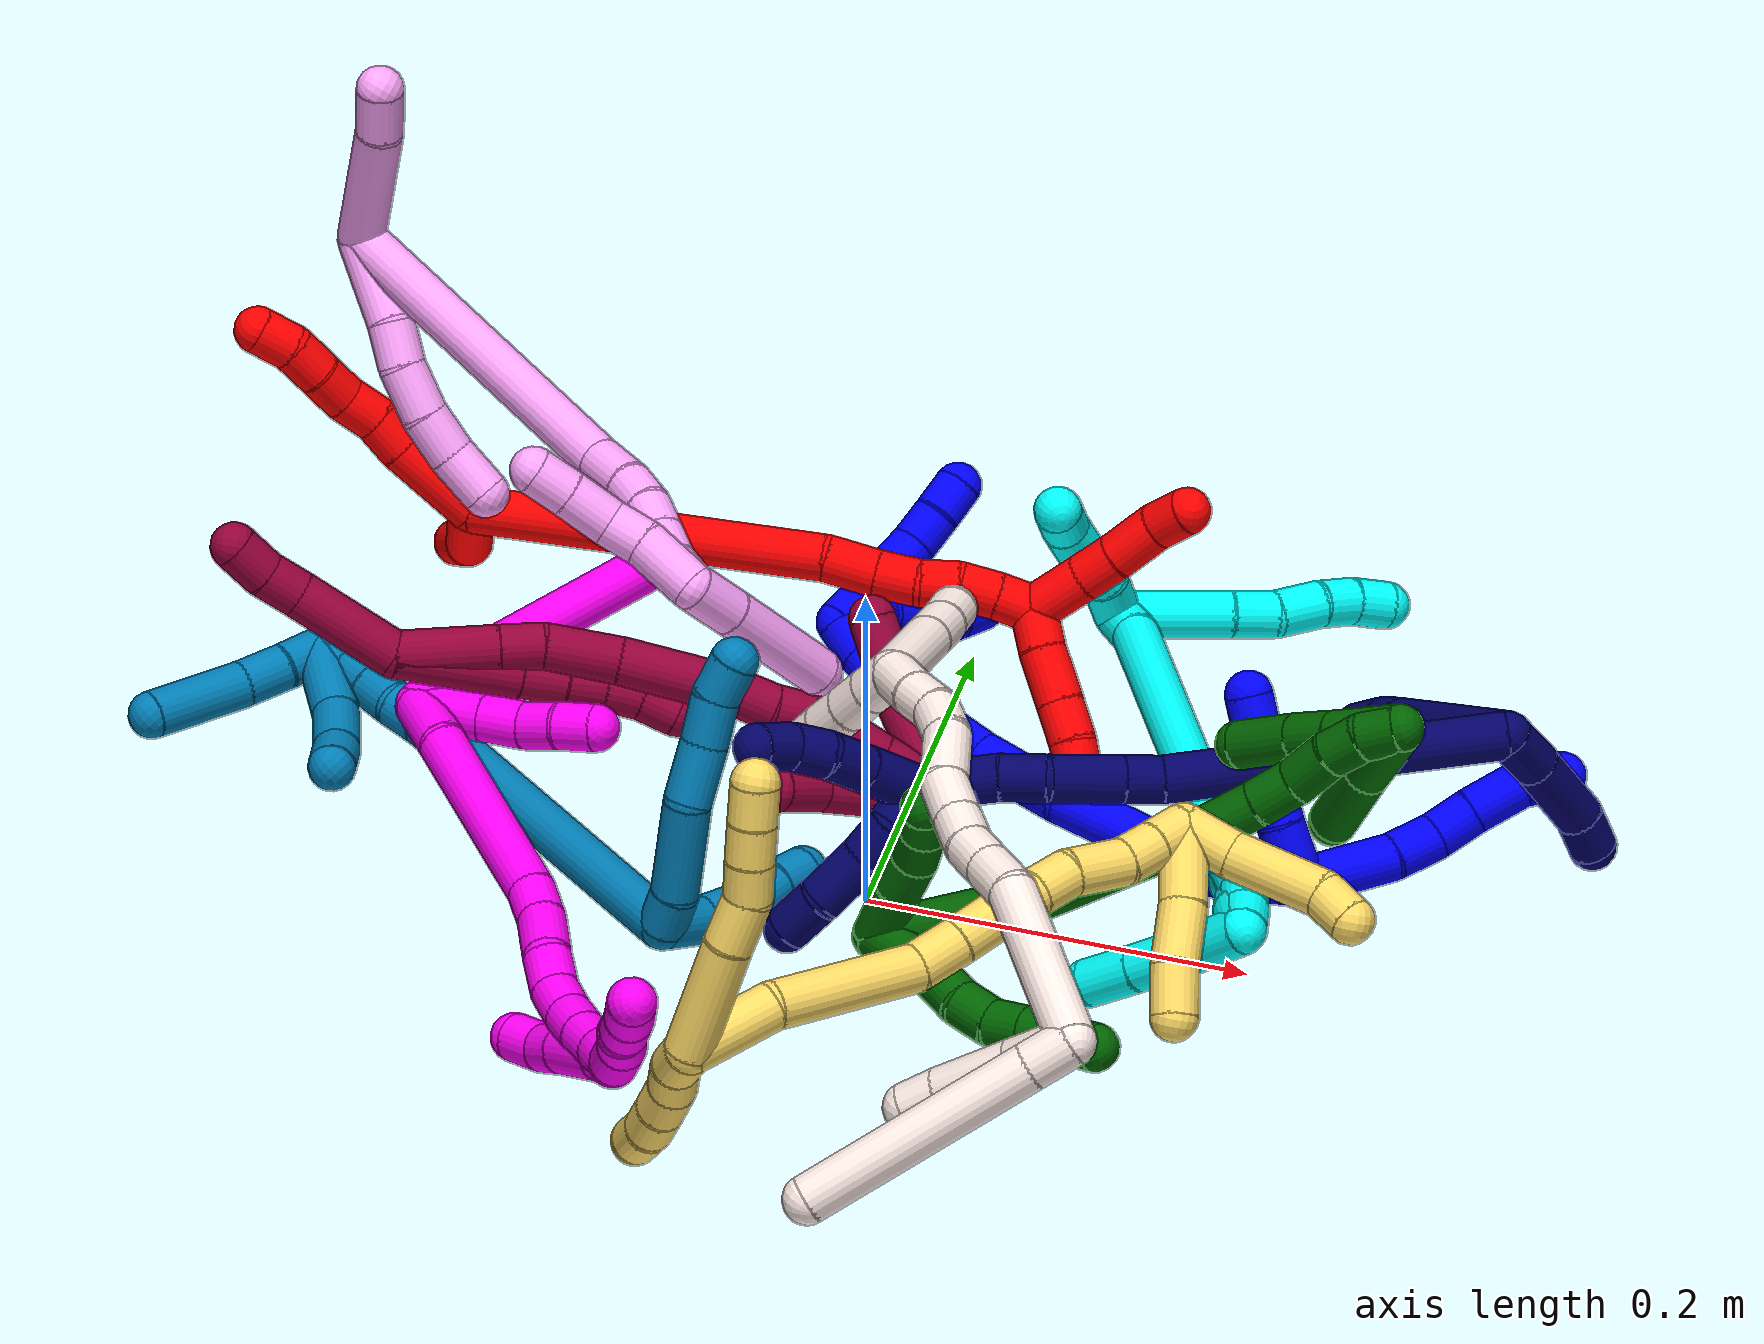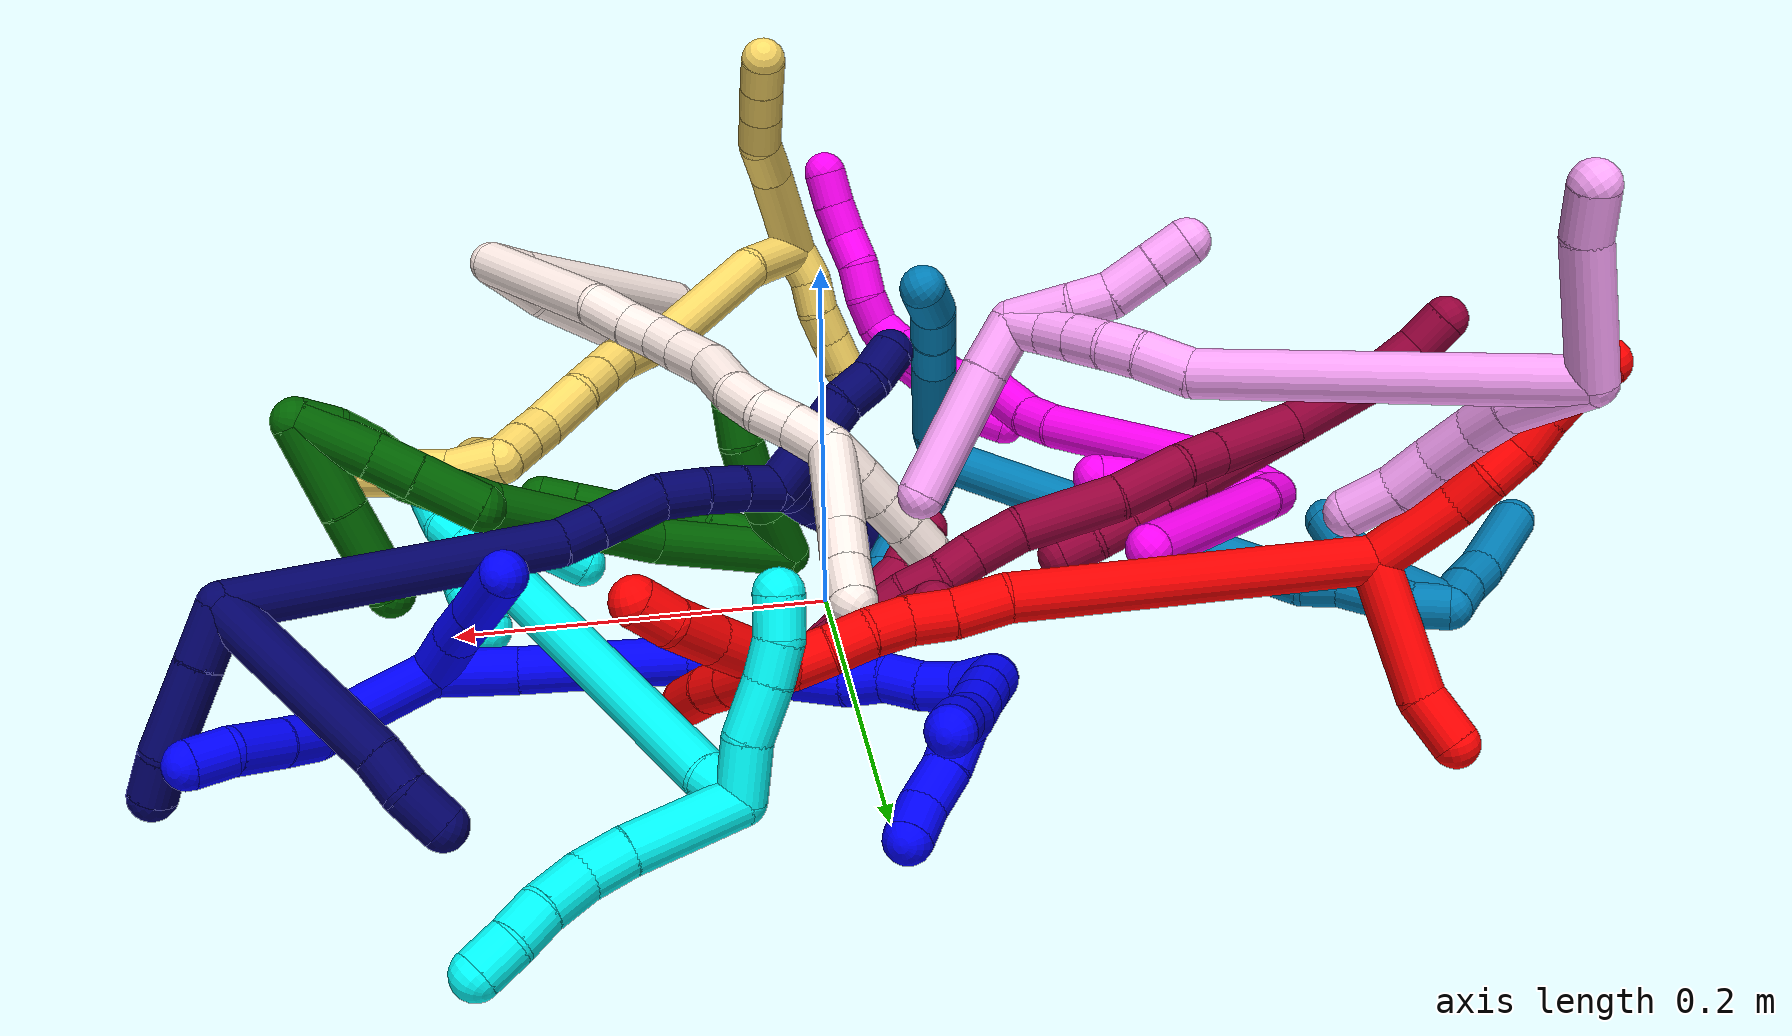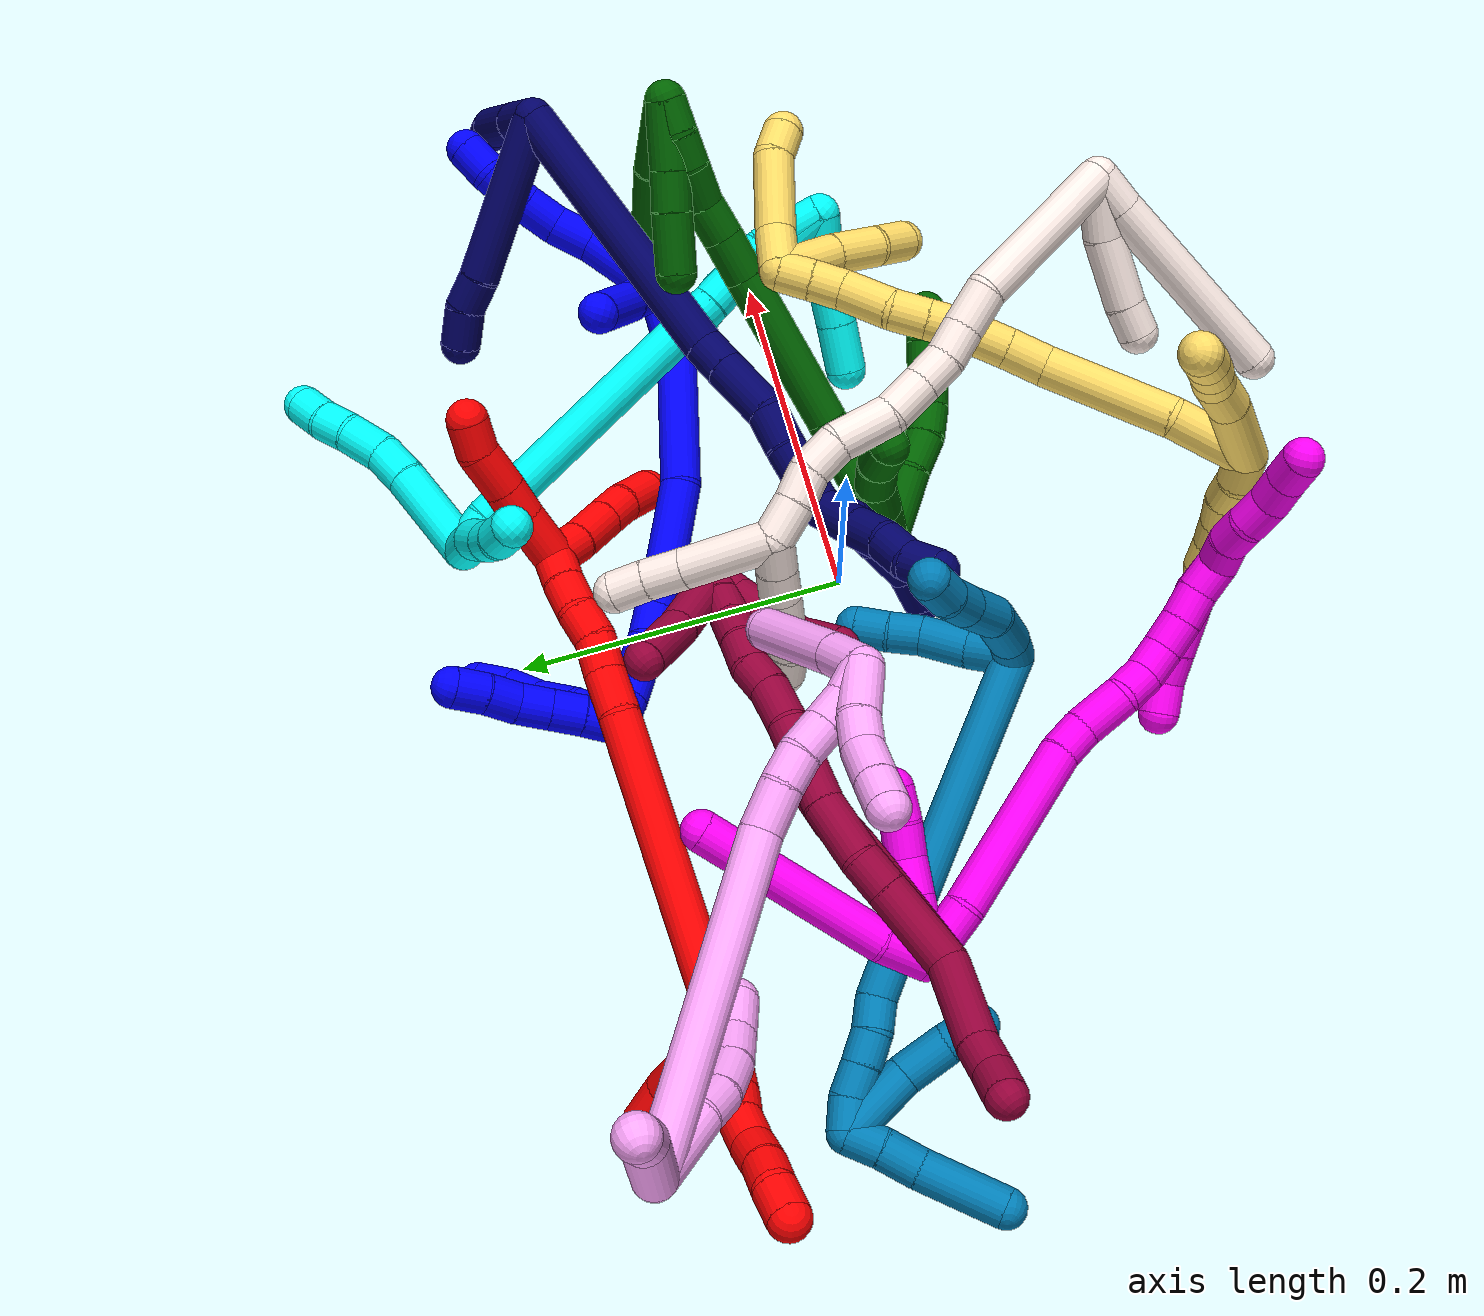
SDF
<sdf version="1.7">
 <world name="default">
  <plugin name="TubeGeneratorPlugin" filename="libtube_generator_plugin.so"/>
  <model name="photoneo_s_sensor">
   <static>1</static>
   <pose>0 0 2 1.57079 1.57079 3.14159</pose>
   <link name="link">
    <inertial><mass>0.1</mass></inertial>
    <sensor name="sensor" type="depth">
     <update_rate>30</update_rate>
     <camera>
      <horizontal_fov>1.22</horizontal_fov>
      <image><width>1920</width><height>1200</height><format>B8G8R8</format></image>
      <clip><near>0.1</near><far>4</far></clip>
      <depth_camera><output>points</output></depth_camera>
     </camera>
     <plugin name="camera_plugin" filename="libgazebo_ros_depth_camera.so">
      <baseline>0.2</baseline>
      <alwaysOn>1</alwaysOn>
      <updateRate>0.0</updateRate>
      <cameraName>camera_ir</cameraName>
      <imageTopicName>/camera/color/image_raw</imageTopicName>
      <cameraInfoTopicName>/camera/color/camera_info</cameraInfoTopicName>
      <depthImageTopicName>/camera/depth/image_raw</depthImageTopicName>
      <depthImageCameraInfoTopicName>/camera/depth/camera_info</depthImageCameraInfoTopicName>
      <pointCloudTopicName>/camera/depth/points</pointCloudTopicName>
      <frameName>fr_optical</frameName>
      <pointCloudCutoff>0.1</pointCloudCutoff>
      <pointCloudCutoffMax>2.0</pointCloudCutoffMax>
      <distortionK1>0</distortionK1>
      <distortionK2>0</distortionK2>
      <distortionK3>0</distortionK3>
      <distortionT1>0</distortionT1>
      <distortionT2>0</distortionT2>
      <CxPrime>0</CxPrime>
      <Cx>0</Cx>
      <Cy>0</Cy>
      <focalLength>0</focalLength>
      <hackBaseline>0</hackBaseline>
     </plugin>
    </sensor>
   </link>
  </model>
  <gravity>0 0 -9.8</gravity>
  <magnetic_field>6e-06 2.3e-05 -4.2e-05</magnetic_field>
  <atmosphere type="adiabatic"/>
  <physics name="default_physics" default="0" type="ode">
   <max_step_size>0.003</max_step_size>
   <real_time_factor>1</real_time_factor>
   <real_time_update_rate>1000</real_time_update_rate>
   <max_contacts>10000</max_contacts>
   <ode>
    <solver>
     <type>quick</type>
     <iters>100</iters>
     <sor>1.3</sor>
     <use_dynamic_moi_rescaling>0</use_dynamic_moi_rescaling>
    </solver>
    <constraints>
     <contact_max_correcting_vel>0</contact_max_correcting_vel>
     <contact_surface_layer>0.001</contact_surface_layer>
     <cfm>0</cfm>
     <erp>0.2</erp>
    </constraints>
   </ode>
  </physics>
  <scene><ambient>0.4 0.4 0.4 1</ambient><background>0.7 0.7 0.7 1</background><shadows>0</shadows></scene>
  <audio><device>default</device></audio>
  <spherical_coordinates>
   <surface_model>EARTH_WGS84</surface_model>
   <latitude_deg>0</latitude_deg>
   <longitude_deg>0</longitude_deg>
   <elevation>0</elevation>
   <heading_deg>0</heading_deg>
  </spherical_coordinates>
  <model name="bin">
   <static>1</static>
   <link name="bottom">
    <collision name="collision-bottom">
     <pose>0 0 -0.01 0 -0 0</pose>
     <geometry><box><size>0.8 0.6 0.02</size></box></geometry>
     <surface>
      <friction><ode><mu>100</mu><mu2>100</mu2></ode></friction>
      <contact><collide_bitmask>65535</collide_bitmask></contact>
     </surface>
    </collision>
   </link>
   <link name="west_wall">
    <collision name="collision-west_wall">
     <pose>-0.41 0 0.1 0 -0 0</pose>
     <geometry><box><size>0.02 0.6 0.2</size></box></geometry>
     <surface>
      <friction><ode><mu>100</mu><mu2>100</mu2></ode></friction>
      <contact><collide_bitmask>65535</collide_bitmask></contact>
     </surface>
    </collision>
   </link>
   <link name="east_wall">
    <collision name="collision-east_wall">
     <pose>0.41 0 0.1 0 -0 0</pose>
     <geometry><box><size>0.02 0.6 0.2</size></box></geometry>
     <surface>
      <friction><ode><mu>100</mu><mu2>100</mu2></ode></friction>
      <contact><collide_bitmask>65535</collide_bitmask></contact>
     </surface>
    </collision>
   </link>
   <link name="south_wall">
    <collision name="collision-south_wall">
     <pose>0 -0.31 0.1 0 -0 0</pose>
     <geometry><box><size>0.8 0.02 0.2</size></box></geometry>
     <surface>
      <friction><ode><mu>100</mu><mu2>100</mu2></ode></friction>
      <contact><collide_bitmask>65535</collide_bitmask></contact>
     </surface>
    </collision>
   </link>
   <link name="north_wall">
    <collision name="collision-north_wall">
     <pose>0 0.31 0.1 0 -0 0</pose>
     <geometry><box><size>0.8 0.02 0.2</size></box></geometry>
     <surface>
      <friction><ode><mu>100</mu><mu2>100</mu2></ode></friction>
      <contact><collide_bitmask>65535</collide_bitmask></contact>
     </surface>
    </collision>
   </link>
  </model>
  <model name="1">
   <static>0</static>
   <link name="1">
    <collision name="collision-cylinder-e_1_2_8">
     <pose>0.011599 0.005966 0.021505 -0.270613 0.479317 -0.066507</pose>
     <geometry><cylinder><radius>0.0125</radius><length>0.050303</length></cylinder></geometry>
     <surface>
      <friction><ode><mu>1.16</mu><mu2>1.16</mu2><slip1>0</slip1><slip2>0</slip2></ode></friction>
      <contact><ode><kp>1e+06</kp><kd>1</kd><max_vel>0</max_vel><min_depth>0.001</min_depth></ode></contact>
     </surface>
    </collision>
    <visual name="visual-cylinder-e_1_2_8">
     <pose>0.011599 0.005966 0.021505 -0.270613 0.479317 -0.066507</pose>
     <geometry><cylinder><radius>0.0125</radius><length>0.050303</length></cylinder></geometry>
     <material><ambient>0 0 1 1</ambient></material>
    </visual>
    <collision name="collision-cylinder-e_2_8_9">
     <pose>0.027056 0.014768 0.055056 -0.231201 0.302194 -0.035356</pose>
     <geometry><cylinder><radius>0.0125</radius><length>0.025927</length></cylinder></geometry>
     <surface>
      <friction><ode><mu>1.16</mu><mu2>1.16</mu2><slip1>0</slip1><slip2>0</slip2></ode></friction>
      <contact><ode><kp>1e+06</kp><kd>1</kd><max_vel>0</max_vel><min_depth>0.001</min_depth></ode></contact>
     </surface>
    </collision>
    <visual name="visual-cylinder-e_2_8_9">
     <pose>0.027056 0.014768 0.055056 -0.231201 0.302194 -0.035356</pose>
     <geometry><cylinder><radius>0.0125</radius><length>0.025927</length></cylinder></geometry>
     <material><ambient>0 0 1 1</ambient></material>
    </visual>
    <collision name="collision-cylinder-e_3_9_10">
     <pose>0.034257 0.01679 0.078123 0.073649 0.29376 0.010901</pose>
     <geometry><cylinder><radius>0.0125</radius><length>0.023089</length></cylinder></geometry>
     <surface>
      <friction><ode><mu>1.16</mu><mu2>1.16</mu2><slip1>0</slip1><slip2>0</slip2></ode></friction>
      <contact><ode><kp>1e+06</kp><kd>1</kd><max_vel>0</max_vel><min_depth>0.001</min_depth></ode></contact>
     </surface>
    </collision>
    <visual name="visual-cylinder-e_3_9_10">
     <pose>0.034257 0.01679 0.078123 0.073649 0.29376 0.010901</pose>
     <geometry><cylinder><radius>0.0125</radius><length>0.023089</length></cylinder></geometry>
     <material><ambient>0 0 1 1</ambient></material>
    </visual>
    <collision name="collision-cylinder-e_4_10_11">
     <pose>0.043127 0.014831 0.102792 0.083819 0.383552 0.016284</pose>
     <geometry><cylinder><radius>0.0125</radius><length>0.02954</length></cylinder></geometry>
     <surface>
      <friction><ode><mu>1.16</mu><mu2>1.16</mu2><slip1>0</slip1><slip2>0</slip2></ode></friction>
      <contact><ode><kp>1e+06</kp><kd>1</kd><max_vel>0</max_vel><min_depth>0.001</min_depth></ode></contact>
     </surface>
    </collision>
    <visual name="visual-cylinder-e_4_10_11">
     <pose>0.043127 0.014831 0.102792 0.083819 0.383552 0.016284</pose>
     <geometry><cylinder><radius>0.0125</radius><length>0.02954</length></cylinder></geometry>
     <material><ambient>0 0 1 1</ambient></material>
    </visual>
    <collision name="collision-cylinder-e_5_11_6">
     <pose>0.055087 0.014957 0.124731 -0.152351 0.654203 -0.05178</pose>
     <geometry><cylinder><radius>0.0125</radius><length>0.021142</length></cylinder></geometry>
     <surface>
      <friction><ode><mu>1.16</mu><mu2>1.16</mu2><slip1>0</slip1><slip2>0</slip2></ode></friction>
      <contact><ode><kp>1e+06</kp><kd>1</kd><max_vel>0</max_vel><min_depth>0.001</min_depth></ode></contact>
     </surface>
    </collision>
    <visual name="visual-cylinder-e_5_11_6">
     <pose>0.055087 0.014957 0.124731 -0.152351 0.654203 -0.05178</pose>
     <geometry><cylinder><radius>0.0125</radius><length>0.021142</length></cylinder></geometry>
     <material><ambient>0 0 1 1</ambient></material>
    </visual>
    <collision name="collision-cylinder-e_1_2_12">
     <pose>-0.01083 -0.010741 0.006339 1.03765 -0.71507 -0.420342</pose>
     <geometry><cylinder><radius>0.0125</radius><length>0.033035</length></cylinder></geometry>
     <surface>
      <friction><ode><mu>1.16</mu><mu2>1.16</mu2><slip1>0</slip1><slip2>0</slip2></ode></friction>
      <contact><ode><kp>1e+06</kp><kd>1</kd><max_vel>0</max_vel><min_depth>0.001</min_depth></ode></contact>
     </surface>
    </collision>
    <visual name="visual-cylinder-e_1_2_12">
     <pose>-0.01083 -0.010741 0.006339 1.03765 -0.71507 -0.420342</pose>
     <geometry><cylinder><radius>0.0125</radius><length>0.033035</length></cylinder></geometry>
     <material><ambient>0 0 1 1</ambient></material>
    </visual>
    <collision name="collision-cylinder-e_2_12_13">
     <pose>-0.030745 -0.028788 0.018972 0.859666 -0.755527 -0.359886</pose>
     <geometry><cylinder><radius>0.0125</radius><length>0.0265</length></cylinder></geometry>
     <surface>
      <friction><ode><mu>1.16</mu><mu2>1.16</mu2><slip1>0</slip1><slip2>0</slip2></ode></friction>
      <contact><ode><kp>1e+06</kp><kd>1</kd><max_vel>0</max_vel><min_depth>0.001</min_depth></ode></contact>
     </surface>
    </collision>
    <visual name="visual-cylinder-e_2_12_13">
     <pose>-0.030745 -0.028788 0.018972 0.859666 -0.755527 -0.359886</pose>
     <geometry><cylinder><radius>0.0125</radius><length>0.0265</length></cylinder></geometry>
     <material><ambient>0 0 1 1</ambient></material>
    </visual>
    <collision name="collision-cylinder-e_3_13_5">
     <pose>-0.05322 -0.046878 0.035936 0.790721 -0.723209 -0.313118</pose>
     <geometry><cylinder><radius>0.0125</radius><length>0.040465</length></cylinder></geometry>
     <surface>
      <friction><ode><mu>1.16</mu><mu2>1.16</mu2><slip1>0</slip1><slip2>0</slip2></ode></friction>
      <contact><ode><kp>1e+06</kp><kd>1</kd><max_vel>0</max_vel><min_depth>0.001</min_depth></ode></contact>
     </surface>
    </collision>
    <visual name="visual-cylinder-e_3_13_5">
     <pose>-0.05322 -0.046878 0.035936 0.790721 -0.723209 -0.313118</pose>
     <geometry><cylinder><radius>0.0125</radius><length>0.040465</length></cylinder></geometry>
     <material><ambient>0 0 1 1</ambient></material>
    </visual>
    <collision name="collision-cylinder-e_1_2_14">
     <pose>-0.019396 0.001505 -0.010803 -3.00318 -1.05852 2.90569</pose>
     <geometry><cylinder><radius>0.0125</radius><length>0.044506</length></cylinder></geometry>
     <surface>
      <friction><ode><mu>1.16</mu><mu2>1.16</mu2><slip1>0</slip1><slip2>0</slip2></ode></friction>
      <contact><ode><kp>1e+06</kp><kd>1</kd><max_vel>0</max_vel><min_depth>0.001</min_depth></ode></contact>
     </surface>
    </collision>
    <visual name="visual-cylinder-e_1_2_14">
     <pose>-0.019396 0.001505 -0.010803 -3.00318 -1.05852 2.90569</pose>
     <geometry><cylinder><radius>0.0125</radius><length>0.044506</length></cylinder></geometry>
     <material><ambient>0 0 1 1</ambient></material>
    </visual>
    <collision name="collision-cylinder-e_2_14_15">
     <pose>-0.083534 0.002149 -0.030024 3.03973 -1.38389 -3.01871</pose>
     <geometry><cylinder><radius>0.0125</radius><length>0.091069</length></cylinder></geometry>
     <surface>
      <friction><ode><mu>1.16</mu><mu2>1.16</mu2><slip1>0</slip1><slip2>0</slip2></ode></friction>
      <contact><ode><kp>1e+06</kp><kd>1</kd><max_vel>0</max_vel><min_depth>0.001</min_depth></ode></contact>
     </surface>
    </collision>
    <visual name="visual-cylinder-e_2_14_15">
     <pose>-0.083534 0.002149 -0.030024 3.03973 -1.38389 -3.01871</pose>
     <geometry><cylinder><radius>0.0125</radius><length>0.091069</length></cylinder></geometry>
     <material><ambient>0 0 1 1</ambient></material>
    </visual>
    <collision name="collision-cylinder-e_3_15_16">
     <pose>-0.154032 0.005789 -0.039407 -1.78233 -1.39396 1.60616</pose>
     <geometry><cylinder><radius>0.0125</radius><length>0.052329</length></cylinder></geometry>
     <surface>
      <friction><ode><mu>1.16</mu><mu2>1.16</mu2><slip1>0</slip1><slip2>0</slip2></ode></friction>
      <contact><ode><kp>1e+06</kp><kd>1</kd><max_vel>0</max_vel><min_depth>0.001</min_depth></ode></contact>
     </surface>
    </collision>
    <visual name="visual-cylinder-e_3_15_16">
     <pose>-0.154032 0.005789 -0.039407 -1.78233 -1.39396 1.60616</pose>
     <geometry><cylinder><radius>0.0125</radius><length>0.052329</length></cylinder></geometry>
     <material><ambient>0 0 1 1</ambient></material>
    </visual>
    <collision name="collision-cylinder-e_4_16_17">
     <pose>-0.194413 0.012025 -0.040019 -1.36945 -1.45025 1.25274</pose>
     <geometry><cylinder><radius>0.0125</radius><length>0.029463</length></cylinder></geometry>
     <surface>
      <friction><ode><mu>1.16</mu><mu2>1.16</mu2><slip1>0</slip1><slip2>0</slip2></ode></friction>
      <contact><ode><kp>1e+06</kp><kd>1</kd><max_vel>0</max_vel><min_depth>0.001</min_depth></ode></contact>
     </surface>
    </collision>
    <visual name="visual-cylinder-e_4_16_17">
     <pose>-0.194413 0.012025 -0.040019 -1.36945 -1.45025 1.25274</pose>
     <geometry><cylinder><radius>0.0125</radius><length>0.029463</length></cylinder></geometry>
     <material><ambient>0 0 1 1</ambient></material>
    </visual>
    <collision name="collision-cylinder-e_5_17_18">
     <pose>-0.219759 0.012421 -0.038842 1.02012 -1.4252 -0.900534</pose>
     <geometry><cylinder><radius>0.0125</radius><length>0.021673</length></cylinder></geometry>
     <surface>
      <friction><ode><mu>1.16</mu><mu2>1.16</mu2><slip1>0</slip1><slip2>0</slip2></ode></friction>
      <contact><ode><kp>1e+06</kp><kd>1</kd><max_vel>0</max_vel><min_depth>0.001</min_depth></ode></contact>
     </surface>
    </collision>
    <visual name="visual-cylinder-e_5_17_18">
     <pose>-0.219759 0.012421 -0.038842 1.02012 -1.4252 -0.900534</pose>
     <geometry><cylinder><radius>0.0125</radius><length>0.021673</length></cylinder></geometry>
     <material><ambient>0 0 1 1</ambient></material>
    </visual>
    <collision name="collision-cylinder-e_6_18_19">
     <pose>-0.240629 0.013089 -0.036659 -0.975127 -1.33616 0.792616</pose>
     <geometry><cylinder><radius>0.0125</radius><length>0.020868</length></cylinder></geometry>
     <surface>
      <friction><ode><mu>1.16</mu><mu2>1.16</mu2><slip1>0</slip1><slip2>0</slip2></ode></friction>
      <contact><ode><kp>1e+06</kp><kd>1</kd><max_vel>0</max_vel><min_depth>0.001</min_depth></ode></contact>
     </surface>
    </collision>
    <visual name="visual-cylinder-e_6_18_19">
     <pose>-0.240629 0.013089 -0.036659 -0.975127 -1.33616 0.792616</pose>
     <geometry><cylinder><radius>0.0125</radius><length>0.020868</length></cylinder></geometry>
     <material><ambient>0 0 1 1</ambient></material>
    </visual>
    <collision name="collision-cylinder-e_7_19_20">
     <pose>-0.260694 0.015016 -0.03395 0.060242 -1.43546 -0.052599</pose>
     <geometry><cylinder><radius>0.0125</radius><length>0.020016</length></cylinder></geometry>
     <surface>
      <friction><ode><mu>1.16</mu><mu2>1.16</mu2><slip1>0</slip1><slip2>0</slip2></ode></friction>
      <contact><ode><kp>1e+06</kp><kd>1</kd><max_vel>0</max_vel><min_depth>0.001</min_depth></ode></contact>
     </surface>
    </collision>
    <visual name="visual-cylinder-e_7_19_20">
     <pose>-0.260694 0.015016 -0.03395 0.060242 -1.43546 -0.052599</pose>
     <geometry><cylinder><radius>0.0125</radius><length>0.020016</length></cylinder></geometry>
     <material><ambient>0 0 1 1</ambient></material>
    </visual>
    <collision name="collision-cylinder-e_8_20_1">
     <pose>-0.279877 0.012253 -0.029825 0.767924 -1.1761 -0.526249</pose>
     <geometry><cylinder><radius>0.0125</radius><length>0.020076</length></cylinder></geometry>
     <surface>
      <friction><ode><mu>1.16</mu><mu2>1.16</mu2><slip1>0</slip1><slip2>0</slip2></ode></friction>
      <contact><ode><kp>1e+06</kp><kd>1</kd><max_vel>0</max_vel><min_depth>0.001</min_depth></ode></contact>
     </surface>
    </collision>
    <visual name="visual-cylinder-e_8_20_1">
     <pose>-0.279877 0.012253 -0.029825 0.767924 -1.1761 -0.526249</pose>
     <geometry><cylinder><radius>0.0125</radius><length>0.020076</length></cylinder></geometry>
     <material><ambient>0 0 1 1</ambient></material>
    </visual>
    <collision name="collision-cylinder-e_1_1_21">
     <pose>-0.289188 0.010368 -0.017081 -0.079639 -0.004452 0.000177</pose>
     <geometry><cylinder><radius>0.0125</radius><length>0.02</length></cylinder></geometry>
     <surface>
      <friction><ode><mu>1.16</mu><mu2>1.16</mu2><slip1>0</slip1><slip2>0</slip2></ode></friction>
      <contact><ode><kp>1e+06</kp><kd>1</kd><max_vel>0</max_vel><min_depth>0.001</min_depth></ode></contact>
     </surface>
    </collision>
    <visual name="visual-cylinder-e_1_1_21">
     <pose>-0.289188 0.010368 -0.017081 -0.079639 -0.004452 0.000177</pose>
     <geometry><cylinder><radius>0.0125</radius><length>0.02</length></cylinder></geometry>
     <material><ambient>0 0 1 1</ambient></material>
    </visual>
    <collision name="collision-cylinder-e_2_21_22">
     <pose>-0.289721 0.012442 0.002794 -0.128371 -0.04892 0.003145</pose>
     <geometry><cylinder><radius>0.0125</radius><length>0.02</length></cylinder></geometry>
     <surface>
      <friction><ode><mu>1.16</mu><mu2>1.16</mu2><slip1>0</slip1><slip2>0</slip2></ode></friction>
      <contact><ode><kp>1e+06</kp><kd>1</kd><max_vel>0</max_vel><min_depth>0.001</min_depth></ode></contact>
     </surface>
    </collision>
    <visual name="visual-cylinder-e_2_21_22">
     <pose>-0.289721 0.012442 0.002794 -0.128371 -0.04892 0.003145</pose>
     <geometry><cylinder><radius>0.0125</radius><length>0.02</length></cylinder></geometry>
     <material><ambient>0 0 1 1</ambient></material>
    </visual>
    <collision name="collision-cylinder-e_3_22_23">
     <pose>-0.290705 0.014989 0.022606 -0.127332 -0.04945 0.003153</pose>
     <geometry><cylinder><radius>0.0125</radius><length>0.02</length></cylinder></geometry>
     <surface>
      <friction><ode><mu>1.16</mu><mu2>1.16</mu2><slip1>0</slip1><slip2>0</slip2></ode></friction>
      <contact><ode><kp>1e+06</kp><kd>1</kd><max_vel>0</max_vel><min_depth>0.001</min_depth></ode></contact>
     </surface>
    </collision>
    <visual name="visual-cylinder-e_3_22_23">
     <pose>-0.290705 0.014989 0.022606 -0.127332 -0.04945 0.003153</pose>
     <geometry><cylinder><radius>0.0125</radius><length>0.02</length></cylinder></geometry>
     <material><ambient>0 0 1 1</ambient></material>
    </visual>
    <collision name="collision-cylinder-e_4_23_24">
     <pose>-0.291546 0.014979 0.042425 0.128197 -0.034721 -0.002229</pose>
     <geometry><cylinder><radius>0.0125</radius><length>0.02</length></cylinder></geometry>
     <surface>
      <friction><ode><mu>1.16</mu><mu2>1.16</mu2><slip1>0</slip1><slip2>0</slip2></ode></friction>
      <contact><ode><kp>1e+06</kp><kd>1</kd><max_vel>0</max_vel><min_depth>0.001</min_depth></ode></contact>
     </surface>
    </collision>
    <visual name="visual-cylinder-e_4_23_24">
     <pose>-0.291546 0.014979 0.042425 0.128197 -0.034721 -0.002229</pose>
     <geometry><cylinder><radius>0.0125</radius><length>0.02</length></cylinder></geometry>
     <material><ambient>0 0 1 1</ambient></material>
    </visual>
    <collision name="collision-cylinder-e_5_24_4">
     <pose>-0.292921 0.013513 0.062282 0.018997 -0.102929 -0.000979</pose>
     <geometry><cylinder><radius>0.0125</radius><length>0.02</length></cylinder></geometry>
     <surface>
      <friction><ode><mu>1.16</mu><mu2>1.16</mu2><slip1>0</slip1><slip2>0</slip2></ode></friction>
      <contact><ode><kp>1e+06</kp><kd>1</kd><max_vel>0</max_vel><min_depth>0.001</min_depth></ode></contact>
     </surface>
    </collision>
    <visual name="visual-cylinder-e_5_24_4">
     <pose>-0.292921 0.013513 0.062282 0.018997 -0.102929 -0.000979</pose>
     <geometry><cylinder><radius>0.0125</radius><length>0.02</length></cylinder></geometry>
     <material><ambient>0 0 1 1</ambient></material>
    </visual>
    <collision name="collision-cylinder-e_1_1_25">
     <pose>-0.28465 0.017215 -0.015842 -0.59854 0.319892 -0.099467</pose>
     <geometry><cylinder><radius>0.0125</radius><length>0.02858</length></cylinder></geometry>
     <surface>
      <friction><ode><mu>1.16</mu><mu2>1.16</mu2><slip1>0</slip1><slip2>0</slip2></ode></friction>
      <contact><ode><kp>1e+06</kp><kd>1</kd><max_vel>0</max_vel><min_depth>0.001</min_depth></ode></contact>
     </surface>
    </collision>
    <visual name="visual-cylinder-e_1_1_25">
     <pose>-0.28465 0.017215 -0.015842 -0.59854 0.319892 -0.099467</pose>
     <geometry><cylinder><radius>0.0125</radius><length>0.02858</length></cylinder></geometry>
     <material><ambient>0 0 1 1</ambient></material>
    </visual>
    <collision name="collision-cylinder-e_2_25_26">
     <pose>-0.276885 0.035077 0.003856 -0.877476 0.241401 -0.113705</pose>
     <geometry><cylinder><radius>0.0125</radius><length>0.027366</length></cylinder></geometry>
     <surface>
      <friction><ode><mu>1.16</mu><mu2>1.16</mu2><slip1>0</slip1><slip2>0</slip2></ode></friction>
      <contact><ode><kp>1e+06</kp><kd>1</kd><max_vel>0</max_vel><min_depth>0.001</min_depth></ode></contact>
     </surface>
    </collision>
    <visual name="visual-cylinder-e_2_25_26">
     <pose>-0.276885 0.035077 0.003856 -0.877476 0.241401 -0.113705</pose>
     <geometry><cylinder><radius>0.0125</radius><length>0.027366</length></cylinder></geometry>
     <material><ambient>0 0 1 1</ambient></material>
    </visual>
    <collision name="collision-cylinder-e_3_26_27">
     <pose>-0.269388 0.052743 0.020083 -0.766433 0.37495 -0.152659</pose>
     <geometry><cylinder><radius>0.0125</radius><length>0.023079</length></cylinder></geometry>
     <surface>
      <friction><ode><mu>1.16</mu><mu2>1.16</mu2><slip1>0</slip1><slip2>0</slip2></ode></friction>
      <contact><ode><kp>1e+06</kp><kd>1</kd><max_vel>0</max_vel><min_depth>0.001</min_depth></ode></contact>
     </surface>
    </collision>
    <visual name="visual-cylinder-e_3_26_27">
     <pose>-0.269388 0.052743 0.020083 -0.766433 0.37495 -0.152659</pose>
     <geometry><cylinder><radius>0.0125</radius><length>0.023079</length></cylinder></geometry>
     <material><ambient>0 0 1 1</ambient></material>
    </visual>
    <collision name="collision-cylinder-e_4_27_3">
     <pose>-0.263756 0.06574 0.036605 -0.56325 0.134467 -0.038957</pose>
     <geometry><cylinder><radius>0.0125</radius><length>0.020975</length></cylinder></geometry>
     <surface>
      <friction><ode><mu>1.16</mu><mu2>1.16</mu2><slip1>0</slip1><slip2>0</slip2></ode></friction>
      <contact><ode><kp>1e+06</kp><kd>1</kd><max_vel>0</max_vel><min_depth>0.001</min_depth></ode></contact>
     </surface>
    </collision>
    <visual name="visual-cylinder-e_4_27_3">
     <pose>-0.263756 0.06574 0.036605 -0.56325 0.134467 -0.038957</pose>
     <geometry><cylinder><radius>0.0125</radius><length>0.020975</length></cylinder></geometry>
     <material><ambient>0 0 1 1</ambient></material>
    </visual>
    <collision name="collision-sphere-3">
     <pose>-0.26235 0.071289 0.045393 0 -0 0</pose>
     <geometry><sphere><radius>0.0125</radius></sphere></geometry>
     <surface>
      <friction><ode><mu>1.16</mu><mu2>1.16</mu2><slip1>0</slip1><slip2>0</slip2></ode></friction>
      <contact><ode><kp>1e+06</kp><kd>1</kd><max_vel>0</max_vel><min_depth>0.001</min_depth></ode></contact>
     </surface>
    </collision>
    <visual name="visual-sphere-3">
     <pose>-0.26235 0.071289 0.045393 0 -0 0</pose>
     <geometry><sphere><radius>0.0125</radius></sphere></geometry>
     <material><ambient>0 0 1 1</ambient></material>
    </visual>
    <collision name="collision-sphere-27">
     <pose>-0.265162 0.06019 0.027818 0 -0 0</pose>
     <geometry><sphere><radius>0.0125</radius></sphere></geometry>
     <surface>
      <friction><ode><mu>1.16</mu><mu2>1.16</mu2><slip1>0</slip1><slip2>0</slip2></ode></friction>
      <contact><ode><kp>1e+06</kp><kd>1</kd><max_vel>0</max_vel><min_depth>0.001</min_depth></ode></contact>
     </surface>
    </collision>
    <visual name="visual-sphere-27">
     <pose>-0.265162 0.06019 0.027818 0 -0 0</pose>
     <geometry><sphere><radius>0.0125</radius></sphere></geometry>
     <material><ambient>0 0 1 1</ambient></material>
    </visual>
    <collision name="collision-sphere-26">
     <pose>-0.273614 0.045296 0.012347 0 -0 0</pose>
     <geometry><sphere><radius>0.0125</radius></sphere></geometry>
     <surface>
      <friction><ode><mu>1.16</mu><mu2>1.16</mu2><slip1>0</slip1><slip2>0</slip2></ode></friction>
      <contact><ode><kp>1e+06</kp><kd>1</kd><max_vel>0</max_vel><min_depth>0.001</min_depth></ode></contact>
     </surface>
    </collision>
    <visual name="visual-sphere-26">
     <pose>-0.273614 0.045296 0.012347 0 -0 0</pose>
     <geometry><sphere><radius>0.0125</radius></sphere></geometry>
     <material><ambient>0 0 1 1</ambient></material>
    </visual>
    <collision name="collision-sphere-25">
     <pose>-0.280156 0.024858 -0.004635 0 -0 0</pose>
     <geometry><sphere><radius>0.0125</radius></sphere></geometry>
     <surface>
      <friction><ode><mu>1.16</mu><mu2>1.16</mu2><slip1>0</slip1><slip2>0</slip2></ode></friction>
      <contact><ode><kp>1e+06</kp><kd>1</kd><max_vel>0</max_vel><min_depth>0.001</min_depth></ode></contact>
     </surface>
    </collision>
    <visual name="visual-sphere-25">
     <pose>-0.280156 0.024858 -0.004635 0 -0 0</pose>
     <geometry><sphere><radius>0.0125</radius></sphere></geometry>
     <material><ambient>0 0 1 1</ambient></material>
    </visual>
    <collision name="collision-sphere-4">
     <pose>-0.293948 0.013324 0.072228 0 -0 0</pose>
     <geometry><sphere><radius>0.0125</radius></sphere></geometry>
     <surface>
      <friction><ode><mu>1.16</mu><mu2>1.16</mu2><slip1>0</slip1><slip2>0</slip2></ode></friction>
      <contact><ode><kp>1e+06</kp><kd>1</kd><max_vel>0</max_vel><min_depth>0.001</min_depth></ode></contact>
     </surface>
    </collision>
    <visual name="visual-sphere-4">
     <pose>-0.293948 0.013324 0.072228 0 -0 0</pose>
     <geometry><sphere><radius>0.0125</radius></sphere></geometry>
     <material><ambient>0 0 1 1</ambient></material>
    </visual>
    <collision name="collision-sphere-24">
     <pose>-0.291893 0.013702 0.052337 0 -0 0</pose>
     <geometry><sphere><radius>0.0125</radius></sphere></geometry>
     <surface>
      <friction><ode><mu>1.16</mu><mu2>1.16</mu2><slip1>0</slip1><slip2>0</slip2></ode></friction>
      <contact><ode><kp>1e+06</kp><kd>1</kd><max_vel>0</max_vel><min_depth>0.001</min_depth></ode></contact>
     </surface>
    </collision>
    <visual name="visual-sphere-24">
     <pose>-0.291893 0.013702 0.052337 0 -0 0</pose>
     <geometry><sphere><radius>0.0125</radius></sphere></geometry>
     <material><ambient>0 0 1 1</ambient></material>
    </visual>
    <collision name="collision-sphere-23">
     <pose>-0.291199 0.016257 0.032513 0 -0 0</pose>
     <geometry><sphere><radius>0.0125</radius></sphere></geometry>
     <surface>
      <friction><ode><mu>1.16</mu><mu2>1.16</mu2><slip1>0</slip1><slip2>0</slip2></ode></friction>
      <contact><ode><kp>1e+06</kp><kd>1</kd><max_vel>0</max_vel><min_depth>0.001</min_depth></ode></contact>
     </surface>
    </collision>
    <visual name="visual-sphere-23">
     <pose>-0.291199 0.016257 0.032513 0 -0 0</pose>
     <geometry><sphere><radius>0.0125</radius></sphere></geometry>
     <material><ambient>0 0 1 1</ambient></material>
    </visual>
    <collision name="collision-sphere-22">
     <pose>-0.29021 0.01372 0.012699 0 -0 0</pose>
     <geometry><sphere><radius>0.0125</radius></sphere></geometry>
     <surface>
      <friction><ode><mu>1.16</mu><mu2>1.16</mu2><slip1>0</slip1><slip2>0</slip2></ode></friction>
      <contact><ode><kp>1e+06</kp><kd>1</kd><max_vel>0</max_vel><min_depth>0.001</min_depth></ode></contact>
     </surface>
    </collision>
    <visual name="visual-sphere-22">
     <pose>-0.29021 0.01372 0.012699 0 -0 0</pose>
     <geometry><sphere><radius>0.0125</radius></sphere></geometry>
     <material><ambient>0 0 1 1</ambient></material>
    </visual>
    <collision name="collision-sphere-21">
     <pose>-0.289232 0.011163 -0.007112 0 -0 0</pose>
     <geometry><sphere><radius>0.0125</radius></sphere></geometry>
     <surface>
      <friction><ode><mu>1.16</mu><mu2>1.16</mu2><slip1>0</slip1><slip2>0</slip2></ode></friction>
      <contact><ode><kp>1e+06</kp><kd>1</kd><max_vel>0</max_vel><min_depth>0.001</min_depth></ode></contact>
     </surface>
    </collision>
    <visual name="visual-sphere-21">
     <pose>-0.289232 0.011163 -0.007112 0 -0 0</pose>
     <geometry><sphere><radius>0.0125</radius></sphere></geometry>
     <material><ambient>0 0 1 1</ambient></material>
    </visual>
    <collision name="collision-sphere-1">
     <pose>-0.289143 0.009572 -0.027049 0 -0 0</pose>
     <geometry><sphere><radius>0.0125</radius></sphere></geometry>
     <surface>
      <friction><ode><mu>1.16</mu><mu2>1.16</mu2><slip1>0</slip1><slip2>0</slip2></ode></friction>
      <contact><ode><kp>1e+06</kp><kd>1</kd><max_vel>0</max_vel><min_depth>0.001</min_depth></ode></contact>
     </surface>
    </collision>
    <visual name="visual-sphere-1">
     <pose>-0.289143 0.009572 -0.027049 0 -0 0</pose>
     <geometry><sphere><radius>0.0125</radius></sphere></geometry>
     <material><ambient>0 0 1 1</ambient></material>
    </visual>
    <collision name="collision-sphere-6">
     <pose>0.06152 0.01623 0.133023 0 -0 0</pose>
     <geometry><sphere><radius>0.0125</radius></sphere></geometry>
     <surface>
      <friction><ode><mu>1.16</mu><mu2>1.16</mu2><slip1>0</slip1><slip2>0</slip2></ode></friction>
      <contact><ode><kp>1e+06</kp><kd>1</kd><max_vel>0</max_vel><min_depth>0.001</min_depth></ode></contact>
     </surface>
    </collision>
    <visual name="visual-sphere-6">
     <pose>0.06152 0.01623 0.133023 0 -0 0</pose>
     <geometry><sphere><radius>0.0125</radius></sphere></geometry>
     <material><ambient>0 0 1 1</ambient></material>
    </visual>
    <collision name="collision-sphere-11">
     <pose>0.048654 0.013684 0.11644 0 -0 0</pose>
     <geometry><sphere><radius>0.0125</radius></sphere></geometry>
     <surface>
      <friction><ode><mu>1.16</mu><mu2>1.16</mu2><slip1>0</slip1><slip2>0</slip2></ode></friction>
      <contact><ode><kp>1e+06</kp><kd>1</kd><max_vel>0</max_vel><min_depth>0.001</min_depth></ode></contact>
     </surface>
    </collision>
    <visual name="visual-sphere-11">
     <pose>0.048654 0.013684 0.11644 0 -0 0</pose>
     <geometry><sphere><radius>0.0125</radius></sphere></geometry>
     <material><ambient>0 0 1 1</ambient></material>
    </visual>
    <collision name="collision-sphere-10">
     <pose>0.0376 0.015977 0.089143 0 -0 0</pose>
     <geometry><sphere><radius>0.0125</radius></sphere></geometry>
     <surface>
      <friction><ode><mu>1.16</mu><mu2>1.16</mu2><slip1>0</slip1><slip2>0</slip2></ode></friction>
      <contact><ode><kp>1e+06</kp><kd>1</kd><max_vel>0</max_vel><min_depth>0.001</min_depth></ode></contact>
     </surface>
    </collision>
    <visual name="visual-sphere-10">
     <pose>0.0376 0.015977 0.089143 0 -0 0</pose>
     <geometry><sphere><radius>0.0125</radius></sphere></geometry>
     <material><ambient>0 0 1 1</ambient></material>
    </visual>
    <collision name="collision-sphere-9">
     <pose>0.030914 0.017603 0.067103 0 -0 0</pose>
     <geometry><sphere><radius>0.0125</radius></sphere></geometry>
     <surface>
      <friction><ode><mu>1.16</mu><mu2>1.16</mu2><slip1>0</slip1><slip2>0</slip2></ode></friction>
      <contact><ode><kp>1e+06</kp><kd>1</kd><max_vel>0</max_vel><min_depth>0.001</min_depth></ode></contact>
     </surface>
    </collision>
    <visual name="visual-sphere-9">
     <pose>0.030914 0.017603 0.067103 0 -0 0</pose>
     <geometry><sphere><radius>0.0125</radius></sphere></geometry>
     <material><ambient>0 0 1 1</ambient></material>
    </visual>
    <collision name="collision-sphere-2">
     <geometry><sphere><radius>0.0125</radius></sphere></geometry>
     <surface>
      <friction><ode><mu>1.16</mu><mu2>1.16</mu2><slip1>0</slip1><slip2>0</slip2></ode></friction>
      <contact><ode><kp>1e+06</kp><kd>1</kd><max_vel>0</max_vel><min_depth>0.001</min_depth></ode></contact>
     </surface>
    </collision>
    <visual name="visual-sphere-2">
     <geometry><sphere><radius>0.0125</radius></sphere></geometry>
     <material><ambient>0 0 1 1</ambient></material>
    </visual>
    <collision name="collision-sphere-19">
     <pose>-0.250778 0.015097 -0.035298 0 -0 0</pose>
     <geometry><sphere><radius>0.0125</radius></sphere></geometry>
     <surface>
      <friction><ode><mu>1.16</mu><mu2>1.16</mu2><slip1>0</slip1><slip2>0</slip2></ode></friction>
      <contact><ode><kp>1e+06</kp><kd>1</kd><max_vel>0</max_vel><min_depth>0.001</min_depth></ode></contact>
     </surface>
    </collision>
    <visual name="visual-sphere-19">
     <pose>-0.250778 0.015097 -0.035298 0 -0 0</pose>
     <geometry><sphere><radius>0.0125</radius></sphere></geometry>
     <material><ambient>0 0 1 1</ambient></material>
    </visual>
    <collision name="collision-sphere-8">
     <pose>0.023198 0.011932 0.04301 0 -0 0</pose>
     <geometry><sphere><radius>0.0125</radius></sphere></geometry>
     <surface>
      <friction><ode><mu>1.16</mu><mu2>1.16</mu2><slip1>0</slip1><slip2>0</slip2></ode></friction>
      <contact><ode><kp>1e+06</kp><kd>1</kd><max_vel>0</max_vel><min_depth>0.001</min_depth></ode></contact>
     </surface>
    </collision>
    <visual name="visual-sphere-8">
     <pose>0.023198 0.011932 0.04301 0 -0 0</pose>
     <geometry><sphere><radius>0.0125</radius></sphere></geometry>
     <material><ambient>0 0 1 1</ambient></material>
    </visual>
    <collision name="collision-sphere-12">
     <pose>-0.02166 -0.021481 0.012677 0 -0 0</pose>
     <geometry><sphere><radius>0.0125</radius></sphere></geometry>
     <surface>
      <friction><ode><mu>1.16</mu><mu2>1.16</mu2><slip1>0</slip1><slip2>0</slip2></ode></friction>
      <contact><ode><kp>1e+06</kp><kd>1</kd><max_vel>0</max_vel><min_depth>0.001</min_depth></ode></contact>
     </surface>
    </collision>
    <visual name="visual-sphere-12">
     <pose>-0.02166 -0.021481 0.012677 0 -0 0</pose>
     <geometry><sphere><radius>0.0125</radius></sphere></geometry>
     <material><ambient>0 0 1 1</ambient></material>
    </visual>
    <collision name="collision-sphere-13">
     <pose>-0.039831 -0.036096 0.025267 0 -0 0</pose>
     <geometry><sphere><radius>0.0125</radius></sphere></geometry>
     <surface>
      <friction><ode><mu>1.16</mu><mu2>1.16</mu2><slip1>0</slip1><slip2>0</slip2></ode></friction>
      <contact><ode><kp>1e+06</kp><kd>1</kd><max_vel>0</max_vel><min_depth>0.001</min_depth></ode></contact>
     </surface>
    </collision>
    <visual name="visual-sphere-13">
     <pose>-0.039831 -0.036096 0.025267 0 -0 0</pose>
     <geometry><sphere><radius>0.0125</radius></sphere></geometry>
     <material><ambient>0 0 1 1</ambient></material>
    </visual>
    <collision name="collision-sphere-5">
     <pose>-0.06661 -0.05766 0.046604 0 -0 0</pose>
     <geometry><sphere><radius>0.0125</radius></sphere></geometry>
     <surface>
      <friction><ode><mu>1.16</mu><mu2>1.16</mu2><slip1>0</slip1><slip2>0</slip2></ode></friction>
      <contact><ode><kp>1e+06</kp><kd>1</kd><max_vel>0</max_vel><min_depth>0.001</min_depth></ode></contact>
     </surface>
    </collision>
    <visual name="visual-sphere-5">
     <pose>-0.06661 -0.05766 0.046604 0 -0 0</pose>
     <geometry><sphere><radius>0.0125</radius></sphere></geometry>
     <material><ambient>0 0 1 1</ambient></material>
    </visual>
    <collision name="collision-sphere-14">
     <pose>-0.038792 0.00301 -0.021606 0 -0 0</pose>
     <geometry><sphere><radius>0.0125</radius></sphere></geometry>
     <surface>
      <friction><ode><mu>1.16</mu><mu2>1.16</mu2><slip1>0</slip1><slip2>0</slip2></ode></friction>
      <contact><ode><kp>1e+06</kp><kd>1</kd><max_vel>0</max_vel><min_depth>0.001</min_depth></ode></contact>
     </surface>
    </collision>
    <visual name="visual-sphere-14">
     <pose>-0.038792 0.00301 -0.021606 0 -0 0</pose>
     <geometry><sphere><radius>0.0125</radius></sphere></geometry>
     <material><ambient>0 0 1 1</ambient></material>
    </visual>
    <collision name="collision-sphere-15">
     <pose>-0.128276 0.001289 -0.038441 0 -0 0</pose>
     <geometry><sphere><radius>0.0125</radius></sphere></geometry>
     <surface>
      <friction><ode><mu>1.16</mu><mu2>1.16</mu2><slip1>0</slip1><slip2>0</slip2></ode></friction>
      <contact><ode><kp>1e+06</kp><kd>1</kd><max_vel>0</max_vel><min_depth>0.001</min_depth></ode></contact>
     </surface>
    </collision>
    <visual name="visual-sphere-15">
     <pose>-0.128276 0.001289 -0.038441 0 -0 0</pose>
     <geometry><sphere><radius>0.0125</radius></sphere></geometry>
     <material><ambient>0 0 1 1</ambient></material>
    </visual>
    <collision name="collision-sphere-16">
     <pose>-0.179789 0.010289 -0.040374 0 -0 0</pose>
     <geometry><sphere><radius>0.0125</radius></sphere></geometry>
     <surface>
      <friction><ode><mu>1.16</mu><mu2>1.16</mu2><slip1>0</slip1><slip2>0</slip2></ode></friction>
      <contact><ode><kp>1e+06</kp><kd>1</kd><max_vel>0</max_vel><min_depth>0.001</min_depth></ode></contact>
     </surface>
    </collision>
    <visual name="visual-sphere-16">
     <pose>-0.179789 0.010289 -0.040374 0 -0 0</pose>
     <geometry><sphere><radius>0.0125</radius></sphere></geometry>
     <material><ambient>0 0 1 1</ambient></material>
    </visual>
    <collision name="collision-sphere-17">
     <pose>-0.209037 0.013761 -0.039665 0 -0 0</pose>
     <geometry><sphere><radius>0.0125</radius></sphere></geometry>
     <surface>
      <friction><ode><mu>1.16</mu><mu2>1.16</mu2><slip1>0</slip1><slip2>0</slip2></ode></friction>
      <contact><ode><kp>1e+06</kp><kd>1</kd><max_vel>0</max_vel><min_depth>0.001</min_depth></ode></contact>
     </surface>
    </collision>
    <visual name="visual-sphere-17">
     <pose>-0.209037 0.013761 -0.039665 0 -0 0</pose>
     <geometry><sphere><radius>0.0125</radius></sphere></geometry>
     <material><ambient>0 0 1 1</ambient></material>
    </visual>
    <collision name="collision-sphere-18">
     <pose>-0.230481 0.011081 -0.03802 0 -0 0</pose>
     <geometry><sphere><radius>0.0125</radius></sphere></geometry>
     <surface>
      <friction><ode><mu>1.16</mu><mu2>1.16</mu2><slip1>0</slip1><slip2>0</slip2></ode></friction>
      <contact><ode><kp>1e+06</kp><kd>1</kd><max_vel>0</max_vel><min_depth>0.001</min_depth></ode></contact>
     </surface>
    </collision>
    <visual name="visual-sphere-18">
     <pose>-0.230481 0.011081 -0.03802 0 -0 0</pose>
     <geometry><sphere><radius>0.0125</radius></sphere></geometry>
     <material><ambient>0 0 1 1</ambient></material>
    </visual>
    <collision name="collision-sphere-20">
     <pose>-0.270611 0.014935 -0.032602 0 -0 0</pose>
     <geometry><sphere><radius>0.0125</radius></sphere></geometry>
     <surface>
      <friction><ode><mu>1.16</mu><mu2>1.16</mu2><slip1>0</slip1><slip2>0</slip2></ode></friction>
      <contact><ode><kp>1e+06</kp><kd>1</kd><max_vel>0</max_vel><min_depth>0.001</min_depth></ode></contact>
     </surface>
    </collision>
    <visual name="visual-sphere-20">
     <pose>-0.270611 0.014935 -0.032602 0 -0 0</pose>
     <geometry><sphere><radius>0.0125</radius></sphere></geometry>
     <material><ambient>0 0 1 1</ambient></material>
    </visual>
    <inertial>
     <pose>-0.13098 0.008257 0.007941 0 -0 0</pose>
     <mass>0.75</mass>
     <inertia><ixx>6e-06</ixx><ixy>0</ixy><ixz>0</ixz><iyy>0.000144</iyy><iyz>0</iyz><izz>0.000116</izz></inertia>
    </inertial>
   </link>
   <pose>0.212532 0.057329 0.016612 -1.19554 0.16724 -0.419644</pose>
  </model>
  <model name="2">
   <static>0</static>
   <link name="2">
    <collision name="collision-cylinder-e_1_2_8">
     <pose>-0.022144 -0.006129 -0.008044 2.49053 -1.1424 -2.17435</pose>
     <geometry><cylinder><radius>0.0125</radius><length>0.048688</length></cylinder></geometry>
     <surface>
      <friction><ode><mu>1.16</mu><mu2>1.16</mu2><slip1>0</slip1><slip2>0</slip2></ode></friction>
      <contact><ode><kp>1e+06</kp><kd>1</kd><max_vel>0</max_vel><min_depth>0.001</min_depth></ode></contact>
     </surface>
    </collision>
    <visual name="visual-cylinder-e_1_2_8">
     <pose>-0.022144 -0.006129 -0.008044 2.49053 -1.1424 -2.17435</pose>
     <geometry><cylinder><radius>0.0125</radius><length>0.048688</length></cylinder></geometry>
     <material><ambient>1 0 0 1</ambient></material>
    </visual>
    <collision name="collision-cylinder-e_2_8_9">
     <pose>-0.052879 -0.015421 -0.020661 2.5364 -0.996328 -2.0995</pose>
     <geometry><cylinder><radius>0.0125</radius><length>0.020466</length></cylinder></geometry>
     <surface>
      <friction><ode><mu>1.16</mu><mu2>1.16</mu2><slip1>0</slip1><slip2>0</slip2></ode></friction>
      <contact><ode><kp>1e+06</kp><kd>1</kd><max_vel>0</max_vel><min_depth>0.001</min_depth></ode></contact>
     </surface>
    </collision>
    <visual name="visual-cylinder-e_2_8_9">
     <pose>-0.052879 -0.015421 -0.020661 2.5364 -0.996328 -2.0995</pose>
     <geometry><cylinder><radius>0.0125</radius><length>0.020466</length></cylinder></geometry>
     <material><ambient>1 0 0 1</ambient></material>
    </visual>
    <collision name="collision-cylinder-e_3_9_10">
     <pose>-0.071087 -0.019376 -0.028945 2.93139 -1.19505 -2.83401</pose>
     <geometry><cylinder><radius>0.0125</radius><length>0.020679</length></cylinder></geometry>
     <surface>
      <friction><ode><mu>1.16</mu><mu2>1.16</mu2><slip1>0</slip1><slip2>0</slip2></ode></friction>
      <contact><ode><kp>1e+06</kp><kd>1</kd><max_vel>0</max_vel><min_depth>0.001</min_depth></ode></contact>
     </surface>
    </collision>
    <visual name="visual-cylinder-e_3_9_10">
     <pose>-0.071087 -0.019376 -0.028945 2.93139 -1.19505 -2.83401</pose>
     <geometry><cylinder><radius>0.0125</radius><length>0.020679</length></cylinder></geometry>
     <material><ambient>1 0 0 1</ambient></material>
    </visual>
    <collision name="collision-cylinder-e_4_10_11">
     <pose>-0.088787 -0.020891 -0.038531 3.01917 -0.938632 -2.90105</pose>
     <geometry><cylinder><radius>0.0125</radius><length>0.020035</length></cylinder></geometry>
     <surface>
      <friction><ode><mu>1.16</mu><mu2>1.16</mu2><slip1>0</slip1><slip2>0</slip2></ode></friction>
      <contact><ode><kp>1e+06</kp><kd>1</kd><max_vel>0</max_vel><min_depth>0.001</min_depth></ode></contact>
     </surface>
    </collision>
    <visual name="visual-cylinder-e_4_10_11">
     <pose>-0.088787 -0.020891 -0.038531 3.01917 -0.938632 -2.90105</pose>
     <geometry><cylinder><radius>0.0125</radius><length>0.020035</length></cylinder></geometry>
     <material><ambient>1 0 0 1</ambient></material>
    </visual>
    <collision name="collision-cylinder-e_5_11_12">
     <pose>-0.105436 -0.023112 -0.04939 2.84953 -1.02486 -2.63015</pose>
     <geometry><cylinder><radius>0.0125</radius><length>0.020048</length></cylinder></geometry>
     <surface>
      <friction><ode><mu>1.16</mu><mu2>1.16</mu2><slip1>0</slip1><slip2>0</slip2></ode></friction>
      <contact><ode><kp>1e+06</kp><kd>1</kd><max_vel>0</max_vel><min_depth>0.001</min_depth></ode></contact>
     </surface>
    </collision>
    <visual name="visual-cylinder-e_5_11_12">
     <pose>-0.105436 -0.023112 -0.04939 2.84953 -1.02486 -2.63015</pose>
     <geometry><cylinder><radius>0.0125</radius><length>0.020048</length></cylinder></geometry>
     <material><ambient>1 0 0 1</ambient></material>
    </visual>
    <collision name="collision-cylinder-e_6_12_6">
     <pose>-0.123723 -0.025001 -0.056863 2.98588 -1.31717 -2.94064</pose>
     <geometry><cylinder><radius>0.0125</radius><length>0.020084</length></cylinder></geometry>
     <surface>
      <friction><ode><mu>1.16</mu><mu2>1.16</mu2><slip1>0</slip1><slip2>0</slip2></ode></friction>
      <contact><ode><kp>1e+06</kp><kd>1</kd><max_vel>0</max_vel><min_depth>0.001</min_depth></ode></contact>
     </surface>
    </collision>
    <visual name="visual-cylinder-e_6_12_6">
     <pose>-0.123723 -0.025001 -0.056863 2.98588 -1.31717 -2.94064</pose>
     <geometry><cylinder><radius>0.0125</radius><length>0.020084</length></cylinder></geometry>
     <material><ambient>1 0 0 1</ambient></material>
    </visual>
    <collision name="collision-cylinder-e_1_2_13">
     <pose>0.003172 -0.013745 0.033203 0.392503 0.088045 0.017515</pose>
     <geometry><cylinder><radius>0.0125</radius><length>0.07215</length></cylinder></geometry>
     <surface>
      <friction><ode><mu>1.16</mu><mu2>1.16</mu2><slip1>0</slip1><slip2>0</slip2></ode></friction>
      <contact><ode><kp>1e+06</kp><kd>1</kd><max_vel>0</max_vel><min_depth>0.001</min_depth></ode></contact>
     </surface>
    </collision>
    <visual name="visual-cylinder-e_1_2_13">
     <pose>0.003172 -0.013745 0.033203 0.392503 0.088045 0.017515</pose>
     <geometry><cylinder><radius>0.0125</radius><length>0.07215</length></cylinder></geometry>
     <material><ambient>1 0 0 1</ambient></material>
    </visual>
    <collision name="collision-cylinder-e_2_13_5">
     <pose>0.003792 -0.035033 0.077829 0.58355 -0.184351 -0.055512</pose>
     <geometry><cylinder><radius>0.0125</radius><length>0.02785</length></cylinder></geometry>
     <surface>
      <friction><ode><mu>1.16</mu><mu2>1.16</mu2><slip1>0</slip1><slip2>0</slip2></ode></friction>
      <contact><ode><kp>1e+06</kp><kd>1</kd><max_vel>0</max_vel><min_depth>0.001</min_depth></ode></contact>
     </surface>
    </collision>
    <visual name="visual-cylinder-e_2_13_5">
     <pose>0.003792 -0.035033 0.077829 0.58355 -0.184351 -0.055512</pose>
     <geometry><cylinder><radius>0.0125</radius><length>0.02785</length></cylinder></geometry>
     <material><ambient>1 0 0 1</ambient></material>
    </visual>
    <collision name="collision-cylinder-e_1_2_14">
     <pose>0.089839 0.003317 -0.02909 -3.02804 1.25575 -2.98531</pose>
     <geometry><cylinder><radius>0.0125</radius><length>0.18898</length></cylinder></geometry>
     <surface>
      <friction><ode><mu>1.16</mu><mu2>1.16</mu2><slip1>0</slip1><slip2>0</slip2></ode></friction>
      <contact><ode><kp>1e+06</kp><kd>1</kd><max_vel>0</max_vel><min_depth>0.001</min_depth></ode></contact>
     </surface>
    </collision>
    <visual name="visual-cylinder-e_1_2_14">
     <pose>0.089839 0.003317 -0.02909 -3.02804 1.25575 -2.98531</pose>
     <geometry><cylinder><radius>0.0125</radius><length>0.18898</length></cylinder></geometry>
     <material><ambient>1 0 0 1</ambient></material>
    </visual>
    <collision name="collision-cylinder-e_2_14_15">
     <pose>0.193395 0.007566 -0.059592 -2.55835 1.44813 -2.48708</pose>
     <geometry><cylinder><radius>0.0125</radius><length>0.02764</length></cylinder></geometry>
     <surface>
      <friction><ode><mu>1.16</mu><mu2>1.16</mu2><slip1>0</slip1><slip2>0</slip2></ode></friction>
      <contact><ode><kp>1e+06</kp><kd>1</kd><max_vel>0</max_vel><min_depth>0.001</min_depth></ode></contact>
     </surface>
    </collision>
    <visual name="visual-cylinder-e_2_14_15">
     <pose>0.193395 0.007566 -0.059592 -2.55835 1.44813 -2.48708</pose>
     <geometry><cylinder><radius>0.0125</radius><length>0.02764</length></cylinder></geometry>
     <material><ambient>1 0 0 1</ambient></material>
    </visual>
    <collision name="collision-cylinder-e_3_15_16">
     <pose>0.21788 0.009515 -0.06377 -2.78929 1.30362 -2.68326</pose>
     <geometry><cylinder><radius>0.0125</radius><length>0.02233</length></cylinder></geometry>
     <surface>
      <friction><ode><mu>1.16</mu><mu2>1.16</mu2><slip1>0</slip1><slip2>0</slip2></ode></friction>
      <contact><ode><kp>1e+06</kp><kd>1</kd><max_vel>0</max_vel><min_depth>0.001</min_depth></ode></contact>
     </surface>
    </collision>
    <visual name="visual-cylinder-e_3_15_16">
     <pose>0.21788 0.009515 -0.06377 -2.78929 1.30362 -2.68326</pose>
     <geometry><cylinder><radius>0.0125</radius><length>0.02233</length></cylinder></geometry>
     <material><ambient>1 0 0 1</ambient></material>
    </visual>
    <collision name="collision-cylinder-e_4_16_17">
     <pose>0.238491 0.008807 -0.068348 2.38078 1.32194 2.19169</pose>
     <geometry><cylinder><radius>0.0125</radius><length>0.020311</length></cylinder></geometry>
     <surface>
      <friction><ode><mu>1.16</mu><mu2>1.16</mu2><slip1>0</slip1><slip2>0</slip2></ode></friction>
      <contact><ode><kp>1e+06</kp><kd>1</kd><max_vel>0</max_vel><min_depth>0.001</min_depth></ode></contact>
     </surface>
    </collision>
    <visual name="visual-cylinder-e_4_16_17">
     <pose>0.238491 0.008807 -0.068348 2.38078 1.32194 2.19169</pose>
     <geometry><cylinder><radius>0.0125</radius><length>0.020311</length></cylinder></geometry>
     <material><ambient>1 0 0 1</ambient></material>
    </visual>
    <collision name="collision-cylinder-e_5_17_18">
     <pose>0.258625 0.00685 -0.070292 2.08969 1.54479 2.06696</pose>
     <geometry><cylinder><radius>0.0125</radius><length>0.02059</length></cylinder></geometry>
     <surface>
      <friction><ode><mu>1.16</mu><mu2>1.16</mu2><slip1>0</slip1><slip2>0</slip2></ode></friction>
      <contact><ode><kp>1e+06</kp><kd>1</kd><max_vel>0</max_vel><min_depth>0.001</min_depth></ode></contact>
     </surface>
    </collision>
    <visual name="visual-cylinder-e_5_17_18">
     <pose>0.258625 0.00685 -0.070292 2.08969 1.54479 2.06696</pose>
     <geometry><cylinder><radius>0.0125</radius><length>0.02059</length></cylinder></geometry>
     <material><ambient>1 0 0 1</ambient></material>
    </visual>
    <collision name="collision-cylinder-e_6_18_1">
     <pose>0.278963 0.007374 -0.070444 -1.5956 1.49559 -1.52034</pose>
     <geometry><cylinder><radius>0.0125</radius><length>0.020149</length></cylinder></geometry>
     <surface>
      <friction><ode><mu>1.16</mu><mu2>1.16</mu2><slip1>0</slip1><slip2>0</slip2></ode></friction>
      <contact><ode><kp>1e+06</kp><kd>1</kd><max_vel>0</max_vel><min_depth>0.001</min_depth></ode></contact>
     </surface>
    </collision>
    <visual name="visual-cylinder-e_6_18_1">
     <pose>0.278963 0.007374 -0.070444 -1.5956 1.49559 -1.52034</pose>
     <geometry><cylinder><radius>0.0125</radius><length>0.020149</length></cylinder></geometry>
     <material><ambient>1 0 0 1</ambient></material>
    </visual>
    <collision name="collision-cylinder-e_1_1_19">
     <pose>0.298433 0.001807 -0.081291 2.613 0.64443 1.77922</pose>
     <geometry><cylinder><radius>0.0125</radius><length>0.031372</length></cylinder></geometry>
     <surface>
      <friction><ode><mu>1.16</mu><mu2>1.16</mu2><slip1>0</slip1><slip2>0</slip2></ode></friction>
      <contact><ode><kp>1e+06</kp><kd>1</kd><max_vel>0</max_vel><min_depth>0.001</min_depth></ode></contact>
     </surface>
    </collision>
    <visual name="visual-cylinder-e_1_1_19">
     <pose>0.298433 0.001807 -0.081291 2.613 0.64443 1.77922</pose>
     <geometry><cylinder><radius>0.0125</radius><length>0.031372</length></cylinder></geometry>
     <material><ambient>1 0 0 1</ambient></material>
    </visual>
    <collision name="collision-cylinder-e_2_19_20">
     <pose>0.313858 -0.008206 -0.099788 2.69326 0.614279 1.89507</pose>
     <geometry><cylinder><radius>0.0125</radius><length>0.020827</length></cylinder></geometry>
     <surface>
      <friction><ode><mu>1.16</mu><mu2>1.16</mu2><slip1>0</slip1><slip2>0</slip2></ode></friction>
      <contact><ode><kp>1e+06</kp><kd>1</kd><max_vel>0</max_vel><min_depth>0.001</min_depth></ode></contact>
     </surface>
    </collision>
    <visual name="visual-cylinder-e_2_19_20">
     <pose>0.313858 -0.008206 -0.099788 2.69326 0.614279 1.89507</pose>
     <geometry><cylinder><radius>0.0125</radius><length>0.020827</length></cylinder></geometry>
     <material><ambient>1 0 0 1</ambient></material>
    </visual>
    <collision name="collision-cylinder-e_3_20_21">
     <pose>0.32724 -0.017457 -0.117638 2.64155 0.566597 1.70149</pose>
     <geometry><cylinder><radius>0.0125</radius><length>0.0275</length></cylinder></geometry>
     <surface>
      <friction><ode><mu>1.16</mu><mu2>1.16</mu2><slip1>0</slip1><slip2>0</slip2></ode></friction>
      <contact><ode><kp>1e+06</kp><kd>1</kd><max_vel>0</max_vel><min_depth>0.001</min_depth></ode></contact>
     </surface>
    </collision>
    <visual name="visual-cylinder-e_3_20_21">
     <pose>0.32724 -0.017457 -0.117638 2.64155 0.566597 1.70149</pose>
     <geometry><cylinder><radius>0.0125</radius><length>0.0275</length></cylinder></geometry>
     <material><ambient>1 0 0 1</ambient></material>
    </visual>
    <collision name="collision-cylinder-e_4_21_4">
     <pose>0.340292 -0.024062 -0.136172 3.01738 0.592864 2.73989</pose>
     <geometry><cylinder><radius>0.0125</radius><length>0.020302</length></cylinder></geometry>
     <surface>
      <friction><ode><mu>1.16</mu><mu2>1.16</mu2><slip1>0</slip1><slip2>0</slip2></ode></friction>
      <contact><ode><kp>1e+06</kp><kd>1</kd><max_vel>0</max_vel><min_depth>0.001</min_depth></ode></contact>
     </surface>
    </collision>
    <visual name="visual-cylinder-e_4_21_4">
     <pose>0.340292 -0.024062 -0.136172 3.01738 0.592864 2.73989</pose>
     <geometry><cylinder><radius>0.0125</radius><length>0.020302</length></cylinder></geometry>
     <material><ambient>1 0 0 1</ambient></material>
    </visual>
    <collision name="collision-cylinder-e_1_1_22">
     <pose>0.294122 0.017473 -0.067208 -1.23558 0.476998 -0.342143</pose>
     <geometry><cylinder><radius>0.0125</radius><length>0.022271</length></cylinder></geometry>
     <surface>
      <friction><ode><mu>1.16</mu><mu2>1.16</mu2><slip1>0</slip1><slip2>0</slip2></ode></friction>
      <contact><ode><kp>1e+06</kp><kd>1</kd><max_vel>0</max_vel><min_depth>0.001</min_depth></ode></contact>
     </surface>
    </collision>
    <visual name="visual-cylinder-e_1_1_22">
     <pose>0.294122 0.017473 -0.067208 -1.23558 0.476998 -0.342143</pose>
     <geometry><cylinder><radius>0.0125</radius><length>0.022271</length></cylinder></geometry>
     <material><ambient>1 0 0 1</ambient></material>
    </visual>
    <collision name="collision-cylinder-e_2_22_23">
     <pose>0.307274 0.038381 -0.059956 -1.23799 0.581277 -0.419886</pose>
     <geometry><cylinder><radius>0.0125</radius><length>0.029285</length></cylinder></geometry>
     <surface>
      <friction><ode><mu>1.16</mu><mu2>1.16</mu2><slip1>0</slip1><slip2>0</slip2></ode></friction>
      <contact><ode><kp>1e+06</kp><kd>1</kd><max_vel>0</max_vel><min_depth>0.001</min_depth></ode></contact>
     </surface>
    </collision>
    <visual name="visual-cylinder-e_2_22_23">
     <pose>0.307274 0.038381 -0.059956 -1.23799 0.581277 -0.419886</pose>
     <geometry><cylinder><radius>0.0125</radius><length>0.029285</length></cylinder></geometry>
     <material><ambient>1 0 0 1</ambient></material>
    </visual>
    <collision name="collision-cylinder-e_3_23_24">
     <pose>0.320997 0.058494 -0.053226 -1.2614 0.564586 -0.417398</pose>
     <geometry><cylinder><radius>0.0125</radius><length>0.021243</length></cylinder></geometry>
     <surface>
      <friction><ode><mu>1.16</mu><mu2>1.16</mu2><slip1>0</slip1><slip2>0</slip2></ode></friction>
      <contact><ode><kp>1e+06</kp><kd>1</kd><max_vel>0</max_vel><min_depth>0.001</min_depth></ode></contact>
     </surface>
    </collision>
    <visual name="visual-cylinder-e_3_23_24">
     <pose>0.320997 0.058494 -0.053226 -1.2614 0.564586 -0.417398</pose>
     <geometry><cylinder><radius>0.0125</radius><length>0.021243</length></cylinder></geometry>
     <material><ambient>1 0 0 1</ambient></material>
    </visual>
    <collision name="collision-cylinder-e_4_24_3">
     <pose>0.332741 0.077988 -0.045163 -1.11761 0.461819 -0.291923</pose>
     <geometry><cylinder><radius>0.0125</radius><length>0.027201</length></cylinder></geometry>
     <surface>
      <friction><ode><mu>1.16</mu><mu2>1.16</mu2><slip1>0</slip1><slip2>0</slip2></ode></friction>
      <contact><ode><kp>1e+06</kp><kd>1</kd><max_vel>0</max_vel><min_depth>0.001</min_depth></ode></contact>
     </surface>
    </collision>
    <visual name="visual-cylinder-e_4_24_3">
     <pose>0.332741 0.077988 -0.045163 -1.11761 0.461819 -0.291923</pose>
     <geometry><cylinder><radius>0.0125</radius><length>0.027201</length></cylinder></geometry>
     <material><ambient>1 0 0 1</ambient></material>
    </visual>
    <collision name="collision-sphere-3">
     <pose>0.338801 0.088935 -0.039832 0 -0 0</pose>
     <geometry><sphere><radius>0.0125</radius></sphere></geometry>
     <surface>
      <friction><ode><mu>1.16</mu><mu2>1.16</mu2><slip1>0</slip1><slip2>0</slip2></ode></friction>
      <contact><ode><kp>1e+06</kp><kd>1</kd><max_vel>0</max_vel><min_depth>0.001</min_depth></ode></contact>
     </surface>
    </collision>
    <visual name="visual-sphere-3">
     <pose>0.338801 0.088935 -0.039832 0 -0 0</pose>
     <geometry><sphere><radius>0.0125</radius></sphere></geometry>
     <material><ambient>1 0 0 1</ambient></material>
    </visual>
    <collision name="collision-sphere-24">
     <pose>0.326681 0.067041 -0.050494 0 -0 0</pose>
     <geometry><sphere><radius>0.0125</radius></sphere></geometry>
     <surface>
      <friction><ode><mu>1.16</mu><mu2>1.16</mu2><slip1>0</slip1><slip2>0</slip2></ode></friction>
      <contact><ode><kp>1e+06</kp><kd>1</kd><max_vel>0</max_vel><min_depth>0.001</min_depth></ode></contact>
     </surface>
    </collision>
    <visual name="visual-sphere-24">
     <pose>0.326681 0.067041 -0.050494 0 -0 0</pose>
     <geometry><sphere><radius>0.0125</radius></sphere></geometry>
     <material><ambient>1 0 0 1</ambient></material>
    </visual>
    <collision name="collision-sphere-23">
     <pose>0.315314 0.049947 -0.055958 0 -0 0</pose>
     <geometry><sphere><radius>0.0125</radius></sphere></geometry>
     <surface>
      <friction><ode><mu>1.16</mu><mu2>1.16</mu2><slip1>0</slip1><slip2>0</slip2></ode></friction>
      <contact><ode><kp>1e+06</kp><kd>1</kd><max_vel>0</max_vel><min_depth>0.001</min_depth></ode></contact>
     </surface>
    </collision>
    <visual name="visual-sphere-23">
     <pose>0.315314 0.049947 -0.055958 0 -0 0</pose>
     <geometry><sphere><radius>0.0125</radius></sphere></geometry>
     <material><ambient>1 0 0 1</ambient></material>
    </visual>
    <collision name="collision-sphere-22">
     <pose>0.299234 0.026815 -0.063954 0 -0 0</pose>
     <geometry><sphere><radius>0.0125</radius></sphere></geometry>
     <surface>
      <friction><ode><mu>1.16</mu><mu2>1.16</mu2><slip1>0</slip1><slip2>0</slip2></ode></friction>
      <contact><ode><kp>1e+06</kp><kd>1</kd><max_vel>0</max_vel><min_depth>0.001</min_depth></ode></contact>
     </surface>
    </collision>
    <visual name="visual-sphere-22">
     <pose>0.299234 0.026815 -0.063954 0 -0 0</pose>
     <geometry><sphere><radius>0.0125</radius></sphere></geometry>
     <material><ambient>1 0 0 1</ambient></material>
    </visual>
    <collision name="collision-sphere-4">
     <pose>0.345964 -0.025105 -0.144526 0 -0 0</pose>
     <geometry><sphere><radius>0.0125</radius></sphere></geometry>
     <surface>
      <friction><ode><mu>1.16</mu><mu2>1.16</mu2><slip1>0</slip1><slip2>0</slip2></ode></friction>
      <contact><ode><kp>1e+06</kp><kd>1</kd><max_vel>0</max_vel><min_depth>0.001</min_depth></ode></contact>
     </surface>
    </collision>
    <visual name="visual-sphere-4">
     <pose>0.345964 -0.025105 -0.144526 0 -0 0</pose>
     <geometry><sphere><radius>0.0125</radius></sphere></geometry>
     <material><ambient>1 0 0 1</ambient></material>
    </visual>
    <collision name="collision-sphere-21">
     <pose>0.33462 -0.023019 -0.127818 0 -0 0</pose>
     <geometry><sphere><radius>0.0125</radius></sphere></geometry>
     <surface>
      <friction><ode><mu>1.16</mu><mu2>1.16</mu2><slip1>0</slip1><slip2>0</slip2></ode></friction>
      <contact><ode><kp>1e+06</kp><kd>1</kd><max_vel>0</max_vel><min_depth>0.001</min_depth></ode></contact>
     </surface>
    </collision>
    <visual name="visual-sphere-21">
     <pose>0.33462 -0.023019 -0.127818 0 -0 0</pose>
     <geometry><sphere><radius>0.0125</radius></sphere></geometry>
     <material><ambient>1 0 0 1</ambient></material>
    </visual>
    <collision name="collision-sphere-20">
     <pose>0.31986 -0.011894 -0.107457 0 -0 0</pose>
     <geometry><sphere><radius>0.0125</radius></sphere></geometry>
     <surface>
      <friction><ode><mu>1.16</mu><mu2>1.16</mu2><slip1>0</slip1><slip2>0</slip2></ode></friction>
      <contact><ode><kp>1e+06</kp><kd>1</kd><max_vel>0</max_vel><min_depth>0.001</min_depth></ode></contact>
     </surface>
    </collision>
    <visual name="visual-sphere-20">
     <pose>0.31986 -0.011894 -0.107457 0 -0 0</pose>
     <geometry><sphere><radius>0.0125</radius></sphere></geometry>
     <material><ambient>1 0 0 1</ambient></material>
    </visual>
    <collision name="collision-sphere-12">
     <pose>-0.114003 -0.024611 -0.054374 0 -0 0</pose>
     <geometry><sphere><radius>0.0125</radius></sphere></geometry>
     <surface>
      <friction><ode><mu>1.16</mu><mu2>1.16</mu2><slip1>0</slip1><slip2>0</slip2></ode></friction>
      <contact><ode><kp>1e+06</kp><kd>1</kd><max_vel>0</max_vel><min_depth>0.001</min_depth></ode></contact>
     </surface>
    </collision>
    <visual name="visual-sphere-12">
     <pose>-0.114003 -0.024611 -0.054374 0 -0 0</pose>
     <geometry><sphere><radius>0.0125</radius></sphere></geometry>
     <material><ambient>1 0 0 1</ambient></material>
    </visual>
    <collision name="collision-sphere-11">
     <pose>-0.096869 -0.021614 -0.044406 0 -0 0</pose>
     <geometry><sphere><radius>0.0125</radius></sphere></geometry>
     <surface>
      <friction><ode><mu>1.16</mu><mu2>1.16</mu2><slip1>0</slip1><slip2>0</slip2></ode></friction>
      <contact><ode><kp>1e+06</kp><kd>1</kd><max_vel>0</max_vel><min_depth>0.001</min_depth></ode></contact>
     </surface>
    </collision>
    <visual name="visual-sphere-11">
     <pose>-0.096869 -0.021614 -0.044406 0 -0 0</pose>
     <geometry><sphere><radius>0.0125</radius></sphere></geometry>
     <material><ambient>1 0 0 1</ambient></material>
    </visual>
    <collision name="collision-sphere-10">
     <pose>-0.080706 -0.020168 -0.032656 0 -0 0</pose>
     <geometry><sphere><radius>0.0125</radius></sphere></geometry>
     <surface>
      <friction><ode><mu>1.16</mu><mu2>1.16</mu2><slip1>0</slip1><slip2>0</slip2></ode></friction>
      <contact><ode><kp>1e+06</kp><kd>1</kd><max_vel>0</max_vel><min_depth>0.001</min_depth></ode></contact>
     </surface>
    </collision>
    <visual name="visual-sphere-10">
     <pose>-0.080706 -0.020168 -0.032656 0 -0 0</pose>
     <geometry><sphere><radius>0.0125</radius></sphere></geometry>
     <material><ambient>1 0 0 1</ambient></material>
    </visual>
    <collision name="collision-sphere-9">
     <pose>-0.061469 -0.018584 -0.025234 0 -0 0</pose>
     <geometry><sphere><radius>0.0125</radius></sphere></geometry>
     <surface>
      <friction><ode><mu>1.16</mu><mu2>1.16</mu2><slip1>0</slip1><slip2>0</slip2></ode></friction>
      <contact><ode><kp>1e+06</kp><kd>1</kd><max_vel>0</max_vel><min_depth>0.001</min_depth></ode></contact>
     </surface>
    </collision>
    <visual name="visual-sphere-9">
     <pose>-0.061469 -0.018584 -0.025234 0 -0 0</pose>
     <geometry><sphere><radius>0.0125</radius></sphere></geometry>
     <material><ambient>1 0 0 1</ambient></material>
    </visual>
    <collision name="collision-sphere-2">
     <geometry><sphere><radius>0.0125</radius></sphere></geometry>
     <surface>
      <friction><ode><mu>1.16</mu><mu2>1.16</mu2><slip1>0</slip1><slip2>0</slip2></ode></friction>
      <contact><ode><kp>1e+06</kp><kd>1</kd><max_vel>0</max_vel><min_depth>0.001</min_depth></ode></contact>
     </surface>
    </collision>
    <visual name="visual-sphere-2">
     <geometry><sphere><radius>0.0125</radius></sphere></geometry>
     <material><ambient>1 0 0 1</ambient></material>
    </visual>
    <collision name="collision-sphere-19">
     <pose>0.307856 -0.004517 -0.09212 0 -0 0</pose>
     <geometry><sphere><radius>0.0125</radius></sphere></geometry>
     <surface>
      <friction><ode><mu>1.16</mu><mu2>1.16</mu2><slip1>0</slip1><slip2>0</slip2></ode></friction>
      <contact><ode><kp>1e+06</kp><kd>1</kd><max_vel>0</max_vel><min_depth>0.001</min_depth></ode></contact>
     </surface>
    </collision>
    <visual name="visual-sphere-19">
     <pose>0.307856 -0.004517 -0.09212 0 -0 0</pose>
     <geometry><sphere><radius>0.0125</radius></sphere></geometry>
     <material><ambient>1 0 0 1</ambient></material>
    </visual>
    <collision name="collision-sphere-8">
     <pose>-0.044288 -0.012258 -0.016088 0 -0 0</pose>
     <geometry><sphere><radius>0.0125</radius></sphere></geometry>
     <surface>
      <friction><ode><mu>1.16</mu><mu2>1.16</mu2><slip1>0</slip1><slip2>0</slip2></ode></friction>
      <contact><ode><kp>1e+06</kp><kd>1</kd><max_vel>0</max_vel><min_depth>0.001</min_depth></ode></contact>
     </surface>
    </collision>
    <visual name="visual-sphere-8">
     <pose>-0.044288 -0.012258 -0.016088 0 -0 0</pose>
     <geometry><sphere><radius>0.0125</radius></sphere></geometry>
     <material><ambient>1 0 0 1</ambient></material>
    </visual>
    <collision name="collision-sphere-6">
     <pose>-0.133444 -0.025392 -0.059352 0 -0 0</pose>
     <geometry><sphere><radius>0.0125</radius></sphere></geometry>
     <surface>
      <friction><ode><mu>1.16</mu><mu2>1.16</mu2><slip1>0</slip1><slip2>0</slip2></ode></friction>
      <contact><ode><kp>1e+06</kp><kd>1</kd><max_vel>0</max_vel><min_depth>0.001</min_depth></ode></contact>
     </surface>
    </collision>
    <visual name="visual-sphere-6">
     <pose>-0.133444 -0.025392 -0.059352 0 -0 0</pose>
     <geometry><sphere><radius>0.0125</radius></sphere></geometry>
     <material><ambient>1 0 0 1</ambient></material>
    </visual>
    <collision name="collision-sphere-13">
     <pose>0.006344 -0.027491 0.066405 0 -0 0</pose>
     <geometry><sphere><radius>0.0125</radius></sphere></geometry>
     <surface>
      <friction><ode><mu>1.16</mu><mu2>1.16</mu2><slip1>0</slip1><slip2>0</slip2></ode></friction>
      <contact><ode><kp>1e+06</kp><kd>1</kd><max_vel>0</max_vel><min_depth>0.001</min_depth></ode></contact>
     </surface>
    </collision>
    <visual name="visual-sphere-13">
     <pose>0.006344 -0.027491 0.066405 0 -0 0</pose>
     <geometry><sphere><radius>0.0125</radius></sphere></geometry>
     <material><ambient>1 0 0 1</ambient></material>
    </visual>
    <collision name="collision-sphere-5">
     <pose>0.001239 -0.042576 0.089252 0 -0 0</pose>
     <geometry><sphere><radius>0.0125</radius></sphere></geometry>
     <surface>
      <friction><ode><mu>1.16</mu><mu2>1.16</mu2><slip1>0</slip1><slip2>0</slip2></ode></friction>
      <contact><ode><kp>1e+06</kp><kd>1</kd><max_vel>0</max_vel><min_depth>0.001</min_depth></ode></contact>
     </surface>
    </collision>
    <visual name="visual-sphere-5">
     <pose>0.001239 -0.042576 0.089252 0 -0 0</pose>
     <geometry><sphere><radius>0.0125</radius></sphere></geometry>
     <material><ambient>1 0 0 1</ambient></material>
    </visual>
    <collision name="collision-sphere-14">
     <pose>0.179678 0.006635 -0.05818 0 -0 0</pose>
     <geometry><sphere><radius>0.0125</radius></sphere></geometry>
     <surface>
      <friction><ode><mu>1.16</mu><mu2>1.16</mu2><slip1>0</slip1><slip2>0</slip2></ode></friction>
      <contact><ode><kp>1e+06</kp><kd>1</kd><max_vel>0</max_vel><min_depth>0.001</min_depth></ode></contact>
     </surface>
    </collision>
    <visual name="visual-sphere-14">
     <pose>0.179678 0.006635 -0.05818 0 -0 0</pose>
     <geometry><sphere><radius>0.0125</radius></sphere></geometry>
     <material><ambient>1 0 0 1</ambient></material>
    </visual>
    <collision name="collision-sphere-15">
     <pose>0.207111 0.008498 -0.061003 0 -0 0</pose>
     <geometry><sphere><radius>0.0125</radius></sphere></geometry>
     <surface>
      <friction><ode><mu>1.16</mu><mu2>1.16</mu2><slip1>0</slip1><slip2>0</slip2></ode></friction>
      <contact><ode><kp>1e+06</kp><kd>1</kd><max_vel>0</max_vel><min_depth>0.001</min_depth></ode></contact>
     </surface>
    </collision>
    <visual name="visual-sphere-15">
     <pose>0.207111 0.008498 -0.061003 0 -0 0</pose>
     <geometry><sphere><radius>0.0125</radius></sphere></geometry>
     <material><ambient>1 0 0 1</ambient></material>
    </visual>
    <collision name="collision-sphere-16">
     <pose>0.228649 0.010532 -0.066536 0 -0 0</pose>
     <geometry><sphere><radius>0.0125</radius></sphere></geometry>
     <surface>
      <friction><ode><mu>1.16</mu><mu2>1.16</mu2><slip1>0</slip1><slip2>0</slip2></ode></friction>
      <contact><ode><kp>1e+06</kp><kd>1</kd><max_vel>0</max_vel><min_depth>0.001</min_depth></ode></contact>
     </surface>
    </collision>
    <visual name="visual-sphere-16">
     <pose>0.228649 0.010532 -0.066536 0 -0 0</pose>
     <geometry><sphere><radius>0.0125</radius></sphere></geometry>
     <material><ambient>1 0 0 1</ambient></material>
    </visual>
    <collision name="collision-sphere-17">
     <pose>0.248334 0.007083 -0.070159 0 -0 0</pose>
     <geometry><sphere><radius>0.0125</radius></sphere></geometry>
     <surface>
      <friction><ode><mu>1.16</mu><mu2>1.16</mu2><slip1>0</slip1><slip2>0</slip2></ode></friction>
      <contact><ode><kp>1e+06</kp><kd>1</kd><max_vel>0</max_vel><min_depth>0.001</min_depth></ode></contact>
     </surface>
    </collision>
    <visual name="visual-sphere-17">
     <pose>0.248334 0.007083 -0.070159 0 -0 0</pose>
     <geometry><sphere><radius>0.0125</radius></sphere></geometry>
     <material><ambient>1 0 0 1</ambient></material>
    </visual>
    <collision name="collision-sphere-18">
     <pose>0.268917 0.006618 -0.070425 0 -0 0</pose>
     <geometry><sphere><radius>0.0125</radius></sphere></geometry>
     <surface>
      <friction><ode><mu>1.16</mu><mu2>1.16</mu2><slip1>0</slip1><slip2>0</slip2></ode></friction>
      <contact><ode><kp>1e+06</kp><kd>1</kd><max_vel>0</max_vel><min_depth>0.001</min_depth></ode></contact>
     </surface>
    </collision>
    <visual name="visual-sphere-18">
     <pose>0.268917 0.006618 -0.070425 0 -0 0</pose>
     <geometry><sphere><radius>0.0125</radius></sphere></geometry>
     <material><ambient>1 0 0 1</ambient></material>
    </visual>
    <collision name="collision-sphere-1">
     <pose>0.289009 0.008131 -0.070462 0 -0 0</pose>
     <geometry><sphere><radius>0.0125</radius></sphere></geometry>
     <surface>
      <friction><ode><mu>1.16</mu><mu2>1.16</mu2><slip1>0</slip1><slip2>0</slip2></ode></friction>
      <contact><ode><kp>1e+06</kp><kd>1</kd><max_vel>0</max_vel><min_depth>0.001</min_depth></ode></contact>
     </surface>
    </collision>
    <visual name="visual-sphere-1">
     <pose>0.289009 0.008131 -0.070462 0 -0 0</pose>
     <geometry><sphere><radius>0.0125</radius></sphere></geometry>
     <material><ambient>1 0 0 1</ambient></material>
    </visual>
    <inertial>
     <pose>0.128707 0.00126 -0.038423 0 -0 0</pose>
     <mass>0.75</mass>
     <inertia>
      <ixx>-0.000147</ixx>
      <ixy>0</ixy>
      <ixz>0</ixz>
      <iyy>0.00061</iyy>
      <iyz>0</iyz>
      <izz>-0.000559</izz>
     </inertia>
    </inertial>
   </link>
   <pose>-0.254906 0.14342 0.086118 -2.91212 0.276399 0.149299</pose>
  </model>
  <model name="3">
   <static>0</static>
   <link name="3">
    <collision name="collision-cylinder-e_1_2_8">
     <pose>0.023186 0.018811 0.001974 -1.46625 0.886525 -0.808074</pose>
     <geometry><cylinder><radius>0.0125</radius><length>0.059845</length></cylinder></geometry>
     <surface>
      <friction><ode><mu>1.16</mu><mu2>1.16</mu2><slip1>0</slip1><slip2>0</slip2></ode></friction>
      <contact><ode><kp>1e+06</kp><kd>1</kd><max_vel>0</max_vel><min_depth>0.001</min_depth></ode></contact>
     </surface>
    </collision>
    <visual name="visual-cylinder-e_1_2_8">
     <pose>0.023186 0.018811 0.001974 -1.46625 0.886525 -0.808074</pose>
     <geometry><cylinder><radius>0.0125</radius><length>0.059845</length></cylinder></geometry>
     <material><ambient>0.003922 1 0.996078 1</ambient></material>
    </visual>
    <collision name="collision-cylinder-e_2_8_9">
     <pose>0.055933 0.044662 0.003749 -1.59908 0.935888 -0.958853</pose>
     <geometry><cylinder><radius>0.0125</radius><length>0.023749</length></cylinder></geometry>
     <surface>
      <friction><ode><mu>1.16</mu><mu2>1.16</mu2><slip1>0</slip1><slip2>0</slip2></ode></friction>
      <contact><ode><kp>1e+06</kp><kd>1</kd><max_vel>0</max_vel><min_depth>0.001</min_depth></ode></contact>
     </surface>
    </collision>
    <visual name="visual-cylinder-e_2_8_9">
     <pose>0.055933 0.044662 0.003749 -1.59908 0.935888 -0.958853</pose>
     <geometry><cylinder><radius>0.0125</radius><length>0.023749</length></cylinder></geometry>
     <material><ambient>0.003922 1 0.996078 1</ambient></material>
    </visual>
    <collision name="collision-cylinder-e_3_9_10">
     <pose>0.074591 0.060245 0.000296 -1.93467 0.782951 -1.07922</pose>
     <geometry><cylinder><radius>0.0125</radius><length>0.025794</length></cylinder></geometry>
     <surface>
      <friction><ode><mu>1.16</mu><mu2>1.16</mu2><slip1>0</slip1><slip2>0</slip2></ode></friction>
      <contact><ode><kp>1e+06</kp><kd>1</kd><max_vel>0</max_vel><min_depth>0.001</min_depth></ode></contact>
     </surface>
    </collision>
    <visual name="visual-cylinder-e_3_9_10">
     <pose>0.074591 0.060245 0.000296 -1.93467 0.782951 -1.07922</pose>
     <geometry><cylinder><radius>0.0125</radius><length>0.025794</length></cylinder></geometry>
     <material><ambient>0.003922 1 0.996078 1</ambient></material>
    </visual>
    <collision name="collision-cylinder-e_4_10_11">
     <pose>0.091672 0.073962 -0.006091 -2.11535 0.922509 -1.44564</pose>
     <geometry><cylinder><radius>0.0125</radius><length>0.020031</length></cylinder></geometry>
     <surface>
      <friction><ode><mu>1.16</mu><mu2>1.16</mu2><slip1>0</slip1><slip2>0</slip2></ode></friction>
      <contact><ode><kp>1e+06</kp><kd>1</kd><max_vel>0</max_vel><min_depth>0.001</min_depth></ode></contact>
     </surface>
    </collision>
    <visual name="visual-cylinder-e_4_10_11">
     <pose>0.091672 0.073962 -0.006091 -2.11535 0.922509 -1.44564</pose>
     <geometry><cylinder><radius>0.0125</radius><length>0.020031</length></cylinder></geometry>
     <material><ambient>0.003922 1 0.996078 1</ambient></material>
    </visual>
    <collision name="collision-cylinder-e_5_11_6">
     <pose>0.108825 0.083463 -0.010975 -1.95538 1.0998 -1.47593</pose>
     <geometry><cylinder><radius>0.0125</radius><length>0.02058</length></cylinder></geometry>
     <surface>
      <friction><ode><mu>1.16</mu><mu2>1.16</mu2><slip1>0</slip1><slip2>0</slip2></ode></friction>
      <contact><ode><kp>1e+06</kp><kd>1</kd><max_vel>0</max_vel><min_depth>0.001</min_depth></ode></contact>
     </surface>
    </collision>
    <visual name="visual-cylinder-e_5_11_6">
     <pose>0.108825 0.083463 -0.010975 -1.95538 1.0998 -1.47593</pose>
     <geometry><cylinder><radius>0.0125</radius><length>0.02058</length></cylinder></geometry>
     <material><ambient>0.003922 1 0.996078 1</ambient></material>
    </visual>
    <collision name="collision-cylinder-e_1_2_12">
     <pose>-0.012252 0.006492 0.005823 -0.839672 -0.952165 0.45246</pose>
     <geometry><cylinder><radius>0.0125</radius><length>0.030078</length></cylinder></geometry>
     <surface>
      <friction><ode><mu>1.16</mu><mu2>1.16</mu2><slip1>0</slip1><slip2>0</slip2></ode></friction>
      <contact><ode><kp>1e+06</kp><kd>1</kd><max_vel>0</max_vel><min_depth>0.001</min_depth></ode></contact>
     </surface>
    </collision>
    <visual name="visual-cylinder-e_1_2_12">
     <pose>-0.012252 0.006492 0.005823 -0.839672 -0.952165 0.45246</pose>
     <geometry><cylinder><radius>0.0125</radius><length>0.030078</length></cylinder></geometry>
     <material><ambient>0.003922 1 0.996078 1</ambient></material>
    </visual>
    <collision name="collision-cylinder-e_2_12_13">
     <pose>-0.038073 0.016556 0.015477 -0.750412 -1.2025 0.527761</pose>
     <geometry><cylinder><radius>0.0125</radius><length>0.02909</length></cylinder></geometry>
     <surface>
      <friction><ode><mu>1.16</mu><mu2>1.16</mu2><slip1>0</slip1><slip2>0</slip2></ode></friction>
      <contact><ode><kp>1e+06</kp><kd>1</kd><max_vel>0</max_vel><min_depth>0.001</min_depth></ode></contact>
     </surface>
    </collision>
    <visual name="visual-cylinder-e_2_12_13">
     <pose>-0.038073 0.016556 0.015477 -0.750412 -1.2025 0.527761</pose>
     <geometry><cylinder><radius>0.0125</radius><length>0.02909</length></cylinder></geometry>
     <material><ambient>0.003922 1 0.996078 1</ambient></material>
    </visual>
    <collision name="collision-cylinder-e_3_13_14">
     <pose>-0.060615 0.02328 0.022721 -0.745702 -1.09289 0.467124</pose>
     <geometry><cylinder><radius>0.0125</radius><length>0.020209</length></cylinder></geometry>
     <surface>
      <friction><ode><mu>1.16</mu><mu2>1.16</mu2><slip1>0</slip1><slip2>0</slip2></ode></friction>
      <contact><ode><kp>1e+06</kp><kd>1</kd><max_vel>0</max_vel><min_depth>0.001</min_depth></ode></contact>
     </surface>
    </collision>
    <visual name="visual-cylinder-e_3_13_14">
     <pose>-0.060615 0.02328 0.022721 -0.745702 -1.09289 0.467124</pose>
     <geometry><cylinder><radius>0.0125</radius><length>0.020209</length></cylinder></geometry>
     <material><ambient>0.003922 1 0.996078 1</ambient></material>
    </visual>
    <collision name="collision-cylinder-e_4_14_5">
     <pose>-0.077219 0.030177 0.031972 -0.570238 -0.833209 0.257961</pose>
     <geometry><cylinder><radius>0.0125</radius><length>0.020623</length></cylinder></geometry>
     <surface>
      <friction><ode><mu>1.16</mu><mu2>1.16</mu2><slip1>0</slip1><slip2>0</slip2></ode></friction>
      <contact><ode><kp>1e+06</kp><kd>1</kd><max_vel>0</max_vel><min_depth>0.001</min_depth></ode></contact>
     </surface>
    </collision>
    <visual name="visual-cylinder-e_4_14_5">
     <pose>-0.077219 0.030177 0.031972 -0.570238 -0.833209 0.257961</pose>
     <geometry><cylinder><radius>0.0125</radius><length>0.020623</length></cylinder></geometry>
     <material><ambient>0.003922 1 0.996078 1</ambient></material>
    </visual>
    <collision name="collision-cylinder-e_1_2_15">
     <pose>0.002152 0.001248 0.011313 -0.109833 0.186832 -0.0103</pose>
     <geometry><cylinder><radius>0.0125</radius><length>0.023166</length></cylinder></geometry>
     <surface>
      <friction><ode><mu>1.16</mu><mu2>1.16</mu2><slip1>0</slip1><slip2>0</slip2></ode></friction>
      <contact><ode><kp>1e+06</kp><kd>1</kd><max_vel>0</max_vel><min_depth>0.001</min_depth></ode></contact>
     </surface>
    </collision>
    <visual name="visual-cylinder-e_1_2_15">
     <pose>0.002152 0.001248 0.011313 -0.109833 0.186832 -0.0103</pose>
     <geometry><cylinder><radius>0.0125</radius><length>0.023166</length></cylinder></geometry>
     <material><ambient>0.003922 1 0.996078 1</ambient></material>
    </visual>
    <collision name="collision-cylinder-e_2_15_16">
     <pose>0.012343 -0.00378 0.117248 0.066217 0.084583 0.002803</pose>
     <geometry><cylinder><radius>0.0125</radius><length>0.190341</length></cylinder></geometry>
     <surface>
      <friction><ode><mu>1.16</mu><mu2>1.16</mu2><slip1>0</slip1><slip2>0</slip2></ode></friction>
      <contact><ode><kp>1e+06</kp><kd>1</kd><max_vel>0</max_vel><min_depth>0.001</min_depth></ode></contact>
     </surface>
    </collision>
    <visual name="visual-cylinder-e_2_15_16">
     <pose>0.012343 -0.00378 0.117248 0.066217 0.084583 0.002803</pose>
     <geometry><cylinder><radius>0.0125</radius><length>0.190341</length></cylinder></geometry>
     <material><ambient>0.003922 1 0.996078 1</ambient></material>
    </visual>
    <collision name="collision-cylinder-e_3_16_17">
     <pose>0.022249 -0.010618 0.224293 0.045355 0.148915 0.003384</pose>
     <geometry><cylinder><radius>0.0125</radius><length>0.025149</length></cylinder></geometry>
     <surface>
      <friction><ode><mu>1.16</mu><mu2>1.16</mu2><slip1>0</slip1><slip2>0</slip2></ode></friction>
      <contact><ode><kp>1e+06</kp><kd>1</kd><max_vel>0</max_vel><min_depth>0.001</min_depth></ode></contact>
     </surface>
    </collision>
    <visual name="visual-cylinder-e_3_16_17">
     <pose>0.022249 -0.010618 0.224293 0.045355 0.148915 0.003384</pose>
     <geometry><cylinder><radius>0.0125</radius><length>0.025149</length></cylinder></geometry>
     <material><ambient>0.003922 1 0.996078 1</ambient></material>
    </visual>
    <collision name="collision-cylinder-e_4_17_18">
     <pose>0.025464 -0.011415 0.24679 0.02313 0.133071 0.001541</pose>
     <geometry><cylinder><radius>0.0125</radius><length>0.020335</length></cylinder></geometry>
     <surface>
      <friction><ode><mu>1.16</mu><mu2>1.16</mu2><slip1>0</slip1><slip2>0</slip2></ode></friction>
      <contact><ode><kp>1e+06</kp><kd>1</kd><max_vel>0</max_vel><min_depth>0.001</min_depth></ode></contact>
     </surface>
    </collision>
    <visual name="visual-cylinder-e_4_17_18">
     <pose>0.025464 -0.011415 0.24679 0.02313 0.133071 0.001541</pose>
     <geometry><cylinder><radius>0.0125</radius><length>0.020335</length></cylinder></geometry>
     <material><ambient>0.003922 1 0.996078 1</ambient></material>
    </visual>
    <collision name="collision-cylinder-e_5_18_19">
     <pose>0.025653 -0.01356 0.267038 0.185784 -0.111553 -0.010403</pose>
     <geometry><cylinder><radius>0.0125</radius><length>0.020831</length></cylinder></geometry>
     <surface>
      <friction><ode><mu>1.16</mu><mu2>1.16</mu2><slip1>0</slip1><slip2>0</slip2></ode></friction>
      <contact><ode><kp>1e+06</kp><kd>1</kd><max_vel>0</max_vel><min_depth>0.001</min_depth></ode></contact>
     </surface>
    </collision>
    <visual name="visual-cylinder-e_5_18_19">
     <pose>0.025653 -0.01356 0.267038 0.185784 -0.111553 -0.010403</pose>
     <geometry><cylinder><radius>0.0125</radius><length>0.020831</length></cylinder></geometry>
     <material><ambient>0.003922 1 0.996078 1</ambient></material>
    </visual>
    <collision name="collision-cylinder-e_6_19_1">
     <pose>0.02249 -0.01736 0.286917 0.192074 -0.199886 -0.01932</pose>
     <geometry><cylinder><radius>0.0125</radius><length>0.020178</length></cylinder></geometry>
     <surface>
      <friction><ode><mu>1.16</mu><mu2>1.16</mu2><slip1>0</slip1><slip2>0</slip2></ode></friction>
      <contact><ode><kp>1e+06</kp><kd>1</kd><max_vel>0</max_vel><min_depth>0.001</min_depth></ode></contact>
     </surface>
    </collision>
    <visual name="visual-cylinder-e_6_19_1">
     <pose>0.02249 -0.01736 0.286917 0.192074 -0.199886 -0.01932</pose>
     <geometry><cylinder><radius>0.0125</radius><length>0.020178</length></cylinder></geometry>
     <material><ambient>0.003922 1 0.996078 1</ambient></material>
    </visual>
    <collision name="collision-cylinder-e_1_1_20">
     <pose>0.022336 -0.019286 0.284666 3.13838 0.153431 3.09977</pose>
     <geometry><cylinder><radius>0.0125</radius><length>0.024199</length></cylinder></geometry>
     <surface>
      <friction><ode><mu>1.16</mu><mu2>1.16</mu2><slip1>0</slip1><slip2>0</slip2></ode></friction>
      <contact><ode><kp>1e+06</kp><kd>1</kd><max_vel>0</max_vel><min_depth>0.001</min_depth></ode></contact>
     </surface>
    </collision>
    <visual name="visual-cylinder-e_1_1_20">
     <pose>0.022336 -0.019286 0.284666 3.13838 0.153431 3.09977</pose>
     <geometry><cylinder><radius>0.0125</radius><length>0.024199</length></cylinder></geometry>
     <material><ambient>0.003922 1 0.996078 1</ambient></material>
    </visual>
    <collision name="collision-cylinder-e_2_20_21">
     <pose>0.03304 -0.019674 0.248639 3.12705 0.352486 3.05999</pose>
     <geometry><cylinder><radius>0.0125</radius><length>0.051298</length></cylinder></geometry>
     <surface>
      <friction><ode><mu>1.16</mu><mu2>1.16</mu2><slip1>0</slip1><slip2>0</slip2></ode></friction>
      <contact><ode><kp>1e+06</kp><kd>1</kd><max_vel>0</max_vel><min_depth>0.001</min_depth></ode></contact>
     </surface>
    </collision>
    <visual name="visual-cylinder-e_2_20_21">
     <pose>0.03304 -0.019674 0.248639 3.12705 0.352486 3.05999</pose>
     <geometry><cylinder><radius>0.0125</radius><length>0.051298</length></cylinder></geometry>
     <material><ambient>0.003922 1 0.996078 1</ambient></material>
    </visual>
    <collision name="collision-cylinder-e_3_21_4">
     <pose>0.045501 -0.023396 0.213357 2.84954 0.298752 1.5938</pose>
     <geometry><cylinder><radius>0.0125</radius><length>0.024503</length></cylinder></geometry>
     <surface>
      <friction><ode><mu>1.16</mu><mu2>1.16</mu2><slip1>0</slip1><slip2>0</slip2></ode></friction>
      <contact><ode><kp>1e+06</kp><kd>1</kd><max_vel>0</max_vel><min_depth>0.001</min_depth></ode></contact>
     </surface>
    </collision>
    <visual name="visual-cylinder-e_3_21_4">
     <pose>0.045501 -0.023396 0.213357 2.84954 0.298752 1.5938</pose>
     <geometry><cylinder><radius>0.0125</radius><length>0.024503</length></cylinder></geometry>
     <material><ambient>0.003922 1 0.996078 1</ambient></material>
    </visual>
    <collision name="collision-cylinder-e_1_1_22">
     <pose>0.019662 -0.033622 0.286331 2.19221 -0.046641 -0.090717</pose>
     <geometry><cylinder><radius>0.0125</radius><length>0.035398</length></cylinder></geometry>
     <surface>
      <friction><ode><mu>1.16</mu><mu2>1.16</mu2><slip1>0</slip1><slip2>0</slip2></ode></friction>
      <contact><ode><kp>1e+06</kp><kd>1</kd><max_vel>0</max_vel><min_depth>0.001</min_depth></ode></contact>
     </surface>
    </collision>
    <visual name="visual-cylinder-e_1_1_22">
     <pose>0.019662 -0.033622 0.286331 2.19221 -0.046641 -0.090717</pose>
     <geometry><cylinder><radius>0.0125</radius><length>0.035398</length></cylinder></geometry>
     <material><ambient>0.003922 1 0.996078 1</ambient></material>
    </visual>
    <collision name="collision-cylinder-e_2_22_23">
     <pose>0.01548 -0.062561 0.267589 2.09645 -0.196792 -0.339473</pose>
     <geometry><cylinder><radius>0.0125</radius><length>0.034337</length></cylinder></geometry>
     <surface>
      <friction><ode><mu>1.16</mu><mu2>1.16</mu2><slip1>0</slip1><slip2>0</slip2></ode></friction>
      <contact><ode><kp>1e+06</kp><kd>1</kd><max_vel>0</max_vel><min_depth>0.001</min_depth></ode></contact>
     </surface>
    </collision>
    <visual name="visual-cylinder-e_2_22_23">
     <pose>0.01548 -0.062561 0.267589 2.09645 -0.196792 -0.339473</pose>
     <geometry><cylinder><radius>0.0125</radius><length>0.034337</length></cylinder></geometry>
     <material><ambient>0.003922 1 0.996078 1</ambient></material>
    </visual>
    <collision name="collision-cylinder-e_3_23_3">
     <pose>0.009163 -0.089779 0.251389 2.1204 -0.196864 -0.349005</pose>
     <geometry><cylinder><radius>0.0125</radius><length>0.030265</length></cylinder></geometry>
     <surface>
      <friction><ode><mu>1.16</mu><mu2>1.16</mu2><slip1>0</slip1><slip2>0</slip2></ode></friction>
      <contact><ode><kp>1e+06</kp><kd>1</kd><max_vel>0</max_vel><min_depth>0.001</min_depth></ode></contact>
     </surface>
    </collision>
    <visual name="visual-cylinder-e_3_23_3">
     <pose>0.009163 -0.089779 0.251389 2.1204 -0.196864 -0.349005</pose>
     <geometry><cylinder><radius>0.0125</radius><length>0.030265</length></cylinder></geometry>
     <material><ambient>0.003922 1 0.996078 1</ambient></material>
    </visual>
    <collision name="collision-sphere-3">
     <pose>0.006203 -0.102434 0.243637 0 -0 0</pose>
     <geometry><sphere><radius>0.0125</radius></sphere></geometry>
     <surface>
      <friction><ode><mu>1.16</mu><mu2>1.16</mu2><slip1>0</slip1><slip2>0</slip2></ode></friction>
      <contact><ode><kp>1e+06</kp><kd>1</kd><max_vel>0</max_vel><min_depth>0.001</min_depth></ode></contact>
     </surface>
    </collision>
    <visual name="visual-sphere-3">
     <pose>0.006203 -0.102434 0.243637 0 -0 0</pose>
     <geometry><sphere><radius>0.0125</radius></sphere></geometry>
     <material><ambient>0.003922 1 0.996078 1</ambient></material>
    </visual>
    <collision name="collision-sphere-23">
     <pose>0.012123 -0.077125 0.259141 0 -0 0</pose>
     <geometry><sphere><radius>0.0125</radius></sphere></geometry>
     <surface>
      <friction><ode><mu>1.16</mu><mu2>1.16</mu2><slip1>0</slip1><slip2>0</slip2></ode></friction>
      <contact><ode><kp>1e+06</kp><kd>1</kd><max_vel>0</max_vel><min_depth>0.001</min_depth></ode></contact>
     </surface>
    </collision>
    <visual name="visual-sphere-23">
     <pose>0.012123 -0.077125 0.259141 0 -0 0</pose>
     <geometry><sphere><radius>0.0125</radius></sphere></geometry>
     <material><ambient>0.003922 1 0.996078 1</ambient></material>
    </visual>
    <collision name="collision-sphere-22">
     <pose>0.018837 -0.047996 0.276038 0 -0 0</pose>
     <geometry><sphere><radius>0.0125</radius></sphere></geometry>
     <surface>
      <friction><ode><mu>1.16</mu><mu2>1.16</mu2><slip1>0</slip1><slip2>0</slip2></ode></friction>
      <contact><ode><kp>1e+06</kp><kd>1</kd><max_vel>0</max_vel><min_depth>0.001</min_depth></ode></contact>
     </surface>
    </collision>
    <visual name="visual-sphere-22">
     <pose>0.018837 -0.047996 0.276038 0 -0 0</pose>
     <geometry><sphere><radius>0.0125</radius></sphere></geometry>
     <material><ambient>0.003922 1 0.996078 1</ambient></material>
    </visual>
    <collision name="collision-sphere-4">
     <pose>0.049107 -0.026767 0.202144 0 -0 0</pose>
     <geometry><sphere><radius>0.0125</radius></sphere></geometry>
     <surface>
      <friction><ode><mu>1.16</mu><mu2>1.16</mu2><slip1>0</slip1><slip2>0</slip2></ode></friction>
      <contact><ode><kp>1e+06</kp><kd>1</kd><max_vel>0</max_vel><min_depth>0.001</min_depth></ode></contact>
     </surface>
    </collision>
    <visual name="visual-sphere-4">
     <pose>0.049107 -0.026767 0.202144 0 -0 0</pose>
     <geometry><sphere><radius>0.0125</radius></sphere></geometry>
     <material><ambient>0.003922 1 0.996078 1</ambient></material>
    </visual>
    <collision name="collision-sphere-21">
     <pose>0.041895 -0.020024 0.22457 0 -0 0</pose>
     <geometry><sphere><radius>0.0125</radius></sphere></geometry>
     <surface>
      <friction><ode><mu>1.16</mu><mu2>1.16</mu2><slip1>0</slip1><slip2>0</slip2></ode></friction>
      <contact><ode><kp>1e+06</kp><kd>1</kd><max_vel>0</max_vel><min_depth>0.001</min_depth></ode></contact>
     </surface>
    </collision>
    <visual name="visual-sphere-21">
     <pose>0.041895 -0.020024 0.22457 0 -0 0</pose>
     <geometry><sphere><radius>0.0125</radius></sphere></geometry>
     <material><ambient>0.003922 1 0.996078 1</ambient></material>
    </visual>
    <collision name="collision-sphere-20">
     <pose>0.024185 -0.019324 0.272709 0 -0 0</pose>
     <geometry><sphere><radius>0.0125</radius></sphere></geometry>
     <surface>
      <friction><ode><mu>1.16</mu><mu2>1.16</mu2><slip1>0</slip1><slip2>0</slip2></ode></friction>
      <contact><ode><kp>1e+06</kp><kd>1</kd><max_vel>0</max_vel><min_depth>0.001</min_depth></ode></contact>
     </surface>
    </collision>
    <visual name="visual-sphere-20">
     <pose>0.024185 -0.019324 0.272709 0 -0 0</pose>
     <geometry><sphere><radius>0.0125</radius></sphere></geometry>
     <material><ambient>0.003922 1 0.996078 1</ambient></material>
    </visual>
    <collision name="collision-sphere-6">
     <pose>0.117995 0.087791 -0.012727 0 -0 0</pose>
     <geometry><sphere><radius>0.0125</radius></sphere></geometry>
     <surface>
      <friction><ode><mu>1.16</mu><mu2>1.16</mu2><slip1>0</slip1><slip2>0</slip2></ode></friction>
      <contact><ode><kp>1e+06</kp><kd>1</kd><max_vel>0</max_vel><min_depth>0.001</min_depth></ode></contact>
     </surface>
    </collision>
    <visual name="visual-sphere-6">
     <pose>0.117995 0.087791 -0.012727 0 -0 0</pose>
     <geometry><sphere><radius>0.0125</radius></sphere></geometry>
     <material><ambient>0.003922 1 0.996078 1</ambient></material>
    </visual>
    <collision name="collision-sphere-11">
     <pose>0.099656 0.079135 -0.009224 0 -0 0</pose>
     <geometry><sphere><radius>0.0125</radius></sphere></geometry>
     <surface>
      <friction><ode><mu>1.16</mu><mu2>1.16</mu2><slip1>0</slip1><slip2>0</slip2></ode></friction>
      <contact><ode><kp>1e+06</kp><kd>1</kd><max_vel>0</max_vel><min_depth>0.001</min_depth></ode></contact>
     </surface>
    </collision>
    <visual name="visual-sphere-11">
     <pose>0.099656 0.079135 -0.009224 0 -0 0</pose>
     <geometry><sphere><radius>0.0125</radius></sphere></geometry>
     <material><ambient>0.003922 1 0.996078 1</ambient></material>
    </visual>
    <collision name="collision-sphere-10">
     <pose>0.083688 0.068789 -0.002958 0 -0 0</pose>
     <geometry><sphere><radius>0.0125</radius></sphere></geometry>
     <surface>
      <friction><ode><mu>1.16</mu><mu2>1.16</mu2><slip1>0</slip1><slip2>0</slip2></ode></friction>
      <contact><ode><kp>1e+06</kp><kd>1</kd><max_vel>0</max_vel><min_depth>0.001</min_depth></ode></contact>
     </surface>
    </collision>
    <visual name="visual-sphere-10">
     <pose>0.083688 0.068789 -0.002958 0 -0 0</pose>
     <geometry><sphere><radius>0.0125</radius></sphere></geometry>
     <material><ambient>0.003922 1 0.996078 1</ambient></material>
    </visual>
    <collision name="collision-sphere-9">
     <pose>0.065494 0.051702 0.003549 0 -0 0</pose>
     <geometry><sphere><radius>0.0125</radius></sphere></geometry>
     <surface>
      <friction><ode><mu>1.16</mu><mu2>1.16</mu2><slip1>0</slip1><slip2>0</slip2></ode></friction>
      <contact><ode><kp>1e+06</kp><kd>1</kd><max_vel>0</max_vel><min_depth>0.001</min_depth></ode></contact>
     </surface>
    </collision>
    <visual name="visual-sphere-9">
     <pose>0.065494 0.051702 0.003549 0 -0 0</pose>
     <geometry><sphere><radius>0.0125</radius></sphere></geometry>
     <material><ambient>0.003922 1 0.996078 1</ambient></material>
    </visual>
    <collision name="collision-sphere-2">
     <geometry><sphere><radius>0.0125</radius></sphere></geometry>
     <surface>
      <friction><ode><mu>1.16</mu><mu2>1.16</mu2><slip1>0</slip1><slip2>0</slip2></ode></friction>
      <contact><ode><kp>1e+06</kp><kd>1</kd><max_vel>0</max_vel><min_depth>0.001</min_depth></ode></contact>
     </surface>
    </collision>
    <visual name="visual-sphere-2">
     <geometry><sphere><radius>0.0125</radius></sphere></geometry>
     <material><ambient>0.003922 1 0.996078 1</ambient></material>
    </visual>
    <collision name="collision-sphere-19">
     <pose>0.024494 -0.015472 0.27721 0 -0 0</pose>
     <geometry><sphere><radius>0.0125</radius></sphere></geometry>
     <surface>
      <friction><ode><mu>1.16</mu><mu2>1.16</mu2><slip1>0</slip1><slip2>0</slip2></ode></friction>
      <contact><ode><kp>1e+06</kp><kd>1</kd><max_vel>0</max_vel><min_depth>0.001</min_depth></ode></contact>
     </surface>
    </collision>
    <visual name="visual-sphere-19">
     <pose>0.024494 -0.015472 0.27721 0 -0 0</pose>
     <geometry><sphere><radius>0.0125</radius></sphere></geometry>
     <material><ambient>0.003922 1 0.996078 1</ambient></material>
    </visual>
    <collision name="collision-sphere-8">
     <pose>0.046372 0.037622 0.003948 0 -0 0</pose>
     <geometry><sphere><radius>0.0125</radius></sphere></geometry>
     <surface>
      <friction><ode><mu>1.16</mu><mu2>1.16</mu2><slip1>0</slip1><slip2>0</slip2></ode></friction>
      <contact><ode><kp>1e+06</kp><kd>1</kd><max_vel>0</max_vel><min_depth>0.001</min_depth></ode></contact>
     </surface>
    </collision>
    <visual name="visual-sphere-8">
     <pose>0.046372 0.037622 0.003948 0 -0 0</pose>
     <geometry><sphere><radius>0.0125</radius></sphere></geometry>
     <material><ambient>0.003922 1 0.996078 1</ambient></material>
    </visual>
    <collision name="collision-sphere-12">
     <pose>-0.024503 0.012985 0.011647 0 -0 0</pose>
     <geometry><sphere><radius>0.0125</radius></sphere></geometry>
     <surface>
      <friction><ode><mu>1.16</mu><mu2>1.16</mu2><slip1>0</slip1><slip2>0</slip2></ode></friction>
      <contact><ode><kp>1e+06</kp><kd>1</kd><max_vel>0</max_vel><min_depth>0.001</min_depth></ode></contact>
     </surface>
    </collision>
    <visual name="visual-sphere-12">
     <pose>-0.024503 0.012985 0.011647 0 -0 0</pose>
     <geometry><sphere><radius>0.0125</radius></sphere></geometry>
     <material><ambient>0.003922 1 0.996078 1</ambient></material>
    </visual>
    <collision name="collision-sphere-13">
     <pose>-0.051643 0.020127 0.019307 0 -0 0</pose>
     <geometry><sphere><radius>0.0125</radius></sphere></geometry>
     <surface>
      <friction><ode><mu>1.16</mu><mu2>1.16</mu2><slip1>0</slip1><slip2>0</slip2></ode></friction>
      <contact><ode><kp>1e+06</kp><kd>1</kd><max_vel>0</max_vel><min_depth>0.001</min_depth></ode></contact>
     </surface>
    </collision>
    <visual name="visual-sphere-13">
     <pose>-0.051643 0.020127 0.019307 0 -0 0</pose>
     <geometry><sphere><radius>0.0125</radius></sphere></geometry>
     <material><ambient>0.003922 1 0.996078 1</ambient></material>
    </visual>
    <collision name="collision-sphere-14">
     <pose>-0.069588 0.026433 0.026135 0 -0 0</pose>
     <geometry><sphere><radius>0.0125</radius></sphere></geometry>
     <surface>
      <friction><ode><mu>1.16</mu><mu2>1.16</mu2><slip1>0</slip1><slip2>0</slip2></ode></friction>
      <contact><ode><kp>1e+06</kp><kd>1</kd><max_vel>0</max_vel><min_depth>0.001</min_depth></ode></contact>
     </surface>
    </collision>
    <visual name="visual-sphere-14">
     <pose>-0.069588 0.026433 0.026135 0 -0 0</pose>
     <geometry><sphere><radius>0.0125</radius></sphere></geometry>
     <material><ambient>0.003922 1 0.996078 1</ambient></material>
    </visual>
    <collision name="collision-sphere-5">
     <pose>-0.084851 0.03392 0.037809 0 -0 0</pose>
     <geometry><sphere><radius>0.0125</radius></sphere></geometry>
     <surface>
      <friction><ode><mu>1.16</mu><mu2>1.16</mu2><slip1>0</slip1><slip2>0</slip2></ode></friction>
      <contact><ode><kp>1e+06</kp><kd>1</kd><max_vel>0</max_vel><min_depth>0.001</min_depth></ode></contact>
     </surface>
    </collision>
    <visual name="visual-sphere-5">
     <pose>-0.084851 0.03392 0.037809 0 -0 0</pose>
     <geometry><sphere><radius>0.0125</radius></sphere></geometry>
     <material><ambient>0.003922 1 0.996078 1</ambient></material>
    </visual>
    <collision name="collision-sphere-15">
     <pose>0.004303 0.002495 0.022626 0 -0 0</pose>
     <geometry><sphere><radius>0.0125</radius></sphere></geometry>
     <surface>
      <friction><ode><mu>1.16</mu><mu2>1.16</mu2><slip1>0</slip1><slip2>0</slip2></ode></friction>
      <contact><ode><kp>1e+06</kp><kd>1</kd><max_vel>0</max_vel><min_depth>0.001</min_depth></ode></contact>
     </surface>
    </collision>
    <visual name="visual-sphere-15">
     <pose>0.004303 0.002495 0.022626 0 -0 0</pose>
     <geometry><sphere><radius>0.0125</radius></sphere></geometry>
     <material><ambient>0.003922 1 0.996078 1</ambient></material>
    </visual>
    <collision name="collision-sphere-16">
     <pose>0.020383 -0.010054 0.21187 0 -0 0</pose>
     <geometry><sphere><radius>0.0125</radius></sphere></geometry>
     <surface>
      <friction><ode><mu>1.16</mu><mu2>1.16</mu2><slip1>0</slip1><slip2>0</slip2></ode></friction>
      <contact><ode><kp>1e+06</kp><kd>1</kd><max_vel>0</max_vel><min_depth>0.001</min_depth></ode></contact>
     </surface>
    </collision>
    <visual name="visual-sphere-16">
     <pose>0.020383 -0.010054 0.21187 0 -0 0</pose>
     <geometry><sphere><radius>0.0125</radius></sphere></geometry>
     <material><ambient>0.003922 1 0.996078 1</ambient></material>
    </visual>
    <collision name="collision-sphere-17">
     <pose>0.024115 -0.011182 0.236715 0 -0 0</pose>
     <geometry><sphere><radius>0.0125</radius></sphere></geometry>
     <surface>
      <friction><ode><mu>1.16</mu><mu2>1.16</mu2><slip1>0</slip1><slip2>0</slip2></ode></friction>
      <contact><ode><kp>1e+06</kp><kd>1</kd><max_vel>0</max_vel><min_depth>0.001</min_depth></ode></contact>
     </surface>
    </collision>
    <visual name="visual-sphere-17">
     <pose>0.024115 -0.011182 0.236715 0 -0 0</pose>
     <geometry><sphere><radius>0.0125</radius></sphere></geometry>
     <material><ambient>0.003922 1 0.996078 1</ambient></material>
    </visual>
    <collision name="collision-sphere-18">
     <pose>0.026813 -0.011648 0.256865 0 -0 0</pose>
     <geometry><sphere><radius>0.0125</radius></sphere></geometry>
     <surface>
      <friction><ode><mu>1.16</mu><mu2>1.16</mu2><slip1>0</slip1><slip2>0</slip2></ode></friction>
      <contact><ode><kp>1e+06</kp><kd>1</kd><max_vel>0</max_vel><min_depth>0.001</min_depth></ode></contact>
     </surface>
    </collision>
    <visual name="visual-sphere-18">
     <pose>0.026813 -0.011648 0.256865 0 -0 0</pose>
     <geometry><sphere><radius>0.0125</radius></sphere></geometry>
     <material><ambient>0.003922 1 0.996078 1</ambient></material>
    </visual>
    <collision name="collision-sphere-1">
     <pose>0.020487 -0.019247 0.296623 0 -0 0</pose>
     <geometry><sphere><radius>0.0125</radius></sphere></geometry>
     <surface>
      <friction><ode><mu>1.16</mu><mu2>1.16</mu2><slip1>0</slip1><slip2>0</slip2></ode></friction>
      <contact><ode><kp>1e+06</kp><kd>1</kd><max_vel>0</max_vel><min_depth>0.001</min_depth></ode></contact>
     </surface>
    </collision>
    <visual name="visual-sphere-1">
     <pose>0.020487 -0.019247 0.296623 0 -0 0</pose>
     <geometry><sphere><radius>0.0125</radius></sphere></geometry>
     <material><ambient>0.003922 1 0.996078 1</ambient></material>
    </visual>
    <inertial>
     <pose>0.018323 -0.001624 0.130673 0 -0 0</pose>
     <mass>0.75</mass>
     <inertia>
      <ixx>0.000597</ixx>
      <ixy>0</ixy>
      <ixz>0</ixz>
      <iyy>0.000616</iyy>
      <iyz>0</iyz>
      <izz>-2.3e-05</izz>
     </inertia>
    </inertial>
   </link>
   <pose>0.072953 0.215327 0.034339 1.26228 0.755692 0.256531</pose>
  </model>
  <model name="4">
   <static>0</static>
   <link name="4">
    <collision name="collision-cylinder-e_1_2_8">
     <pose>0.012642 -0.011438 -0.016557 2.53704 0.560908 1.49153</pose>
     <geometry><cylinder><radius>0.0125</radius><length>0.047529</length></cylinder></geometry>
     <surface>
      <friction><ode><mu>1.16</mu><mu2>1.16</mu2><slip1>0</slip1><slip2>0</slip2></ode></friction>
      <contact><ode><kp>1e+06</kp><kd>1</kd><max_vel>0</max_vel><min_depth>0.001</min_depth></ode></contact>
     </surface>
    </collision>
    <visual name="visual-cylinder-e_1_2_8">
     <pose>0.012642 -0.011438 -0.016557 2.53704 0.560908 1.49153</pose>
     <geometry><cylinder><radius>0.0125</radius><length>0.047529</length></cylinder></geometry>
     <material><ambient>1 0.65098 0.996078 1</ambient></material>
    </visual>
    <collision name="collision-cylinder-e_2_8_9">
     <pose>0.029707 -0.030229 -0.041064 2.39521 0.38778 0.929699</pose>
     <geometry><cylinder><radius>0.0125</radius><length>0.023397</length></cylinder></geometry>
     <surface>
      <friction><ode><mu>1.16</mu><mu2>1.16</mu2><slip1>0</slip1><slip2>0</slip2></ode></friction>
      <contact><ode><kp>1e+06</kp><kd>1</kd><max_vel>0</max_vel><min_depth>0.001</min_depth></ode></contact>
     </surface>
    </collision>
    <visual name="visual-cylinder-e_2_8_9">
     <pose>0.029707 -0.030229 -0.041064 2.39521 0.38778 0.929699</pose>
     <geometry><cylinder><radius>0.0125</radius><length>0.023397</length></cylinder></geometry>
     <material><ambient>1 0.65098 0.996078 1</ambient></material>
    </visual>
    <collision name="collision-cylinder-e_3_9_10">
     <pose>0.037611 -0.044721 -0.060256 2.57582 0.255628 0.832553</pose>
     <geometry><cylinder><radius>0.0125</radius><length>0.027526</length></cylinder></geometry>
     <surface>
      <friction><ode><mu>1.16</mu><mu2>1.16</mu2><slip1>0</slip1><slip2>0</slip2></ode></friction>
      <contact><ode><kp>1e+06</kp><kd>1</kd><max_vel>0</max_vel><min_depth>0.001</min_depth></ode></contact>
     </surface>
    </collision>
    <visual name="visual-cylinder-e_3_9_10">
     <pose>0.037611 -0.044721 -0.060256 2.57582 0.255628 0.832553</pose>
     <geometry><cylinder><radius>0.0125</radius><length>0.027526</length></cylinder></geometry>
     <material><ambient>1 0.65098 0.996078 1</ambient></material>
    </visual>
    <collision name="collision-cylinder-e_4_10_11">
     <pose>0.042995 -0.056828 -0.082797 2.72735 0.15307 0.699827</pose>
     <geometry><cylinder><radius>0.0125</radius><length>0.024981</length></cylinder></geometry>
     <surface>
      <friction><ode><mu>1.16</mu><mu2>1.16</mu2><slip1>0</slip1><slip2>0</slip2></ode></friction>
      <contact><ode><kp>1e+06</kp><kd>1</kd><max_vel>0</max_vel><min_depth>0.001</min_depth></ode></contact>
     </surface>
    </collision>
    <visual name="visual-cylinder-e_4_10_11">
     <pose>0.042995 -0.056828 -0.082797 2.72735 0.15307 0.699827</pose>
     <geometry><cylinder><radius>0.0125</radius><length>0.024981</length></cylinder></geometry>
     <material><ambient>1 0.65098 0.996078 1</ambient></material>
    </visual>
    <collision name="collision-cylinder-e_5_11_6">
     <pose>0.048483 -0.065 -0.10648 2.88839 0.273112 1.64729</pose>
     <geometry><cylinder><radius>0.0125</radius><length>0.026567</length></cylinder></geometry>
     <surface>
      <friction><ode><mu>1.16</mu><mu2>1.16</mu2><slip1>0</slip1><slip2>0</slip2></ode></friction>
      <contact><ode><kp>1e+06</kp><kd>1</kd><max_vel>0</max_vel><min_depth>0.001</min_depth></ode></contact>
     </surface>
    </collision>
    <visual name="visual-cylinder-e_5_11_6">
     <pose>0.048483 -0.065 -0.10648 2.88839 0.273112 1.64729</pose>
     <geometry><cylinder><radius>0.0125</radius><length>0.026567</length></cylinder></geometry>
     <material><ambient>1 0.65098 0.996078 1</ambient></material>
    </visual>
    <collision name="collision-cylinder-e_1_2_12">
     <pose>0.013869 0.031736 0.013078 -1.17992 0.38401 -0.258845</pose>
     <geometry><cylinder><radius>0.0125</radius><length>0.074041</length></cylinder></geometry>
     <surface>
      <friction><ode><mu>1.16</mu><mu2>1.16</mu2><slip1>0</slip1><slip2>0</slip2></ode></friction>
      <contact><ode><kp>1e+06</kp><kd>1</kd><max_vel>0</max_vel><min_depth>0.001</min_depth></ode></contact>
     </surface>
    </collision>
    <visual name="visual-cylinder-e_1_2_12">
     <pose>0.013869 0.031736 0.013078 -1.17992 0.38401 -0.258845</pose>
     <geometry><cylinder><radius>0.0125</radius><length>0.074041</length></cylinder></geometry>
     <material><ambient>1 0.65098 0.996078 1</ambient></material>
    </visual>
    <collision name="collision-cylinder-e_2_12_5">
     <pose>0.03102 0.074366 0.0324 -1.0503 0.255579 -0.148625</pose>
     <geometry><cylinder><radius>0.0125</radius><length>0.025959</length></cylinder></geometry>
     <surface>
      <friction><ode><mu>1.16</mu><mu2>1.16</mu2><slip1>0</slip1><slip2>0</slip2></ode></friction>
      <contact><ode><kp>1e+06</kp><kd>1</kd><max_vel>0</max_vel><min_depth>0.001</min_depth></ode></contact>
     </surface>
    </collision>
    <visual name="visual-cylinder-e_2_12_5">
     <pose>0.03102 0.074366 0.0324 -1.0503 0.255579 -0.148625</pose>
     <geometry><cylinder><radius>0.0125</radius><length>0.025959</length></cylinder></geometry>
     <material><ambient>1 0.65098 0.996078 1</ambient></material>
    </visual>
    <collision name="collision-cylinder-e_1_2_13">
     <pose>0.062427 0.001452 -0.072707 -3.12162 0.709373 -3.08768</pose>
     <geometry><cylinder><radius>0.0125</radius><length>0.191683</length></cylinder></geometry>
     <surface>
      <friction><ode><mu>1.16</mu><mu2>1.16</mu2><slip1>0</slip1><slip2>0</slip2></ode></friction>
      <contact><ode><kp>1e+06</kp><kd>1</kd><max_vel>0</max_vel><min_depth>0.001</min_depth></ode></contact>
     </surface>
    </collision>
    <visual name="visual-cylinder-e_1_2_13">
     <pose>0.062427 0.001452 -0.072707 -3.12162 0.709373 -3.08768</pose>
     <geometry><cylinder><radius>0.0125</radius><length>0.191683</length></cylinder></geometry>
     <material><ambient>1 0.65098 0.996078 1</ambient></material>
    </visual>
    <collision name="collision-cylinder-e_2_13_14">
     <pose>0.136331 0.005173 -0.152951 -2.84922 0.969668 -2.59649</pose>
     <geometry><cylinder><radius>0.0125</radius><length>0.027832</length></cylinder></geometry>
     <surface>
      <friction><ode><mu>1.16</mu><mu2>1.16</mu2><slip1>0</slip1><slip2>0</slip2></ode></friction>
      <contact><ode><kp>1e+06</kp><kd>1</kd><max_vel>0</max_vel><min_depth>0.001</min_depth></ode></contact>
     </surface>
    </collision>
    <visual name="visual-cylinder-e_2_13_14">
     <pose>0.136331 0.005173 -0.152951 -2.84922 0.969668 -2.59649</pose>
     <geometry><cylinder><radius>0.0125</radius><length>0.027832</length></cylinder></geometry>
     <material><ambient>1 0.65098 0.996078 1</ambient></material>
    </visual>
    <collision name="collision-cylinder-e_3_14_15">
     <pose>0.15614 0.007514 -0.166161 -3.12879 0.972958 -3.11739</pose>
     <geometry><cylinder><radius>0.0125</radius><length>0.020163</length></cylinder></geometry>
     <surface>
      <friction><ode><mu>1.16</mu><mu2>1.16</mu2><slip1>0</slip1><slip2>0</slip2></ode></friction>
      <contact><ode><kp>1e+06</kp><kd>1</kd><max_vel>0</max_vel><min_depth>0.001</min_depth></ode></contact>
     </surface>
    </collision>
    <visual name="visual-cylinder-e_3_14_15">
     <pose>0.15614 0.007514 -0.166161 -3.12879 0.972958 -3.11739</pose>
     <geometry><cylinder><radius>0.0125</radius><length>0.020163</length></cylinder></geometry>
     <material><ambient>1 0.65098 0.996078 1</ambient></material>
    </visual>
    <collision name="collision-cylinder-e_4_15_16">
     <pose>0.173026 0.005657 -0.17687 2.77562 1.00827 2.49431</pose>
     <geometry><cylinder><radius>0.0125</radius><length>0.020222</length></cylinder></geometry>
     <surface>
      <friction><ode><mu>1.16</mu><mu2>1.16</mu2><slip1>0</slip1><slip2>0</slip2></ode></friction>
      <contact><ode><kp>1e+06</kp><kd>1</kd><max_vel>0</max_vel><min_depth>0.001</min_depth></ode></contact>
     </surface>
    </collision>
    <visual name="visual-cylinder-e_4_15_16">
     <pose>0.173026 0.005657 -0.17687 2.77562 1.00827 2.49431</pose>
     <geometry><cylinder><radius>0.0125</radius><length>0.020222</length></cylinder></geometry>
     <material><ambient>1 0.65098 0.996078 1</ambient></material>
    </visual>
    <collision name="collision-cylinder-e_5_16_17">
     <pose>0.19008 0.001819 -0.186915 2.77758 1.00817 2.49754</pose>
     <geometry><cylinder><radius>0.0125</radius><length>0.0201</length></cylinder></geometry>
     <surface>
      <friction><ode><mu>1.16</mu><mu2>1.16</mu2><slip1>0</slip1><slip2>0</slip2></ode></friction>
      <contact><ode><kp>1e+06</kp><kd>1</kd><max_vel>0</max_vel><min_depth>0.001</min_depth></ode></contact>
     </surface>
    </collision>
    <visual name="visual-cylinder-e_5_16_17">
     <pose>0.19008 0.001819 -0.186915 2.77758 1.00817 2.49754</pose>
     <geometry><cylinder><radius>0.0125</radius><length>0.0201</length></cylinder></geometry>
     <material><ambient>1 0.65098 0.996078 1</ambient></material>
    </visual>
    <collision name="collision-cylinder-e_6_17_1">
     <pose>0.206647 -6e-05 -0.197835 -3.13662 0.938445 -3.13178</pose>
     <geometry><cylinder><radius>0.0125</radius><length>0.020001</length></cylinder></geometry>
     <surface>
      <friction><ode><mu>1.16</mu><mu2>1.16</mu2><slip1>0</slip1><slip2>0</slip2></ode></friction>
      <contact><ode><kp>1e+06</kp><kd>1</kd><max_vel>0</max_vel><min_depth>0.001</min_depth></ode></contact>
     </surface>
    </collision>
    <visual name="visual-cylinder-e_6_17_1">
     <pose>0.206647 -6e-05 -0.197835 -3.13662 0.938445 -3.13178</pose>
     <geometry><cylinder><radius>0.0125</radius><length>0.020001</length></cylinder></geometry>
     <material><ambient>1 0.65098 0.996078 1</ambient></material>
    </visual>
    <collision name="collision-cylinder-e_1_1_18">
     <pose>0.208838 -0.002662 -0.216526 2.93855 -0.423135 -2.25583</pose>
     <geometry><cylinder><radius>0.0125</radius><length>0.028621</length></cylinder></geometry>
     <surface>
      <friction><ode><mu>1.16</mu><mu2>1.16</mu2><slip1>0</slip1><slip2>0</slip2></ode></friction>
      <contact><ode><kp>1e+06</kp><kd>1</kd><max_vel>0</max_vel><min_depth>0.001</min_depth></ode></contact>
     </surface>
    </collision>
    <visual name="visual-cylinder-e_1_1_18">
     <pose>0.208838 -0.002662 -0.216526 2.93855 -0.423135 -2.25583</pose>
     <geometry><cylinder><radius>0.0125</radius><length>0.028621</length></cylinder></geometry>
     <material><ambient>1 0.65098 0.996078 1</ambient></material>
    </visual>
    <collision name="collision-cylinder-e_2_18_4">
     <pose>0.18702 -0.012771 -0.26035 2.90521 -0.463037 -2.2084</pose>
     <geometry><cylinder><radius>0.0125</radius><length>0.071379</length></cylinder></geometry>
     <surface>
      <friction><ode><mu>1.16</mu><mu2>1.16</mu2><slip1>0</slip1><slip2>0</slip2></ode></friction>
      <contact><ode><kp>1e+06</kp><kd>1</kd><max_vel>0</max_vel><min_depth>0.001</min_depth></ode></contact>
     </surface>
    </collision>
    <visual name="visual-cylinder-e_2_18_4">
     <pose>0.18702 -0.012771 -0.26035 2.90521 -0.463037 -2.2084</pose>
     <geometry><cylinder><radius>0.0125</radius><length>0.071379</length></cylinder></geometry>
     <material><ambient>1 0.65098 0.996078 1</ambient></material>
    </visual>
    <collision name="collision-cylinder-e_1_1_19">
     <pose>0.207632 0.001041 -0.188797 -0.071577 -0.441406 0.016065</pose>
     <geometry><cylinder><radius>0.0125</radius><length>0.033152</length></cylinder></geometry>
     <surface>
      <friction><ode><mu>1.16</mu><mu2>1.16</mu2><slip1>0</slip1><slip2>0</slip2></ode></friction>
      <contact><ode><kp>1e+06</kp><kd>1</kd><max_vel>0</max_vel><min_depth>0.001</min_depth></ode></contact>
     </surface>
    </collision>
    <visual name="visual-cylinder-e_1_1_19">
     <pose>0.207632 0.001041 -0.188797 -0.071577 -0.441406 0.016065</pose>
     <geometry><cylinder><radius>0.0125</radius><length>0.033152</length></cylinder></geometry>
     <material><ambient>1 0.65098 0.996078 1</ambient></material>
    </visual>
    <collision name="collision-cylinder-e_2_19_20">
     <pose>0.19747 0.001133 -0.164183 0.101053 -0.307107 -0.015653</pose>
     <geometry><cylinder><radius>0.0125</radius><length>0.020382</length></cylinder></geometry>
     <surface>
      <friction><ode><mu>1.16</mu><mu2>1.16</mu2><slip1>0</slip1><slip2>0</slip2></ode></friction>
      <contact><ode><kp>1e+06</kp><kd>1</kd><max_vel>0</max_vel><min_depth>0.001</min_depth></ode></contact>
     </surface>
    </collision>
    <visual name="visual-cylinder-e_2_19_20">
     <pose>0.19747 0.001133 -0.164183 0.101053 -0.307107 -0.015653</pose>
     <geometry><cylinder><radius>0.0125</radius><length>0.020382</length></cylinder></geometry>
     <material><ambient>1 0.65098 0.996078 1</ambient></material>
    </visual>
    <collision name="collision-cylinder-e_3_20_21">
     <pose>0.193986 0.00122 -0.141654 -0.082807 -0.031223 0.001294</pose>
     <geometry><cylinder><radius>0.0125</radius><length>0.02583</length></cylinder></geometry>
     <surface>
      <friction><ode><mu>1.16</mu><mu2>1.16</mu2><slip1>0</slip1><slip2>0</slip2></ode></friction>
      <contact><ode><kp>1e+06</kp><kd>1</kd><max_vel>0</max_vel><min_depth>0.001</min_depth></ode></contact>
     </surface>
    </collision>
    <visual name="visual-cylinder-e_3_20_21">
     <pose>0.193986 0.00122 -0.141654 -0.082807 -0.031223 0.001294</pose>
     <geometry><cylinder><radius>0.0125</radius><length>0.02583</length></cylinder></geometry>
     <material><ambient>1 0.65098 0.996078 1</ambient></material>
    </visual>
    <collision name="collision-cylinder-e_4_21_3">
     <pose>0.193381 0.002869 -0.11849 -0.056351 -0.019573 0.000552</pose>
     <geometry><cylinder><radius>0.0125</radius><length>0.020636</length></cylinder></geometry>
     <surface>
      <friction><ode><mu>1.16</mu><mu2>1.16</mu2><slip1>0</slip1><slip2>0</slip2></ode></friction>
      <contact><ode><kp>1e+06</kp><kd>1</kd><max_vel>0</max_vel><min_depth>0.001</min_depth></ode></contact>
     </surface>
    </collision>
    <visual name="visual-cylinder-e_4_21_3">
     <pose>0.193381 0.002869 -0.11849 -0.056351 -0.019573 0.000552</pose>
     <geometry><cylinder><radius>0.0125</radius><length>0.020636</length></cylinder></geometry>
     <material><ambient>1 0.65098 0.996078 1</ambient></material>
    </visual>
    <collision name="collision-sphere-3">
     <pose>0.193179 0.00345 -0.108191 0 -0 0</pose>
     <geometry><sphere><radius>0.0125</radius></sphere></geometry>
     <surface>
      <friction><ode><mu>1.16</mu><mu2>1.16</mu2><slip1>0</slip1><slip2>0</slip2></ode></friction>
      <contact><ode><kp>1e+06</kp><kd>1</kd><max_vel>0</max_vel><min_depth>0.001</min_depth></ode></contact>
     </surface>
    </collision>
    <visual name="visual-sphere-3">
     <pose>0.193179 0.00345 -0.108191 0 -0 0</pose>
     <geometry><sphere><radius>0.0125</radius></sphere></geometry>
     <material><ambient>1 0.65098 0.996078 1</ambient></material>
    </visual>
    <collision name="collision-sphere-21">
     <pose>0.193583 0.002288 -0.12879 0 -0 0</pose>
     <geometry><sphere><radius>0.0125</radius></sphere></geometry>
     <surface>
      <friction><ode><mu>1.16</mu><mu2>1.16</mu2><slip1>0</slip1><slip2>0</slip2></ode></friction>
      <contact><ode><kp>1e+06</kp><kd>1</kd><max_vel>0</max_vel><min_depth>0.001</min_depth></ode></contact>
     </surface>
    </collision>
    <visual name="visual-sphere-21">
     <pose>0.193583 0.002288 -0.12879 0 -0 0</pose>
     <geometry><sphere><radius>0.0125</radius></sphere></geometry>
     <material><ambient>1 0.65098 0.996078 1</ambient></material>
    </visual>
    <collision name="collision-sphere-20">
     <pose>0.194389 0.000153 -0.154519 0 -0 0</pose>
     <geometry><sphere><radius>0.0125</radius></sphere></geometry>
     <surface>
      <friction><ode><mu>1.16</mu><mu2>1.16</mu2><slip1>0</slip1><slip2>0</slip2></ode></friction>
      <contact><ode><kp>1e+06</kp><kd>1</kd><max_vel>0</max_vel><min_depth>0.001</min_depth></ode></contact>
     </surface>
    </collision>
    <visual name="visual-sphere-20">
     <pose>0.194389 0.000153 -0.154519 0 -0 0</pose>
     <geometry><sphere><radius>0.0125</radius></sphere></geometry>
     <material><ambient>1 0.65098 0.996078 1</ambient></material>
    </visual>
    <collision name="collision-sphere-19">
     <pose>0.200551 0.002113 -0.173848 0 -0 0</pose>
     <geometry><sphere><radius>0.0125</radius></sphere></geometry>
     <surface>
      <friction><ode><mu>1.16</mu><mu2>1.16</mu2><slip1>0</slip1><slip2>0</slip2></ode></friction>
      <contact><ode><kp>1e+06</kp><kd>1</kd><max_vel>0</max_vel><min_depth>0.001</min_depth></ode></contact>
     </surface>
    </collision>
    <visual name="visual-sphere-19">
     <pose>0.200551 0.002113 -0.173848 0 -0 0</pose>
     <geometry><sphere><radius>0.0125</radius></sphere></geometry>
     <material><ambient>1 0.65098 0.996078 1</ambient></material>
    </visual>
    <collision name="collision-sphere-6">
     <pose>0.052065 -0.068205 -0.118863 0 -0 0</pose>
     <geometry><sphere><radius>0.0125</radius></sphere></geometry>
     <surface>
      <friction><ode><mu>1.16</mu><mu2>1.16</mu2><slip1>0</slip1><slip2>0</slip2></ode></friction>
      <contact><ode><kp>1e+06</kp><kd>1</kd><max_vel>0</max_vel><min_depth>0.001</min_depth></ode></contact>
     </surface>
    </collision>
    <visual name="visual-sphere-6">
     <pose>0.052065 -0.068205 -0.118863 0 -0 0</pose>
     <geometry><sphere><radius>0.0125</radius></sphere></geometry>
     <material><ambient>1 0.65098 0.996078 1</ambient></material>
    </visual>
    <collision name="collision-sphere-11">
     <pose>0.0449 -0.061796 -0.094097 0 -0 0</pose>
     <geometry><sphere><radius>0.0125</radius></sphere></geometry>
     <surface>
      <friction><ode><mu>1.16</mu><mu2>1.16</mu2><slip1>0</slip1><slip2>0</slip2></ode></friction>
      <contact><ode><kp>1e+06</kp><kd>1</kd><max_vel>0</max_vel><min_depth>0.001</min_depth></ode></contact>
     </surface>
    </collision>
    <visual name="visual-sphere-11">
     <pose>0.0449 -0.061796 -0.094097 0 -0 0</pose>
     <geometry><sphere><radius>0.0125</radius></sphere></geometry>
     <material><ambient>1 0.65098 0.996078 1</ambient></material>
    </visual>
    <collision name="collision-sphere-10">
     <pose>0.041091 -0.051859 -0.071496 0 -0 0</pose>
     <geometry><sphere><radius>0.0125</radius></sphere></geometry>
     <surface>
      <friction><ode><mu>1.16</mu><mu2>1.16</mu2><slip1>0</slip1><slip2>0</slip2></ode></friction>
      <contact><ode><kp>1e+06</kp><kd>1</kd><max_vel>0</max_vel><min_depth>0.001</min_depth></ode></contact>
     </surface>
    </collision>
    <visual name="visual-sphere-10">
     <pose>0.041091 -0.051859 -0.071496 0 -0 0</pose>
     <geometry><sphere><radius>0.0125</radius></sphere></geometry>
     <material><ambient>1 0.65098 0.996078 1</ambient></material>
    </visual>
    <collision name="collision-sphere-9">
     <pose>0.034131 -0.037583 -0.049015 0 -0 0</pose>
     <geometry><sphere><radius>0.0125</radius></sphere></geometry>
     <surface>
      <friction><ode><mu>1.16</mu><mu2>1.16</mu2><slip1>0</slip1><slip2>0</slip2></ode></friction>
      <contact><ode><kp>1e+06</kp><kd>1</kd><max_vel>0</max_vel><min_depth>0.001</min_depth></ode></contact>
     </surface>
    </collision>
    <visual name="visual-sphere-9">
     <pose>0.034131 -0.037583 -0.049015 0 -0 0</pose>
     <geometry><sphere><radius>0.0125</radius></sphere></geometry>
     <material><ambient>1 0.65098 0.996078 1</ambient></material>
    </visual>
    <collision name="collision-sphere-2">
     <geometry><sphere><radius>0.0125</radius></sphere></geometry>
     <surface>
      <friction><ode><mu>1.16</mu><mu2>1.16</mu2><slip1>0</slip1><slip2>0</slip2></ode></friction>
      <contact><ode><kp>1e+06</kp><kd>1</kd><max_vel>0</max_vel><min_depth>0.001</min_depth></ode></contact>
     </surface>
    </collision>
    <visual name="visual-sphere-2">
     <geometry><sphere><radius>0.0125</radius></sphere></geometry>
     <material><ambient>1 0.65098 0.996078 1</ambient></material>
    </visual>
    <collision name="collision-sphere-8">
     <pose>0.025283 -0.022876 -0.033113 0 -0 0</pose>
     <geometry><sphere><radius>0.0125</radius></sphere></geometry>
     <surface>
      <friction><ode><mu>1.16</mu><mu2>1.16</mu2><slip1>0</slip1><slip2>0</slip2></ode></friction>
      <contact><ode><kp>1e+06</kp><kd>1</kd><max_vel>0</max_vel><min_depth>0.001</min_depth></ode></contact>
     </surface>
    </collision>
    <visual name="visual-sphere-8">
     <pose>0.025283 -0.022876 -0.033113 0 -0 0</pose>
     <geometry><sphere><radius>0.0125</radius></sphere></geometry>
     <material><ambient>1 0.65098 0.996078 1</ambient></material>
    </visual>
    <collision name="collision-sphere-12">
     <pose>0.027739 0.063471 0.026155 0 -0 0</pose>
     <geometry><sphere><radius>0.0125</radius></sphere></geometry>
     <surface>
      <friction><ode><mu>1.16</mu><mu2>1.16</mu2><slip1>0</slip1><slip2>0</slip2></ode></friction>
      <contact><ode><kp>1e+06</kp><kd>1</kd><max_vel>0</max_vel><min_depth>0.001</min_depth></ode></contact>
     </surface>
    </collision>
    <visual name="visual-sphere-12">
     <pose>0.027739 0.063471 0.026155 0 -0 0</pose>
     <geometry><sphere><radius>0.0125</radius></sphere></geometry>
     <material><ambient>1 0.65098 0.996078 1</ambient></material>
    </visual>
    <collision name="collision-sphere-5">
     <pose>0.034301 0.085261 0.038645 0 -0 0</pose>
     <geometry><sphere><radius>0.0125</radius></sphere></geometry>
     <surface>
      <friction><ode><mu>1.16</mu><mu2>1.16</mu2><slip1>0</slip1><slip2>0</slip2></ode></friction>
      <contact><ode><kp>1e+06</kp><kd>1</kd><max_vel>0</max_vel><min_depth>0.001</min_depth></ode></contact>
     </surface>
    </collision>
    <visual name="visual-sphere-5">
     <pose>0.034301 0.085261 0.038645 0 -0 0</pose>
     <geometry><sphere><radius>0.0125</radius></sphere></geometry>
     <material><ambient>1 0.65098 0.996078 1</ambient></material>
    </visual>
    <collision name="collision-sphere-13">
     <pose>0.124854 0.002905 -0.145414 0 -0 0</pose>
     <geometry><sphere><radius>0.0125</radius></sphere></geometry>
     <surface>
      <friction><ode><mu>1.16</mu><mu2>1.16</mu2><slip1>0</slip1><slip2>0</slip2></ode></friction>
      <contact><ode><kp>1e+06</kp><kd>1</kd><max_vel>0</max_vel><min_depth>0.001</min_depth></ode></contact>
     </surface>
    </collision>
    <visual name="visual-sphere-13">
     <pose>0.124854 0.002905 -0.145414 0 -0 0</pose>
     <geometry><sphere><radius>0.0125</radius></sphere></geometry>
     <material><ambient>1 0.65098 0.996078 1</ambient></material>
    </visual>
    <collision name="collision-sphere-14">
     <pose>0.147807 0.007441 -0.160487 0 -0 0</pose>
     <geometry><sphere><radius>0.0125</radius></sphere></geometry>
     <surface>
      <friction><ode><mu>1.16</mu><mu2>1.16</mu2><slip1>0</slip1><slip2>0</slip2></ode></friction>
      <contact><ode><kp>1e+06</kp><kd>1</kd><max_vel>0</max_vel><min_depth>0.001</min_depth></ode></contact>
     </surface>
    </collision>
    <visual name="visual-sphere-14">
     <pose>0.147807 0.007441 -0.160487 0 -0 0</pose>
     <geometry><sphere><radius>0.0125</radius></sphere></geometry>
     <material><ambient>1 0.65098 0.996078 1</ambient></material>
    </visual>
    <collision name="collision-sphere-15">
     <pose>0.164473 0.007587 -0.171835 0 -0 0</pose>
     <geometry><sphere><radius>0.0125</radius></sphere></geometry>
     <surface>
      <friction><ode><mu>1.16</mu><mu2>1.16</mu2><slip1>0</slip1><slip2>0</slip2></ode></friction>
      <contact><ode><kp>1e+06</kp><kd>1</kd><max_vel>0</max_vel><min_depth>0.001</min_depth></ode></contact>
     </surface>
    </collision>
    <visual name="visual-sphere-15">
     <pose>0.164473 0.007587 -0.171835 0 -0 0</pose>
     <geometry><sphere><radius>0.0125</radius></sphere></geometry>
     <material><ambient>1 0.65098 0.996078 1</ambient></material>
    </visual>
    <collision name="collision-sphere-16">
     <pose>0.181579 0.003727 -0.181906 0 -0 0</pose>
     <geometry><sphere><radius>0.0125</radius></sphere></geometry>
     <surface>
      <friction><ode><mu>1.16</mu><mu2>1.16</mu2><slip1>0</slip1><slip2>0</slip2></ode></friction>
      <contact><ode><kp>1e+06</kp><kd>1</kd><max_vel>0</max_vel><min_depth>0.001</min_depth></ode></contact>
     </surface>
    </collision>
    <visual name="visual-sphere-16">
     <pose>0.181579 0.003727 -0.181906 0 -0 0</pose>
     <geometry><sphere><radius>0.0125</radius></sphere></geometry>
     <material><ambient>1 0.65098 0.996078 1</ambient></material>
    </visual>
    <collision name="collision-sphere-17">
     <pose>0.19858 -9e-05 -0.191925 0 -0 0</pose>
     <geometry><sphere><radius>0.0125</radius></sphere></geometry>
     <surface>
      <friction><ode><mu>1.16</mu><mu2>1.16</mu2><slip1>0</slip1><slip2>0</slip2></ode></friction>
      <contact><ode><kp>1e+06</kp><kd>1</kd><max_vel>0</max_vel><min_depth>0.001</min_depth></ode></contact>
     </surface>
    </collision>
    <visual name="visual-sphere-17">
     <pose>0.19858 -9e-05 -0.191925 0 -0 0</pose>
     <geometry><sphere><radius>0.0125</radius></sphere></geometry>
     <material><ambient>1 0.65098 0.996078 1</ambient></material>
    </visual>
    <collision name="collision-sphere-1">
     <pose>0.214714 -3.1e-05 -0.203746 0 -0 0</pose>
     <geometry><sphere><radius>0.0125</radius></sphere></geometry>
     <surface>
      <friction><ode><mu>1.16</mu><mu2>1.16</mu2><slip1>0</slip1><slip2>0</slip2></ode></friction>
      <contact><ode><kp>1e+06</kp><kd>1</kd><max_vel>0</max_vel><min_depth>0.001</min_depth></ode></contact>
     </surface>
    </collision>
    <visual name="visual-sphere-1">
     <pose>0.214714 -3.1e-05 -0.203746 0 -0 0</pose>
     <geometry><sphere><radius>0.0125</radius></sphere></geometry>
     <material><ambient>1 0.65098 0.996078 1</ambient></material>
    </visual>
    <collision name="collision-sphere-18">
     <pose>0.202961 -0.005293 -0.229306 0 -0 0</pose>
     <geometry><sphere><radius>0.0125</radius></sphere></geometry>
     <surface>
      <friction><ode><mu>1.16</mu><mu2>1.16</mu2><slip1>0</slip1><slip2>0</slip2></ode></friction>
      <contact><ode><kp>1e+06</kp><kd>1</kd><max_vel>0</max_vel><min_depth>0.001</min_depth></ode></contact>
     </surface>
    </collision>
    <visual name="visual-sphere-18">
     <pose>0.202961 -0.005293 -0.229306 0 -0 0</pose>
     <geometry><sphere><radius>0.0125</radius></sphere></geometry>
     <material><ambient>1 0.65098 0.996078 1</ambient></material>
    </visual>
    <collision name="collision-sphere-4">
     <pose>0.171079 -0.020249 -0.291393 0 -0 0</pose>
     <geometry><sphere><radius>0.0125</radius></sphere></geometry>
     <surface>
      <friction><ode><mu>1.16</mu><mu2>1.16</mu2><slip1>0</slip1><slip2>0</slip2></ode></friction>
      <contact><ode><kp>1e+06</kp><kd>1</kd><max_vel>0</max_vel><min_depth>0.001</min_depth></ode></contact>
     </surface>
    </collision>
    <visual name="visual-sphere-4">
     <pose>0.171079 -0.020249 -0.291393 0 -0 0</pose>
     <geometry><sphere><radius>0.0125</radius></sphere></geometry>
     <material><ambient>1 0.65098 0.996078 1</ambient></material>
    </visual>
    <inertial>
     <pose>0.101497 -0.001952 -0.106425 0 -0 0</pose>
     <mass>0.75</mass>
     <inertia>
      <ixx>-0.000449</ixx>
      <ixy>0</ixy>
      <ixz>0</ixz>
      <iyy>0.000611</iyy>
      <iyz>0</iyz>
      <izz>-0.000446</izz>
     </inertia>
    </inertial>
   </link>
   <pose>-0.329533 0.197483 0.206999 1.00629 -0.317653 -1.28074</pose>
  </model>
  <model name="5">
   <static>0</static>
   <link name="5">
    <collision name="collision-cylinder-e_1_2_8">
     <pose>0.010798 -0.006581 0.02871 0.225347 0.351373 0.040167</pose>
     <geometry><cylinder><radius>0.0125</radius><length>0.062742</length></cylinder></geometry>
     <surface>
      <friction><ode><mu>1.16</mu><mu2>1.16</mu2><slip1>0</slip1><slip2>0</slip2></ode></friction>
      <contact><ode><kp>1e+06</kp><kd>1</kd><max_vel>0</max_vel><min_depth>0.001</min_depth></ode></contact>
     </surface>
    </collision>
    <visual name="visual-cylinder-e_1_2_8">
     <pose>0.010798 -0.006581 0.02871 0.225347 0.351373 0.040167</pose>
     <geometry><cylinder><radius>0.0125</radius><length>0.062742</length></cylinder></geometry>
     <material><ambient>1 0.858824 0.4 1</ambient></material>
    </visual>
    <collision name="collision-cylinder-e_2_8_9">
     <pose>0.025761 -0.014407 0.070029 0.098369 0.317656 0.015769</pose>
     <geometry><cylinder><radius>0.0125</radius><length>0.026677</length></cylinder></geometry>
     <surface>
      <friction><ode><mu>1.16</mu><mu2>1.16</mu2><slip1>0</slip1><slip2>0</slip2></ode></friction>
      <contact><ode><kp>1e+06</kp><kd>1</kd><max_vel>0</max_vel><min_depth>0.001</min_depth></ode></contact>
     </surface>
    </collision>
    <visual name="visual-cylinder-e_2_8_9">
     <pose>0.025761 -0.014407 0.070029 0.098369 0.317656 0.015769</pose>
     <geometry><cylinder><radius>0.0125</radius><length>0.026677</length></cylinder></geometry>
     <material><ambient>1 0.858824 0.4 1</ambient></material>
    </visual>
    <collision name="collision-cylinder-e_3_9_10">
     <pose>0.031098 -0.019345 0.092057 0.373682 0.11523 0.021807</pose>
     <geometry><cylinder><radius>0.0125</radius><length>0.020368</length></cylinder></geometry>
     <surface>
      <friction><ode><mu>1.16</mu><mu2>1.16</mu2><slip1>0</slip1><slip2>0</slip2></ode></friction>
      <contact><ode><kp>1e+06</kp><kd>1</kd><max_vel>0</max_vel><min_depth>0.001</min_depth></ode></contact>
     </surface>
    </collision>
    <visual name="visual-cylinder-e_3_9_10">
     <pose>0.031098 -0.019345 0.092057 0.373682 0.11523 0.021807</pose>
     <geometry><cylinder><radius>0.0125</radius><length>0.020368</length></cylinder></geometry>
     <material><ambient>1 0.858824 0.4 1</ambient></material>
    </visual>
    <collision name="collision-cylinder-e_4_10_11">
     <pose>0.033321 -0.026276 0.110974 0.328631 0.104483 0.01734</pose>
     <geometry><cylinder><radius>0.0125</radius><length>0.02018</length></cylinder></geometry>
     <surface>
      <friction><ode><mu>1.16</mu><mu2>1.16</mu2><slip1>0</slip1><slip2>0</slip2></ode></friction>
      <contact><ode><kp>1e+06</kp><kd>1</kd><max_vel>0</max_vel><min_depth>0.001</min_depth></ode></contact>
     </surface>
    </collision>
    <visual name="visual-cylinder-e_4_10_11">
     <pose>0.033321 -0.026276 0.110974 0.328631 0.104483 0.01734</pose>
     <geometry><cylinder><radius>0.0125</radius><length>0.02018</length></cylinder></geometry>
     <material><ambient>1 0.858824 0.4 1</ambient></material>
    </visual>
    <collision name="collision-cylinder-e_5_11_6">
     <pose>0.035073 -0.032244 0.130084 0.276617 0.069847 0.009726</pose>
     <geometry><cylinder><radius>0.0125</radius><length>0.020033</length></cylinder></geometry>
     <surface>
      <friction><ode><mu>1.16</mu><mu2>1.16</mu2><slip1>0</slip1><slip2>0</slip2></ode></friction>
      <contact><ode><kp>1e+06</kp><kd>1</kd><max_vel>0</max_vel><min_depth>0.001</min_depth></ode></contact>
     </surface>
    </collision>
    <visual name="visual-cylinder-e_5_11_6">
     <pose>0.035073 -0.032244 0.130084 0.276617 0.069847 0.009726</pose>
     <geometry><cylinder><radius>0.0125</radius><length>0.020033</length></cylinder></geometry>
     <material><ambient>1 0.858824 0.4 1</ambient></material>
    </visual>
    <collision name="collision-cylinder-e_1_2_12">
     <pose>-0.006778 0.00497 -0.005419 -2.3994 -0.744716 1.57452</pose>
     <geometry><cylinder><radius>0.0125</radius><length>0.02</length></cylinder></geometry>
     <surface>
      <friction><ode><mu>1.16</mu><mu2>1.16</mu2><slip1>0</slip1><slip2>0</slip2></ode></friction>
      <contact><ode><kp>1e+06</kp><kd>1</kd><max_vel>0</max_vel><min_depth>0.001</min_depth></ode></contact>
     </surface>
    </collision>
    <visual name="visual-cylinder-e_1_2_12">
     <pose>-0.006778 0.00497 -0.005419 -2.3994 -0.744716 1.57452</pose>
     <geometry><cylinder><radius>0.0125</radius><length>0.02</length></cylinder></geometry>
     <material><ambient>1 0.858824 0.4 1</ambient></material>
    </visual>
    <collision name="collision-cylinder-e_2_12_13">
     <pose>-0.018157 0.01618 -0.017153 -2.36218 -0.478198 1.07127</pose>
     <geometry><cylinder><radius>0.0125</radius><length>0.02</length></cylinder></geometry>
     <surface>
      <friction><ode><mu>1.16</mu><mu2>1.16</mu2><slip1>0</slip1><slip2>0</slip2></ode></friction>
      <contact><ode><kp>1e+06</kp><kd>1</kd><max_vel>0</max_vel><min_depth>0.001</min_depth></ode></contact>
     </surface>
    </collision>
    <visual name="visual-cylinder-e_2_12_13">
     <pose>-0.018157 0.01618 -0.017153 -2.36218 -0.478198 1.07127</pose>
     <geometry><cylinder><radius>0.0125</radius><length>0.02</length></cylinder></geometry>
     <material><ambient>1 0.858824 0.4 1</ambient></material>
    </visual>
    <collision name="collision-cylinder-e_3_13_14">
     <pose>-0.028518 0.026788 -0.030379 -2.57789 -0.61378 1.66091</pose>
     <geometry><cylinder><radius>0.0125</radius><length>0.02</length></cylinder></geometry>
     <surface>
      <friction><ode><mu>1.16</mu><mu2>1.16</mu2><slip1>0</slip1><slip2>0</slip2></ode></friction>
      <contact><ode><kp>1e+06</kp><kd>1</kd><max_vel>0</max_vel><min_depth>0.001</min_depth></ode></contact>
     </surface>
    </collision>
    <visual name="visual-cylinder-e_3_13_14">
     <pose>-0.028518 0.026788 -0.030379 -2.57789 -0.61378 1.66091</pose>
     <geometry><cylinder><radius>0.0125</radius><length>0.02</length></cylinder></geometry>
     <material><ambient>1 0.858824 0.4 1</ambient></material>
    </visual>
    <collision name="collision-cylinder-e_4_14_15">
     <pose>-0.040338 0.035983 -0.043611 -2.4895 -0.651 1.569</pose>
     <geometry><cylinder><radius>0.0125</radius><length>0.02</length></cylinder></geometry>
     <surface>
      <friction><ode><mu>1.16</mu><mu2>1.16</mu2><slip1>0</slip1><slip2>0</slip2></ode></friction>
      <contact><ode><kp>1e+06</kp><kd>1</kd><max_vel>0</max_vel><min_depth>0.001</min_depth></ode></contact>
     </surface>
    </collision>
    <visual name="visual-cylinder-e_4_14_15">
     <pose>-0.040338 0.035983 -0.043611 -2.4895 -0.651 1.569</pose>
     <geometry><cylinder><radius>0.0125</radius><length>0.02</length></cylinder></geometry>
     <material><ambient>1 0.858824 0.4 1</ambient></material>
    </visual>
    <collision name="collision-cylinder-e_5_15_5">
     <pose>-0.05364 0.045844 -0.054646 -2.32331 -0.809952 1.55933</pose>
     <geometry><cylinder><radius>0.0125</radius><length>0.02</length></cylinder></geometry>
     <surface>
      <friction><ode><mu>1.16</mu><mu2>1.16</mu2><slip1>0</slip1><slip2>0</slip2></ode></friction>
      <contact><ode><kp>1e+06</kp><kd>1</kd><max_vel>0</max_vel><min_depth>0.001</min_depth></ode></contact>
     </surface>
    </collision>
    <visual name="visual-cylinder-e_5_15_5">
     <pose>-0.05364 0.045844 -0.054646 -2.32331 -0.809952 1.55933</pose>
     <geometry><cylinder><radius>0.0125</radius><length>0.02</length></cylinder></geometry>
     <material><ambient>1 0.858824 0.4 1</ambient></material>
    </visual>
    <collision name="collision-cylinder-e_1_2_16">
     <pose>0.009079 0.017697 0.013727 -0.91106 0.38513 -0.190462</pose>
     <geometry><cylinder><radius>0.0125</radius><length>0.048333</length></cylinder></geometry>
     <surface>
      <friction><ode><mu>1.16</mu><mu2>1.16</mu2><slip1>0</slip1><slip2>0</slip2></ode></friction>
      <contact><ode><kp>1e+06</kp><kd>1</kd><max_vel>0</max_vel><min_depth>0.001</min_depth></ode></contact>
     </surface>
    </collision>
    <visual name="visual-cylinder-e_1_2_16">
     <pose>0.009079 0.017697 0.013727 -0.91106 0.38513 -0.190462</pose>
     <geometry><cylinder><radius>0.0125</radius><length>0.048333</length></cylinder></geometry>
     <material><ambient>1 0.858824 0.4 1</ambient></material>
    </visual>
    <collision name="collision-cylinder-e_2_16_17">
     <pose>0.031346 0.071838 0.040742 -1.22116 0.327722 -0.230384</pose>
     <geometry><cylinder><radius>0.0125</radius><length>0.081944</length></cylinder></geometry>
     <surface>
      <friction><ode><mu>1.16</mu><mu2>1.16</mu2><slip1>0</slip1><slip2>0</slip2></ode></friction>
      <contact><ode><kp>1e+06</kp><kd>1</kd><max_vel>0</max_vel><min_depth>0.001</min_depth></ode></contact>
     </surface>
    </collision>
    <visual name="visual-cylinder-e_2_16_17">
     <pose>0.031346 0.071838 0.040742 -1.22116 0.327722 -0.230384</pose>
     <geometry><cylinder><radius>0.0125</radius><length>0.081944</length></cylinder></geometry>
     <material><ambient>1 0.858824 0.4 1</ambient></material>
    </visual>
    <collision name="collision-cylinder-e_3_17_18">
     <pose>0.048717 0.117618 0.061797 -0.876909 0.331682 -0.156644</pose>
     <geometry><cylinder><radius>0.0125</radius><length>0.02569</length></cylinder></geometry>
     <surface>
      <friction><ode><mu>1.16</mu><mu2>1.16</mu2><slip1>0</slip1><slip2>0</slip2></ode></friction>
      <contact><ode><kp>1e+06</kp><kd>1</kd><max_vel>0</max_vel><min_depth>0.001</min_depth></ode></contact>
     </surface>
    </collision>
    <visual name="visual-cylinder-e_3_17_18">
     <pose>0.048717 0.117618 0.061797 -0.876909 0.331682 -0.156644</pose>
     <geometry><cylinder><radius>0.0125</radius><length>0.02569</length></cylinder></geometry>
     <material><ambient>1 0.858824 0.4 1</ambient></material>
    </visual>
    <collision name="collision-cylinder-e_4_18_19">
     <pose>0.057094 0.137561 0.078577 -0.866443 0.29266 -0.136127</pose>
     <geometry><cylinder><radius>0.0125</radius><length>0.029074</length></cylinder></geometry>
     <surface>
      <friction><ode><mu>1.16</mu><mu2>1.16</mu2><slip1>0</slip1><slip2>0</slip2></ode></friction>
      <contact><ode><kp>1e+06</kp><kd>1</kd><max_vel>0</max_vel><min_depth>0.001</min_depth></ode></contact>
     </surface>
    </collision>
    <visual name="visual-cylinder-e_4_18_19">
     <pose>0.057094 0.137561 0.078577 -0.866443 0.29266 -0.136127</pose>
     <geometry><cylinder><radius>0.0125</radius><length>0.029074</length></cylinder></geometry>
     <material><ambient>1 0.858824 0.4 1</ambient></material>
    </visual>
    <collision name="collision-cylinder-e_5_19_20">
     <pose>0.063255 0.156604 0.092751 -1.02183 0.196407 -0.110341</pose>
     <geometry><cylinder><radius>0.0125</radius><length>0.020166</length></cylinder></geometry>
     <surface>
      <friction><ode><mu>1.16</mu><mu2>1.16</mu2><slip1>0</slip1><slip2>0</slip2></ode></friction>
      <contact><ode><kp>1e+06</kp><kd>1</kd><max_vel>0</max_vel><min_depth>0.001</min_depth></ode></contact>
     </surface>
    </collision>
    <visual name="visual-cylinder-e_5_19_20">
     <pose>0.063255 0.156604 0.092751 -1.02183 0.196407 -0.110341</pose>
     <geometry><cylinder><radius>0.0125</radius><length>0.020166</length></cylinder></geometry>
     <material><ambient>1 0.858824 0.4 1</ambient></material>
    </visual>
    <collision name="collision-cylinder-e_6_20_21">
     <pose>0.067413 0.174383 0.103649 -1.02008 0.19716 -0.110539</pose>
     <geometry><cylinder><radius>0.0125</radius><length>0.022362</length></cylinder></geometry>
     <surface>
      <friction><ode><mu>1.16</mu><mu2>1.16</mu2><slip1>0</slip1><slip2>0</slip2></ode></friction>
      <contact><ode><kp>1e+06</kp><kd>1</kd><max_vel>0</max_vel><min_depth>0.001</min_depth></ode></contact>
     </surface>
    </collision>
    <visual name="visual-cylinder-e_6_20_21">
     <pose>0.067413 0.174383 0.103649 -1.02008 0.19716 -0.110539</pose>
     <geometry><cylinder><radius>0.0125</radius><length>0.022362</length></cylinder></geometry>
     <material><ambient>1 0.858824 0.4 1</ambient></material>
    </visual>
    <collision name="collision-cylinder-e_7_21_22">
     <pose>0.074771 0.198421 0.113779 -1.28028 0.324986 -0.242989</pose>
     <geometry><cylinder><radius>0.0125</radius><length>0.032368</length></cylinder></geometry>
     <surface>
      <friction><ode><mu>1.16</mu><mu2>1.16</mu2><slip1>0</slip1><slip2>0</slip2></ode></friction>
      <contact><ode><kp>1e+06</kp><kd>1</kd><max_vel>0</max_vel><min_depth>0.001</min_depth></ode></contact>
     </surface>
    </collision>
    <visual name="visual-cylinder-e_7_21_22">
     <pose>0.074771 0.198421 0.113779 -1.28028 0.324986 -0.242989</pose>
     <geometry><cylinder><radius>0.0125</radius><length>0.032368</length></cylinder></geometry>
     <material><ambient>1 0.858824 0.4 1</ambient></material>
    </visual>
    <collision name="collision-cylinder-e_8_22_23">
     <pose>0.08217 0.221395 0.123362 -1.01095 0.224538 -0.12463</pose>
     <geometry><cylinder><radius>0.0125</radius><length>0.020047</length></cylinder></geometry>
     <surface>
      <friction><ode><mu>1.16</mu><mu2>1.16</mu2><slip1>0</slip1><slip2>0</slip2></ode></friction>
      <contact><ode><kp>1e+06</kp><kd>1</kd><max_vel>0</max_vel><min_depth>0.001</min_depth></ode></contact>
     </surface>
    </collision>
    <visual name="visual-cylinder-e_8_22_23">
     <pose>0.08217 0.221395 0.123362 -1.01095 0.224538 -0.12463</pose>
     <geometry><cylinder><radius>0.0125</radius><length>0.020047</length></cylinder></geometry>
     <material><ambient>1 0.858824 0.4 1</ambient></material>
    </visual>
    <collision name="collision-cylinder-e_9_23_1">
     <pose>0.086407 0.238008 0.13372 -1.01562 0.201663 -0.112485</pose>
     <geometry><cylinder><radius>0.0125</radius><length>0.020016</length></cylinder></geometry>
     <surface>
      <friction><ode><mu>1.16</mu><mu2>1.16</mu2><slip1>0</slip1><slip2>0</slip2></ode></friction>
      <contact><ode><kp>1e+06</kp><kd>1</kd><max_vel>0</max_vel><min_depth>0.001</min_depth></ode></contact>
     </surface>
    </collision>
    <visual name="visual-cylinder-e_9_23_1">
     <pose>0.086407 0.238008 0.13372 -1.01562 0.201663 -0.112485</pose>
     <geometry><cylinder><radius>0.0125</radius><length>0.020016</length></cylinder></geometry>
     <material><ambient>1 0.858824 0.4 1</ambient></material>
    </visual>
    <collision name="collision-cylinder-e_1_1_24">
     <pose>0.100553 0.252122 0.134702 -2.19749 1.03934 -1.68441</pose>
     <geometry><cylinder><radius>0.0125</radius><length>0.028168</length></cylinder></geometry>
     <surface>
      <friction><ode><mu>1.16</mu><mu2>1.16</mu2><slip1>0</slip1><slip2>0</slip2></ode></friction>
      <contact><ode><kp>1e+06</kp><kd>1</kd><max_vel>0</max_vel><min_depth>0.001</min_depth></ode></contact>
     </surface>
    </collision>
    <visual name="visual-cylinder-e_1_1_24">
     <pose>0.100553 0.252122 0.134702 -2.19749 1.03934 -1.68441</pose>
     <geometry><cylinder><radius>0.0125</radius><length>0.028168</length></cylinder></geometry>
     <material><ambient>1 0.858824 0.4 1</ambient></material>
    </visual>
    <collision name="collision-cylinder-e_2_24_25">
     <pose>0.137273 0.264352 0.126413 -2.13739 1.26932 -1.86012</pose>
     <geometry><cylinder><radius>0.0125</radius><length>0.051479</length></cylinder></geometry>
     <surface>
      <friction><ode><mu>1.16</mu><mu2>1.16</mu2><slip1>0</slip1><slip2>0</slip2></ode></friction>
      <contact><ode><kp>1e+06</kp><kd>1</kd><max_vel>0</max_vel><min_depth>0.001</min_depth></ode></contact>
     </surface>
    </collision>
    <visual name="visual-cylinder-e_2_24_25">
     <pose>0.137273 0.264352 0.126413 -2.13739 1.26932 -1.86012</pose>
     <geometry><cylinder><radius>0.0125</radius><length>0.051479</length></cylinder></geometry>
     <material><ambient>1 0.858824 0.4 1</ambient></material>
    </visual>
    <collision name="collision-cylinder-e_3_25_4">
     <pose>0.170934 0.271471 0.11777 -2.99486 1.10276 -2.9037</pose>
     <geometry><cylinder><radius>0.0125</radius><length>0.020353</length></cylinder></geometry>
     <surface>
      <friction><ode><mu>1.16</mu><mu2>1.16</mu2><slip1>0</slip1><slip2>0</slip2></ode></friction>
      <contact><ode><kp>1e+06</kp><kd>1</kd><max_vel>0</max_vel><min_depth>0.001</min_depth></ode></contact>
     </surface>
    </collision>
    <visual name="visual-cylinder-e_3_25_4">
     <pose>0.170934 0.271471 0.11777 -2.99486 1.10276 -2.9037</pose>
     <geometry><cylinder><radius>0.0125</radius><length>0.020353</length></cylinder></geometry>
     <material><ambient>1 0.858824 0.4 1</ambient></material>
    </visual>
    <collision name="collision-cylinder-e_1_1_26">
     <pose>0.096929 0.24059 0.120639 2.83635 0.418852 1.88867</pose>
     <geometry><cylinder><radius>0.0125</radius><length>0.041888</length></cylinder></geometry>
     <surface>
      <friction><ode><mu>1.16</mu><mu2>1.16</mu2><slip1>0</slip1><slip2>0</slip2></ode></friction>
      <contact><ode><kp>1e+06</kp><kd>1</kd><max_vel>0</max_vel><min_depth>0.001</min_depth></ode></contact>
     </surface>
    </collision>
    <visual name="visual-cylinder-e_1_1_26">
     <pose>0.096929 0.24059 0.120639 2.83635 0.418852 1.88867</pose>
     <geometry><cylinder><radius>0.0125</radius><length>0.041888</length></cylinder></geometry>
     <material><ambient>1 0.858824 0.4 1</ambient></material>
    </visual>
    <collision name="collision-cylinder-e_2_26_27">
     <pose>0.110572 0.229106 0.088291 2.75533 0.324768 1.3946</pose>
     <geometry><cylinder><radius>0.0125</radius><length>0.03212</length></cylinder></geometry>
     <surface>
      <friction><ode><mu>1.16</mu><mu2>1.16</mu2><slip1>0</slip1><slip2>0</slip2></ode></friction>
      <contact><ode><kp>1e+06</kp><kd>1</kd><max_vel>0</max_vel><min_depth>0.001</min_depth></ode></contact>
     </surface>
    </collision>
    <visual name="visual-cylinder-e_2_26_27">
     <pose>0.110572 0.229106 0.088291 2.75533 0.324768 1.3946</pose>
     <geometry><cylinder><radius>0.0125</radius><length>0.03212</length></cylinder></geometry>
     <material><ambient>1 0.858824 0.4 1</ambient></material>
    </visual>
    <collision name="collision-cylinder-e_3_27_3">
     <pose>0.119805 0.221609 0.061989 2.99811 0.321607 2.30749</pose>
     <geometry><cylinder><radius>0.0125</radius><length>0.025992</length></cylinder></geometry>
     <surface>
      <friction><ode><mu>1.16</mu><mu2>1.16</mu2><slip1>0</slip1><slip2>0</slip2></ode></friction>
      <contact><ode><kp>1e+06</kp><kd>1</kd><max_vel>0</max_vel><min_depth>0.001</min_depth></ode></contact>
     </surface>
    </collision>
    <visual name="visual-cylinder-e_3_27_3">
     <pose>0.119805 0.221609 0.061989 2.99811 0.321607 2.30749</pose>
     <geometry><cylinder><radius>0.0125</radius><length>0.025992</length></cylinder></geometry>
     <material><ambient>1 0.858824 0.4 1</ambient></material>
    </visual>
    <collision name="collision-sphere-3">
     <pose>0.123913 0.219846 0.049786 0 -0 0</pose>
     <geometry><sphere><radius>0.0125</radius></sphere></geometry>
     <surface>
      <friction><ode><mu>1.16</mu><mu2>1.16</mu2><slip1>0</slip1><slip2>0</slip2></ode></friction>
      <contact><ode><kp>1e+06</kp><kd>1</kd><max_vel>0</max_vel><min_depth>0.001</min_depth></ode></contact>
     </surface>
    </collision>
    <visual name="visual-sphere-3">
     <pose>0.123913 0.219846 0.049786 0 -0 0</pose>
     <geometry><sphere><radius>0.0125</radius></sphere></geometry>
     <material><ambient>1 0.858824 0.4 1</ambient></material>
    </visual>
    <collision name="collision-sphere-27">
     <pose>0.115697 0.223372 0.074192 0 -0 0</pose>
     <geometry><sphere><radius>0.0125</radius></sphere></geometry>
     <surface>
      <friction><ode><mu>1.16</mu><mu2>1.16</mu2><slip1>0</slip1><slip2>0</slip2></ode></friction>
      <contact><ode><kp>1e+06</kp><kd>1</kd><max_vel>0</max_vel><min_depth>0.001</min_depth></ode></contact>
     </surface>
    </collision>
    <visual name="visual-sphere-27">
     <pose>0.115697 0.223372 0.074192 0 -0 0</pose>
     <geometry><sphere><radius>0.0125</radius></sphere></geometry>
     <material><ambient>1 0.858824 0.4 1</ambient></material>
    </visual>
    <collision name="collision-sphere-26">
     <pose>0.105448 0.23484 0.10239 0 -0 0</pose>
     <geometry><sphere><radius>0.0125</radius></sphere></geometry>
     <surface>
      <friction><ode><mu>1.16</mu><mu2>1.16</mu2><slip1>0</slip1><slip2>0</slip2></ode></friction>
      <contact><ode><kp>1e+06</kp><kd>1</kd><max_vel>0</max_vel><min_depth>0.001</min_depth></ode></contact>
     </surface>
    </collision>
    <visual name="visual-sphere-26">
     <pose>0.105448 0.23484 0.10239 0 -0 0</pose>
     <geometry><sphere><radius>0.0125</radius></sphere></geometry>
     <material><ambient>1 0.858824 0.4 1</ambient></material>
    </visual>
    <collision name="collision-sphere-4">
     <pose>0.180016 0.272143 0.113228 0 -0 0</pose>
     <geometry><sphere><radius>0.0125</radius></sphere></geometry>
     <surface>
      <friction><ode><mu>1.16</mu><mu2>1.16</mu2><slip1>0</slip1><slip2>0</slip2></ode></friction>
      <contact><ode><kp>1e+06</kp><kd>1</kd><max_vel>0</max_vel><min_depth>0.001</min_depth></ode></contact>
     </surface>
    </collision>
    <visual name="visual-sphere-4">
     <pose>0.180016 0.272143 0.113228 0 -0 0</pose>
     <geometry><sphere><radius>0.0125</radius></sphere></geometry>
     <material><ambient>1 0.858824 0.4 1</ambient></material>
    </visual>
    <collision name="collision-sphere-25">
     <pose>0.161852 0.2708 0.122311 0 -0 0</pose>
     <geometry><sphere><radius>0.0125</radius></sphere></geometry>
     <surface>
      <friction><ode><mu>1.16</mu><mu2>1.16</mu2><slip1>0</slip1><slip2>0</slip2></ode></friction>
      <contact><ode><kp>1e+06</kp><kd>1</kd><max_vel>0</max_vel><min_depth>0.001</min_depth></ode></contact>
     </surface>
    </collision>
    <visual name="visual-sphere-25">
     <pose>0.161852 0.2708 0.122311 0 -0 0</pose>
     <geometry><sphere><radius>0.0125</radius></sphere></geometry>
     <material><ambient>1 0.858824 0.4 1</ambient></material>
    </visual>
    <collision name="collision-sphere-24">
     <pose>0.112694 0.257903 0.130516 0 -0 0</pose>
     <geometry><sphere><radius>0.0125</radius></sphere></geometry>
     <surface>
      <friction><ode><mu>1.16</mu><mu2>1.16</mu2><slip1>0</slip1><slip2>0</slip2></ode></friction>
      <contact><ode><kp>1e+06</kp><kd>1</kd><max_vel>0</max_vel><min_depth>0.001</min_depth></ode></contact>
     </surface>
    </collision>
    <visual name="visual-sphere-24">
     <pose>0.112694 0.257903 0.130516 0 -0 0</pose>
     <geometry><sphere><radius>0.0125</radius></sphere></geometry>
     <material><ambient>1 0.858824 0.4 1</ambient></material>
    </visual>
    <collision name="collision-sphere-1">
     <pose>0.088411 0.24634 0.138888 0 -0 0</pose>
     <geometry><sphere><radius>0.0125</radius></sphere></geometry>
     <surface>
      <friction><ode><mu>1.16</mu><mu2>1.16</mu2><slip1>0</slip1><slip2>0</slip2></ode></friction>
      <contact><ode><kp>1e+06</kp><kd>1</kd><max_vel>0</max_vel><min_depth>0.001</min_depth></ode></contact>
     </surface>
    </collision>
    <visual name="visual-sphere-1">
     <pose>0.088411 0.24634 0.138888 0 -0 0</pose>
     <geometry><sphere><radius>0.0125</radius></sphere></geometry>
     <material><ambient>1 0.858824 0.4 1</ambient></material>
    </visual>
    <collision name="collision-sphere-23">
     <pose>0.084402 0.229675 0.128551 0 -0 0</pose>
     <geometry><sphere><radius>0.0125</radius></sphere></geometry>
     <surface>
      <friction><ode><mu>1.16</mu><mu2>1.16</mu2><slip1>0</slip1><slip2>0</slip2></ode></friction>
      <contact><ode><kp>1e+06</kp><kd>1</kd><max_vel>0</max_vel><min_depth>0.001</min_depth></ode></contact>
     </surface>
    </collision>
    <visual name="visual-sphere-23">
     <pose>0.084402 0.229675 0.128551 0 -0 0</pose>
     <geometry><sphere><radius>0.0125</radius></sphere></geometry>
     <material><ambient>1 0.858824 0.4 1</ambient></material>
    </visual>
    <collision name="collision-sphere-22">
     <pose>0.079938 0.213115 0.118173 0 -0 0</pose>
     <geometry><sphere><radius>0.0125</radius></sphere></geometry>
     <surface>
      <friction><ode><mu>1.16</mu><mu2>1.16</mu2><slip1>0</slip1><slip2>0</slip2></ode></friction>
      <contact><ode><kp>1e+06</kp><kd>1</kd><max_vel>0</max_vel><min_depth>0.001</min_depth></ode></contact>
     </surface>
    </collision>
    <visual name="visual-sphere-22">
     <pose>0.079938 0.213115 0.118173 0 -0 0</pose>
     <geometry><sphere><radius>0.0125</radius></sphere></geometry>
     <material><ambient>1 0.858824 0.4 1</ambient></material>
    </visual>
    <collision name="collision-sphere-21">
     <pose>0.069603 0.183726 0.109386 0 -0 0</pose>
     <geometry><sphere><radius>0.0125</radius></sphere></geometry>
     <surface>
      <friction><ode><mu>1.16</mu><mu2>1.16</mu2><slip1>0</slip1><slip2>0</slip2></ode></friction>
      <contact><ode><kp>1e+06</kp><kd>1</kd><max_vel>0</max_vel><min_depth>0.001</min_depth></ode></contact>
     </surface>
    </collision>
    <visual name="visual-sphere-21">
     <pose>0.069603 0.183726 0.109386 0 -0 0</pose>
     <geometry><sphere><radius>0.0125</radius></sphere></geometry>
     <material><ambient>1 0.858824 0.4 1</ambient></material>
    </visual>
    <collision name="collision-sphere-6">
     <pose>0.035772 -0.034973 0.139696 0 -0 0</pose>
     <geometry><sphere><radius>0.0125</radius></sphere></geometry>
     <surface>
      <friction><ode><mu>1.16</mu><mu2>1.16</mu2><slip1>0</slip1><slip2>0</slip2></ode></friction>
      <contact><ode><kp>1e+06</kp><kd>1</kd><max_vel>0</max_vel><min_depth>0.001</min_depth></ode></contact>
     </surface>
    </collision>
    <visual name="visual-sphere-6">
     <pose>0.035772 -0.034973 0.139696 0 -0 0</pose>
     <geometry><sphere><radius>0.0125</radius></sphere></geometry>
     <material><ambient>1 0.858824 0.4 1</ambient></material>
    </visual>
    <collision name="collision-sphere-11">
     <pose>0.034374 -0.029515 0.120472 0 -0 0</pose>
     <geometry><sphere><radius>0.0125</radius></sphere></geometry>
     <surface>
      <friction><ode><mu>1.16</mu><mu2>1.16</mu2><slip1>0</slip1><slip2>0</slip2></ode></friction>
      <contact><ode><kp>1e+06</kp><kd>1</kd><max_vel>0</max_vel><min_depth>0.001</min_depth></ode></contact>
     </surface>
    </collision>
    <visual name="visual-sphere-11">
     <pose>0.034374 -0.029515 0.120472 0 -0 0</pose>
     <geometry><sphere><radius>0.0125</radius></sphere></geometry>
     <material><ambient>1 0.858824 0.4 1</ambient></material>
    </visual>
    <collision name="collision-sphere-10">
     <pose>0.032269 -0.023038 0.101475 0 -0 0</pose>
     <geometry><sphere><radius>0.0125</radius></sphere></geometry>
     <surface>
      <friction><ode><mu>1.16</mu><mu2>1.16</mu2><slip1>0</slip1><slip2>0</slip2></ode></friction>
      <contact><ode><kp>1e+06</kp><kd>1</kd><max_vel>0</max_vel><min_depth>0.001</min_depth></ode></contact>
     </surface>
    </collision>
    <visual name="visual-sphere-10">
     <pose>0.032269 -0.023038 0.101475 0 -0 0</pose>
     <geometry><sphere><radius>0.0125</radius></sphere></geometry>
     <material><ambient>1 0.858824 0.4 1</ambient></material>
    </visual>
    <collision name="collision-sphere-9">
     <pose>0.029927 -0.015652 0.082639 0 -0 0</pose>
     <geometry><sphere><radius>0.0125</radius></sphere></geometry>
     <surface>
      <friction><ode><mu>1.16</mu><mu2>1.16</mu2><slip1>0</slip1><slip2>0</slip2></ode></friction>
      <contact><ode><kp>1e+06</kp><kd>1</kd><max_vel>0</max_vel><min_depth>0.001</min_depth></ode></contact>
     </surface>
    </collision>
    <visual name="visual-sphere-9">
     <pose>0.029927 -0.015652 0.082639 0 -0 0</pose>
     <geometry><sphere><radius>0.0125</radius></sphere></geometry>
     <material><ambient>1 0.858824 0.4 1</ambient></material>
    </visual>
    <collision name="collision-sphere-2">
     <geometry><sphere><radius>0.0125</radius></sphere></geometry>
     <surface>
      <friction><ode><mu>1.16</mu><mu2>1.16</mu2><slip1>0</slip1><slip2>0</slip2></ode></friction>
      <contact><ode><kp>1e+06</kp><kd>1</kd><max_vel>0</max_vel><min_depth>0.001</min_depth></ode></contact>
     </surface>
    </collision>
    <visual name="visual-sphere-2">
     <geometry><sphere><radius>0.0125</radius></sphere></geometry>
     <material><ambient>1 0.858824 0.4 1</ambient></material>
    </visual>
    <collision name="collision-sphere-19">
     <pose>0.061288 0.148168 0.087591 0 -0 0</pose>
     <geometry><sphere><radius>0.0125</radius></sphere></geometry>
     <surface>
      <friction><ode><mu>1.16</mu><mu2>1.16</mu2><slip1>0</slip1><slip2>0</slip2></ode></friction>
      <contact><ode><kp>1e+06</kp><kd>1</kd><max_vel>0</max_vel><min_depth>0.001</min_depth></ode></contact>
     </surface>
    </collision>
    <visual name="visual-sphere-19">
     <pose>0.061288 0.148168 0.087591 0 -0 0</pose>
     <geometry><sphere><radius>0.0125</radius></sphere></geometry>
     <material><ambient>1 0.858824 0.4 1</ambient></material>
    </visual>
    <collision name="collision-sphere-8">
     <pose>0.021595 -0.013163 0.057419 0 -0 0</pose>
     <geometry><sphere><radius>0.0125</radius></sphere></geometry>
     <surface>
      <friction><ode><mu>1.16</mu><mu2>1.16</mu2><slip1>0</slip1><slip2>0</slip2></ode></friction>
      <contact><ode><kp>1e+06</kp><kd>1</kd><max_vel>0</max_vel><min_depth>0.001</min_depth></ode></contact>
     </surface>
    </collision>
    <visual name="visual-sphere-8">
     <pose>0.021595 -0.013163 0.057419 0 -0 0</pose>
     <geometry><sphere><radius>0.0125</radius></sphere></geometry>
     <material><ambient>1 0.858824 0.4 1</ambient></material>
    </visual>
    <collision name="collision-sphere-12">
     <pose>-0.013555 0.00994 -0.010838 0 -0 0</pose>
     <geometry><sphere><radius>0.0125</radius></sphere></geometry>
     <surface>
      <friction><ode><mu>1.16</mu><mu2>1.16</mu2><slip1>0</slip1><slip2>0</slip2></ode></friction>
      <contact><ode><kp>1e+06</kp><kd>1</kd><max_vel>0</max_vel><min_depth>0.001</min_depth></ode></contact>
     </surface>
    </collision>
    <visual name="visual-sphere-12">
     <pose>-0.013555 0.00994 -0.010838 0 -0 0</pose>
     <geometry><sphere><radius>0.0125</radius></sphere></geometry>
     <material><ambient>1 0.858824 0.4 1</ambient></material>
    </visual>
    <collision name="collision-sphere-13">
     <pose>-0.022759 0.02242 -0.023469 0 -0 0</pose>
     <geometry><sphere><radius>0.0125</radius></sphere></geometry>
     <surface>
      <friction><ode><mu>1.16</mu><mu2>1.16</mu2><slip1>0</slip1><slip2>0</slip2></ode></friction>
      <contact><ode><kp>1e+06</kp><kd>1</kd><max_vel>0</max_vel><min_depth>0.001</min_depth></ode></contact>
     </surface>
    </collision>
    <visual name="visual-sphere-13">
     <pose>-0.022759 0.02242 -0.023469 0 -0 0</pose>
     <geometry><sphere><radius>0.0125</radius></sphere></geometry>
     <material><ambient>1 0.858824 0.4 1</ambient></material>
    </visual>
    <collision name="collision-sphere-14">
     <pose>-0.034278 0.031156 -0.037289 0 -0 0</pose>
     <geometry><sphere><radius>0.0125</radius></sphere></geometry>
     <surface>
      <friction><ode><mu>1.16</mu><mu2>1.16</mu2><slip1>0</slip1><slip2>0</slip2></ode></friction>
      <contact><ode><kp>1e+06</kp><kd>1</kd><max_vel>0</max_vel><min_depth>0.001</min_depth></ode></contact>
     </surface>
    </collision>
    <visual name="visual-sphere-14">
     <pose>-0.034278 0.031156 -0.037289 0 -0 0</pose>
     <geometry><sphere><radius>0.0125</radius></sphere></geometry>
     <material><ambient>1 0.858824 0.4 1</ambient></material>
    </visual>
    <collision name="collision-sphere-15">
     <pose>-0.046398 0.040811 -0.049934 0 -0 0</pose>
     <geometry><sphere><radius>0.0125</radius></sphere></geometry>
     <surface>
      <friction><ode><mu>1.16</mu><mu2>1.16</mu2><slip1>0</slip1><slip2>0</slip2></ode></friction>
      <contact><ode><kp>1e+06</kp><kd>1</kd><max_vel>0</max_vel><min_depth>0.001</min_depth></ode></contact>
     </surface>
    </collision>
    <visual name="visual-sphere-15">
     <pose>-0.046398 0.040811 -0.049934 0 -0 0</pose>
     <geometry><sphere><radius>0.0125</radius></sphere></geometry>
     <material><ambient>1 0.858824 0.4 1</ambient></material>
    </visual>
    <collision name="collision-sphere-5">
     <pose>-0.060883 0.050877 -0.059359 0 -0 0</pose>
     <geometry><sphere><radius>0.0125</radius></sphere></geometry>
     <surface>
      <friction><ode><mu>1.16</mu><mu2>1.16</mu2><slip1>0</slip1><slip2>0</slip2></ode></friction>
      <contact><ode><kp>1e+06</kp><kd>1</kd><max_vel>0</max_vel><min_depth>0.001</min_depth></ode></contact>
     </surface>
    </collision>
    <visual name="visual-sphere-5">
     <pose>-0.060883 0.050877 -0.059359 0 -0 0</pose>
     <geometry><sphere><radius>0.0125</radius></sphere></geometry>
     <material><ambient>1 0.858824 0.4 1</ambient></material>
    </visual>
    <collision name="collision-sphere-16">
     <pose>0.018158 0.035393 0.027454 0 -0 0</pose>
     <geometry><sphere><radius>0.0125</radius></sphere></geometry>
     <surface>
      <friction><ode><mu>1.16</mu><mu2>1.16</mu2><slip1>0</slip1><slip2>0</slip2></ode></friction>
      <contact><ode><kp>1e+06</kp><kd>1</kd><max_vel>0</max_vel><min_depth>0.001</min_depth></ode></contact>
     </surface>
    </collision>
    <visual name="visual-sphere-16">
     <pose>0.018158 0.035393 0.027454 0 -0 0</pose>
     <geometry><sphere><radius>0.0125</radius></sphere></geometry>
     <material><ambient>1 0.858824 0.4 1</ambient></material>
    </visual>
    <collision name="collision-sphere-17">
     <pose>0.044535 0.108282 0.054031 0 -0 0</pose>
     <geometry><sphere><radius>0.0125</radius></sphere></geometry>
     <surface>
      <friction><ode><mu>1.16</mu><mu2>1.16</mu2><slip1>0</slip1><slip2>0</slip2></ode></friction>
      <contact><ode><kp>1e+06</kp><kd>1</kd><max_vel>0</max_vel><min_depth>0.001</min_depth></ode></contact>
     </surface>
    </collision>
    <visual name="visual-sphere-17">
     <pose>0.044535 0.108282 0.054031 0 -0 0</pose>
     <geometry><sphere><radius>0.0125</radius></sphere></geometry>
     <material><ambient>1 0.858824 0.4 1</ambient></material>
    </visual>
    <collision name="collision-sphere-18">
     <pose>0.0529 0.126955 0.069564 0 -0 0</pose>
     <geometry><sphere><radius>0.0125</radius></sphere></geometry>
     <surface>
      <friction><ode><mu>1.16</mu><mu2>1.16</mu2><slip1>0</slip1><slip2>0</slip2></ode></friction>
      <contact><ode><kp>1e+06</kp><kd>1</kd><max_vel>0</max_vel><min_depth>0.001</min_depth></ode></contact>
     </surface>
    </collision>
    <visual name="visual-sphere-18">
     <pose>0.0529 0.126955 0.069564 0 -0 0</pose>
     <geometry><sphere><radius>0.0125</radius></sphere></geometry>
     <material><ambient>1 0.858824 0.4 1</ambient></material>
    </visual>
    <collision name="collision-sphere-20">
     <pose>0.065223 0.16504 0.097911 0 -0 0</pose>
     <geometry><sphere><radius>0.0125</radius></sphere></geometry>
     <surface>
      <friction><ode><mu>1.16</mu><mu2>1.16</mu2><slip1>0</slip1><slip2>0</slip2></ode></friction>
      <contact><ode><kp>1e+06</kp><kd>1</kd><max_vel>0</max_vel><min_depth>0.001</min_depth></ode></contact>
     </surface>
    </collision>
    <visual name="visual-sphere-20">
     <pose>0.065223 0.16504 0.097911 0 -0 0</pose>
     <geometry><sphere><radius>0.0125</radius></sphere></geometry>
     <material><ambient>1 0.858824 0.4 1</ambient></material>
    </visual>
    <inertial>
     <pose>0.052036 0.114808 0.06728 0 -0 0</pose>
     <mass>0.75</mass>
     <inertia>
      <ixx>0.000108</ixx>
      <ixy>0</ixy>
      <ixz>0</ixz>
      <iyy>0.000107</iyy>
      <iyz>0</iyz>
      <izz>-0.000106</izz>
     </inertia>
    </inertial>
   </link>
   <pose>-0.019905 -0.239838 0.101296 -0.59268 -0.228523 -0.373206</pose>
  </model>
  <model name="6">
   <static>0</static>
   <link name="6">
    <collision name="collision-cylinder-e_1_2_8">
     <pose>-0.010529 0.012312 0.015666 -0.666111 -0.486125 0.171144</pose>
     <geometry><cylinder><radius>0.0125</radius><length>0.045072</length></cylinder></geometry>
     <surface>
      <friction><ode><mu>1.16</mu><mu2>1.16</mu2><slip1>0</slip1><slip2>0</slip2></ode></friction>
      <contact><ode><kp>1e+06</kp><kd>1</kd><max_vel>0</max_vel><min_depth>0.001</min_depth></ode></contact>
     </surface>
    </collision>
    <visual name="visual-cylinder-e_1_2_8">
     <pose>-0.010529 0.012312 0.015666 -0.666111 -0.486125 0.171144</pose>
     <geometry><cylinder><radius>0.0125</radius><length>0.045072</length></cylinder></geometry>
     <material><ambient>0 0.392157 0.003922 1</ambient></material>
    </visual>
    <collision name="collision-cylinder-e_2_8_9">
     <pose>-0.028555 0.030823 0.038115 -0.740324 -0.684368 0.274703</pose>
     <geometry><cylinder><radius>0.0125</radius><length>0.023719</length></cylinder></geometry>
     <surface>
      <friction><ode><mu>1.16</mu><mu2>1.16</mu2><slip1>0</slip1><slip2>0</slip2></ode></friction>
      <contact><ode><kp>1e+06</kp><kd>1</kd><max_vel>0</max_vel><min_depth>0.001</min_depth></ode></contact>
     </surface>
    </collision>
    <visual name="visual-cylinder-e_2_8_9">
     <pose>-0.028555 0.030823 0.038115 -0.740324 -0.684368 0.274703</pose>
     <geometry><cylinder><radius>0.0125</radius><length>0.023719</length></cylinder></geometry>
     <material><ambient>0 0.392157 0.003922 1</ambient></material>
    </visual>
    <collision name="collision-cylinder-e_3_9_10">
     <pose>-0.042467 0.040317 0.052433 -0.412372 -0.662441 0.143607</pose>
     <geometry><cylinder><radius>0.0125</radius><length>0.020859</length></cylinder></geometry>
     <surface>
      <friction><ode><mu>1.16</mu><mu2>1.16</mu2><slip1>0</slip1><slip2>0</slip2></ode></friction>
      <contact><ode><kp>1e+06</kp><kd>1</kd><max_vel>0</max_vel><min_depth>0.001</min_depth></ode></contact>
     </surface>
    </collision>
    <visual name="visual-cylinder-e_3_9_10">
     <pose>-0.042467 0.040317 0.052433 -0.412372 -0.662441 0.143607</pose>
     <geometry><cylinder><radius>0.0125</radius><length>0.020859</length></cylinder></geometry>
     <material><ambient>0 0.392157 0.003922 1</ambient></material>
    </visual>
    <collision name="collision-cylinder-e_4_10_11">
     <pose>-0.052268 0.046381 0.069015 -0.296912 -0.343733 0.051908</pose>
     <geometry><cylinder><radius>0.0125</radius><length>0.020098</length></cylinder></geometry>
     <surface>
      <friction><ode><mu>1.16</mu><mu2>1.16</mu2><slip1>0</slip1><slip2>0</slip2></ode></friction>
      <contact><ode><kp>1e+06</kp><kd>1</kd><max_vel>0</max_vel><min_depth>0.001</min_depth></ode></contact>
     </surface>
    </collision>
    <visual name="visual-cylinder-e_4_10_11">
     <pose>-0.052268 0.046381 0.069015 -0.296912 -0.343733 0.051908</pose>
     <geometry><cylinder><radius>0.0125</radius><length>0.020098</length></cylinder></geometry>
     <material><ambient>0 0.392157 0.003922 1</ambient></material>
    </visual>
    <collision name="collision-cylinder-e_5_11_12">
     <pose>-0.05916 0.052051 0.087006 -0.313759 -0.356805 0.05703</pose>
     <geometry><cylinder><radius>0.0125</radius><length>0.02007</length></cylinder></geometry>
     <surface>
      <friction><ode><mu>1.16</mu><mu2>1.16</mu2><slip1>0</slip1><slip2>0</slip2></ode></friction>
      <contact><ode><kp>1e+06</kp><kd>1</kd><max_vel>0</max_vel><min_depth>0.001</min_depth></ode></contact>
     </surface>
    </collision>
    <visual name="visual-cylinder-e_5_11_12">
     <pose>-0.05916 0.052051 0.087006 -0.313759 -0.356805 0.05703</pose>
     <geometry><cylinder><radius>0.0125</radius><length>0.02007</length></cylinder></geometry>
     <material><ambient>0 0.392157 0.003922 1</ambient></material>
    </visual>
    <collision name="collision-cylinder-e_6_12_6">
     <pose>-0.066476 0.057876 0.104824 -0.318165 -0.387255 0.062898</pose>
     <geometry><cylinder><radius>0.0125</radius><length>0.020182</length></cylinder></geometry>
     <surface>
      <friction><ode><mu>1.16</mu><mu2>1.16</mu2><slip1>0</slip1><slip2>0</slip2></ode></friction>
      <contact><ode><kp>1e+06</kp><kd>1</kd><max_vel>0</max_vel><min_depth>0.001</min_depth></ode></contact>
     </surface>
    </collision>
    <visual name="visual-cylinder-e_6_12_6">
     <pose>-0.066476 0.057876 0.104824 -0.318165 -0.387255 0.062898</pose>
     <geometry><cylinder><radius>0.0125</radius><length>0.020182</length></cylinder></geometry>
     <material><ambient>0 0.392157 0.003922 1</ambient></material>
    </visual>
    <collision name="collision-cylinder-e_1_2_13">
     <pose>0.010882 0.005026 0.011154 -0.42337 0.726962 -0.163129</pose>
     <geometry><cylinder><radius>0.0125</radius><length>0.032747</length></cylinder></geometry>
     <surface>
      <friction><ode><mu>1.16</mu><mu2>1.16</mu2><slip1>0</slip1><slip2>0</slip2></ode></friction>
      <contact><ode><kp>1e+06</kp><kd>1</kd><max_vel>0</max_vel><min_depth>0.001</min_depth></ode></contact>
     </surface>
    </collision>
    <visual name="visual-cylinder-e_1_2_13">
     <pose>0.010882 0.005026 0.011154 -0.42337 0.726962 -0.163129</pose>
     <geometry><cylinder><radius>0.0125</radius><length>0.032747</length></cylinder></geometry>
     <material><ambient>0 0.392157 0.003922 1</ambient></material>
    </visual>
    <collision name="collision-cylinder-e_2_13_14">
     <pose>0.029063 0.013213 0.030338 -0.37497 0.702056 -0.138721</pose>
     <geometry><cylinder><radius>0.0125</radius><length>0.022606</length></cylinder></geometry>
     <surface>
      <friction><ode><mu>1.16</mu><mu2>1.16</mu2><slip1>0</slip1><slip2>0</slip2></ode></friction>
      <contact><ode><kp>1e+06</kp><kd>1</kd><max_vel>0</max_vel><min_depth>0.001</min_depth></ode></contact>
     </surface>
    </collision>
    <visual name="visual-cylinder-e_2_13_14">
     <pose>0.029063 0.013213 0.030338 -0.37497 0.702056 -0.138721</pose>
     <geometry><cylinder><radius>0.0125</radius><length>0.022606</length></cylinder></geometry>
     <material><ambient>0 0.392157 0.003922 1</ambient></material>
    </visual>
    <collision name="collision-cylinder-e_3_14_15">
     <pose>0.043723 0.021815 0.045001 -0.687078 0.709164 -0.263347</pose>
     <geometry><cylinder><radius>0.0125</radius><length>0.022607</length></cylinder></geometry>
     <surface>
      <friction><ode><mu>1.16</mu><mu2>1.16</mu2><slip1>0</slip1><slip2>0</slip2></ode></friction>
      <contact><ode><kp>1e+06</kp><kd>1</kd><max_vel>0</max_vel><min_depth>0.001</min_depth></ode></contact>
     </surface>
    </collision>
    <visual name="visual-cylinder-e_3_14_15">
     <pose>0.043723 0.021815 0.045001 -0.687078 0.709164 -0.263347</pose>
     <geometry><cylinder><radius>0.0125</radius><length>0.022607</length></cylinder></geometry>
     <material><ambient>0 0.392157 0.003922 1</ambient></material>
    </visual>
    <collision name="collision-cylinder-e_4_15_5">
     <pose>0.057995 0.034474 0.056278 -0.99896 0.677887 -0.380078</pose>
     <geometry><cylinder><radius>0.0125</radius><length>0.02204</length></cylinder></geometry>
     <surface>
      <friction><ode><mu>1.16</mu><mu2>1.16</mu2><slip1>0</slip1><slip2>0</slip2></ode></friction>
      <contact><ode><kp>1e+06</kp><kd>1</kd><max_vel>0</max_vel><min_depth>0.001</min_depth></ode></contact>
     </surface>
    </collision>
    <visual name="visual-cylinder-e_4_15_5">
     <pose>0.057995 0.034474 0.056278 -0.99896 0.677887 -0.380078</pose>
     <geometry><cylinder><radius>0.0125</radius><length>0.02204</length></cylinder></geometry>
     <material><ambient>0 0.392157 0.003922 1</ambient></material>
    </visual>
    <collision name="collision-cylinder-e_1_2_16">
     <pose>-0.001879 -0.003377 0.040533 0.08313 -0.046156 -0.00192</pose>
     <geometry><cylinder><radius>0.0125</radius><length>0.081434</length></cylinder></geometry>
     <surface>
      <friction><ode><mu>1.16</mu><mu2>1.16</mu2><slip1>0</slip1><slip2>0</slip2></ode></friction>
      <contact><ode><kp>1e+06</kp><kd>1</kd><max_vel>0</max_vel><min_depth>0.001</min_depth></ode></contact>
     </surface>
    </collision>
    <visual name="visual-cylinder-e_1_2_16">
     <pose>-0.001879 -0.003377 0.040533 0.08313 -0.046156 -0.00192</pose>
     <geometry><cylinder><radius>0.0125</radius><length>0.081434</length></cylinder></geometry>
     <material><ambient>0 0.392157 0.003922 1</ambient></material>
    </visual>
    <collision name="collision-cylinder-e_2_16_17">
     <pose>0.001887 -0.010495 0.131048 0.074698 0.112142 0.004195</pose>
     <geometry><cylinder><radius>0.0125</radius><length>0.100876</length></cylinder></geometry>
     <surface>
      <friction><ode><mu>1.16</mu><mu2>1.16</mu2><slip1>0</slip1><slip2>0</slip2></ode></friction>
      <contact><ode><kp>1e+06</kp><kd>1</kd><max_vel>0</max_vel><min_depth>0.001</min_depth></ode></contact>
     </surface>
    </collision>
    <visual name="visual-cylinder-e_2_16_17">
     <pose>0.001887 -0.010495 0.131048 0.074698 0.112142 0.004195</pose>
     <geometry><cylinder><radius>0.0125</radius><length>0.100876</length></cylinder></geometry>
     <material><ambient>0 0.392157 0.003922 1</ambient></material>
    </visual>
    <collision name="collision-cylinder-e_3_17_18">
     <pose>0.010523 -0.014701 0.194897 0.03358 0.212365 0.003579</pose>
     <geometry><cylinder><radius>0.0125</radius><length>0.028389</length></cylinder></geometry>
     <surface>
      <friction><ode><mu>1.16</mu><mu2>1.16</mu2><slip1>0</slip1><slip2>0</slip2></ode></friction>
      <contact><ode><kp>1e+06</kp><kd>1</kd><max_vel>0</max_vel><min_depth>0.001</min_depth></ode></contact>
     </surface>
    </collision>
    <visual name="visual-cylinder-e_3_17_18">
     <pose>0.010523 -0.014701 0.194897 0.03358 0.212365 0.003579</pose>
     <geometry><cylinder><radius>0.0125</radius><length>0.028389</length></cylinder></geometry>
     <material><ambient>0 0.392157 0.003922 1</ambient></material>
    </visual>
    <collision name="collision-cylinder-e_4_18_19">
     <pose>0.016396 -0.015813 0.220041 0.057176 0.249745 0.007179</pose>
     <geometry><cylinder><radius>0.0125</radius><length>0.023314</length></cylinder></geometry>
     <surface>
      <friction><ode><mu>1.16</mu><mu2>1.16</mu2><slip1>0</slip1><slip2>0</slip2></ode></friction>
      <contact><ode><kp>1e+06</kp><kd>1</kd><max_vel>0</max_vel><min_depth>0.001</min_depth></ode></contact>
     </surface>
    </collision>
    <visual name="visual-cylinder-e_4_18_19">
     <pose>0.016396 -0.015813 0.220041 0.057176 0.249745 0.007179</pose>
     <geometry><cylinder><radius>0.0125</radius><length>0.023314</length></cylinder></geometry>
     <material><ambient>0 0.392157 0.003922 1</ambient></material>
    </visual>
    <collision name="collision-cylinder-e_5_19_20">
     <pose>0.024328 -0.014151 0.242873 -0.197107 0.404947 -0.040589</pose>
     <geometry><cylinder><radius>0.0125</radius><length>0.025639</length></cylinder></geometry>
     <surface>
      <friction><ode><mu>1.16</mu><mu2>1.16</mu2><slip1>0</slip1><slip2>0</slip2></ode></friction>
      <contact><ode><kp>1e+06</kp><kd>1</kd><max_vel>0</max_vel><min_depth>0.001</min_depth></ode></contact>
     </surface>
    </collision>
    <visual name="visual-cylinder-e_5_19_20">
     <pose>0.024328 -0.014151 0.242873 -0.197107 0.404947 -0.040589</pose>
     <geometry><cylinder><radius>0.0125</radius><length>0.025639</length></cylinder></geometry>
     <material><ambient>0 0.392157 0.003922 1</ambient></material>
    </visual>
    <collision name="collision-cylinder-e_6_20_21">
     <pose>0.031701 -0.010478 0.264176 -0.139104 0.231748 -0.016217</pose>
     <geometry><cylinder><radius>0.0125</radius><length>0.020229</length></cylinder></geometry>
     <surface>
      <friction><ode><mu>1.16</mu><mu2>1.16</mu2><slip1>0</slip1><slip2>0</slip2></ode></friction>
      <contact><ode><kp>1e+06</kp><kd>1</kd><max_vel>0</max_vel><min_depth>0.001</min_depth></ode></contact>
     </surface>
    </collision>
    <visual name="visual-cylinder-e_6_20_21">
     <pose>0.031701 -0.010478 0.264176 -0.139104 0.231748 -0.016217</pose>
     <geometry><cylinder><radius>0.0125</radius><length>0.020229</length></cylinder></geometry>
     <material><ambient>0 0.392157 0.003922 1</ambient></material>
    </visual>
    <collision name="collision-cylinder-e_7_21_1">
     <pose>0.033851 -0.008384 0.283957 -0.072573 -0.017197 0.000624</pose>
     <geometry><cylinder><radius>0.0125</radius><length>0.020119</length></cylinder></geometry>
     <surface>
      <friction><ode><mu>1.16</mu><mu2>1.16</mu2><slip1>0</slip1><slip2>0</slip2></ode></friction>
      <contact><ode><kp>1e+06</kp><kd>1</kd><max_vel>0</max_vel><min_depth>0.001</min_depth></ode></contact>
     </surface>
    </collision>
    <visual name="visual-cylinder-e_7_21_1">
     <pose>0.033851 -0.008384 0.283957 -0.072573 -0.017197 0.000624</pose>
     <geometry><cylinder><radius>0.0125</radius><length>0.020119</length></cylinder></geometry>
     <material><ambient>0 0.392157 0.003922 1</ambient></material>
    </visual>
    <collision name="collision-cylinder-e_1_1_22">
     <pose>0.034992 -0.014342 0.275246 2.79887 0.0659 0.376419</pose>
     <geometry><cylinder><radius>0.0125</radius><length>0.039887</length></cylinder></geometry>
     <surface>
      <friction><ode><mu>1.16</mu><mu2>1.16</mu2><slip1>0</slip1><slip2>0</slip2></ode></friction>
      <contact><ode><kp>1e+06</kp><kd>1</kd><max_vel>0</max_vel><min_depth>0.001</min_depth></ode></contact>
     </surface>
    </collision>
    <visual name="visual-cylinder-e_1_1_22">
     <pose>0.034992 -0.014342 0.275246 2.79887 0.0659 0.376419</pose>
     <geometry><cylinder><radius>0.0125</radius><length>0.039887</length></cylinder></geometry>
     <material><ambient>0 0.392157 0.003922 1</ambient></material>
    </visual>
    <collision name="collision-cylinder-e_2_22_23">
     <pose>0.03723 -0.025503 0.245441 2.75735 0.077337 0.392648</pose>
     <geometry><cylinder><radius>0.0125</radius><length>0.023936</length></cylinder></geometry>
     <surface>
      <friction><ode><mu>1.16</mu><mu2>1.16</mu2><slip1>0</slip1><slip2>0</slip2></ode></friction>
      <contact><ode><kp>1e+06</kp><kd>1</kd><max_vel>0</max_vel><min_depth>0.001</min_depth></ode></contact>
     </surface>
    </collision>
    <visual name="visual-cylinder-e_2_22_23">
     <pose>0.03723 -0.025503 0.245441 2.75735 0.077337 0.392648</pose>
     <geometry><cylinder><radius>0.0125</radius><length>0.023936</length></cylinder></geometry>
     <material><ambient>0 0.392157 0.003922 1</ambient></material>
    </visual>
    <collision name="collision-cylinder-e_3_23_4">
     <pose>0.038795 -0.036255 0.217427 2.78686 0.035423 0.196999</pose>
     <geometry><cylinder><radius>0.0125</radius><length>0.036177</length></cylinder></geometry>
     <surface>
      <friction><ode><mu>1.16</mu><mu2>1.16</mu2><slip1>0</slip1><slip2>0</slip2></ode></friction>
      <contact><ode><kp>1e+06</kp><kd>1</kd><max_vel>0</max_vel><min_depth>0.001</min_depth></ode></contact>
     </surface>
    </collision>
    <visual name="visual-cylinder-e_3_23_4">
     <pose>0.038795 -0.036255 0.217427 2.78686 0.035423 0.196999</pose>
     <geometry><cylinder><radius>0.0125</radius><length>0.036177</length></cylinder></geometry>
     <material><ambient>0 0.392157 0.003922 1</ambient></material>
    </visual>
    <collision name="collision-cylinder-e_1_1_24">
     <pose>0.02218 -0.0228 0.277662 2.39372 -0.476623 -1.10867</pose>
     <geometry><cylinder><radius>0.0125</radius><length>0.050125</length></cylinder></geometry>
     <surface>
      <friction><ode><mu>1.16</mu><mu2>1.16</mu2><slip1>0</slip1><slip2>0</slip2></ode></friction>
      <contact><ode><kp>1e+06</kp><kd>1</kd><max_vel>0</max_vel><min_depth>0.001</min_depth></ode></contact>
     </surface>
    </collision>
    <visual name="visual-cylinder-e_1_1_24">
     <pose>0.02218 -0.0228 0.277662 2.39372 -0.476623 -1.10867</pose>
     <geometry><cylinder><radius>0.0125</radius><length>0.050125</length></cylinder></geometry>
     <material><ambient>0 0.392157 0.003922 1</ambient></material>
    </visual>
    <collision name="collision-cylinder-e_2_24_3">
     <pose>-0.0021 -0.051252 0.244561 2.47096 -0.538165 -1.3389</pose>
     <geometry><cylinder><radius>0.0125</radius><length>0.049875</length></cylinder></geometry>
     <surface>
      <friction><ode><mu>1.16</mu><mu2>1.16</mu2><slip1>0</slip1><slip2>0</slip2></ode></friction>
      <contact><ode><kp>1e+06</kp><kd>1</kd><max_vel>0</max_vel><min_depth>0.001</min_depth></ode></contact>
     </surface>
    </collision>
    <visual name="visual-cylinder-e_2_24_3">
     <pose>-0.0021 -0.051252 0.244561 2.47096 -0.538165 -1.3389</pose>
     <geometry><cylinder><radius>0.0125</radius><length>0.049875</length></cylinder></geometry>
     <material><ambient>0 0.392157 0.003922 1</ambient></material>
    </visual>
    <collision name="collision-sphere-3">
     <pose>-0.014882 -0.06456 0.227785 0 -0 0</pose>
     <geometry><sphere><radius>0.0125</radius></sphere></geometry>
     <surface>
      <friction><ode><mu>1.16</mu><mu2>1.16</mu2><slip1>0</slip1><slip2>0</slip2></ode></friction>
      <contact><ode><kp>1e+06</kp><kd>1</kd><max_vel>0</max_vel><min_depth>0.001</min_depth></ode></contact>
     </surface>
    </collision>
    <visual name="visual-sphere-3">
     <pose>-0.014882 -0.06456 0.227785 0 -0 0</pose>
     <geometry><sphere><radius>0.0125</radius></sphere></geometry>
     <material><ambient>0 0.392157 0.003922 1</ambient></material>
    </visual>
    <collision name="collision-sphere-24">
     <pose>0.010682 -0.037945 0.261336 0 -0 0</pose>
     <geometry><sphere><radius>0.0125</radius></sphere></geometry>
     <surface>
      <friction><ode><mu>1.16</mu><mu2>1.16</mu2><slip1>0</slip1><slip2>0</slip2></ode></friction>
      <contact><ode><kp>1e+06</kp><kd>1</kd><max_vel>0</max_vel><min_depth>0.001</min_depth></ode></contact>
     </surface>
    </collision>
    <visual name="visual-sphere-24">
     <pose>0.010682 -0.037945 0.261336 0 -0 0</pose>
     <geometry><sphere><radius>0.0125</radius></sphere></geometry>
     <material><ambient>0 0.392157 0.003922 1</ambient></material>
    </visual>
    <collision name="collision-sphere-4">
     <pose>0.039435 -0.042534 0.200476 0 -0 0</pose>
     <geometry><sphere><radius>0.0125</radius></sphere></geometry>
     <surface>
      <friction><ode><mu>1.16</mu><mu2>1.16</mu2><slip1>0</slip1><slip2>0</slip2></ode></friction>
      <contact><ode><kp>1e+06</kp><kd>1</kd><max_vel>0</max_vel><min_depth>0.001</min_depth></ode></contact>
     </surface>
    </collision>
    <visual name="visual-sphere-4">
     <pose>0.039435 -0.042534 0.200476 0 -0 0</pose>
     <geometry><sphere><radius>0.0125</radius></sphere></geometry>
     <material><ambient>0 0.392157 0.003922 1</ambient></material>
    </visual>
    <collision name="collision-sphere-23">
     <pose>0.038154 -0.029976 0.234379 0 -0 0</pose>
     <geometry><sphere><radius>0.0125</radius></sphere></geometry>
     <surface>
      <friction><ode><mu>1.16</mu><mu2>1.16</mu2><slip1>0</slip1><slip2>0</slip2></ode></friction>
      <contact><ode><kp>1e+06</kp><kd>1</kd><max_vel>0</max_vel><min_depth>0.001</min_depth></ode></contact>
     </surface>
    </collision>
    <visual name="visual-sphere-23">
     <pose>0.038154 -0.029976 0.234379 0 -0 0</pose>
     <geometry><sphere><radius>0.0125</radius></sphere></geometry>
     <material><ambient>0 0.392157 0.003922 1</ambient></material>
    </visual>
    <collision name="collision-sphere-22">
     <pose>0.036305 -0.02103 0.256503 0 -0 0</pose>
     <geometry><sphere><radius>0.0125</radius></sphere></geometry>
     <surface>
      <friction><ode><mu>1.16</mu><mu2>1.16</mu2><slip1>0</slip1><slip2>0</slip2></ode></friction>
      <contact><ode><kp>1e+06</kp><kd>1</kd><max_vel>0</max_vel><min_depth>0.001</min_depth></ode></contact>
     </surface>
    </collision>
    <visual name="visual-sphere-22">
     <pose>0.036305 -0.02103 0.256503 0 -0 0</pose>
     <geometry><sphere><radius>0.0125</radius></sphere></geometry>
     <material><ambient>0 0.392157 0.003922 1</ambient></material>
    </visual>
    <collision name="collision-sphere-1">
     <pose>0.033678 -0.007655 0.293989 0 -0 0</pose>
     <geometry><sphere><radius>0.0125</radius></sphere></geometry>
     <surface>
      <friction><ode><mu>1.16</mu><mu2>1.16</mu2><slip1>0</slip1><slip2>0</slip2></ode></friction>
      <contact><ode><kp>1e+06</kp><kd>1</kd><max_vel>0</max_vel><min_depth>0.001</min_depth></ode></contact>
     </surface>
    </collision>
    <visual name="visual-sphere-1">
     <pose>0.033678 -0.007655 0.293989 0 -0 0</pose>
     <geometry><sphere><radius>0.0125</radius></sphere></geometry>
     <material><ambient>0 0.392157 0.003922 1</ambient></material>
    </visual>
    <collision name="collision-sphere-21">
     <pose>0.034024 -0.009113 0.273925 0 -0 0</pose>
     <geometry><sphere><radius>0.0125</radius></sphere></geometry>
     <surface>
      <friction><ode><mu>1.16</mu><mu2>1.16</mu2><slip1>0</slip1><slip2>0</slip2></ode></friction>
      <contact><ode><kp>1e+06</kp><kd>1</kd><max_vel>0</max_vel><min_depth>0.001</min_depth></ode></contact>
     </surface>
    </collision>
    <visual name="visual-sphere-21">
     <pose>0.034024 -0.009113 0.273925 0 -0 0</pose>
     <geometry><sphere><radius>0.0125</radius></sphere></geometry>
     <material><ambient>0 0.392157 0.003922 1</ambient></material>
    </visual>
    <collision name="collision-sphere-12">
     <pose>-0.062665 0.054953 0.09595 0 -0 0</pose>
     <geometry><sphere><radius>0.0125</radius></sphere></geometry>
     <surface>
      <friction><ode><mu>1.16</mu><mu2>1.16</mu2><slip1>0</slip1><slip2>0</slip2></ode></friction>
      <contact><ode><kp>1e+06</kp><kd>1</kd><max_vel>0</max_vel><min_depth>0.001</min_depth></ode></contact>
     </surface>
    </collision>
    <visual name="visual-sphere-12">
     <pose>-0.062665 0.054953 0.09595 0 -0 0</pose>
     <geometry><sphere><radius>0.0125</radius></sphere></geometry>
     <material><ambient>0 0.392157 0.003922 1</ambient></material>
    </visual>
    <collision name="collision-sphere-11">
     <pose>-0.055655 0.049149 0.078062 0 -0 0</pose>
     <geometry><sphere><radius>0.0125</radius></sphere></geometry>
     <surface>
      <friction><ode><mu>1.16</mu><mu2>1.16</mu2><slip1>0</slip1><slip2>0</slip2></ode></friction>
      <contact><ode><kp>1e+06</kp><kd>1</kd><max_vel>0</max_vel><min_depth>0.001</min_depth></ode></contact>
     </surface>
    </collision>
    <visual name="visual-sphere-11">
     <pose>-0.055655 0.049149 0.078062 0 -0 0</pose>
     <geometry><sphere><radius>0.0125</radius></sphere></geometry>
     <material><ambient>0 0.392157 0.003922 1</ambient></material>
    </visual>
    <collision name="collision-sphere-10">
     <pose>-0.048882 0.043613 0.059968 0 -0 0</pose>
     <geometry><sphere><radius>0.0125</radius></sphere></geometry>
     <surface>
      <friction><ode><mu>1.16</mu><mu2>1.16</mu2><slip1>0</slip1><slip2>0</slip2></ode></friction>
      <contact><ode><kp>1e+06</kp><kd>1</kd><max_vel>0</max_vel><min_depth>0.001</min_depth></ode></contact>
     </surface>
    </collision>
    <visual name="visual-sphere-10">
     <pose>-0.048882 0.043613 0.059968 0 -0 0</pose>
     <geometry><sphere><radius>0.0125</radius></sphere></geometry>
     <material><ambient>0 0.392157 0.003922 1</ambient></material>
    </visual>
    <collision name="collision-sphere-9">
     <pose>-0.036053 0.037021 0.044899 0 -0 0</pose>
     <geometry><sphere><radius>0.0125</radius></sphere></geometry>
     <surface>
      <friction><ode><mu>1.16</mu><mu2>1.16</mu2><slip1>0</slip1><slip2>0</slip2></ode></friction>
      <contact><ode><kp>1e+06</kp><kd>1</kd><max_vel>0</max_vel><min_depth>0.001</min_depth></ode></contact>
     </surface>
    </collision>
    <visual name="visual-sphere-9">
     <pose>-0.036053 0.037021 0.044899 0 -0 0</pose>
     <geometry><sphere><radius>0.0125</radius></sphere></geometry>
     <material><ambient>0 0.392157 0.003922 1</ambient></material>
    </visual>
    <collision name="collision-sphere-2">
     <geometry><sphere><radius>0.0125</radius></sphere></geometry>
     <surface>
      <friction><ode><mu>1.16</mu><mu2>1.16</mu2><slip1>0</slip1><slip2>0</slip2></ode></friction>
      <contact><ode><kp>1e+06</kp><kd>1</kd><max_vel>0</max_vel><min_depth>0.001</min_depth></ode></contact>
     </surface>
    </collision>
    <visual name="visual-sphere-2">
     <geometry><sphere><radius>0.0125</radius></sphere></geometry>
     <material><ambient>0 0.392157 0.003922 1</ambient></material>
    </visual>
    <collision name="collision-sphere-19">
     <pose>0.019277 -0.016458 0.231318 0 -0 0</pose>
     <geometry><sphere><radius>0.0125</radius></sphere></geometry>
     <surface>
      <friction><ode><mu>1.16</mu><mu2>1.16</mu2><slip1>0</slip1><slip2>0</slip2></ode></friction>
      <contact><ode><kp>1e+06</kp><kd>1</kd><max_vel>0</max_vel><min_depth>0.001</min_depth></ode></contact>
     </surface>
    </collision>
    <visual name="visual-sphere-19">
     <pose>0.019277 -0.016458 0.231318 0 -0 0</pose>
     <geometry><sphere><radius>0.0125</radius></sphere></geometry>
     <material><ambient>0 0.392157 0.003922 1</ambient></material>
    </visual>
    <collision name="collision-sphere-8">
     <pose>-0.021058 0.024625 0.031331 0 -0 0</pose>
     <geometry><sphere><radius>0.0125</radius></sphere></geometry>
     <surface>
      <friction><ode><mu>1.16</mu><mu2>1.16</mu2><slip1>0</slip1><slip2>0</slip2></ode></friction>
      <contact><ode><kp>1e+06</kp><kd>1</kd><max_vel>0</max_vel><min_depth>0.001</min_depth></ode></contact>
     </surface>
    </collision>
    <visual name="visual-sphere-8">
     <pose>-0.021058 0.024625 0.031331 0 -0 0</pose>
     <geometry><sphere><radius>0.0125</radius></sphere></geometry>
     <material><ambient>0 0.392157 0.003922 1</ambient></material>
    </visual>
    <collision name="collision-sphere-6">
     <pose>-0.070287 0.060799 0.113699 0 -0 0</pose>
     <geometry><sphere><radius>0.0125</radius></sphere></geometry>
     <surface>
      <friction><ode><mu>1.16</mu><mu2>1.16</mu2><slip1>0</slip1><slip2>0</slip2></ode></friction>
      <contact><ode><kp>1e+06</kp><kd>1</kd><max_vel>0</max_vel><min_depth>0.001</min_depth></ode></contact>
     </surface>
    </collision>
    <visual name="visual-sphere-6">
     <pose>-0.070287 0.060799 0.113699 0 -0 0</pose>
     <geometry><sphere><radius>0.0125</radius></sphere></geometry>
     <material><ambient>0 0.392157 0.003922 1</ambient></material>
    </visual>
    <collision name="collision-sphere-13">
     <pose>0.021764 0.010052 0.022308 0 -0 0</pose>
     <geometry><sphere><radius>0.0125</radius></sphere></geometry>
     <surface>
      <friction><ode><mu>1.16</mu><mu2>1.16</mu2><slip1>0</slip1><slip2>0</slip2></ode></friction>
      <contact><ode><kp>1e+06</kp><kd>1</kd><max_vel>0</max_vel><min_depth>0.001</min_depth></ode></contact>
     </surface>
    </collision>
    <visual name="visual-sphere-13">
     <pose>0.021764 0.010052 0.022308 0 -0 0</pose>
     <geometry><sphere><radius>0.0125</radius></sphere></geometry>
     <material><ambient>0 0.392157 0.003922 1</ambient></material>
    </visual>
    <collision name="collision-sphere-14">
     <pose>0.036362 0.016374 0.038369 0 -0 0</pose>
     <geometry><sphere><radius>0.0125</radius></sphere></geometry>
     <surface>
      <friction><ode><mu>1.16</mu><mu2>1.16</mu2><slip1>0</slip1><slip2>0</slip2></ode></friction>
      <contact><ode><kp>1e+06</kp><kd>1</kd><max_vel>0</max_vel><min_depth>0.001</min_depth></ode></contact>
     </surface>
    </collision>
    <visual name="visual-sphere-14">
     <pose>0.036362 0.016374 0.038369 0 -0 0</pose>
     <geometry><sphere><radius>0.0125</radius></sphere></geometry>
     <material><ambient>0 0.392157 0.003922 1</ambient></material>
    </visual>
    <collision name="collision-sphere-15">
     <pose>0.051084 0.027256 0.051633 0 -0 0</pose>
     <geometry><sphere><radius>0.0125</radius></sphere></geometry>
     <surface>
      <friction><ode><mu>1.16</mu><mu2>1.16</mu2><slip1>0</slip1><slip2>0</slip2></ode></friction>
      <contact><ode><kp>1e+06</kp><kd>1</kd><max_vel>0</max_vel><min_depth>0.001</min_depth></ode></contact>
     </surface>
    </collision>
    <visual name="visual-sphere-15">
     <pose>0.051084 0.027256 0.051633 0 -0 0</pose>
     <geometry><sphere><radius>0.0125</radius></sphere></geometry>
     <material><ambient>0 0.392157 0.003922 1</ambient></material>
    </visual>
    <collision name="collision-sphere-5">
     <pose>0.064906 0.041692 0.060923 0 -0 0</pose>
     <geometry><sphere><radius>0.0125</radius></sphere></geometry>
     <surface>
      <friction><ode><mu>1.16</mu><mu2>1.16</mu2><slip1>0</slip1><slip2>0</slip2></ode></friction>
      <contact><ode><kp>1e+06</kp><kd>1</kd><max_vel>0</max_vel><min_depth>0.001</min_depth></ode></contact>
     </surface>
    </collision>
    <visual name="visual-sphere-5">
     <pose>0.064906 0.041692 0.060923 0 -0 0</pose>
     <geometry><sphere><radius>0.0125</radius></sphere></geometry>
     <material><ambient>0 0.392157 0.003922 1</ambient></material>
    </visual>
    <collision name="collision-sphere-16">
     <pose>-0.003757 -0.006755 0.081067 0 -0 0</pose>
     <geometry><sphere><radius>0.0125</radius></sphere></geometry>
     <surface>
      <friction><ode><mu>1.16</mu><mu2>1.16</mu2><slip1>0</slip1><slip2>0</slip2></ode></friction>
      <contact><ode><kp>1e+06</kp><kd>1</kd><max_vel>0</max_vel><min_depth>0.001</min_depth></ode></contact>
     </surface>
    </collision>
    <visual name="visual-sphere-16">
     <pose>-0.003757 -0.006755 0.081067 0 -0 0</pose>
     <geometry><sphere><radius>0.0125</radius></sphere></geometry>
     <material><ambient>0 0.392157 0.003922 1</ambient></material>
    </visual>
    <collision name="collision-sphere-17">
     <pose>0.007531 -0.014236 0.181029 0 -0 0</pose>
     <geometry><sphere><radius>0.0125</radius></sphere></geometry>
     <surface>
      <friction><ode><mu>1.16</mu><mu2>1.16</mu2><slip1>0</slip1><slip2>0</slip2></ode></friction>
      <contact><ode><kp>1e+06</kp><kd>1</kd><max_vel>0</max_vel><min_depth>0.001</min_depth></ode></contact>
     </surface>
    </collision>
    <visual name="visual-sphere-17">
     <pose>0.007531 -0.014236 0.181029 0 -0 0</pose>
     <geometry><sphere><radius>0.0125</radius></sphere></geometry>
     <material><ambient>0 0.392157 0.003922 1</ambient></material>
    </visual>
    <collision name="collision-sphere-18">
     <pose>0.013515 -0.015167 0.208765 0 -0 0</pose>
     <geometry><sphere><radius>0.0125</radius></sphere></geometry>
     <surface>
      <friction><ode><mu>1.16</mu><mu2>1.16</mu2><slip1>0</slip1><slip2>0</slip2></ode></friction>
      <contact><ode><kp>1e+06</kp><kd>1</kd><max_vel>0</max_vel><min_depth>0.001</min_depth></ode></contact>
     </surface>
    </collision>
    <visual name="visual-sphere-18">
     <pose>0.013515 -0.015167 0.208765 0 -0 0</pose>
     <geometry><sphere><radius>0.0125</radius></sphere></geometry>
     <material><ambient>0 0.392157 0.003922 1</ambient></material>
    </visual>
    <collision name="collision-sphere-20">
     <pose>0.029378 -0.011843 0.254427 0 -0 0</pose>
     <geometry><sphere><radius>0.0125</radius></sphere></geometry>
     <surface>
      <friction><ode><mu>1.16</mu><mu2>1.16</mu2><slip1>0</slip1><slip2>0</slip2></ode></friction>
      <contact><ode><kp>1e+06</kp><kd>1</kd><max_vel>0</max_vel><min_depth>0.001</min_depth></ode></contact>
     </surface>
    </collision>
    <visual name="visual-sphere-20">
     <pose>0.029378 -0.011843 0.254427 0 -0 0</pose>
     <geometry><sphere><radius>0.0125</radius></sphere></geometry>
     <material><ambient>0 0.392157 0.003922 1</ambient></material>
    </visual>
    <inertial>
     <pose>0.0067 -0.002758 0.142085 0 -0 0</pose>
     <mass>0.75</mass>
     <inertia>
      <ixx>0.000174</ixx>
      <ixy>0</ixy>
      <ixz>0</ixz>
      <iyy>0.000145</iyy>
      <iyz>0</iyz>
      <izz>4.4e-05</izz>
     </inertia>
    </inertial>
   </link>
   <pose>0.01573 -0.036109 0.011304 0.789949 -0.962734 2.42916</pose>
  </model>
  <model name="7">
   <static>0</static>
   <link name="7">
    <collision name="collision-cylinder-e_1_2_8">
     <pose>-0.011515 0.04112 -0.029482 -2.19283 -0.223762 0.430804</pose>
     <geometry><cylinder><radius>0.0125</radius><length>0.103782</length></cylinder></geometry>
     <surface>
      <friction><ode><mu>1.16</mu><mu2>1.16</mu2><slip1>0</slip1><slip2>0</slip2></ode></friction>
      <contact><ode><kp>1e+06</kp><kd>1</kd><max_vel>0</max_vel><min_depth>0.001</min_depth></ode></contact>
     </surface>
    </collision>
    <visual name="visual-cylinder-e_1_2_8">
     <pose>-0.011515 0.04112 -0.029482 -2.19283 -0.223762 0.430804</pose>
     <geometry><cylinder><radius>0.0125</radius><length>0.103782</length></cylinder></geometry>
     <material><ambient>0.003922 0 0.403922 1</ambient></material>
    </visual>
    <collision name="collision-cylinder-e_2_8_9">
     <pose>-0.024166 0.09143 -0.064401 -2.10502 -0.106058 0.185614</pose>
     <geometry><cylinder><radius>0.0125</radius><length>0.021475</length></cylinder></geometry>
     <surface>
      <friction><ode><mu>1.16</mu><mu2>1.16</mu2><slip1>0</slip1><slip2>0</slip2></ode></friction>
      <contact><ode><kp>1e+06</kp><kd>1</kd><max_vel>0</max_vel><min_depth>0.001</min_depth></ode></contact>
     </surface>
    </collision>
    <visual name="visual-cylinder-e_2_8_9">
     <pose>-0.024166 0.09143 -0.064401 -2.10502 -0.106058 0.185614</pose>
     <geometry><cylinder><radius>0.0125</radius><length>0.021475</length></cylinder></geometry>
     <material><ambient>0.003922 0 0.403922 1</ambient></material>
    </visual>
    <collision name="collision-cylinder-e_3_9_6">
     <pose>-0.026874 0.108958 -0.07884 -2.39441 -0.127375 0.322547</pose>
     <geometry><cylinder><radius>0.0125</radius><length>0.024744</length></cylinder></geometry>
     <surface>
      <friction><ode><mu>1.16</mu><mu2>1.16</mu2><slip1>0</slip1><slip2>0</slip2></ode></friction>
      <contact><ode><kp>1e+06</kp><kd>1</kd><max_vel>0</max_vel><min_depth>0.001</min_depth></ode></contact>
     </surface>
    </collision>
    <visual name="visual-cylinder-e_3_9_6">
     <pose>-0.026874 0.108958 -0.07884 -2.39441 -0.127375 0.322547</pose>
     <geometry><cylinder><radius>0.0125</radius><length>0.024744</length></cylinder></geometry>
     <material><ambient>0.003922 0 0.403922 1</ambient></material>
    </visual>
    <collision name="collision-cylinder-e_1_2_10">
     <pose>0.012076 0.008266 -0.002155 -1.82584 0.955122 -1.18026</pose>
     <geometry><cylinder><radius>0.0125</radius><length>0.029585</length></cylinder></geometry>
     <surface>
      <friction><ode><mu>1.16</mu><mu2>1.16</mu2><slip1>0</slip1><slip2>0</slip2></ode></friction>
      <contact><ode><kp>1e+06</kp><kd>1</kd><max_vel>0</max_vel><min_depth>0.001</min_depth></ode></contact>
     </surface>
    </collision>
    <visual name="visual-cylinder-e_1_2_10">
     <pose>0.012076 0.008266 -0.002155 -1.82584 0.955122 -1.18026</pose>
     <geometry><cylinder><radius>0.0125</radius><length>0.029585</length></cylinder></geometry>
     <material><ambient>0.003922 0 0.403922 1</ambient></material>
    </visual>
    <collision name="collision-cylinder-e_2_10_11">
     <pose>0.044261 0.028661 -0.008638 -1.91352 1.00119 -1.31994</pose>
     <geometry><cylinder><radius>0.0125</radius><length>0.047756</length></cylinder></geometry>
     <surface>
      <friction><ode><mu>1.16</mu><mu2>1.16</mu2><slip1>0</slip1><slip2>0</slip2></ode></friction>
      <contact><ode><kp>1e+06</kp><kd>1</kd><max_vel>0</max_vel><min_depth>0.001</min_depth></ode></contact>
     </surface>
    </collision>
    <visual name="visual-cylinder-e_2_10_11">
     <pose>0.044261 0.028661 -0.008638 -1.91352 1.00119 -1.31994</pose>
     <geometry><cylinder><radius>0.0125</radius><length>0.047756</length></cylinder></geometry>
     <material><ambient>0.003922 0 0.403922 1</ambient></material>
    </visual>
    <collision name="collision-cylinder-e_3_11_5">
     <pose>0.07397 0.045136 -0.017122 -2.3339 1.01125 -1.82689</pose>
     <geometry><cylinder><radius>0.0125</radius><length>0.022659</length></cylinder></geometry>
     <surface>
      <friction><ode><mu>1.16</mu><mu2>1.16</mu2><slip1>0</slip1><slip2>0</slip2></ode></friction>
      <contact><ode><kp>1e+06</kp><kd>1</kd><max_vel>0</max_vel><min_depth>0.001</min_depth></ode></contact>
     </surface>
    </collision>
    <visual name="visual-cylinder-e_3_11_5">
     <pose>0.07397 0.045136 -0.017122 -2.3339 1.01125 -1.82689</pose>
     <geometry><cylinder><radius>0.0125</radius><length>0.022659</length></cylinder></geometry>
     <material><ambient>0.003922 0 0.403922 1</ambient></material>
    </visual>
    <collision name="collision-cylinder-e_1_2_12">
     <pose>-0.050927 -0.012797 -0.069935 2.96062 -0.62159 -2.59097</pose>
     <geometry><cylinder><radius>0.0125</radius><length>0.174908</length></cylinder></geometry>
     <surface>
      <friction><ode><mu>1.16</mu><mu2>1.16</mu2><slip1>0</slip1><slip2>0</slip2></ode></friction>
      <contact><ode><kp>1e+06</kp><kd>1</kd><max_vel>0</max_vel><min_depth>0.001</min_depth></ode></contact>
     </surface>
    </collision>
    <visual name="visual-cylinder-e_1_2_12">
     <pose>-0.050927 -0.012797 -0.069935 2.96062 -0.62159 -2.59097</pose>
     <geometry><cylinder><radius>0.0125</radius><length>0.174908</length></cylinder></geometry>
     <material><ambient>0.003922 0 0.403922 1</ambient></material>
    </visual>
    <collision name="collision-cylinder-e_2_12_13">
     <pose>-0.109161 -0.02846 -0.146531 2.73523 -0.789171 -2.22272</pose>
     <geometry><cylinder><radius>0.0125</radius><length>0.020589</length></cylinder></geometry>
     <surface>
      <friction><ode><mu>1.16</mu><mu2>1.16</mu2><slip1>0</slip1><slip2>0</slip2></ode></friction>
      <contact><ode><kp>1e+06</kp><kd>1</kd><max_vel>0</max_vel><min_depth>0.001</min_depth></ode></contact>
     </surface>
    </collision>
    <visual name="visual-cylinder-e_2_12_13">
     <pose>-0.109161 -0.02846 -0.146531 2.73523 -0.789171 -2.22272</pose>
     <geometry><cylinder><radius>0.0125</radius><length>0.020589</length></cylinder></geometry>
     <material><ambient>0.003922 0 0.403922 1</ambient></material>
    </visual>
    <collision name="collision-cylinder-e_3_13_14">
     <pose>-0.130015 -0.037061 -0.165514 2.70598 -0.783789 -2.15827</pose>
     <geometry><cylinder><radius>0.0125</radius><length>0.03838</length></cylinder></geometry>
     <surface>
      <friction><ode><mu>1.16</mu><mu2>1.16</mu2><slip1>0</slip1><slip2>0</slip2></ode></friction>
      <contact><ode><kp>1e+06</kp><kd>1</kd><max_vel>0</max_vel><min_depth>0.001</min_depth></ode></contact>
     </surface>
    </collision>
    <visual name="visual-cylinder-e_3_13_14">
     <pose>-0.130015 -0.037061 -0.165514 2.70598 -0.783789 -2.15827</pose>
     <geometry><cylinder><radius>0.0125</radius><length>0.03838</length></cylinder></geometry>
     <material><ambient>0.003922 0 0.403922 1</ambient></material>
    </visual>
    <collision name="collision-cylinder-e_4_14_15">
     <pose>-0.151782 -0.042835 -0.186816 3.1373 -0.741243 -3.13055</pose>
     <geometry><cylinder><radius>0.0125</radius><length>0.024348</length></cylinder></geometry>
     <surface>
      <friction><ode><mu>1.16</mu><mu2>1.16</mu2><slip1>0</slip1><slip2>0</slip2></ode></friction>
      <contact><ode><kp>1e+06</kp><kd>1</kd><max_vel>0</max_vel><min_depth>0.001</min_depth></ode></contact>
     </surface>
    </collision>
    <visual name="visual-cylinder-e_4_14_15">
     <pose>-0.151782 -0.042835 -0.186816 3.1373 -0.741243 -3.13055</pose>
     <geometry><cylinder><radius>0.0125</radius><length>0.024348</length></cylinder></geometry>
     <material><ambient>0.003922 0 0.403922 1</ambient></material>
    </visual>
    <collision name="collision-cylinder-e_5_15_16">
     <pose>-0.166066 -0.043175 -0.204585 3.10721 -0.603703 -3.03127</pose>
     <geometry><cylinder><radius>0.0125</radius><length>0.021365</length></cylinder></geometry>
     <surface>
      <friction><ode><mu>1.16</mu><mu2>1.16</mu2><slip1>0</slip1><slip2>0</slip2></ode></friction>
      <contact><ode><kp>1e+06</kp><kd>1</kd><max_vel>0</max_vel><min_depth>0.001</min_depth></ode></contact>
     </surface>
    </collision>
    <visual name="visual-cylinder-e_5_15_16">
     <pose>-0.166066 -0.043175 -0.204585 3.10721 -0.603703 -3.03127</pose>
     <geometry><cylinder><radius>0.0125</radius><length>0.021365</length></cylinder></geometry>
     <material><ambient>0.003922 0 0.403922 1</ambient></material>
    </visual>
    <collision name="collision-cylinder-e_6_16_1">
     <pose>-0.177303 -0.043699 -0.222168 3.11638 -0.531474 -3.04902</pose>
     <geometry><cylinder><radius>0.0125</radius><length>0.020411</length></cylinder></geometry>
     <surface>
      <friction><ode><mu>1.16</mu><mu2>1.16</mu2><slip1>0</slip1><slip2>0</slip2></ode></friction>
      <contact><ode><kp>1e+06</kp><kd>1</kd><max_vel>0</max_vel><min_depth>0.001</min_depth></ode></contact>
     </surface>
    </collision>
    <visual name="visual-cylinder-e_6_16_1">
     <pose>-0.177303 -0.043699 -0.222168 3.11638 -0.531474 -3.04902</pose>
     <geometry><cylinder><radius>0.0125</radius><length>0.020411</length></cylinder></geometry>
     <material><ambient>0.003922 0 0.403922 1</ambient></material>
    </visual>
    <collision name="collision-cylinder-e_1_1_17">
     <pose>-0.181114 -0.049131 -0.241224 2.67176 0.11771 0.482789</pose>
     <geometry><cylinder><radius>0.0125</radius><length>0.023176</length></cylinder></geometry>
     <surface>
      <friction><ode><mu>1.16</mu><mu2>1.16</mu2><slip1>0</slip1><slip2>0</slip2></ode></friction>
      <contact><ode><kp>1e+06</kp><kd>1</kd><max_vel>0</max_vel><min_depth>0.001</min_depth></ode></contact>
     </surface>
    </collision>
    <visual name="visual-cylinder-e_1_1_17">
     <pose>-0.181114 -0.049131 -0.241224 2.67176 0.11771 0.482789</pose>
     <geometry><cylinder><radius>0.0125</radius><length>0.023176</length></cylinder></geometry>
     <material><ambient>0.003922 0 0.403922 1</ambient></material>
    </visual>
    <collision name="collision-cylinder-e_2_17_18">
     <pose>-0.178315 -0.055733 -0.262262 3.01315 0.131557 1.59483</pose>
     <geometry><cylinder><radius>0.0125</radius><length>0.021922</length></cylinder></geometry>
     <surface>
      <friction><ode><mu>1.16</mu><mu2>1.16</mu2><slip1>0</slip1><slip2>0</slip2></ode></friction>
      <contact><ode><kp>1e+06</kp><kd>1</kd><max_vel>0</max_vel><min_depth>0.001</min_depth></ode></contact>
     </surface>
    </collision>
    <visual name="visual-cylinder-e_2_17_18">
     <pose>-0.178315 -0.055733 -0.262262 3.01315 0.131557 1.59483</pose>
     <geometry><cylinder><radius>0.0125</radius><length>0.021922</length></cylinder></geometry>
     <material><ambient>0.003922 0 0.403922 1</ambient></material>
    </visual>
    <collision name="collision-cylinder-e_3_18_19">
     <pose>-0.176449 -0.059387 -0.288214 2.99365 0.027919 0.372408</pose>
     <geometry><cylinder><radius>0.0125</radius><length>0.030699</length></cylinder></geometry>
     <surface>
      <friction><ode><mu>1.16</mu><mu2>1.16</mu2><slip1>0</slip1><slip2>0</slip2></ode></friction>
      <contact><ode><kp>1e+06</kp><kd>1</kd><max_vel>0</max_vel><min_depth>0.001</min_depth></ode></contact>
     </surface>
    </collision>
    <visual name="visual-cylinder-e_3_18_19">
     <pose>-0.176449 -0.059387 -0.288214 2.99365 0.027919 0.372408</pose>
     <geometry><cylinder><radius>0.0125</radius><length>0.030699</length></cylinder></geometry>
     <material><ambient>0.003922 0 0.403922 1</ambient></material>
    </visual>
    <collision name="collision-cylinder-e_4_19_4">
     <pose>-0.175437 -0.06008 -0.315375 -3.01148 0.048225 -0.709114</pose>
     <geometry><cylinder><radius>0.0125</radius><length>0.024204</length></cylinder></geometry>
     <surface>
      <friction><ode><mu>1.16</mu><mu2>1.16</mu2><slip1>0</slip1><slip2>0</slip2></ode></friction>
      <contact><ode><kp>1e+06</kp><kd>1</kd><max_vel>0</max_vel><min_depth>0.001</min_depth></ode></contact>
     </surface>
    </collision>
    <visual name="visual-cylinder-e_4_19_4">
     <pose>-0.175437 -0.06008 -0.315375 -3.01148 0.048225 -0.709114</pose>
     <geometry><cylinder><radius>0.0125</radius><length>0.024204</length></cylinder></geometry>
     <material><ambient>0.003922 0 0.403922 1</ambient></material>
    </visual>
    <collision name="collision-cylinder-e_1_1_20">
     <pose>-0.197088 -0.052646 -0.234484 1.95433 -0.998767 -1.35963</pose>
     <geometry><cylinder><radius>0.0125</radius><length>0.034759</length></cylinder></geometry>
     <surface>
      <friction><ode><mu>1.16</mu><mu2>1.16</mu2><slip1>0</slip1><slip2>0</slip2></ode></friction>
      <contact><ode><kp>1e+06</kp><kd>1</kd><max_vel>0</max_vel><min_depth>0.001</min_depth></ode></contact>
     </surface>
    </collision>
    <visual name="visual-cylinder-e_1_1_20">
     <pose>-0.197088 -0.052646 -0.234484 1.95433 -0.998767 -1.35963</pose>
     <geometry><cylinder><radius>0.0125</radius><length>0.034759</length></cylinder></geometry>
     <material><ambient>0.003922 0 0.403922 1</ambient></material>
    </visual>
    <collision name="collision-cylinder-e_2_20_21">
     <pose>-0.221619 -0.067813 -0.240428 1.9306 -0.96416 -1.29453</pose>
     <geometry><cylinder><radius>0.0125</radius><length>0.024146</length></cylinder></geometry>
     <surface>
      <friction><ode><mu>1.16</mu><mu2>1.16</mu2><slip1>0</slip1><slip2>0</slip2></ode></friction>
      <contact><ode><kp>1e+06</kp><kd>1</kd><max_vel>0</max_vel><min_depth>0.001</min_depth></ode></contact>
     </surface>
    </collision>
    <visual name="visual-cylinder-e_2_20_21">
     <pose>-0.221619 -0.067813 -0.240428 1.9306 -0.96416 -1.29453</pose>
     <geometry><cylinder><radius>0.0125</radius><length>0.024146</length></cylinder></geometry>
     <material><ambient>0.003922 0 0.403922 1</ambient></material>
    </visual>
    <collision name="collision-cylinder-e_3_21_22">
     <pose>-0.239807 -0.078204 -0.247012 2.38239 -0.964268 -1.8389</pose>
     <geometry><cylinder><radius>0.0125</radius><length>0.020129</length></cylinder></geometry>
     <surface>
      <friction><ode><mu>1.16</mu><mu2>1.16</mu2><slip1>0</slip1><slip2>0</slip2></ode></friction>
      <contact><ode><kp>1e+06</kp><kd>1</kd><max_vel>0</max_vel><min_depth>0.001</min_depth></ode></contact>
     </surface>
    </collision>
    <visual name="visual-cylinder-e_3_21_22">
     <pose>-0.239807 -0.078204 -0.247012 2.38239 -0.964268 -1.8389</pose>
     <geometry><cylinder><radius>0.0125</radius><length>0.020129</length></cylinder></geometry>
     <material><ambient>0.003922 0 0.403922 1</ambient></material>
    </visual>
    <collision name="collision-cylinder-e_4_22_3">
     <pose>-0.254685 -0.089126 -0.255369 2.11242 -0.68203 -1.12103</pose>
     <geometry><cylinder><radius>0.0125</radius><length>0.020966</length></cylinder></geometry>
     <surface>
      <friction><ode><mu>1.16</mu><mu2>1.16</mu2><slip1>0</slip1><slip2>0</slip2></ode></friction>
      <contact><ode><kp>1e+06</kp><kd>1</kd><max_vel>0</max_vel><min_depth>0.001</min_depth></ode></contact>
     </surface>
    </collision>
    <visual name="visual-cylinder-e_4_22_3">
     <pose>-0.254685 -0.089126 -0.255369 2.11242 -0.68203 -1.12103</pose>
     <geometry><cylinder><radius>0.0125</radius><length>0.020966</length></cylinder></geometry>
     <material><ambient>0.003922 0 0.403922 1</ambient></material>
    </visual>
    <collision name="collision-sphere-3">
     <pose>-0.261293 -0.096099 -0.259565 0 -0 0</pose>
     <geometry><sphere><radius>0.0125</radius></sphere></geometry>
     <surface>
      <friction><ode><mu>1.16</mu><mu2>1.16</mu2><slip1>0</slip1><slip2>0</slip2></ode></friction>
      <contact><ode><kp>1e+06</kp><kd>1</kd><max_vel>0</max_vel><min_depth>0.001</min_depth></ode></contact>
     </surface>
    </collision>
    <visual name="visual-sphere-3">
     <pose>-0.261293 -0.096099 -0.259565 0 -0 0</pose>
     <geometry><sphere><radius>0.0125</radius></sphere></geometry>
     <material><ambient>0.003922 0 0.403922 1</ambient></material>
    </visual>
    <collision name="collision-sphere-22">
     <pose>-0.248076 -0.082153 -0.251174 0 -0 0</pose>
     <geometry><sphere><radius>0.0125</radius></sphere></geometry>
     <surface>
      <friction><ode><mu>1.16</mu><mu2>1.16</mu2><slip1>0</slip1><slip2>0</slip2></ode></friction>
      <contact><ode><kp>1e+06</kp><kd>1</kd><max_vel>0</max_vel><min_depth>0.001</min_depth></ode></contact>
     </surface>
    </collision>
    <visual name="visual-sphere-22">
     <pose>-0.248076 -0.082153 -0.251174 0 -0 0</pose>
     <geometry><sphere><radius>0.0125</radius></sphere></geometry>
     <material><ambient>0.003922 0 0.403922 1</ambient></material>
    </visual>
    <collision name="collision-sphere-21">
     <pose>-0.231538 -0.074255 -0.242851 0 -0 0</pose>
     <geometry><sphere><radius>0.0125</radius></sphere></geometry>
     <surface>
      <friction><ode><mu>1.16</mu><mu2>1.16</mu2><slip1>0</slip1><slip2>0</slip2></ode></friction>
      <contact><ode><kp>1e+06</kp><kd>1</kd><max_vel>0</max_vel><min_depth>0.001</min_depth></ode></contact>
     </surface>
    </collision>
    <visual name="visual-sphere-21">
     <pose>-0.231538 -0.074255 -0.242851 0 -0 0</pose>
     <geometry><sphere><radius>0.0125</radius></sphere></geometry>
     <material><ambient>0.003922 0 0.403922 1</ambient></material>
    </visual>
    <collision name="collision-sphere-20">
     <pose>-0.211701 -0.061371 -0.238004 0 -0 0</pose>
     <geometry><sphere><radius>0.0125</radius></sphere></geometry>
     <surface>
      <friction><ode><mu>1.16</mu><mu2>1.16</mu2><slip1>0</slip1><slip2>0</slip2></ode></friction>
      <contact><ode><kp>1e+06</kp><kd>1</kd><max_vel>0</max_vel><min_depth>0.001</min_depth></ode></contact>
     </surface>
    </collision>
    <visual name="visual-sphere-20">
     <pose>-0.211701 -0.061371 -0.238004 0 -0 0</pose>
     <geometry><sphere><radius>0.0125</radius></sphere></geometry>
     <material><ambient>0.003922 0 0.403922 1</ambient></material>
    </visual>
    <collision name="collision-sphere-4">
     <pose>-0.174854 -0.058512 -0.327361 0 -0 0</pose>
     <geometry><sphere><radius>0.0125</radius></sphere></geometry>
     <surface>
      <friction><ode><mu>1.16</mu><mu2>1.16</mu2><slip1>0</slip1><slip2>0</slip2></ode></friction>
      <contact><ode><kp>1e+06</kp><kd>1</kd><max_vel>0</max_vel><min_depth>0.001</min_depth></ode></contact>
     </surface>
    </collision>
    <visual name="visual-sphere-4">
     <pose>-0.174854 -0.058512 -0.327361 0 -0 0</pose>
     <geometry><sphere><radius>0.0125</radius></sphere></geometry>
     <material><ambient>0.003922 0 0.403922 1</ambient></material>
    </visual>
    <collision name="collision-sphere-11">
     <pose>0.064369 0.04079 -0.012966 0 -0 0</pose>
     <geometry><sphere><radius>0.0125</radius></sphere></geometry>
     <surface>
      <friction><ode><mu>1.16</mu><mu2>1.16</mu2><slip1>0</slip1><slip2>0</slip2></ode></friction>
      <contact><ode><kp>1e+06</kp><kd>1</kd><max_vel>0</max_vel><min_depth>0.001</min_depth></ode></contact>
     </surface>
    </collision>
    <visual name="visual-sphere-11">
     <pose>0.064369 0.04079 -0.012966 0 -0 0</pose>
     <geometry><sphere><radius>0.0125</radius></sphere></geometry>
     <material><ambient>0.003922 0 0.403922 1</ambient></material>
    </visual>
    <collision name="collision-sphere-10">
     <pose>0.024153 0.016533 -0.004311 0 -0 0</pose>
     <geometry><sphere><radius>0.0125</radius></sphere></geometry>
     <surface>
      <friction><ode><mu>1.16</mu><mu2>1.16</mu2><slip1>0</slip1><slip2>0</slip2></ode></friction>
      <contact><ode><kp>1e+06</kp><kd>1</kd><max_vel>0</max_vel><min_depth>0.001</min_depth></ode></contact>
     </surface>
    </collision>
    <visual name="visual-sphere-10">
     <pose>0.024153 0.016533 -0.004311 0 -0 0</pose>
     <geometry><sphere><radius>0.0125</radius></sphere></geometry>
     <material><ambient>0.003922 0 0.403922 1</ambient></material>
    </visual>
    <collision name="collision-sphere-6">
     <pose>-0.028446 0.117298 -0.087843 0 -0 0</pose>
     <geometry><sphere><radius>0.0125</radius></sphere></geometry>
     <surface>
      <friction><ode><mu>1.16</mu><mu2>1.16</mu2><slip1>0</slip1><slip2>0</slip2></ode></friction>
      <contact><ode><kp>1e+06</kp><kd>1</kd><max_vel>0</max_vel><min_depth>0.001</min_depth></ode></contact>
     </surface>
    </collision>
    <visual name="visual-sphere-6">
     <pose>-0.028446 0.117298 -0.087843 0 -0 0</pose>
     <geometry><sphere><radius>0.0125</radius></sphere></geometry>
     <material><ambient>0.003922 0 0.403922 1</ambient></material>
    </visual>
    <collision name="collision-sphere-9">
     <pose>-0.025302 0.100619 -0.069838 0 -0 0</pose>
     <geometry><sphere><radius>0.0125</radius></sphere></geometry>
     <surface>
      <friction><ode><mu>1.16</mu><mu2>1.16</mu2><slip1>0</slip1><slip2>0</slip2></ode></friction>
      <contact><ode><kp>1e+06</kp><kd>1</kd><max_vel>0</max_vel><min_depth>0.001</min_depth></ode></contact>
     </surface>
    </collision>
    <visual name="visual-sphere-9">
     <pose>-0.025302 0.100619 -0.069838 0 -0 0</pose>
     <geometry><sphere><radius>0.0125</radius></sphere></geometry>
     <material><ambient>0.003922 0 0.403922 1</ambient></material>
    </visual>
    <collision name="collision-sphere-2">
     <geometry><sphere><radius>0.0125</radius></sphere></geometry>
     <surface>
      <friction><ode><mu>1.16</mu><mu2>1.16</mu2><slip1>0</slip1><slip2>0</slip2></ode></friction>
      <contact><ode><kp>1e+06</kp><kd>1</kd><max_vel>0</max_vel><min_depth>0.001</min_depth></ode></contact>
     </surface>
    </collision>
    <visual name="visual-sphere-2">
     <geometry><sphere><radius>0.0125</radius></sphere></geometry>
     <material><ambient>0.003922 0 0.403922 1</ambient></material>
    </visual>
    <collision name="collision-sphere-19">
     <pose>-0.176021 -0.061648 -0.30339 0 -0 0</pose>
     <geometry><sphere><radius>0.0125</radius></sphere></geometry>
     <surface>
      <friction><ode><mu>1.16</mu><mu2>1.16</mu2><slip1>0</slip1><slip2>0</slip2></ode></friction>
      <contact><ode><kp>1e+06</kp><kd>1</kd><max_vel>0</max_vel><min_depth>0.001</min_depth></ode></contact>
     </surface>
    </collision>
    <visual name="visual-sphere-19">
     <pose>-0.176021 -0.061648 -0.30339 0 -0 0</pose>
     <geometry><sphere><radius>0.0125</radius></sphere></geometry>
     <material><ambient>0.003922 0 0.403922 1</ambient></material>
    </visual>
    <collision name="collision-sphere-8">
     <pose>-0.023029 0.08224 -0.058965 0 -0 0</pose>
     <geometry><sphere><radius>0.0125</radius></sphere></geometry>
     <surface>
      <friction><ode><mu>1.16</mu><mu2>1.16</mu2><slip1>0</slip1><slip2>0</slip2></ode></friction>
      <contact><ode><kp>1e+06</kp><kd>1</kd><max_vel>0</max_vel><min_depth>0.001</min_depth></ode></contact>
     </surface>
    </collision>
    <visual name="visual-sphere-8">
     <pose>-0.023029 0.08224 -0.058965 0 -0 0</pose>
     <geometry><sphere><radius>0.0125</radius></sphere></geometry>
     <material><ambient>0.003922 0 0.403922 1</ambient></material>
    </visual>
    <collision name="collision-sphere-5">
     <pose>0.083572 0.049482 -0.021279 0 -0 0</pose>
     <geometry><sphere><radius>0.0125</radius></sphere></geometry>
     <surface>
      <friction><ode><mu>1.16</mu><mu2>1.16</mu2><slip1>0</slip1><slip2>0</slip2></ode></friction>
      <contact><ode><kp>1e+06</kp><kd>1</kd><max_vel>0</max_vel><min_depth>0.001</min_depth></ode></contact>
     </surface>
    </collision>
    <visual name="visual-sphere-5">
     <pose>0.083572 0.049482 -0.021279 0 -0 0</pose>
     <geometry><sphere><radius>0.0125</radius></sphere></geometry>
     <material><ambient>0.003922 0 0.403922 1</ambient></material>
    </visual>
    <collision name="collision-sphere-12">
     <pose>-0.101854 -0.025593 -0.13987 0 -0 0</pose>
     <geometry><sphere><radius>0.0125</radius></sphere></geometry>
     <surface>
      <friction><ode><mu>1.16</mu><mu2>1.16</mu2><slip1>0</slip1><slip2>0</slip2></ode></friction>
      <contact><ode><kp>1e+06</kp><kd>1</kd><max_vel>0</max_vel><min_depth>0.001</min_depth></ode></contact>
     </surface>
    </collision>
    <visual name="visual-sphere-12">
     <pose>-0.101854 -0.025593 -0.13987 0 -0 0</pose>
     <geometry><sphere><radius>0.0125</radius></sphere></geometry>
     <material><ambient>0.003922 0 0.403922 1</ambient></material>
    </visual>
    <collision name="collision-sphere-13">
     <pose>-0.116467 -0.031326 -0.153192 0 -0 0</pose>
     <geometry><sphere><radius>0.0125</radius></sphere></geometry>
     <surface>
      <friction><ode><mu>1.16</mu><mu2>1.16</mu2><slip1>0</slip1><slip2>0</slip2></ode></friction>
      <contact><ode><kp>1e+06</kp><kd>1</kd><max_vel>0</max_vel><min_depth>0.001</min_depth></ode></contact>
     </surface>
    </collision>
    <visual name="visual-sphere-13">
     <pose>-0.116467 -0.031326 -0.153192 0 -0 0</pose>
     <geometry><sphere><radius>0.0125</radius></sphere></geometry>
     <material><ambient>0.003922 0 0.403922 1</ambient></material>
    </visual>
    <collision name="collision-sphere-14">
     <pose>-0.143562 -0.042796 -0.177836 0 -0 0</pose>
     <geometry><sphere><radius>0.0125</radius></sphere></geometry>
     <surface>
      <friction><ode><mu>1.16</mu><mu2>1.16</mu2><slip1>0</slip1><slip2>0</slip2></ode></friction>
      <contact><ode><kp>1e+06</kp><kd>1</kd><max_vel>0</max_vel><min_depth>0.001</min_depth></ode></contact>
     </surface>
    </collision>
    <visual name="visual-sphere-14">
     <pose>-0.143562 -0.042796 -0.177836 0 -0 0</pose>
     <geometry><sphere><radius>0.0125</radius></sphere></geometry>
     <material><ambient>0.003922 0 0.403922 1</ambient></material>
    </visual>
    <collision name="collision-sphere-15">
     <pose>-0.160002 -0.042873 -0.195796 0 -0 0</pose>
     <geometry><sphere><radius>0.0125</radius></sphere></geometry>
     <surface>
      <friction><ode><mu>1.16</mu><mu2>1.16</mu2><slip1>0</slip1><slip2>0</slip2></ode></friction>
      <contact><ode><kp>1e+06</kp><kd>1</kd><max_vel>0</max_vel><min_depth>0.001</min_depth></ode></contact>
     </surface>
    </collision>
    <visual name="visual-sphere-15">
     <pose>-0.160002 -0.042873 -0.195796 0 -0 0</pose>
     <geometry><sphere><radius>0.0125</radius></sphere></geometry>
     <material><ambient>0.003922 0 0.403922 1</ambient></material>
    </visual>
    <collision name="collision-sphere-16">
     <pose>-0.172131 -0.043478 -0.213374 0 -0 0</pose>
     <geometry><sphere><radius>0.0125</radius></sphere></geometry>
     <surface>
      <friction><ode><mu>1.16</mu><mu2>1.16</mu2><slip1>0</slip1><slip2>0</slip2></ode></friction>
      <contact><ode><kp>1e+06</kp><kd>1</kd><max_vel>0</max_vel><min_depth>0.001</min_depth></ode></contact>
     </surface>
    </collision>
    <visual name="visual-sphere-16">
     <pose>-0.172131 -0.043478 -0.213374 0 -0 0</pose>
     <geometry><sphere><radius>0.0125</radius></sphere></geometry>
     <material><ambient>0.003922 0 0.403922 1</ambient></material>
    </visual>
    <collision name="collision-sphere-1">
     <pose>-0.182475 -0.043921 -0.230963 0 -0 0</pose>
     <geometry><sphere><radius>0.0125</radius></sphere></geometry>
     <surface>
      <friction><ode><mu>1.16</mu><mu2>1.16</mu2><slip1>0</slip1><slip2>0</slip2></ode></friction>
      <contact><ode><kp>1e+06</kp><kd>1</kd><max_vel>0</max_vel><min_depth>0.001</min_depth></ode></contact>
     </surface>
    </collision>
    <visual name="visual-sphere-1">
     <pose>-0.182475 -0.043921 -0.230963 0 -0 0</pose>
     <geometry><sphere><radius>0.0125</radius></sphere></geometry>
     <material><ambient>0.003922 0 0.403922 1</ambient></material>
    </visual>
    <collision name="collision-sphere-18">
     <pose>-0.176877 -0.057125 -0.273038 0 -0 0</pose>
     <geometry><sphere><radius>0.0125</radius></sphere></geometry>
     <surface>
      <friction><ode><mu>1.16</mu><mu2>1.16</mu2><slip1>0</slip1><slip2>0</slip2></ode></friction>
      <contact><ode><kp>1e+06</kp><kd>1</kd><max_vel>0</max_vel><min_depth>0.001</min_depth></ode></contact>
     </surface>
    </collision>
    <visual name="visual-sphere-18">
     <pose>-0.176877 -0.057125 -0.273038 0 -0 0</pose>
     <geometry><sphere><radius>0.0125</radius></sphere></geometry>
     <material><ambient>0.003922 0 0.403922 1</ambient></material>
    </visual>
    <collision name="collision-sphere-17">
     <pose>-0.179753 -0.054341 -0.251485 0 -0 0</pose>
     <geometry><sphere><radius>0.0125</radius></sphere></geometry>
     <surface>
      <friction><ode><mu>1.16</mu><mu2>1.16</mu2><slip1>0</slip1><slip2>0</slip2></ode></friction>
      <contact><ode><kp>1e+06</kp><kd>1</kd><max_vel>0</max_vel><min_depth>0.001</min_depth></ode></contact>
     </surface>
    </collision>
    <visual name="visual-sphere-17">
     <pose>-0.179753 -0.054341 -0.251485 0 -0 0</pose>
     <geometry><sphere><radius>0.0125</radius></sphere></geometry>
     <material><ambient>0.003922 0 0.403922 1</ambient></material>
    </visual>
    <inertial>
     <pose>-0.08717 -0.010785 -0.125888 0 -0 0</pose>
     <mass>0.75</mass>
     <inertia>
      <ixx>-0.000405</ixx>
      <ixy>0</ixy>
      <ixz>0</ixz>
      <iyy>0.000216</iyy>
      <iyz>0</iyz>
      <izz>0.000239</izz>
     </inertia>
    </inertial>
   </link>
   <pose>0.305342 0.105063 0.097907 -0.49293 0.704831 -0.177217</pose>
  </model>
  <model name="8">
   <static>0</static>
   <link name="8">
    <collision name="collision-cylinder-e_1_2_8">
     <pose>0.00012 0.000576 -0.032877 -3.12408 0.003651 -0.411105</pose>
     <geometry><cylinder><radius>0.0125</radius><length>0.065764</length></cylinder></geometry>
     <surface>
      <friction><ode><mu>1.16</mu><mu2>1.16</mu2><slip1>0</slip1><slip2>0</slip2></ode></friction>
      <contact><ode><kp>1e+06</kp><kd>1</kd><max_vel>0</max_vel><min_depth>0.001</min_depth></ode></contact>
     </surface>
    </collision>
    <visual name="visual-cylinder-e_1_2_8">
     <pose>0.00012 0.000576 -0.032877 -3.12408 0.003651 -0.411105</pose>
     <geometry><cylinder><radius>0.0125</radius><length>0.065764</length></cylinder></geometry>
     <material><ambient>0.584314 0 0.227451 1</ambient></material>
    </visual>
    <collision name="collision-cylinder-e_2_8_9">
     <pose>0.000157 0.00147 -0.077571 -3.11465 -0.007044 0.51143</pose>
     <geometry><cylinder><radius>0.0125</radius><length>0.023644</length></cylinder></geometry>
     <surface>
      <friction><ode><mu>1.16</mu><mu2>1.16</mu2><slip1>0</slip1><slip2>0</slip2></ode></friction>
      <contact><ode><kp>1e+06</kp><kd>1</kd><max_vel>0</max_vel><min_depth>0.001</min_depth></ode></contact>
     </surface>
    </collision>
    <visual name="visual-cylinder-e_2_8_9">
     <pose>0.000157 0.00147 -0.077571 -3.11465 -0.007044 0.51143</pose>
     <geometry><cylinder><radius>0.0125</radius><length>0.023644</length></cylinder></geometry>
     <material><ambient>0.584314 0 0.227451 1</ambient></material>
    </visual>
    <collision name="collision-cylinder-e_3_9_10">
     <pose>-0.000379 0.002415 -0.099629 -3.08053 -0.044048 1.24969</pose>
     <geometry><cylinder><radius>0.0125</radius><length>0.020541</length></cylinder></geometry>
     <surface>
      <friction><ode><mu>1.16</mu><mu2>1.16</mu2><slip1>0</slip1><slip2>0</slip2></ode></friction>
      <contact><ode><kp>1e+06</kp><kd>1</kd><max_vel>0</max_vel><min_depth>0.001</min_depth></ode></contact>
     </surface>
    </collision>
    <visual name="visual-cylinder-e_3_9_10">
     <pose>-0.000379 0.002415 -0.099629 -3.08053 -0.044048 1.24969</pose>
     <geometry><cylinder><radius>0.0125</radius><length>0.020541</length></cylinder></geometry>
     <material><ambient>0.584314 0 0.227451 1</ambient></material>
    </visual>
    <collision name="collision-cylinder-e_4_10_11">
     <pose>-0.000994 0.002448 -0.119872 3.08241 -0.016237 -0.53541</pose>
     <geometry><cylinder><radius>0.0125</radius><length>0.02004</length></cylinder></geometry>
     <surface>
      <friction><ode><mu>1.16</mu><mu2>1.16</mu2><slip1>0</slip1><slip2>0</slip2></ode></friction>
      <contact><ode><kp>1e+06</kp><kd>1</kd><max_vel>0</max_vel><min_depth>0.001</min_depth></ode></contact>
     </surface>
    </collision>
    <visual name="visual-cylinder-e_4_10_11">
     <pose>-0.000994 0.002448 -0.119872 3.08241 -0.016237 -0.53541</pose>
     <geometry><cylinder><radius>0.0125</radius><length>0.02004</length></cylinder></geometry>
     <material><ambient>0.584314 0 0.227451 1</ambient></material>
    </visual>
    <collision name="collision-cylinder-e_5_11_6">
     <pose>-0.001715 -0.000868 -0.139485 2.86543 -0.055833 -0.396596</pose>
     <geometry><cylinder><radius>0.0125</radius><length>0.020011</length></cylinder></geometry>
     <surface>
      <friction><ode><mu>1.16</mu><mu2>1.16</mu2><slip1>0</slip1><slip2>0</slip2></ode></friction>
      <contact><ode><kp>1e+06</kp><kd>1</kd><max_vel>0</max_vel><min_depth>0.001</min_depth></ode></contact>
     </surface>
    </collision>
    <visual name="visual-cylinder-e_5_11_6">
     <pose>-0.001715 -0.000868 -0.139485 2.86543 -0.055833 -0.396596</pose>
     <geometry><cylinder><radius>0.0125</radius><length>0.020011</length></cylinder></geometry>
     <material><ambient>0.584314 0 0.227451 1</ambient></material>
    </visual>
    <collision name="collision-cylinder-e_1_2_12">
     <pose>0.00472 0.010024 0.026677 -0.359452 0.16413 -0.029885</pose>
     <geometry><cylinder><radius>0.0125</radius><length>0.057772</length></cylinder></geometry>
     <surface>
      <friction><ode><mu>1.16</mu><mu2>1.16</mu2><slip1>0</slip1><slip2>0</slip2></ode></friction>
      <contact><ode><kp>1e+06</kp><kd>1</kd><max_vel>0</max_vel><min_depth>0.001</min_depth></ode></contact>
     </surface>
    </collision>
    <visual name="visual-cylinder-e_1_2_12">
     <pose>0.00472 0.010024 0.026677 -0.359452 0.16413 -0.029885</pose>
     <geometry><cylinder><radius>0.0125</radius><length>0.057772</length></cylinder></geometry>
     <material><ambient>0.584314 0 0.227451 1</ambient></material>
    </visual>
    <collision name="collision-cylinder-e_2_12_13">
     <pose>0.012249 0.02248 0.062929 -0.24866 0.277009 -0.034839</pose>
     <geometry><cylinder><radius>0.0125</radius><length>0.020541</length></cylinder></geometry>
     <surface>
      <friction><ode><mu>1.16</mu><mu2>1.16</mu2><slip1>0</slip1><slip2>0</slip2></ode></friction>
      <contact><ode><kp>1e+06</kp><kd>1</kd><max_vel>0</max_vel><min_depth>0.001</min_depth></ode></contact>
     </surface>
    </collision>
    <visual name="visual-cylinder-e_2_12_13">
     <pose>0.012249 0.02248 0.062929 -0.24866 0.277009 -0.034839</pose>
     <geometry><cylinder><radius>0.0125</radius><length>0.020541</length></cylinder></geometry>
     <material><ambient>0.584314 0 0.227451 1</ambient></material>
    </visual>
    <collision name="collision-cylinder-e_3_13_5">
     <pose>0.019802 0.028426 0.081599 -0.368736 0.452886 -0.085878</pose>
     <geometry><cylinder><radius>0.0125</radius><length>0.021686</length></cylinder></geometry>
     <surface>
      <friction><ode><mu>1.16</mu><mu2>1.16</mu2><slip1>0</slip1><slip2>0</slip2></ode></friction>
      <contact><ode><kp>1e+06</kp><kd>1</kd><max_vel>0</max_vel><min_depth>0.001</min_depth></ode></contact>
     </surface>
    </collision>
    <visual name="visual-cylinder-e_3_13_5">
     <pose>0.019802 0.028426 0.081599 -0.368736 0.452886 -0.085878</pose>
     <geometry><cylinder><radius>0.0125</radius><length>0.021686</length></cylinder></geometry>
     <material><ambient>0.584314 0 0.227451 1</ambient></material>
    </visual>
    <collision name="collision-cylinder-e_1_2_14">
     <pose>0.005306 0.003892 -0.025901 -2.99245 0.199857 -1.86083</pose>
     <geometry><cylinder><radius>0.0125</radius><length>0.053448</length></cylinder></geometry>
     <surface>
      <friction><ode><mu>1.16</mu><mu2>1.16</mu2><slip1>0</slip1><slip2>0</slip2></ode></friction>
      <contact><ode><kp>1e+06</kp><kd>1</kd><max_vel>0</max_vel><min_depth>0.001</min_depth></ode></contact>
     </surface>
    </collision>
    <visual name="visual-cylinder-e_1_2_14">
     <pose>0.005306 0.003892 -0.025901 -2.99245 0.199857 -1.86083</pose>
     <geometry><cylinder><radius>0.0125</radius><length>0.053448</length></cylinder></geometry>
     <material><ambient>0.584314 0 0.227451 1</ambient></material>
    </visual>
    <collision name="collision-cylinder-e_2_14_15">
     <pose>0.012691 0.009437 -0.062899 -2.99369 0.183288 -1.78463</pose>
     <geometry><cylinder><radius>0.0125</radius><length>0.02282</length></cylinder></geometry>
     <surface>
      <friction><ode><mu>1.16</mu><mu2>1.16</mu2><slip1>0</slip1><slip2>0</slip2></ode></friction>
      <contact><ode><kp>1e+06</kp><kd>1</kd><max_vel>0</max_vel><min_depth>0.001</min_depth></ode></contact>
     </surface>
    </collision>
    <visual name="visual-cylinder-e_2_14_15">
     <pose>0.012691 0.009437 -0.062899 -2.99369 0.183288 -1.78463</pose>
     <geometry><cylinder><radius>0.0125</radius><length>0.02282</length></cylinder></geometry>
     <material><ambient>0.584314 0 0.227451 1</ambient></material>
    </visual>
    <collision name="collision-cylinder-e_3_15_16">
     <pose>0.01548 0.010421 -0.093706 3.10764 0.035994 1.62922</pose>
     <geometry><cylinder><radius>0.0125</radius><length>0.039469</length></cylinder></geometry>
     <surface>
      <friction><ode><mu>1.16</mu><mu2>1.16</mu2><slip1>0</slip1><slip2>0</slip2></ode></friction>
      <contact><ode><kp>1e+06</kp><kd>1</kd><max_vel>0</max_vel><min_depth>0.001</min_depth></ode></contact>
     </surface>
    </collision>
    <visual name="visual-cylinder-e_3_15_16">
     <pose>0.01548 0.010421 -0.093706 3.10764 0.035994 1.62922</pose>
     <geometry><cylinder><radius>0.0125</radius><length>0.039469</length></cylinder></geometry>
     <material><ambient>0.584314 0 0.227451 1</ambient></material>
    </visual>
    <collision name="collision-cylinder-e_4_16_17">
     <pose>0.019618 0.004884 -0.140276 2.96232 0.124907 1.21576</pose>
     <geometry><cylinder><radius>0.0125</radius><length>0.055023</length></cylinder></geometry>
     <surface>
      <friction><ode><mu>1.16</mu><mu2>1.16</mu2><slip1>0</slip1><slip2>0</slip2></ode></friction>
      <contact><ode><kp>1e+06</kp><kd>1</kd><max_vel>0</max_vel><min_depth>0.001</min_depth></ode></contact>
     </surface>
    </collision>
    <visual name="visual-cylinder-e_4_16_17">
     <pose>0.019618 0.004884 -0.140276 2.96232 0.124907 1.21576</pose>
     <geometry><cylinder><radius>0.0125</radius><length>0.055023</length></cylinder></geometry>
     <material><ambient>0.584314 0 0.227451 1</ambient></material>
    </visual>
    <collision name="collision-cylinder-e_5_17_18">
     <pose>0.021865 -0.00271 -0.180543 2.94102 -0.086095 -0.808957</pose>
     <geometry><cylinder><radius>0.0125</radius><length>0.027465</length></cylinder></geometry>
     <surface>
      <friction><ode><mu>1.16</mu><mu2>1.16</mu2><slip1>0</slip1><slip2>0</slip2></ode></friction>
      <contact><ode><kp>1e+06</kp><kd>1</kd><max_vel>0</max_vel><min_depth>0.001</min_depth></ode></contact>
     </surface>
    </collision>
    <visual name="visual-cylinder-e_5_17_18">
     <pose>0.021865 -0.00271 -0.180543 2.94102 -0.086095 -0.808957</pose>
     <geometry><cylinder><radius>0.0125</radius><length>0.027465</length></cylinder></geometry>
     <material><ambient>0.584314 0 0.227451 1</ambient></material>
    </visual>
    <collision name="collision-cylinder-e_6_18_19">
     <pose>0.019591 -0.005542 -0.204097 3.13109 -0.107323 -2.94665</pose>
     <geometry><cylinder><radius>0.0125</radius><length>0.02041</length></cylinder></geometry>
     <surface>
      <friction><ode><mu>1.16</mu><mu2>1.16</mu2><slip1>0</slip1><slip2>0</slip2></ode></friction>
      <contact><ode><kp>1e+06</kp><kd>1</kd><max_vel>0</max_vel><min_depth>0.001</min_depth></ode></contact>
     </surface>
    </collision>
    <visual name="visual-cylinder-e_6_18_19">
     <pose>0.019591 -0.005542 -0.204097 3.13109 -0.107323 -2.94665</pose>
     <geometry><cylinder><radius>0.0125</radius><length>0.02041</length></cylinder></geometry>
     <material><ambient>0.584314 0 0.227451 1</ambient></material>
    </visual>
    <collision name="collision-cylinder-e_7_19_20">
     <pose>0.017656 -0.008534 -0.224072 2.85603 -0.081999 -0.555931</pose>
     <geometry><cylinder><radius>0.0125</radius><length>0.020559</length></cylinder></geometry>
     <surface>
      <friction><ode><mu>1.16</mu><mu2>1.16</mu2><slip1>0</slip1><slip2>0</slip2></ode></friction>
      <contact><ode><kp>1e+06</kp><kd>1</kd><max_vel>0</max_vel><min_depth>0.001</min_depth></ode></contact>
     </surface>
    </collision>
    <visual name="visual-cylinder-e_7_19_20">
     <pose>0.017656 -0.008534 -0.224072 2.85603 -0.081999 -0.555931</pose>
     <geometry><cylinder><radius>0.0125</radius><length>0.020559</length></cylinder></geometry>
     <material><ambient>0.584314 0 0.227451 1</ambient></material>
    </visual>
    <collision name="collision-cylinder-e_8_20_21">
     <pose>0.014377 -0.014482 -0.243395 2.82962 -0.239629 -1.30673</pose>
     <geometry><cylinder><radius>0.0125</radius><length>0.020535</length></cylinder></geometry>
     <surface>
      <friction><ode><mu>1.16</mu><mu2>1.16</mu2><slip1>0</slip1><slip2>0</slip2></ode></friction>
      <contact><ode><kp>1e+06</kp><kd>1</kd><max_vel>0</max_vel><min_depth>0.001</min_depth></ode></contact>
     </surface>
    </collision>
    <visual name="visual-cylinder-e_8_20_21">
     <pose>0.014377 -0.014482 -0.243395 2.82962 -0.239629 -1.30673</pose>
     <geometry><cylinder><radius>0.0125</radius><length>0.020535</length></cylinder></geometry>
     <material><ambient>0.584314 0 0.227451 1</ambient></material>
    </visual>
    <collision name="collision-cylinder-e_9_21_22">
     <pose>0.00997 -0.02059 -0.262281 2.82794 -0.196868 -1.11652</pose>
     <geometry><cylinder><radius>0.0125</radius><length>0.020139</length></cylinder></geometry>
     <surface>
      <friction><ode><mu>1.16</mu><mu2>1.16</mu2><slip1>0</slip1><slip2>0</slip2></ode></friction>
      <contact><ode><kp>1e+06</kp><kd>1</kd><max_vel>0</max_vel><min_depth>0.001</min_depth></ode></contact>
     </surface>
    </collision>
    <visual name="visual-cylinder-e_9_21_22">
     <pose>0.00997 -0.02059 -0.262281 2.82794 -0.196868 -1.11652</pose>
     <geometry><cylinder><radius>0.0125</radius><length>0.020139</length></cylinder></geometry>
     <material><ambient>0.584314 0 0.227451 1</ambient></material>
    </visual>
    <collision name="collision-cylinder-e_10_22_1">
     <pose>0.005285 -0.026994 -0.280767 2.78788 -0.273125 -1.31095</pose>
     <geometry><cylinder><radius>0.0125</radius><length>0.020131</length></cylinder></geometry>
     <surface>
      <friction><ode><mu>1.16</mu><mu2>1.16</mu2><slip1>0</slip1><slip2>0</slip2></ode></friction>
      <contact><ode><kp>1e+06</kp><kd>1</kd><max_vel>0</max_vel><min_depth>0.001</min_depth></ode></contact>
     </surface>
    </collision>
    <visual name="visual-cylinder-e_10_22_1">
     <pose>0.005285 -0.026994 -0.280767 2.78788 -0.273125 -1.31095</pose>
     <geometry><cylinder><radius>0.0125</radius><length>0.020131</length></cylinder></geometry>
     <material><ambient>0.584314 0 0.227451 1</ambient></material>
    </visual>
    <collision name="collision-cylinder-e_1_1_23">
     <pose>0.004094 -0.032459 -0.279654 0.203649 0.145175 0.014859</pose>
     <geometry><cylinder><radius>0.0125</radius><length>0.021064</length></cylinder></geometry>
     <surface>
      <friction><ode><mu>1.16</mu><mu2>1.16</mu2><slip1>0</slip1><slip2>0</slip2></ode></friction>
      <contact><ode><kp>1e+06</kp><kd>1</kd><max_vel>0</max_vel><min_depth>0.001</min_depth></ode></contact>
     </surface>
    </collision>
    <visual name="visual-cylinder-e_1_1_23">
     <pose>0.004094 -0.032459 -0.279654 0.203649 0.145175 0.014859</pose>
     <geometry><cylinder><radius>0.0125</radius><length>0.021064</length></cylinder></geometry>
     <material><ambient>0.584314 0 0.227451 1</ambient></material>
    </visual>
    <collision name="collision-cylinder-e_2_23_24">
     <pose>0.010228 -0.039714 -0.245386 0.210739 0.185234 0.019646</pose>
     <geometry><cylinder><radius>0.0125</radius><length>0.050069</length></cylinder></geometry>
     <surface>
      <friction><ode><mu>1.16</mu><mu2>1.16</mu2><slip1>0</slip1><slip2>0</slip2></ode></friction>
      <contact><ode><kp>1e+06</kp><kd>1</kd><max_vel>0</max_vel><min_depth>0.001</min_depth></ode></contact>
     </surface>
    </collision>
    <visual name="visual-cylinder-e_2_23_24">
     <pose>0.010228 -0.039714 -0.245386 0.210739 0.185234 0.019646</pose>
     <geometry><cylinder><radius>0.0125</radius><length>0.050069</length></cylinder></geometry>
     <material><ambient>0.584314 0 0.227451 1</ambient></material>
    </visual>
    <collision name="collision-cylinder-e_3_24_4">
     <pose>0.020274 -0.050663 -0.209277 0.448843 0.386098 0.089186</pose>
     <geometry><cylinder><radius>0.0125</radius><length>0.028867</length></cylinder></geometry>
     <surface>
      <friction><ode><mu>1.16</mu><mu2>1.16</mu2><slip1>0</slip1><slip2>0</slip2></ode></friction>
      <contact><ode><kp>1e+06</kp><kd>1</kd><max_vel>0</max_vel><min_depth>0.001</min_depth></ode></contact>
     </surface>
    </collision>
    <visual name="visual-cylinder-e_3_24_4">
     <pose>0.020274 -0.050663 -0.209277 0.448843 0.386098 0.089186</pose>
     <geometry><cylinder><radius>0.0125</radius><length>0.028867</length></cylinder></geometry>
     <material><ambient>0.584314 0 0.227451 1</ambient></material>
    </visual>
    <collision name="collision-cylinder-e_1_1_25">
     <pose>0.009574 -0.007256 -0.275138 -1.00333 0.250346 -0.137809</pose>
     <geometry><cylinder><radius>0.0125</radius><length>0.056539</length></cylinder></geometry>
     <surface>
      <friction><ode><mu>1.16</mu><mu2>1.16</mu2><slip1>0</slip1><slip2>0</slip2></ode></friction>
      <contact><ode><kp>1e+06</kp><kd>1</kd><max_vel>0</max_vel><min_depth>0.001</min_depth></ode></contact>
     </surface>
    </collision>
    <visual name="visual-cylinder-e_1_1_25">
     <pose>0.009574 -0.007256 -0.275138 -1.00333 0.250346 -0.137809</pose>
     <geometry><cylinder><radius>0.0125</radius><length>0.056539</length></cylinder></geometry>
     <material><ambient>0.584314 0 0.227451 1</ambient></material>
    </visual>
    <collision name="collision-cylinder-e_2_25_3">
     <pose>0.023857 0.033953 -0.250871 -1.08577 0.3416 -0.207388</pose>
     <geometry><cylinder><radius>0.0125</radius><length>0.043461</length></cylinder></geometry>
     <surface>
      <friction><ode><mu>1.16</mu><mu2>1.16</mu2><slip1>0</slip1><slip2>0</slip2></ode></friction>
      <contact><ode><kp>1e+06</kp><kd>1</kd><max_vel>0</max_vel><min_depth>0.001</min_depth></ode></contact>
     </surface>
    </collision>
    <visual name="visual-cylinder-e_2_25_3">
     <pose>0.023857 0.033953 -0.250871 -1.08577 0.3416 -0.207388</pose>
     <geometry><cylinder><radius>0.0125</radius><length>0.043461</length></cylinder></geometry>
     <material><ambient>0.584314 0 0.227451 1</ambient></material>
    </visual>
    <collision name="collision-sphere-3">
     <pose>0.031136 0.052066 -0.241325 0 -0 0</pose>
     <geometry><sphere><radius>0.0125</radius></sphere></geometry>
     <surface>
      <friction><ode><mu>1.16</mu><mu2>1.16</mu2><slip1>0</slip1><slip2>0</slip2></ode></friction>
      <contact><ode><kp>1e+06</kp><kd>1</kd><max_vel>0</max_vel><min_depth>0.001</min_depth></ode></contact>
     </surface>
    </collision>
    <visual name="visual-sphere-3">
     <pose>0.031136 0.052066 -0.241325 0 -0 0</pose>
     <geometry><sphere><radius>0.0125</radius></sphere></geometry>
     <material><ambient>0.584314 0 0.227451 1</ambient></material>
    </visual>
    <collision name="collision-sphere-25">
     <pose>0.016577 0.01584 -0.260417 0 -0 0</pose>
     <geometry><sphere><radius>0.0125</radius></sphere></geometry>
     <surface>
      <friction><ode><mu>1.16</mu><mu2>1.16</mu2><slip1>0</slip1><slip2>0</slip2></ode></friction>
      <contact><ode><kp>1e+06</kp><kd>1</kd><max_vel>0</max_vel><min_depth>0.001</min_depth></ode></contact>
     </surface>
    </collision>
    <visual name="visual-sphere-25">
     <pose>0.016577 0.01584 -0.260417 0 -0 0</pose>
     <geometry><sphere><radius>0.0125</radius></sphere></geometry>
     <material><ambient>0.584314 0 0.227451 1</ambient></material>
    </visual>
    <collision name="collision-sphere-4">
     <pose>0.02571 -0.056465 -0.197231 0 -0 0</pose>
     <geometry><sphere><radius>0.0125</radius></sphere></geometry>
     <surface>
      <friction><ode><mu>1.16</mu><mu2>1.16</mu2><slip1>0</slip1><slip2>0</slip2></ode></friction>
      <contact><ode><kp>1e+06</kp><kd>1</kd><max_vel>0</max_vel><min_depth>0.001</min_depth></ode></contact>
     </surface>
    </collision>
    <visual name="visual-sphere-4">
     <pose>0.02571 -0.056465 -0.197231 0 -0 0</pose>
     <geometry><sphere><radius>0.0125</radius></sphere></geometry>
     <material><ambient>0.584314 0 0.227451 1</ambient></material>
    </visual>
    <collision name="collision-sphere-24">
     <pose>0.014839 -0.044861 -0.221324 0 -0 0</pose>
     <geometry><sphere><radius>0.0125</radius></sphere></geometry>
     <surface>
      <friction><ode><mu>1.16</mu><mu2>1.16</mu2><slip1>0</slip1><slip2>0</slip2></ode></friction>
      <contact><ode><kp>1e+06</kp><kd>1</kd><max_vel>0</max_vel><min_depth>0.001</min_depth></ode></contact>
     </surface>
    </collision>
    <visual name="visual-sphere-24">
     <pose>0.014839 -0.044861 -0.221324 0 -0 0</pose>
     <geometry><sphere><radius>0.0125</radius></sphere></geometry>
     <material><ambient>0.584314 0 0.227451 1</ambient></material>
    </visual>
    <collision name="collision-sphere-23">
     <pose>0.005617 -0.034567 -0.269448 0 -0 0</pose>
     <geometry><sphere><radius>0.0125</radius></sphere></geometry>
     <surface>
      <friction><ode><mu>1.16</mu><mu2>1.16</mu2><slip1>0</slip1><slip2>0</slip2></ode></friction>
      <contact><ode><kp>1e+06</kp><kd>1</kd><max_vel>0</max_vel><min_depth>0.001</min_depth></ode></contact>
     </surface>
    </collision>
    <visual name="visual-sphere-23">
     <pose>0.005617 -0.034567 -0.269448 0 -0 0</pose>
     <geometry><sphere><radius>0.0125</radius></sphere></geometry>
     <material><ambient>0.584314 0 0.227451 1</ambient></material>
    </visual>
    <collision name="collision-sphere-1">
     <pose>0.00257 -0.030352 -0.289859 0 -0 0</pose>
     <geometry><sphere><radius>0.0125</radius></sphere></geometry>
     <surface>
      <friction><ode><mu>1.16</mu><mu2>1.16</mu2><slip1>0</slip1><slip2>0</slip2></ode></friction>
      <contact><ode><kp>1e+06</kp><kd>1</kd><max_vel>0</max_vel><min_depth>0.001</min_depth></ode></contact>
     </surface>
    </collision>
    <visual name="visual-sphere-1">
     <pose>0.00257 -0.030352 -0.289859 0 -0 0</pose>
     <geometry><sphere><radius>0.0125</radius></sphere></geometry>
     <material><ambient>0.584314 0 0.227451 1</ambient></material>
    </visual>
    <collision name="collision-sphere-22">
     <pose>0.008 -0.023637 -0.271675 0 -0 0</pose>
     <geometry><sphere><radius>0.0125</radius></sphere></geometry>
     <surface>
      <friction><ode><mu>1.16</mu><mu2>1.16</mu2><slip1>0</slip1><slip2>0</slip2></ode></friction>
      <contact><ode><kp>1e+06</kp><kd>1</kd><max_vel>0</max_vel><min_depth>0.001</min_depth></ode></contact>
     </surface>
    </collision>
    <visual name="visual-sphere-22">
     <pose>0.008 -0.023637 -0.271675 0 -0 0</pose>
     <geometry><sphere><radius>0.0125</radius></sphere></geometry>
     <material><ambient>0.584314 0 0.227451 1</ambient></material>
    </visual>
    <collision name="collision-sphere-21">
     <pose>0.01194 -0.017543 -0.252888 0 -0 0</pose>
     <geometry><sphere><radius>0.0125</radius></sphere></geometry>
     <surface>
      <friction><ode><mu>1.16</mu><mu2>1.16</mu2><slip1>0</slip1><slip2>0</slip2></ode></friction>
      <contact><ode><kp>1e+06</kp><kd>1</kd><max_vel>0</max_vel><min_depth>0.001</min_depth></ode></contact>
     </surface>
    </collision>
    <visual name="visual-sphere-21">
     <pose>0.01194 -0.017543 -0.252888 0 -0 0</pose>
     <geometry><sphere><radius>0.0125</radius></sphere></geometry>
     <material><ambient>0.584314 0 0.227451 1</ambient></material>
    </visual>
    <collision name="collision-sphere-6">
     <pose>-0.002273 -0.003592 -0.149096 0 -0 0</pose>
     <geometry><sphere><radius>0.0125</radius></sphere></geometry>
     <surface>
      <friction><ode><mu>1.16</mu><mu2>1.16</mu2><slip1>0</slip1><slip2>0</slip2></ode></friction>
      <contact><ode><kp>1e+06</kp><kd>1</kd><max_vel>0</max_vel><min_depth>0.001</min_depth></ode></contact>
     </surface>
    </collision>
    <visual name="visual-sphere-6">
     <pose>-0.002273 -0.003592 -0.149096 0 -0 0</pose>
     <geometry><sphere><radius>0.0125</radius></sphere></geometry>
     <material><ambient>0.584314 0 0.227451 1</ambient></material>
    </visual>
    <collision name="collision-sphere-11">
     <pose>-0.001156 0.001856 -0.129873 0 -0 0</pose>
     <geometry><sphere><radius>0.0125</radius></sphere></geometry>
     <surface>
      <friction><ode><mu>1.16</mu><mu2>1.16</mu2><slip1>0</slip1><slip2>0</slip2></ode></friction>
      <contact><ode><kp>1e+06</kp><kd>1</kd><max_vel>0</max_vel><min_depth>0.001</min_depth></ode></contact>
     </surface>
    </collision>
    <visual name="visual-sphere-11">
     <pose>-0.001156 0.001856 -0.129873 0 -0 0</pose>
     <geometry><sphere><radius>0.0125</radius></sphere></geometry>
     <material><ambient>0.584314 0 0.227451 1</ambient></material>
    </visual>
    <collision name="collision-sphere-10">
     <pose>-0.000831 0.003041 -0.109871 0 -0 0</pose>
     <geometry><sphere><radius>0.0125</radius></sphere></geometry>
     <surface>
      <friction><ode><mu>1.16</mu><mu2>1.16</mu2><slip1>0</slip1><slip2>0</slip2></ode></friction>
      <contact><ode><kp>1e+06</kp><kd>1</kd><max_vel>0</max_vel><min_depth>0.001</min_depth></ode></contact>
     </surface>
    </collision>
    <visual name="visual-sphere-10">
     <pose>-0.000831 0.003041 -0.109871 0 -0 0</pose>
     <geometry><sphere><radius>0.0125</radius></sphere></geometry>
     <material><ambient>0.584314 0 0.227451 1</ambient></material>
    </visual>
    <collision name="collision-sphere-9">
     <pose>7.4e-05 0.001788 -0.089388 0 -0 0</pose>
     <geometry><sphere><radius>0.0125</radius></sphere></geometry>
     <surface>
      <friction><ode><mu>1.16</mu><mu2>1.16</mu2><slip1>0</slip1><slip2>0</slip2></ode></friction>
      <contact><ode><kp>1e+06</kp><kd>1</kd><max_vel>0</max_vel><min_depth>0.001</min_depth></ode></contact>
     </surface>
    </collision>
    <visual name="visual-sphere-9">
     <pose>7.4e-05 0.001788 -0.089388 0 -0 0</pose>
     <geometry><sphere><radius>0.0125</radius></sphere></geometry>
     <material><ambient>0.584314 0 0.227451 1</ambient></material>
    </visual>
    <collision name="collision-sphere-2">
     <geometry><sphere><radius>0.0125</radius></sphere></geometry>
     <surface>
      <friction><ode><mu>1.16</mu><mu2>1.16</mu2><slip1>0</slip1><slip2>0</slip2></ode></friction>
      <contact><ode><kp>1e+06</kp><kd>1</kd><max_vel>0</max_vel><min_depth>0.001</min_depth></ode></contact>
     </surface>
    </collision>
    <visual name="visual-sphere-2">
     <geometry><sphere><radius>0.0125</radius></sphere></geometry>
     <material><ambient>0.584314 0 0.227451 1</ambient></material>
    </visual>
    <collision name="collision-sphere-19">
     <pose>0.018498 -0.005648 -0.214242 0 -0 0</pose>
     <geometry><sphere><radius>0.0125</radius></sphere></geometry>
     <surface>
      <friction><ode><mu>1.16</mu><mu2>1.16</mu2><slip1>0</slip1><slip2>0</slip2></ode></friction>
      <contact><ode><kp>1e+06</kp><kd>1</kd><max_vel>0</max_vel><min_depth>0.001</min_depth></ode></contact>
     </surface>
    </collision>
    <visual name="visual-sphere-19">
     <pose>0.018498 -0.005648 -0.214242 0 -0 0</pose>
     <geometry><sphere><radius>0.0125</radius></sphere></geometry>
     <material><ambient>0.584314 0 0.227451 1</ambient></material>
    </visual>
    <collision name="collision-sphere-8">
     <pose>0.00024 0.001151 -0.065753 0 -0 0</pose>
     <geometry><sphere><radius>0.0125</radius></sphere></geometry>
     <surface>
      <friction><ode><mu>1.16</mu><mu2>1.16</mu2><slip1>0</slip1><slip2>0</slip2></ode></friction>
      <contact><ode><kp>1e+06</kp><kd>1</kd><max_vel>0</max_vel><min_depth>0.001</min_depth></ode></contact>
     </surface>
    </collision>
    <visual name="visual-sphere-8">
     <pose>0.00024 0.001151 -0.065753 0 -0 0</pose>
     <geometry><sphere><radius>0.0125</radius></sphere></geometry>
     <material><ambient>0.584314 0 0.227451 1</ambient></material>
    </visual>
    <collision name="collision-sphere-12">
     <pose>0.00944 0.020049 0.053353 0 -0 0</pose>
     <geometry><sphere><radius>0.0125</radius></sphere></geometry>
     <surface>
      <friction><ode><mu>1.16</mu><mu2>1.16</mu2><slip1>0</slip1><slip2>0</slip2></ode></friction>
      <contact><ode><kp>1e+06</kp><kd>1</kd><max_vel>0</max_vel><min_depth>0.001</min_depth></ode></contact>
     </surface>
    </collision>
    <visual name="visual-sphere-12">
     <pose>0.00944 0.020049 0.053353 0 -0 0</pose>
     <geometry><sphere><radius>0.0125</radius></sphere></geometry>
     <material><ambient>0.584314 0 0.227451 1</ambient></material>
    </visual>
    <collision name="collision-sphere-13">
     <pose>0.015057 0.024912 0.072504 0 -0 0</pose>
     <geometry><sphere><radius>0.0125</radius></sphere></geometry>
     <surface>
      <friction><ode><mu>1.16</mu><mu2>1.16</mu2><slip1>0</slip1><slip2>0</slip2></ode></friction>
      <contact><ode><kp>1e+06</kp><kd>1</kd><max_vel>0</max_vel><min_depth>0.001</min_depth></ode></contact>
     </surface>
    </collision>
    <visual name="visual-sphere-13">
     <pose>0.015057 0.024912 0.072504 0 -0 0</pose>
     <geometry><sphere><radius>0.0125</radius></sphere></geometry>
     <material><ambient>0.584314 0 0.227451 1</ambient></material>
    </visual>
    <collision name="collision-sphere-5">
     <pose>0.024546 0.03194 0.090693 0 -0 0</pose>
     <geometry><sphere><radius>0.0125</radius></sphere></geometry>
     <surface>
      <friction><ode><mu>1.16</mu><mu2>1.16</mu2><slip1>0</slip1><slip2>0</slip2></ode></friction>
      <contact><ode><kp>1e+06</kp><kd>1</kd><max_vel>0</max_vel><min_depth>0.001</min_depth></ode></contact>
     </surface>
    </collision>
    <visual name="visual-sphere-5">
     <pose>0.024546 0.03194 0.090693 0 -0 0</pose>
     <geometry><sphere><radius>0.0125</radius></sphere></geometry>
     <material><ambient>0.584314 0 0.227451 1</ambient></material>
    </visual>
    <collision name="collision-sphere-14">
     <pose>0.010611 0.007784 -0.051803 0 -0 0</pose>
     <geometry><sphere><radius>0.0125</radius></sphere></geometry>
     <surface>
      <friction><ode><mu>1.16</mu><mu2>1.16</mu2><slip1>0</slip1><slip2>0</slip2></ode></friction>
      <contact><ode><kp>1e+06</kp><kd>1</kd><max_vel>0</max_vel><min_depth>0.001</min_depth></ode></contact>
     </surface>
    </collision>
    <visual name="visual-sphere-14">
     <pose>0.010611 0.007784 -0.051803 0 -0 0</pose>
     <geometry><sphere><radius>0.0125</radius></sphere></geometry>
     <material><ambient>0.584314 0 0.227451 1</ambient></material>
    </visual>
    <collision name="collision-sphere-15">
     <pose>0.01477 0.01109 -0.073995 0 -0 0</pose>
     <geometry><sphere><radius>0.0125</radius></sphere></geometry>
     <surface>
      <friction><ode><mu>1.16</mu><mu2>1.16</mu2><slip1>0</slip1><slip2>0</slip2></ode></friction>
      <contact><ode><kp>1e+06</kp><kd>1</kd><max_vel>0</max_vel><min_depth>0.001</min_depth></ode></contact>
     </surface>
    </collision>
    <visual name="visual-sphere-15">
     <pose>0.01477 0.01109 -0.073995 0 -0 0</pose>
     <geometry><sphere><radius>0.0125</radius></sphere></geometry>
     <material><ambient>0.584314 0 0.227451 1</ambient></material>
    </visual>
    <collision name="collision-sphere-16">
     <pose>0.016191 0.009751 -0.113416 0 -0 0</pose>
     <geometry><sphere><radius>0.0125</radius></sphere></geometry>
     <surface>
      <friction><ode><mu>1.16</mu><mu2>1.16</mu2><slip1>0</slip1><slip2>0</slip2></ode></friction>
      <contact><ode><kp>1e+06</kp><kd>1</kd><max_vel>0</max_vel><min_depth>0.001</min_depth></ode></contact>
     </surface>
    </collision>
    <visual name="visual-sphere-16">
     <pose>0.016191 0.009751 -0.113416 0 -0 0</pose>
     <geometry><sphere><radius>0.0125</radius></sphere></geometry>
     <material><ambient>0.584314 0 0.227451 1</ambient></material>
    </visual>
    <collision name="collision-sphere-17">
     <pose>0.023045 1.6e-05 -0.167136 0 -0 0</pose>
     <geometry><sphere><radius>0.0125</radius></sphere></geometry>
     <surface>
      <friction><ode><mu>1.16</mu><mu2>1.16</mu2><slip1>0</slip1><slip2>0</slip2></ode></friction>
      <contact><ode><kp>1e+06</kp><kd>1</kd><max_vel>0</max_vel><min_depth>0.001</min_depth></ode></contact>
     </surface>
    </collision>
    <visual name="visual-sphere-17">
     <pose>0.023045 1.6e-05 -0.167136 0 -0 0</pose>
     <geometry><sphere><radius>0.0125</radius></sphere></geometry>
     <material><ambient>0.584314 0 0.227451 1</ambient></material>
    </visual>
    <collision name="collision-sphere-18">
     <pose>0.020684 -0.005435 -0.193951 0 -0 0</pose>
     <geometry><sphere><radius>0.0125</radius></sphere></geometry>
     <surface>
      <friction><ode><mu>1.16</mu><mu2>1.16</mu2><slip1>0</slip1><slip2>0</slip2></ode></friction>
      <contact><ode><kp>1e+06</kp><kd>1</kd><max_vel>0</max_vel><min_depth>0.001</min_depth></ode></contact>
     </surface>
    </collision>
    <visual name="visual-sphere-18">
     <pose>0.020684 -0.005435 -0.193951 0 -0 0</pose>
     <geometry><sphere><radius>0.0125</radius></sphere></geometry>
     <material><ambient>0.584314 0 0.227451 1</ambient></material>
    </visual>
    <collision name="collision-sphere-20">
     <pose>0.016814 -0.01142 -0.233902 0 -0 0</pose>
     <geometry><sphere><radius>0.0125</radius></sphere></geometry>
     <surface>
      <friction><ode><mu>1.16</mu><mu2>1.16</mu2><slip1>0</slip1><slip2>0</slip2></ode></friction>
      <contact><ode><kp>1e+06</kp><kd>1</kd><max_vel>0</max_vel><min_depth>0.001</min_depth></ode></contact>
     </surface>
    </collision>
    <visual name="visual-sphere-20">
     <pose>0.016814 -0.01142 -0.233902 0 -0 0</pose>
     <geometry><sphere><radius>0.0125</radius></sphere></geometry>
     <material><ambient>0.584314 0 0.227451 1</ambient></material>
    </visual>
    <inertial>
     <pose>0.010526 -0.002364 -0.134947 0 -0 0</pose>
     <mass>0.75</mass>
     <inertia><ixx>8.6e-05</ixx><ixy>0</ixy><ixz>0</ixz><iyy>9e-06</iyy><iyz>0</iyz><izz>-5.7e-05</izz></inertia>
    </inertial>
   </link>
   <pose>-0.254051 0.013211 0.092802 0.851621 -1.17376 -0.568776</pose>
  </model>
  <model name="9">
   <static>0</static>
   <link name="9">
    <collision name="collision-cylinder-e_1_2_8">
     <pose>0.009664 -0.002341 0.00438 0.490951 1.0961 0.303506</pose>
     <geometry><cylinder><radius>0.0125</radius><length>0.021731</length></cylinder></geometry>
     <surface>
      <friction><ode><mu>1.16</mu><mu2>1.16</mu2><slip1>0</slip1><slip2>0</slip2></ode></friction>
      <contact><ode><kp>1e+06</kp><kd>1</kd><max_vel>0</max_vel><min_depth>0.001</min_depth></ode></contact>
     </surface>
    </collision>
    <visual name="visual-cylinder-e_1_2_8">
     <pose>0.009664 -0.002341 0.00438 0.490951 1.0961 0.303506</pose>
     <geometry><cylinder><radius>0.0125</radius><length>0.021731</length></cylinder></geometry>
     <material><ambient>0 0.490196 0.709804 1</ambient></material>
    </visual>
    <collision name="collision-cylinder-e_2_8_9">
     <pose>0.039973 -0.008161 0.024059 0.223553 0.920922 0.111237</pose>
     <geometry><cylinder><radius>0.0125</radius><length>0.05186</length></cylinder></geometry>
     <surface>
      <friction><ode><mu>1.16</mu><mu2>1.16</mu2><slip1>0</slip1><slip2>0</slip2></ode></friction>
      <contact><ode><kp>1e+06</kp><kd>1</kd><max_vel>0</max_vel><min_depth>0.001</min_depth></ode></contact>
     </surface>
    </collision>
    <visual name="visual-cylinder-e_2_8_9">
     <pose>0.039973 -0.008161 0.024059 0.223553 0.920922 0.111237</pose>
     <geometry><cylinder><radius>0.0125</radius><length>0.05186</length></cylinder></geometry>
     <material><ambient>0 0.490196 0.709804 1</ambient></material>
    </visual>
    <collision name="collision-cylinder-e_3_9_10">
     <pose>0.073523 -0.008592 0.047621 -0.353371 0.971987 -0.18808</pose>
     <geometry><cylinder><radius>0.0125</radius><length>0.031249</length></cylinder></geometry>
     <surface>
      <friction><ode><mu>1.16</mu><mu2>1.16</mu2><slip1>0</slip1><slip2>0</slip2></ode></friction>
      <contact><ode><kp>1e+06</kp><kd>1</kd><max_vel>0</max_vel><min_depth>0.001</min_depth></ode></contact>
     </surface>
    </collision>
    <visual name="visual-cylinder-e_3_9_10">
     <pose>0.073523 -0.008592 0.047621 -0.353371 0.971987 -0.18808</pose>
     <geometry><cylinder><radius>0.0125</radius><length>0.031249</length></cylinder></geometry>
     <material><ambient>0 0.490196 0.709804 1</ambient></material>
    </visual>
    <collision name="collision-cylinder-e_4_10_11">
     <pose>0.0964 -0.004248 0.062695 -0.187991 0.963245 -0.098469</pose>
     <geometry><cylinder><radius>0.0125</radius><length>0.02429</length></cylinder></geometry>
     <surface>
      <friction><ode><mu>1.16</mu><mu2>1.16</mu2><slip1>0</slip1><slip2>0</slip2></ode></friction>
      <contact><ode><kp>1e+06</kp><kd>1</kd><max_vel>0</max_vel><min_depth>0.001</min_depth></ode></contact>
     </surface>
    </collision>
    <visual name="visual-cylinder-e_4_10_11">
     <pose>0.0964 -0.004248 0.062695 -0.187991 0.963245 -0.098469</pose>
     <geometry><cylinder><radius>0.0125</radius><length>0.02429</length></cylinder></geometry>
     <material><ambient>0 0.490196 0.709804 1</ambient></material>
    </visual>
    <collision name="collision-cylinder-e_5_11_6">
     <pose>0.116165 -0.002267 0.073043 -0.191557 1.21822 -0.133838</pose>
     <geometry><cylinder><radius>0.0125</radius><length>0.02087</length></cylinder></geometry>
     <surface>
      <friction><ode><mu>1.16</mu><mu2>1.16</mu2><slip1>0</slip1><slip2>0</slip2></ode></friction>
      <contact><ode><kp>1e+06</kp><kd>1</kd><max_vel>0</max_vel><min_depth>0.001</min_depth></ode></contact>
     </surface>
    </collision>
    <visual name="visual-cylinder-e_5_11_6">
     <pose>0.116165 -0.002267 0.073043 -0.191557 1.21822 -0.133838</pose>
     <geometry><cylinder><radius>0.0125</radius><length>0.02087</length></cylinder></geometry>
     <material><ambient>0 0.490196 0.709804 1</ambient></material>
    </visual>
    <collision name="collision-cylinder-e_1_2_12">
     <pose>0.003735 0.012431 -0.00634 -2.04244 0.261505 -0.422958</pose>
     <geometry><cylinder><radius>0.0125</radius><length>0.028891</length></cylinder></geometry>
     <surface>
      <friction><ode><mu>1.16</mu><mu2>1.16</mu2><slip1>0</slip1><slip2>0</slip2></ode></friction>
      <contact><ode><kp>1e+06</kp><kd>1</kd><max_vel>0</max_vel><min_depth>0.001</min_depth></ode></contact>
     </surface>
    </collision>
    <visual name="visual-cylinder-e_1_2_12">
     <pose>0.003735 0.012431 -0.00634 -2.04244 0.261505 -0.422958</pose>
     <geometry><cylinder><radius>0.0125</radius><length>0.028891</length></cylinder></geometry>
     <material><ambient>0 0.490196 0.709804 1</ambient></material>
    </visual>
    <collision name="collision-cylinder-e_2_12_13">
     <pose>0.014746 0.037356 -0.018035 -1.97571 0.491482 -0.726945</pose>
     <geometry><cylinder><radius>0.0125</radius><length>0.030836</length></cylinder></geometry>
     <surface>
      <friction><ode><mu>1.16</mu><mu2>1.16</mu2><slip1>0</slip1><slip2>0</slip2></ode></friction>
      <contact><ode><kp>1e+06</kp><kd>1</kd><max_vel>0</max_vel><min_depth>0.001</min_depth></ode></contact>
     </surface>
    </collision>
    <visual name="visual-cylinder-e_2_12_13">
     <pose>0.014746 0.037356 -0.018035 -1.97571 0.491482 -0.726945</pose>
     <geometry><cylinder><radius>0.0125</radius><length>0.030836</length></cylinder></geometry>
     <material><ambient>0 0.490196 0.709804 1</ambient></material>
    </visual>
    <collision name="collision-cylinder-e_3_13_14">
     <pose>0.027048 0.058541 -0.024531 -1.70131 0.520618 -0.589512</pose>
     <geometry><cylinder><radius>0.0125</radius><length>0.02021</length></cylinder></geometry>
     <surface>
      <friction><ode><mu>1.16</mu><mu2>1.16</mu2><slip1>0</slip1><slip2>0</slip2></ode></friction>
      <contact><ode><kp>1e+06</kp><kd>1</kd><max_vel>0</max_vel><min_depth>0.001</min_depth></ode></contact>
     </surface>
    </collision>
    <visual name="visual-cylinder-e_3_13_14">
     <pose>0.027048 0.058541 -0.024531 -1.70131 0.520618 -0.589512</pose>
     <geometry><cylinder><radius>0.0125</radius><length>0.02021</length></cylinder></geometry>
     <material><ambient>0 0.490196 0.709804 1</ambient></material>
    </visual>
    <collision name="collision-cylinder-e_4_14_5">
     <pose>0.036629 0.075829 -0.028119 -1.84814 0.47125 -0.615721</pose>
     <geometry><cylinder><radius>0.0125</radius><length>0.020064</length></cylinder></geometry>
     <surface>
      <friction><ode><mu>1.16</mu><mu2>1.16</mu2><slip1>0</slip1><slip2>0</slip2></ode></friction>
      <contact><ode><kp>1e+06</kp><kd>1</kd><max_vel>0</max_vel><min_depth>0.001</min_depth></ode></contact>
     </surface>
    </collision>
    <visual name="visual-cylinder-e_4_14_5">
     <pose>0.036629 0.075829 -0.028119 -1.84814 0.47125 -0.615721</pose>
     <geometry><cylinder><radius>0.0125</radius><length>0.020064</length></cylinder></geometry>
     <material><ambient>0 0.490196 0.709804 1</ambient></material>
    </visual>
    <collision name="collision-cylinder-e_1_2_15">
     <pose>-0.036543 0.059765 0.066414 -0.73275 -0.388249 0.150585</pose>
     <geometry><cylinder><radius>0.0125</radius><length>0.193061</length></cylinder></geometry>
     <surface>
      <friction><ode><mu>1.16</mu><mu2>1.16</mu2><slip1>0</slip1><slip2>0</slip2></ode></friction>
      <contact><ode><kp>1e+06</kp><kd>1</kd><max_vel>0</max_vel><min_depth>0.001</min_depth></ode></contact>
     </surface>
    </collision>
    <visual name="visual-cylinder-e_1_2_15">
     <pose>-0.036543 0.059765 0.066414 -0.73275 -0.388249 0.150585</pose>
     <geometry><cylinder><radius>0.0125</radius><length>0.193061</length></cylinder></geometry>
     <material><ambient>0 0.490196 0.709804 1</ambient></material>
    </visual>
    <collision name="collision-cylinder-e_2_15_16">
     <pose>-0.07842 0.127598 0.141922 -0.725682 -0.413456 0.158908</pose>
     <geometry><cylinder><radius>0.0125</radius><length>0.02655</length></cylinder></geometry>
     <surface>
      <friction><ode><mu>1.16</mu><mu2>1.16</mu2><slip1>0</slip1><slip2>0</slip2></ode></friction>
      <contact><ode><kp>1e+06</kp><kd>1</kd><max_vel>0</max_vel><min_depth>0.001</min_depth></ode></contact>
     </surface>
    </collision>
    <visual name="visual-cylinder-e_2_15_16">
     <pose>-0.07842 0.127598 0.141922 -0.725682 -0.413456 0.158908</pose>
     <geometry><cylinder><radius>0.0125</radius><length>0.02655</length></cylinder></geometry>
     <material><ambient>0 0.490196 0.709804 1</ambient></material>
    </visual>
    <collision name="collision-cylinder-e_3_16_17">
     <pose>-0.087622 0.139046 0.159672 -0.372322 -0.394441 0.075233</pose>
     <geometry><cylinder><radius>0.0125</radius><length>0.020132</length></cylinder></geometry>
     <surface>
      <friction><ode><mu>1.16</mu><mu2>1.16</mu2><slip1>0</slip1><slip2>0</slip2></ode></friction>
      <contact><ode><kp>1e+06</kp><kd>1</kd><max_vel>0</max_vel><min_depth>0.001</min_depth></ode></contact>
     </surface>
    </collision>
    <visual name="visual-cylinder-e_3_16_17">
     <pose>-0.087622 0.139046 0.159672 -0.372322 -0.394441 0.075233</pose>
     <geometry><cylinder><radius>0.0125</radius><length>0.020132</length></cylinder></geometry>
     <material><ambient>0 0.490196 0.709804 1</ambient></material>
    </visual>
    <collision name="collision-cylinder-e_4_17_18">
     <pose>-0.095501 0.148019 0.175697 -0.649269 -0.409017 0.139376</pose>
     <geometry><cylinder><radius>0.0125</radius><length>0.020165</length></cylinder></geometry>
     <surface>
      <friction><ode><mu>1.16</mu><mu2>1.16</mu2><slip1>0</slip1><slip2>0</slip2></ode></friction>
      <contact><ode><kp>1e+06</kp><kd>1</kd><max_vel>0</max_vel><min_depth>0.001</min_depth></ode></contact>
     </surface>
    </collision>
    <visual name="visual-cylinder-e_4_17_18">
     <pose>-0.095501 0.148019 0.175697 -0.649269 -0.409017 0.139376</pose>
     <geometry><cylinder><radius>0.0125</radius><length>0.020165</length></cylinder></geometry>
     <material><ambient>0 0.490196 0.709804 1</ambient></material>
    </visual>
    <collision name="collision-cylinder-e_5_18_19">
     <pose>-0.103441 0.159515 0.190172 -0.693094 -0.402278 0.146997</pose>
     <geometry><cylinder><radius>0.0125</radius><length>0.020078</length></cylinder></geometry>
     <surface>
      <friction><ode><mu>1.16</mu><mu2>1.16</mu2><slip1>0</slip1><slip2>0</slip2></ode></friction>
      <contact><ode><kp>1e+06</kp><kd>1</kd><max_vel>0</max_vel><min_depth>0.001</min_depth></ode></contact>
     </surface>
    </collision>
    <visual name="visual-cylinder-e_5_18_19">
     <pose>-0.103441 0.159515 0.190172 -0.693094 -0.402278 0.146997</pose>
     <geometry><cylinder><radius>0.0125</radius><length>0.020078</length></cylinder></geometry>
     <material><ambient>0 0.490196 0.709804 1</ambient></material>
    </visual>
    <collision name="collision-cylinder-e_6_19_1">
     <pose>-0.111961 0.168571 0.205592 -0.362624 -0.476464 0.08898</pose>
     <geometry><cylinder><radius>0.0125</radius><length>0.020013</length></cylinder></geometry>
     <surface>
      <friction><ode><mu>1.16</mu><mu2>1.16</mu2><slip1>0</slip1><slip2>0</slip2></ode></friction>
      <contact><ode><kp>1e+06</kp><kd>1</kd><max_vel>0</max_vel><min_depth>0.001</min_depth></ode></contact>
     </surface>
    </collision>
    <visual name="visual-cylinder-e_6_19_1">
     <pose>-0.111961 0.168571 0.205592 -0.362624 -0.476464 0.08898</pose>
     <geometry><cylinder><radius>0.0125</radius><length>0.020013</length></cylinder></geometry>
     <material><ambient>0 0.490196 0.709804 1</ambient></material>
    </visual>
    <collision name="collision-cylinder-e_1_1_20">
     <pose>-0.11667 0.153295 0.199053 2.24911 -0.005042 -0.010539</pose>
     <geometry><cylinder><radius>0.0125</radius><length>0.047342</length></cylinder></geometry>
     <surface>
      <friction><ode><mu>1.16</mu><mu2>1.16</mu2><slip1>0</slip1><slip2>0</slip2></ode></friction>
      <contact><ode><kp>1e+06</kp><kd>1</kd><max_vel>0</max_vel><min_depth>0.001</min_depth></ode></contact>
     </surface>
    </collision>
    <visual name="visual-cylinder-e_1_1_20">
     <pose>-0.11667 0.153295 0.199053 2.24911 -0.005042 -0.010539</pose>
     <geometry><cylinder><radius>0.0125</radius><length>0.047342</length></cylinder></geometry>
     <material><ambient>0 0.490196 0.709804 1</ambient></material>
    </visual>
    <collision name="collision-cylinder-e_2_20_21">
     <pose>-0.116749 0.120351 0.177703 1.99176 0.002525 0.003897</pose>
     <geometry><cylinder><radius>0.0125</radius><length>0.031803</length></cylinder></geometry>
     <surface>
      <friction><ode><mu>1.16</mu><mu2>1.16</mu2><slip1>0</slip1><slip2>0</slip2></ode></friction>
      <contact><ode><kp>1e+06</kp><kd>1</kd><max_vel>0</max_vel><min_depth>0.001</min_depth></ode></contact>
     </surface>
    </collision>
    <visual name="visual-cylinder-e_2_20_21">
     <pose>-0.116749 0.120351 0.177703 1.99176 0.002525 0.003897</pose>
     <geometry><cylinder><radius>0.0125</radius><length>0.031803</length></cylinder></geometry>
     <material><ambient>0 0.490196 0.709804 1</ambient></material>
    </visual>
    <collision name="collision-cylinder-e_3_21_4">
     <pose>-0.116254 0.095661 0.16898 1.78602 0.043593 0.054148</pose>
     <geometry><cylinder><radius>0.0125</radius><length>0.020855</length></cylinder></geometry>
     <surface>
      <friction><ode><mu>1.16</mu><mu2>1.16</mu2><slip1>0</slip1><slip2>0</slip2></ode></friction>
      <contact><ode><kp>1e+06</kp><kd>1</kd><max_vel>0</max_vel><min_depth>0.001</min_depth></ode></contact>
     </surface>
    </collision>
    <visual name="visual-cylinder-e_3_21_4">
     <pose>-0.116254 0.095661 0.16898 1.78602 0.043593 0.054148</pose>
     <geometry><cylinder><radius>0.0125</radius><length>0.020855</length></cylinder></geometry>
     <material><ambient>0 0.490196 0.709804 1</ambient></material>
    </visual>
    <collision name="collision-cylinder-e_1_1_22">
     <pose>-0.12338 0.164142 0.216946 1.18959 -0.696322 -0.481556</pose>
     <geometry><cylinder><radius>0.0125</radius><length>0.021297</length></cylinder></geometry>
     <surface>
      <friction><ode><mu>1.16</mu><mu2>1.16</mu2><slip1>0</slip1><slip2>0</slip2></ode></friction>
      <contact><ode><kp>1e+06</kp><kd>1</kd><max_vel>0</max_vel><min_depth>0.001</min_depth></ode></contact>
     </surface>
    </collision>
    <visual name="visual-cylinder-e_1_1_22">
     <pose>-0.12338 0.164142 0.216946 1.18959 -0.696322 -0.481556</pose>
     <geometry><cylinder><radius>0.0125</radius><length>0.021297</length></cylinder></geometry>
     <material><ambient>0 0.490196 0.709804 1</ambient></material>
    </visual>
    <collision name="collision-cylinder-e_2_22_23">
     <pose>-0.138949 0.148788 0.223999 1.09404 -0.784943 -0.493907</pose>
     <geometry><cylinder><radius>0.0125</radius><length>0.024727</length></cylinder></geometry>
     <surface>
      <friction><ode><mu>1.16</mu><mu2>1.16</mu2><slip1>0</slip1><slip2>0</slip2></ode></friction>
      <contact><ode><kp>1e+06</kp><kd>1</kd><max_vel>0</max_vel><min_depth>0.001</min_depth></ode></contact>
     </surface>
    </collision>
    <visual name="visual-cylinder-e_2_22_23">
     <pose>-0.138949 0.148788 0.223999 1.09404 -0.784943 -0.493907</pose>
     <geometry><cylinder><radius>0.0125</radius><length>0.024727</length></cylinder></geometry>
     <material><ambient>0 0.490196 0.709804 1</ambient></material>
    </visual>
    <collision name="collision-cylinder-e_3_23_3">
     <pose>-0.163533 0.121552 0.23793 1.09956 -0.627543 -0.392579</pose>
     <geometry><cylinder><radius>0.0125</radius><length>0.053976</length></cylinder></geometry>
     <surface>
      <friction><ode><mu>1.16</mu><mu2>1.16</mu2><slip1>0</slip1><slip2>0</slip2></ode></friction>
      <contact><ode><kp>1e+06</kp><kd>1</kd><max_vel>0</max_vel><min_depth>0.001</min_depth></ode></contact>
     </surface>
    </collision>
    <visual name="visual-cylinder-e_3_23_3">
     <pose>-0.163533 0.121552 0.23793 1.09956 -0.627543 -0.392579</pose>
     <geometry><cylinder><radius>0.0125</radius><length>0.053976</length></cylinder></geometry>
     <material><ambient>0 0.490196 0.709804 1</ambient></material>
    </visual>
    <collision name="collision-sphere-3">
     <pose>-0.179379 0.102087 0.247848 0 -0 0</pose>
     <geometry><sphere><radius>0.0125</radius></sphere></geometry>
     <surface>
      <friction><ode><mu>1.16</mu><mu2>1.16</mu2><slip1>0</slip1><slip2>0</slip2></ode></friction>
      <contact><ode><kp>1e+06</kp><kd>1</kd><max_vel>0</max_vel><min_depth>0.001</min_depth></ode></contact>
     </surface>
    </collision>
    <visual name="visual-sphere-3">
     <pose>-0.179379 0.102087 0.247848 0 -0 0</pose>
     <geometry><sphere><radius>0.0125</radius></sphere></geometry>
     <material><ambient>0 0.490196 0.709804 1</ambient></material>
    </visual>
    <collision name="collision-sphere-23">
     <pose>-0.147687 0.141017 0.228012 0 -0 0</pose>
     <geometry><sphere><radius>0.0125</radius></sphere></geometry>
     <surface>
      <friction><ode><mu>1.16</mu><mu2>1.16</mu2><slip1>0</slip1><slip2>0</slip2></ode></friction>
      <contact><ode><kp>1e+06</kp><kd>1</kd><max_vel>0</max_vel><min_depth>0.001</min_depth></ode></contact>
     </surface>
    </collision>
    <visual name="visual-sphere-23">
     <pose>-0.147687 0.141017 0.228012 0 -0 0</pose>
     <geometry><sphere><radius>0.0125</radius></sphere></geometry>
     <material><ambient>0 0.490196 0.709804 1</ambient></material>
    </visual>
    <collision name="collision-sphere-22">
     <pose>-0.13021 0.156559 0.219985 0 -0 0</pose>
     <geometry><sphere><radius>0.0125</radius></sphere></geometry>
     <surface>
      <friction><ode><mu>1.16</mu><mu2>1.16</mu2><slip1>0</slip1><slip2>0</slip2></ode></friction>
      <contact><ode><kp>1e+06</kp><kd>1</kd><max_vel>0</max_vel><min_depth>0.001</min_depth></ode></contact>
     </surface>
    </collision>
    <visual name="visual-sphere-22">
     <pose>-0.13021 0.156559 0.219985 0 -0 0</pose>
     <geometry><sphere><radius>0.0125</radius></sphere></geometry>
     <material><ambient>0 0.490196 0.709804 1</ambient></material>
    </visual>
    <collision name="collision-sphere-4">
     <pose>-0.1158 0.085483 0.166755 0 -0 0</pose>
     <geometry><sphere><radius>0.0125</radius></sphere></geometry>
     <surface>
      <friction><ode><mu>1.16</mu><mu2>1.16</mu2><slip1>0</slip1><slip2>0</slip2></ode></friction>
      <contact><ode><kp>1e+06</kp><kd>1</kd><max_vel>0</max_vel><min_depth>0.001</min_depth></ode></contact>
     </surface>
    </collision>
    <visual name="visual-sphere-4">
     <pose>-0.1158 0.085483 0.166755 0 -0 0</pose>
     <geometry><sphere><radius>0.0125</radius></sphere></geometry>
     <material><ambient>0 0.490196 0.709804 1</ambient></material>
    </visual>
    <collision name="collision-sphere-21">
     <pose>-0.116709 0.105838 0.171205 0 -0 0</pose>
     <geometry><sphere><radius>0.0125</radius></sphere></geometry>
     <surface>
      <friction><ode><mu>1.16</mu><mu2>1.16</mu2><slip1>0</slip1><slip2>0</slip2></ode></friction>
      <contact><ode><kp>1e+06</kp><kd>1</kd><max_vel>0</max_vel><min_depth>0.001</min_depth></ode></contact>
     </surface>
    </collision>
    <visual name="visual-sphere-21">
     <pose>-0.116709 0.105838 0.171205 0 -0 0</pose>
     <geometry><sphere><radius>0.0125</radius></sphere></geometry>
     <material><ambient>0 0.490196 0.709804 1</ambient></material>
    </visual>
    <collision name="collision-sphere-20">
     <pose>-0.116789 0.134864 0.184201 0 -0 0</pose>
     <geometry><sphere><radius>0.0125</radius></sphere></geometry>
     <surface>
      <friction><ode><mu>1.16</mu><mu2>1.16</mu2><slip1>0</slip1><slip2>0</slip2></ode></friction>
      <contact><ode><kp>1e+06</kp><kd>1</kd><max_vel>0</max_vel><min_depth>0.001</min_depth></ode></contact>
     </surface>
    </collision>
    <visual name="visual-sphere-20">
     <pose>-0.116789 0.134864 0.184201 0 -0 0</pose>
     <geometry><sphere><radius>0.0125</radius></sphere></geometry>
     <material><ambient>0 0.490196 0.709804 1</ambient></material>
    </visual>
    <collision name="collision-sphere-6">
     <pose>0.125958 -0.001581 0.076581 0 -0 0</pose>
     <geometry><sphere><radius>0.0125</radius></sphere></geometry>
     <surface>
      <friction><ode><mu>1.16</mu><mu2>1.16</mu2><slip1>0</slip1><slip2>0</slip2></ode></friction>
      <contact><ode><kp>1e+06</kp><kd>1</kd><max_vel>0</max_vel><min_depth>0.001</min_depth></ode></contact>
     </surface>
    </collision>
    <visual name="visual-sphere-6">
     <pose>0.125958 -0.001581 0.076581 0 -0 0</pose>
     <geometry><sphere><radius>0.0125</radius></sphere></geometry>
     <material><ambient>0 0.490196 0.709804 1</ambient></material>
    </visual>
    <collision name="collision-sphere-11">
     <pose>0.106372 -0.002953 0.069505 0 -0 0</pose>
     <geometry><sphere><radius>0.0125</radius></sphere></geometry>
     <surface>
      <friction><ode><mu>1.16</mu><mu2>1.16</mu2><slip1>0</slip1><slip2>0</slip2></ode></friction>
      <contact><ode><kp>1e+06</kp><kd>1</kd><max_vel>0</max_vel><min_depth>0.001</min_depth></ode></contact>
     </surface>
    </collision>
    <visual name="visual-sphere-11">
     <pose>0.106372 -0.002953 0.069505 0 -0 0</pose>
     <geometry><sphere><radius>0.0125</radius></sphere></geometry>
     <material><ambient>0 0.490196 0.709804 1</ambient></material>
    </visual>
    <collision name="collision-sphere-10">
     <pose>0.086429 -0.005544 0.055884 0 -0 0</pose>
     <geometry><sphere><radius>0.0125</radius></sphere></geometry>
     <surface>
      <friction><ode><mu>1.16</mu><mu2>1.16</mu2><slip1>0</slip1><slip2>0</slip2></ode></friction>
      <contact><ode><kp>1e+06</kp><kd>1</kd><max_vel>0</max_vel><min_depth>0.001</min_depth></ode></contact>
     </surface>
    </collision>
    <visual name="visual-sphere-10">
     <pose>0.086429 -0.005544 0.055884 0 -0 0</pose>
     <geometry><sphere><radius>0.0125</radius></sphere></geometry>
     <material><ambient>0 0.490196 0.709804 1</ambient></material>
    </visual>
    <collision name="collision-sphere-9">
     <pose>0.060617 -0.01164 0.039358 0 -0 0</pose>
     <geometry><sphere><radius>0.0125</radius></sphere></geometry>
     <surface>
      <friction><ode><mu>1.16</mu><mu2>1.16</mu2><slip1>0</slip1><slip2>0</slip2></ode></friction>
      <contact><ode><kp>1e+06</kp><kd>1</kd><max_vel>0</max_vel><min_depth>0.001</min_depth></ode></contact>
     </surface>
    </collision>
    <visual name="visual-sphere-9">
     <pose>0.060617 -0.01164 0.039358 0 -0 0</pose>
     <geometry><sphere><radius>0.0125</radius></sphere></geometry>
     <material><ambient>0 0.490196 0.709804 1</ambient></material>
    </visual>
    <collision name="collision-sphere-2">
     <geometry><sphere><radius>0.0125</radius></sphere></geometry>
     <surface>
      <friction><ode><mu>1.16</mu><mu2>1.16</mu2><slip1>0</slip1><slip2>0</slip2></ode></friction>
      <contact><ode><kp>1e+06</kp><kd>1</kd><max_vel>0</max_vel><min_depth>0.001</min_depth></ode></contact>
     </surface>
    </collision>
    <visual name="visual-sphere-2">
     <geometry><sphere><radius>0.0125</radius></sphere></geometry>
     <material><ambient>0 0.490196 0.709804 1</ambient></material>
    </visual>
    <collision name="collision-sphere-19">
     <pose>-0.107371 0.165417 0.197278 0 -0 0</pose>
     <geometry><sphere><radius>0.0125</radius></sphere></geometry>
     <surface>
      <friction><ode><mu>1.16</mu><mu2>1.16</mu2><slip1>0</slip1><slip2>0</slip2></ode></friction>
      <contact><ode><kp>1e+06</kp><kd>1</kd><max_vel>0</max_vel><min_depth>0.001</min_depth></ode></contact>
     </surface>
    </collision>
    <visual name="visual-sphere-19">
     <pose>-0.107371 0.165417 0.197278 0 -0 0</pose>
     <geometry><sphere><radius>0.0125</radius></sphere></geometry>
     <material><ambient>0 0.490196 0.709804 1</ambient></material>
    </visual>
    <collision name="collision-sphere-8">
     <pose>0.019328 -0.004683 0.008759 0 -0 0</pose>
     <geometry><sphere><radius>0.0125</radius></sphere></geometry>
     <surface>
      <friction><ode><mu>1.16</mu><mu2>1.16</mu2><slip1>0</slip1><slip2>0</slip2></ode></friction>
      <contact><ode><kp>1e+06</kp><kd>1</kd><max_vel>0</max_vel><min_depth>0.001</min_depth></ode></contact>
     </surface>
    </collision>
    <visual name="visual-sphere-8">
     <pose>0.019328 -0.004683 0.008759 0 -0 0</pose>
     <geometry><sphere><radius>0.0125</radius></sphere></geometry>
     <material><ambient>0 0.490196 0.709804 1</ambient></material>
    </visual>
    <collision name="collision-sphere-12">
     <pose>0.007469 0.024862 -0.01268 0 -0 0</pose>
     <geometry><sphere><radius>0.0125</radius></sphere></geometry>
     <surface>
      <friction><ode><mu>1.16</mu><mu2>1.16</mu2><slip1>0</slip1><slip2>0</slip2></ode></friction>
      <contact><ode><kp>1e+06</kp><kd>1</kd><max_vel>0</max_vel><min_depth>0.001</min_depth></ode></contact>
     </surface>
    </collision>
    <visual name="visual-sphere-12">
     <pose>0.007469 0.024862 -0.01268 0 -0 0</pose>
     <geometry><sphere><radius>0.0125</radius></sphere></geometry>
     <material><ambient>0 0.490196 0.709804 1</ambient></material>
    </visual>
    <collision name="collision-sphere-13">
     <pose>0.022022 0.049849 -0.02339 0 -0 0</pose>
     <geometry><sphere><radius>0.0125</radius></sphere></geometry>
     <surface>
      <friction><ode><mu>1.16</mu><mu2>1.16</mu2><slip1>0</slip1><slip2>0</slip2></ode></friction>
      <contact><ode><kp>1e+06</kp><kd>1</kd><max_vel>0</max_vel><min_depth>0.001</min_depth></ode></contact>
     </surface>
    </collision>
    <visual name="visual-sphere-13">
     <pose>0.022022 0.049849 -0.02339 0 -0 0</pose>
     <geometry><sphere><radius>0.0125</radius></sphere></geometry>
     <material><ambient>0 0.490196 0.709804 1</ambient></material>
    </visual>
    <collision name="collision-sphere-14">
     <pose>0.032074 0.067232 -0.025672 0 -0 0</pose>
     <geometry><sphere><radius>0.0125</radius></sphere></geometry>
     <surface>
      <friction><ode><mu>1.16</mu><mu2>1.16</mu2><slip1>0</slip1><slip2>0</slip2></ode></friction>
      <contact><ode><kp>1e+06</kp><kd>1</kd><max_vel>0</max_vel><min_depth>0.001</min_depth></ode></contact>
     </surface>
    </collision>
    <visual name="visual-sphere-14">
     <pose>0.032074 0.067232 -0.025672 0 -0 0</pose>
     <geometry><sphere><radius>0.0125</radius></sphere></geometry>
     <material><ambient>0 0.490196 0.709804 1</ambient></material>
    </visual>
    <collision name="collision-sphere-5">
     <pose>0.041183 0.084426 -0.030566 0 -0 0</pose>
     <geometry><sphere><radius>0.0125</radius></sphere></geometry>
     <surface>
      <friction><ode><mu>1.16</mu><mu2>1.16</mu2><slip1>0</slip1><slip2>0</slip2></ode></friction>
      <contact><ode><kp>1e+06</kp><kd>1</kd><max_vel>0</max_vel><min_depth>0.001</min_depth></ode></contact>
     </surface>
    </collision>
    <visual name="visual-sphere-5">
     <pose>0.041183 0.084426 -0.030566 0 -0 0</pose>
     <geometry><sphere><radius>0.0125</radius></sphere></geometry>
     <material><ambient>0 0.490196 0.709804 1</ambient></material>
    </visual>
    <collision name="collision-sphere-15">
     <pose>-0.073087 0.11953 0.132829 0 -0 0</pose>
     <geometry><sphere><radius>0.0125</radius></sphere></geometry>
     <surface>
      <friction><ode><mu>1.16</mu><mu2>1.16</mu2><slip1>0</slip1><slip2>0</slip2></ode></friction>
      <contact><ode><kp>1e+06</kp><kd>1</kd><max_vel>0</max_vel><min_depth>0.001</min_depth></ode></contact>
     </surface>
    </collision>
    <visual name="visual-sphere-15">
     <pose>-0.073087 0.11953 0.132829 0 -0 0</pose>
     <geometry><sphere><radius>0.0125</radius></sphere></geometry>
     <material><ambient>0 0.490196 0.709804 1</ambient></material>
    </visual>
    <collision name="collision-sphere-16">
     <pose>-0.083754 0.135665 0.151016 0 -0 0</pose>
     <geometry><sphere><radius>0.0125</radius></sphere></geometry>
     <surface>
      <friction><ode><mu>1.16</mu><mu2>1.16</mu2><slip1>0</slip1><slip2>0</slip2></ode></friction>
      <contact><ode><kp>1e+06</kp><kd>1</kd><max_vel>0</max_vel><min_depth>0.001</min_depth></ode></contact>
     </surface>
    </collision>
    <visual name="visual-sphere-16">
     <pose>-0.083754 0.135665 0.151016 0 -0 0</pose>
     <geometry><sphere><radius>0.0125</radius></sphere></geometry>
     <material><ambient>0 0.490196 0.709804 1</ambient></material>
    </visual>
    <collision name="collision-sphere-17">
     <pose>-0.091491 0.142426 0.168329 0 -0 0</pose>
     <geometry><sphere><radius>0.0125</radius></sphere></geometry>
     <surface>
      <friction><ode><mu>1.16</mu><mu2>1.16</mu2><slip1>0</slip1><slip2>0</slip2></ode></friction>
      <contact><ode><kp>1e+06</kp><kd>1</kd><max_vel>0</max_vel><min_depth>0.001</min_depth></ode></contact>
     </surface>
    </collision>
    <visual name="visual-sphere-17">
     <pose>-0.091491 0.142426 0.168329 0 -0 0</pose>
     <geometry><sphere><radius>0.0125</radius></sphere></geometry>
     <material><ambient>0 0.490196 0.709804 1</ambient></material>
    </visual>
    <collision name="collision-sphere-18">
     <pose>-0.09951 0.153613 0.183066 0 -0 0</pose>
     <geometry><sphere><radius>0.0125</radius></sphere></geometry>
     <surface>
      <friction><ode><mu>1.16</mu><mu2>1.16</mu2><slip1>0</slip1><slip2>0</slip2></ode></friction>
      <contact><ode><kp>1e+06</kp><kd>1</kd><max_vel>0</max_vel><min_depth>0.001</min_depth></ode></contact>
     </surface>
    </collision>
    <visual name="visual-sphere-18">
     <pose>-0.09951 0.153613 0.183066 0 -0 0</pose>
     <geometry><sphere><radius>0.0125</radius></sphere></geometry>
     <material><ambient>0 0.490196 0.709804 1</ambient></material>
    </visual>
    <collision name="collision-sphere-1">
     <pose>-0.11655 0.171726 0.213906 0 -0 0</pose>
     <geometry><sphere><radius>0.0125</radius></sphere></geometry>
     <surface>
      <friction><ode><mu>1.16</mu><mu2>1.16</mu2><slip1>0</slip1><slip2>0</slip2></ode></friction>
      <contact><ode><kp>1e+06</kp><kd>1</kd><max_vel>0</max_vel><min_depth>0.001</min_depth></ode></contact>
     </surface>
    </collision>
    <visual name="visual-sphere-1">
     <pose>-0.11655 0.171726 0.213906 0 -0 0</pose>
     <geometry><sphere><radius>0.0125</radius></sphere></geometry>
     <material><ambient>0 0.490196 0.709804 1</ambient></material>
    </visual>
    <inertial>
     <pose>-0.04334 0.076566 0.102614 0 -0 0</pose>
     <mass>0.75</mass>
     <inertia>
      <ixx>0.000687</ixx>
      <ixy>0</ixy>
      <ixz>0</ixz>
      <iyy>0.000584</iyy>
      <iyz>0</iyz>
      <izz>-0.000119</izz>
     </inertia>
    </inertial>
   </link>
   <pose>-0.082019 -0.084339 0.034652 -0.55638 -0.782276 0.428297</pose>
  </model>
  <model name="10">
   <static>0</static>
   <link name="10">
    <collision name="collision-cylinder-e_1_2_8">
     <pose>0.00264 0.013612 0.004619 -1.24366 0.181635 -0.130348</pose>
     <geometry><cylinder><radius>0.0125</radius><length>0.029229</length></cylinder></geometry>
     <surface>
      <friction><ode><mu>1.16</mu><mu2>1.16</mu2><slip1>0</slip1><slip2>0</slip2></ode></friction>
      <contact><ode><kp>1e+06</kp><kd>1</kd><max_vel>0</max_vel><min_depth>0.001</min_depth></ode></contact>
     </surface>
    </collision>
    <visual name="visual-cylinder-e_1_2_8">
     <pose>0.00264 0.013612 0.004619 -1.24366 0.181635 -0.130348</pose>
     <geometry><cylinder><radius>0.0125</radius><length>0.029229</length></cylinder></geometry>
     <material><ambient>1 0 0.964706 1</ambient></material>
    </visual>
    <collision name="collision-cylinder-e_2_8_6">
     <pose>0.027486 0.078795 0.031456 -1.164 0.376581 -0.24947</pose>
     <geometry><cylinder><radius>0.0125</radius><length>0.120771</length></cylinder></geometry>
     <surface>
      <friction><ode><mu>1.16</mu><mu2>1.16</mu2><slip1>0</slip1><slip2>0</slip2></ode></friction>
      <contact><ode><kp>1e+06</kp><kd>1</kd><max_vel>0</max_vel><min_depth>0.001</min_depth></ode></contact>
     </surface>
    </collision>
    <visual name="visual-cylinder-e_2_8_6">
     <pose>0.027486 0.078795 0.031456 -1.164 0.376581 -0.24947</pose>
     <geometry><cylinder><radius>0.0125</radius><length>0.120771</length></cylinder></geometry>
     <material><ambient>1 0 0.964706 1</ambient></material>
    </visual>
    <collision name="collision-cylinder-e_1_2_9">
     <pose>0.012075 0.002918 0.01321 -0.217424 0.728661 -0.083196</pose>
     <geometry><cylinder><radius>0.0125</radius><length>0.036267</length></cylinder></geometry>
     <surface>
      <friction><ode><mu>1.16</mu><mu2>1.16</mu2><slip1>0</slip1><slip2>0</slip2></ode></friction>
      <contact><ode><kp>1e+06</kp><kd>1</kd><max_vel>0</max_vel><min_depth>0.001</min_depth></ode></contact>
     </surface>
    </collision>
    <visual name="visual-cylinder-e_1_2_9">
     <pose>0.012075 0.002918 0.01321 -0.217424 0.728661 -0.083196</pose>
     <geometry><cylinder><radius>0.0125</radius><length>0.036267</length></cylinder></geometry>
     <material><ambient>1 0 0.964706 1</ambient></material>
    </visual>
    <collision name="collision-cylinder-e_2_9_10">
     <pose>0.031836 0.007693 0.034821 -0.217522 0.729222 -0.083304</pose>
     <geometry><cylinder><radius>0.0125</radius><length>0.023074</length></cylinder></geometry>
     <surface>
      <friction><ode><mu>1.16</mu><mu2>1.16</mu2><slip1>0</slip1><slip2>0</slip2></ode></friction>
      <contact><ode><kp>1e+06</kp><kd>1</kd><max_vel>0</max_vel><min_depth>0.001</min_depth></ode></contact>
     </surface>
    </collision>
    <visual name="visual-cylinder-e_2_9_10">
     <pose>0.031836 0.007693 0.034821 -0.217522 0.729222 -0.083304</pose>
     <geometry><cylinder><radius>0.0125</radius><length>0.023074</length></cylinder></geometry>
     <material><ambient>1 0 0.964706 1</ambient></material>
    </visual>
    <collision name="collision-cylinder-e_3_10_11">
     <pose>0.044217 0.011372 0.051968 -0.205356 0.483751 -0.05083</pose>
     <geometry><cylinder><radius>0.0125</radius><length>0.020185</length></cylinder></geometry>
     <surface>
      <friction><ode><mu>1.16</mu><mu2>1.16</mu2><slip1>0</slip1><slip2>0</slip2></ode></friction>
      <contact><ode><kp>1e+06</kp><kd>1</kd><max_vel>0</max_vel><min_depth>0.001</min_depth></ode></contact>
     </surface>
    </collision>
    <visual name="visual-cylinder-e_3_10_11">
     <pose>0.044217 0.011372 0.051968 -0.205356 0.483751 -0.05083</pose>
     <geometry><cylinder><radius>0.0125</radius><length>0.020185</length></cylinder></geometry>
     <material><ambient>1 0 0.964706 1</ambient></material>
    </visual>
    <collision name="collision-cylinder-e_4_11_5">
     <pose>0.054886 0.015573 0.06868 -0.290262 0.623239 -0.09409</pose>
     <geometry><cylinder><radius>0.0125</radius><length>0.020474</length></cylinder></geometry>
     <surface>
      <friction><ode><mu>1.16</mu><mu2>1.16</mu2><slip1>0</slip1><slip2>0</slip2></ode></friction>
      <contact><ode><kp>1e+06</kp><kd>1</kd><max_vel>0</max_vel><min_depth>0.001</min_depth></ode></contact>
     </surface>
    </collision>
    <visual name="visual-cylinder-e_4_11_5">
     <pose>0.054886 0.015573 0.06868 -0.290262 0.623239 -0.09409</pose>
     <geometry><cylinder><radius>0.0125</radius><length>0.020474</length></cylinder></geometry>
     <material><ambient>1 0 0.964706 1</ambient></material>
    </visual>
    <collision name="collision-cylinder-e_1_2_12">
     <pose>0.006251 -0.010643 0.013729 0.659451 0.345392 0.119247</pose>
     <geometry><cylinder><radius>0.0125</radius><length>0.036924</length></cylinder></geometry>
     <surface>
      <friction><ode><mu>1.16</mu><mu2>1.16</mu2><slip1>0</slip1><slip2>0</slip2></ode></friction>
      <contact><ode><kp>1e+06</kp><kd>1</kd><max_vel>0</max_vel><min_depth>0.001</min_depth></ode></contact>
     </surface>
    </collision>
    <visual name="visual-cylinder-e_1_2_12">
     <pose>0.006251 -0.010643 0.013729 0.659451 0.345392 0.119247</pose>
     <geometry><cylinder><radius>0.0125</radius><length>0.036924</length></cylinder></geometry>
     <material><ambient>1 0 0.964706 1</ambient></material>
    </visual>
    <collision name="collision-cylinder-e_2_12_13">
     <pose>0.042592 -0.053078 0.061312 0.754007 0.574923 0.233061</pose>
     <geometry><cylinder><radius>0.0125</radius><length>0.110675</length></cylinder></geometry>
     <surface>
      <friction><ode><mu>1.16</mu><mu2>1.16</mu2><slip1>0</slip1><slip2>0</slip2></ode></friction>
      <contact><ode><kp>1e+06</kp><kd>1</kd><max_vel>0</max_vel><min_depth>0.001</min_depth></ode></contact>
     </surface>
    </collision>
    <visual name="visual-cylinder-e_2_12_13">
     <pose>0.042592 -0.053078 0.061312 0.754007 0.574923 0.233061</pose>
     <geometry><cylinder><radius>0.0125</radius><length>0.110675</length></cylinder></geometry>
     <material><ambient>1 0 0.964706 1</ambient></material>
    </visual>
    <collision name="collision-cylinder-e_3_13_14">
     <pose>0.077102 -0.092207 0.101317 0.872959 0.432393 0.204196</pose>
     <geometry><cylinder><radius>0.0125</radius><length>0.02109</length></cylinder></geometry>
     <surface>
      <friction><ode><mu>1.16</mu><mu2>1.16</mu2><slip1>0</slip1><slip2>0</slip2></ode></friction>
      <contact><ode><kp>1e+06</kp><kd>1</kd><max_vel>0</max_vel><min_depth>0.001</min_depth></ode></contact>
     </surface>
    </collision>
    <visual name="visual-cylinder-e_3_13_14">
     <pose>0.077102 -0.092207 0.101317 0.872959 0.432393 0.204196</pose>
     <geometry><cylinder><radius>0.0125</radius><length>0.02109</length></cylinder></geometry>
     <material><ambient>1 0 0.964706 1</ambient></material>
    </visual>
    <collision name="collision-cylinder-e_4_14_15">
     <pose>0.084789 -0.110968 0.116868 0.882417 0.21746 0.103013</pose>
     <geometry><cylinder><radius>0.0125</radius><length>0.030301</length></cylinder></geometry>
     <surface>
      <friction><ode><mu>1.16</mu><mu2>1.16</mu2><slip1>0</slip1><slip2>0</slip2></ode></friction>
      <contact><ode><kp>1e+06</kp><kd>1</kd><max_vel>0</max_vel><min_depth>0.001</min_depth></ode></contact>
     </surface>
    </collision>
    <visual name="visual-cylinder-e_4_14_15">
     <pose>0.084789 -0.110968 0.116868 0.882417 0.21746 0.103013</pose>
     <geometry><cylinder><radius>0.0125</radius><length>0.030301</length></cylinder></geometry>
     <material><ambient>1 0 0.964706 1</ambient></material>
    </visual>
    <collision name="collision-cylinder-e_5_15_16">
     <pose>0.093016 -0.130189 0.130589 1.06448 0.507566 0.303164</pose>
     <geometry><cylinder><radius>0.0125</radius><length>0.020401</length></cylinder></geometry>
     <surface>
      <friction><ode><mu>1.16</mu><mu2>1.16</mu2><slip1>0</slip1><slip2>0</slip2></ode></friction>
      <contact><ode><kp>1e+06</kp><kd>1</kd><max_vel>0</max_vel><min_depth>0.001</min_depth></ode></contact>
     </surface>
    </collision>
    <visual name="visual-cylinder-e_5_15_16">
     <pose>0.093016 -0.130189 0.130589 1.06448 0.507566 0.303164</pose>
     <geometry><cylinder><radius>0.0125</radius><length>0.020401</length></cylinder></geometry>
     <material><ambient>1 0 0.964706 1</ambient></material>
    </visual>
    <collision name="collision-cylinder-e_6_16_17">
     <pose>0.102089 -0.143939 0.141836 0.710276 0.423409 0.159079</pose>
     <geometry><cylinder><radius>0.0125</radius><length>0.020032</length></cylinder></geometry>
     <surface>
      <friction><ode><mu>1.16</mu><mu2>1.16</mu2><slip1>0</slip1><slip2>0</slip2></ode></friction>
      <contact><ode><kp>1e+06</kp><kd>1</kd><max_vel>0</max_vel><min_depth>0.001</min_depth></ode></contact>
     </surface>
    </collision>
    <visual name="visual-cylinder-e_6_16_17">
     <pose>0.102089 -0.143939 0.141836 0.710276 0.423409 0.159079</pose>
     <geometry><cylinder><radius>0.0125</radius><length>0.020032</length></cylinder></geometry>
     <material><ambient>1 0 0.964706 1</ambient></material>
    </visual>
    <collision name="collision-cylinder-e_7_17_18">
     <pose>0.109199 -0.155085 0.156857 0.570087 0.301791 0.08905</pose>
     <geometry><cylinder><radius>0.0125</radius><length>0.020147</length></cylinder></geometry>
     <surface>
      <friction><ode><mu>1.16</mu><mu2>1.16</mu2><slip1>0</slip1><slip2>0</slip2></ode></friction>
      <contact><ode><kp>1e+06</kp><kd>1</kd><max_vel>0</max_vel><min_depth>0.001</min_depth></ode></contact>
     </surface>
    </collision>
    <visual name="visual-cylinder-e_7_17_18">
     <pose>0.109199 -0.155085 0.156857 0.570087 0.301791 0.08905</pose>
     <geometry><cylinder><radius>0.0125</radius><length>0.020147</length></cylinder></geometry>
     <material><ambient>1 0 0.964706 1</ambient></material>
    </visual>
    <collision name="collision-cylinder-e_8_18_19">
     <pose>0.115295 -0.164649 0.173431 0.476261 0.314428 0.07692</pose>
     <geometry><cylinder><radius>0.0125</radius><length>0.020061</length></cylinder></geometry>
     <surface>
      <friction><ode><mu>1.16</mu><mu2>1.16</mu2><slip1>0</slip1><slip2>0</slip2></ode></friction>
      <contact><ode><kp>1e+06</kp><kd>1</kd><max_vel>0</max_vel><min_depth>0.001</min_depth></ode></contact>
     </surface>
    </collision>
    <visual name="visual-cylinder-e_8_18_19">
     <pose>0.115295 -0.164649 0.173431 0.476261 0.314428 0.07692</pose>
     <geometry><cylinder><radius>0.0125</radius><length>0.020061</length></cylinder></geometry>
     <material><ambient>1 0 0.964706 1</ambient></material>
    </visual>
    <collision name="collision-cylinder-e_9_19_1">
     <pose>0.119885 -0.173965 0.190688 0.512809 0.146586 0.038495</pose>
     <geometry><cylinder><radius>0.0125</radius><length>0.020368</length></cylinder></geometry>
     <surface>
      <friction><ode><mu>1.16</mu><mu2>1.16</mu2><slip1>0</slip1><slip2>0</slip2></ode></friction>
      <contact><ode><kp>1e+06</kp><kd>1</kd><max_vel>0</max_vel><min_depth>0.001</min_depth></ode></contact>
     </surface>
    </collision>
    <visual name="visual-cylinder-e_9_19_1">
     <pose>0.119885 -0.173965 0.190688 0.512809 0.146586 0.038495</pose>
     <geometry><cylinder><radius>0.0125</radius><length>0.020368</length></cylinder></geometry>
     <material><ambient>1 0 0.964706 1</ambient></material>
    </visual>
    <collision name="collision-cylinder-e_1_1_20">
     <pose>0.117635 -0.178415 0.208728 -0.053232 -0.383081 0.010325</pose>
     <geometry><cylinder><radius>0.0125</radius><length>0.02</length></cylinder></geometry>
     <surface>
      <friction><ode><mu>1.16</mu><mu2>1.16</mu2><slip1>0</slip1><slip2>0</slip2></ode></friction>
      <contact><ode><kp>1e+06</kp><kd>1</kd><max_vel>0</max_vel><min_depth>0.001</min_depth></ode></contact>
     </surface>
    </collision>
    <visual name="visual-cylinder-e_1_1_20">
     <pose>0.117635 -0.178415 0.208728 -0.053232 -0.383081 0.010325</pose>
     <geometry><cylinder><radius>0.0125</radius><length>0.02</length></cylinder></geometry>
     <material><ambient>1 0 0.964706 1</ambient></material>
    </visual>
    <collision name="collision-cylinder-e_2_20_21">
     <pose>0.108931 -0.179455 0.226534 0.177629 -0.51964 -0.047335</pose>
     <geometry><cylinder><radius>0.0125</radius><length>0.02</length></cylinder></geometry>
     <surface>
      <friction><ode><mu>1.16</mu><mu2>1.16</mu2><slip1>0</slip1><slip2>0</slip2></ode></friction>
      <contact><ode><kp>1e+06</kp><kd>1</kd><max_vel>0</max_vel><min_depth>0.001</min_depth></ode></contact>
     </surface>
    </collision>
    <visual name="visual-cylinder-e_2_20_21">
     <pose>0.108931 -0.179455 0.226534 0.177629 -0.51964 -0.047335</pose>
     <geometry><cylinder><radius>0.0125</radius><length>0.02</length></cylinder></geometry>
     <material><ambient>1 0 0.964706 1</ambient></material>
    </visual>
    <collision name="collision-cylinder-e_3_21_22">
     <pose>0.100989 -0.184481 0.243962 0.374512 -0.30219 -0.057682</pose>
     <geometry><cylinder><radius>0.0125</radius><length>0.02</length></cylinder></geometry>
     <surface>
      <friction><ode><mu>1.16</mu><mu2>1.16</mu2><slip1>0</slip1><slip2>0</slip2></ode></friction>
      <contact><ode><kp>1e+06</kp><kd>1</kd><max_vel>0</max_vel><min_depth>0.001</min_depth></ode></contact>
     </surface>
    </collision>
    <visual name="visual-cylinder-e_3_21_22">
     <pose>0.100989 -0.184481 0.243962 0.374512 -0.30219 -0.057682</pose>
     <geometry><cylinder><radius>0.0125</radius><length>0.02</length></cylinder></geometry>
     <material><ambient>1 0 0.964706 1</ambient></material>
    </visual>
    <collision name="collision-cylinder-e_4_22_23">
     <pose>0.094069 -0.188974 0.261982 0.109125 -0.405428 -0.02245</pose>
     <geometry><cylinder><radius>0.0125</radius><length>0.02</length></cylinder></geometry>
     <surface>
      <friction><ode><mu>1.16</mu><mu2>1.16</mu2><slip1>0</slip1><slip2>0</slip2></ode></friction>
      <contact><ode><kp>1e+06</kp><kd>1</kd><max_vel>0</max_vel><min_depth>0.001</min_depth></ode></contact>
     </surface>
    </collision>
    <visual name="visual-cylinder-e_4_22_23">
     <pose>0.094069 -0.188974 0.261982 0.109125 -0.405428 -0.02245</pose>
     <geometry><cylinder><radius>0.0125</radius><length>0.02</length></cylinder></geometry>
     <material><ambient>1 0 0.964706 1</ambient></material>
    </visual>
    <collision name="collision-cylinder-e_5_23_4">
     <pose>0.085378 -0.190666 0.279891 0.078548 -0.494579 -0.019839</pose>
     <geometry><cylinder><radius>0.0125</radius><length>0.02</length></cylinder></geometry>
     <surface>
      <friction><ode><mu>1.16</mu><mu2>1.16</mu2><slip1>0</slip1><slip2>0</slip2></ode></friction>
      <contact><ode><kp>1e+06</kp><kd>1</kd><max_vel>0</max_vel><min_depth>0.001</min_depth></ode></contact>
     </surface>
    </collision>
    <visual name="visual-cylinder-e_5_23_4">
     <pose>0.085378 -0.190666 0.279891 0.078548 -0.494579 -0.019839</pose>
     <geometry><cylinder><radius>0.0125</radius><length>0.02</length></cylinder></geometry>
     <material><ambient>1 0 0.964706 1</ambient></material>
    </visual>
    <collision name="collision-cylinder-e_1_1_24">
     <pose>0.121933 -0.174548 0.189419 -2.73216 0.051167 -0.245256</pose>
     <geometry><cylinder><radius>0.0125</radius><length>0.021935</length></cylinder></geometry>
     <surface>
      <friction><ode><mu>1.16</mu><mu2>1.16</mu2><slip1>0</slip1><slip2>0</slip2></ode></friction>
      <contact><ode><kp>1e+06</kp><kd>1</kd><max_vel>0</max_vel><min_depth>0.001</min_depth></ode></contact>
     </surface>
    </collision>
    <visual name="visual-cylinder-e_1_1_24">
     <pose>0.121933 -0.174548 0.189419 -2.73216 0.051167 -0.245256</pose>
     <geometry><cylinder><radius>0.0125</radius><length>0.021935</length></cylinder></geometry>
     <material><ambient>1 0 0.964706 1</ambient></material>
    </visual>
    <collision name="collision-cylinder-e_2_24_25">
     <pose>0.119207 -0.166773 0.161127 -2.95656 -0.175284 1.51639</pose>
     <geometry><cylinder><radius>0.0125</radius><length>0.0377</length></cylinder></geometry>
     <surface>
      <friction><ode><mu>1.16</mu><mu2>1.16</mu2><slip1>0</slip1><slip2>0</slip2></ode></friction>
      <contact><ode><kp>1e+06</kp><kd>1</kd><max_vel>0</max_vel><min_depth>0.001</min_depth></ode></contact>
     </surface>
    </collision>
    <visual name="visual-cylinder-e_2_24_25">
     <pose>0.119207 -0.166773 0.161127 -2.95656 -0.175284 1.51639</pose>
     <geometry><cylinder><radius>0.0125</radius><length>0.0377</length></cylinder></geometry>
     <material><ambient>1 0 0.964706 1</ambient></material>
    </visual>
    <collision name="collision-cylinder-e_3_25_26">
     <pose>0.114568 -0.161851 0.133015 -2.99009 -0.134669 1.45289</pose>
     <geometry><cylinder><radius>0.0125</radius><length>0.020146</length></cylinder></geometry>
     <surface>
      <friction><ode><mu>1.16</mu><mu2>1.16</mu2><slip1>0</slip1><slip2>0</slip2></ode></friction>
      <contact><ode><kp>1e+06</kp><kd>1</kd><max_vel>0</max_vel><min_depth>0.001</min_depth></ode></contact>
     </surface>
    </collision>
    <visual name="visual-cylinder-e_3_25_26">
     <pose>0.114568 -0.161851 0.133015 -2.99009 -0.134669 1.45289</pose>
     <geometry><cylinder><radius>0.0125</radius><length>0.020146</length></cylinder></geometry>
     <material><ambient>1 0 0.964706 1</ambient></material>
    </visual>
    <collision name="collision-cylinder-e_4_26_3">
     <pose>0.108541 -0.158954 0.114292 -2.98585 -0.480657 2.52509</pose>
     <geometry><cylinder><radius>0.0125</radius><length>0.020219</length></cylinder></geometry>
     <surface>
      <friction><ode><mu>1.16</mu><mu2>1.16</mu2><slip1>0</slip1><slip2>0</slip2></ode></friction>
      <contact><ode><kp>1e+06</kp><kd>1</kd><max_vel>0</max_vel><min_depth>0.001</min_depth></ode></contact>
     </surface>
    </collision>
    <visual name="visual-cylinder-e_4_26_3">
     <pose>0.108541 -0.158954 0.114292 -2.98585 -0.480657 2.52509</pose>
     <geometry><cylinder><radius>0.0125</radius><length>0.020219</length></cylinder></geometry>
     <material><ambient>1 0 0.964706 1</ambient></material>
    </visual>
    <collision name="collision-sphere-3">
     <pose>0.103867 -0.157564 0.105436 0 -0 0</pose>
     <geometry><sphere><radius>0.0125</radius></sphere></geometry>
     <surface>
      <friction><ode><mu>1.16</mu><mu2>1.16</mu2><slip1>0</slip1><slip2>0</slip2></ode></friction>
      <contact><ode><kp>1e+06</kp><kd>1</kd><max_vel>0</max_vel><min_depth>0.001</min_depth></ode></contact>
     </surface>
    </collision>
    <visual name="visual-sphere-3">
     <pose>0.103867 -0.157564 0.105436 0 -0 0</pose>
     <geometry><sphere><radius>0.0125</radius></sphere></geometry>
     <material><ambient>1 0 0.964706 1</ambient></material>
    </visual>
    <collision name="collision-sphere-26">
     <pose>0.113215 -0.160345 0.123147 0 -0 0</pose>
     <geometry><sphere><radius>0.0125</radius></sphere></geometry>
     <surface>
      <friction><ode><mu>1.16</mu><mu2>1.16</mu2><slip1>0</slip1><slip2>0</slip2></ode></friction>
      <contact><ode><kp>1e+06</kp><kd>1</kd><max_vel>0</max_vel><min_depth>0.001</min_depth></ode></contact>
     </surface>
    </collision>
    <visual name="visual-sphere-26">
     <pose>0.113215 -0.160345 0.123147 0 -0 0</pose>
     <geometry><sphere><radius>0.0125</radius></sphere></geometry>
     <material><ambient>1 0 0.964706 1</ambient></material>
    </visual>
    <collision name="collision-sphere-25">
     <pose>0.11592 -0.163358 0.142882 0 -0 0</pose>
     <geometry><sphere><radius>0.0125</radius></sphere></geometry>
     <surface>
      <friction><ode><mu>1.16</mu><mu2>1.16</mu2><slip1>0</slip1><slip2>0</slip2></ode></friction>
      <contact><ode><kp>1e+06</kp><kd>1</kd><max_vel>0</max_vel><min_depth>0.001</min_depth></ode></contact>
     </surface>
    </collision>
    <visual name="visual-sphere-25">
     <pose>0.11592 -0.163358 0.142882 0 -0 0</pose>
     <geometry><sphere><radius>0.0125</radius></sphere></geometry>
     <material><ambient>1 0 0.964706 1</ambient></material>
    </visual>
    <collision name="collision-sphere-24">
     <pose>0.122494 -0.170187 0.179371 0 -0 0</pose>
     <geometry><sphere><radius>0.0125</radius></sphere></geometry>
     <surface>
      <friction><ode><mu>1.16</mu><mu2>1.16</mu2><slip1>0</slip1><slip2>0</slip2></ode></friction>
      <contact><ode><kp>1e+06</kp><kd>1</kd><max_vel>0</max_vel><min_depth>0.001</min_depth></ode></contact>
     </surface>
    </collision>
    <visual name="visual-sphere-24">
     <pose>0.122494 -0.170187 0.179371 0 -0 0</pose>
     <geometry><sphere><radius>0.0125</radius></sphere></geometry>
     <material><ambient>1 0 0.964706 1</ambient></material>
    </visual>
    <collision name="collision-sphere-4">
     <pose>0.080632 -0.191356 0.288666 0 -0 0</pose>
     <geometry><sphere><radius>0.0125</radius></sphere></geometry>
     <surface>
      <friction><ode><mu>1.16</mu><mu2>1.16</mu2><slip1>0</slip1><slip2>0</slip2></ode></friction>
      <contact><ode><kp>1e+06</kp><kd>1</kd><max_vel>0</max_vel><min_depth>0.001</min_depth></ode></contact>
     </surface>
    </collision>
    <visual name="visual-sphere-4">
     <pose>0.080632 -0.191356 0.288666 0 -0 0</pose>
     <geometry><sphere><radius>0.0125</radius></sphere></geometry>
     <material><ambient>1 0 0.964706 1</ambient></material>
    </visual>
    <collision name="collision-sphere-23">
     <pose>0.090125 -0.189975 0.271117 0 -0 0</pose>
     <geometry><sphere><radius>0.0125</radius></sphere></geometry>
     <surface>
      <friction><ode><mu>1.16</mu><mu2>1.16</mu2><slip1>0</slip1><slip2>0</slip2></ode></friction>
      <contact><ode><kp>1e+06</kp><kd>1</kd><max_vel>0</max_vel><min_depth>0.001</min_depth></ode></contact>
     </surface>
    </collision>
    <visual name="visual-sphere-23">
     <pose>0.090125 -0.189975 0.271117 0 -0 0</pose>
     <geometry><sphere><radius>0.0125</radius></sphere></geometry>
     <material><ambient>1 0 0.964706 1</ambient></material>
    </visual>
    <collision name="collision-sphere-22">
     <pose>0.098013 -0.187973 0.252848 0 -0 0</pose>
     <geometry><sphere><radius>0.0125</radius></sphere></geometry>
     <surface>
      <friction><ode><mu>1.16</mu><mu2>1.16</mu2><slip1>0</slip1><slip2>0</slip2></ode></friction>
      <contact><ode><kp>1e+06</kp><kd>1</kd><max_vel>0</max_vel><min_depth>0.001</min_depth></ode></contact>
     </surface>
    </collision>
    <visual name="visual-sphere-22">
     <pose>0.098013 -0.187973 0.252848 0 -0 0</pose>
     <geometry><sphere><radius>0.0125</radius></sphere></geometry>
     <material><ambient>1 0 0.964706 1</ambient></material>
    </visual>
    <collision name="collision-sphere-21">
     <pose>0.103966 -0.180989 0.235077 0 -0 0</pose>
     <geometry><sphere><radius>0.0125</radius></sphere></geometry>
     <surface>
      <friction><ode><mu>1.16</mu><mu2>1.16</mu2><slip1>0</slip1><slip2>0</slip2></ode></friction>
      <contact><ode><kp>1e+06</kp><kd>1</kd><max_vel>0</max_vel><min_depth>0.001</min_depth></ode></contact>
     </surface>
    </collision>
    <visual name="visual-sphere-21">
     <pose>0.103966 -0.180989 0.235077 0 -0 0</pose>
     <geometry><sphere><radius>0.0125</radius></sphere></geometry>
     <material><ambient>1 0 0.964706 1</ambient></material>
    </visual>
    <collision name="collision-sphere-20">
     <pose>0.113897 -0.177921 0.21799 0 -0 0</pose>
     <geometry><sphere><radius>0.0125</radius></sphere></geometry>
     <surface>
      <friction><ode><mu>1.16</mu><mu2>1.16</mu2><slip1>0</slip1><slip2>0</slip2></ode></friction>
      <contact><ode><kp>1e+06</kp><kd>1</kd><max_vel>0</max_vel><min_depth>0.001</min_depth></ode></contact>
     </surface>
    </collision>
    <visual name="visual-sphere-20">
     <pose>0.113897 -0.177921 0.21799 0 -0 0</pose>
     <geometry><sphere><radius>0.0125</radius></sphere></geometry>
     <material><ambient>1 0 0.964706 1</ambient></material>
    </visual>
    <collision name="collision-sphere-11">
     <pose>0.048911 0.013194 0.060715 0 -0 0</pose>
     <geometry><sphere><radius>0.0125</radius></sphere></geometry>
     <surface>
      <friction><ode><mu>1.16</mu><mu2>1.16</mu2><slip1>0</slip1><slip2>0</slip2></ode></friction>
      <contact><ode><kp>1e+06</kp><kd>1</kd><max_vel>0</max_vel><min_depth>0.001</min_depth></ode></contact>
     </surface>
    </collision>
    <visual name="visual-sphere-11">
     <pose>0.048911 0.013194 0.060715 0 -0 0</pose>
     <geometry><sphere><radius>0.0125</radius></sphere></geometry>
     <material><ambient>1 0 0.964706 1</ambient></material>
    </visual>
    <collision name="collision-sphere-10">
     <pose>0.039523 0.00955 0.043221 0 -0 0</pose>
     <geometry><sphere><radius>0.0125</radius></sphere></geometry>
     <surface>
      <friction><ode><mu>1.16</mu><mu2>1.16</mu2><slip1>0</slip1><slip2>0</slip2></ode></friction>
      <contact><ode><kp>1e+06</kp><kd>1</kd><max_vel>0</max_vel><min_depth>0.001</min_depth></ode></contact>
     </surface>
    </collision>
    <visual name="visual-sphere-10">
     <pose>0.039523 0.00955 0.043221 0 -0 0</pose>
     <geometry><sphere><radius>0.0125</radius></sphere></geometry>
     <material><ambient>1 0 0.964706 1</ambient></material>
    </visual>
    <collision name="collision-sphere-6">
     <pose>0.049693 0.130367 0.053675 0 -0 0</pose>
     <geometry><sphere><radius>0.0125</radius></sphere></geometry>
     <surface>
      <friction><ode><mu>1.16</mu><mu2>1.16</mu2><slip1>0</slip1><slip2>0</slip2></ode></friction>
      <contact><ode><kp>1e+06</kp><kd>1</kd><max_vel>0</max_vel><min_depth>0.001</min_depth></ode></contact>
     </surface>
    </collision>
    <visual name="visual-sphere-6">
     <pose>0.049693 0.130367 0.053675 0 -0 0</pose>
     <geometry><sphere><radius>0.0125</radius></sphere></geometry>
     <material><ambient>1 0 0.964706 1</ambient></material>
    </visual>
    <collision name="collision-sphere-9">
     <pose>0.024149 0.005837 0.026421 0 -0 0</pose>
     <geometry><sphere><radius>0.0125</radius></sphere></geometry>
     <surface>
      <friction><ode><mu>1.16</mu><mu2>1.16</mu2><slip1>0</slip1><slip2>0</slip2></ode></friction>
      <contact><ode><kp>1e+06</kp><kd>1</kd><max_vel>0</max_vel><min_depth>0.001</min_depth></ode></contact>
     </surface>
    </collision>
    <visual name="visual-sphere-9">
     <pose>0.024149 0.005837 0.026421 0 -0 0</pose>
     <geometry><sphere><radius>0.0125</radius></sphere></geometry>
     <material><ambient>1 0 0.964706 1</ambient></material>
    </visual>
    <collision name="collision-sphere-2">
     <geometry><sphere><radius>0.0125</radius></sphere></geometry>
     <surface>
      <friction><ode><mu>1.16</mu><mu2>1.16</mu2><slip1>0</slip1><slip2>0</slip2></ode></friction>
      <contact><ode><kp>1e+06</kp><kd>1</kd><max_vel>0</max_vel><min_depth>0.001</min_depth></ode></contact>
     </surface>
    </collision>
    <visual name="visual-sphere-2">
     <geometry><sphere><radius>0.0125</radius></sphere></geometry>
     <material><ambient>1 0 0.964706 1</ambient></material>
    </visual>
    <collision name="collision-sphere-19">
     <pose>0.118398 -0.169022 0.181909 0 -0 0</pose>
     <geometry><sphere><radius>0.0125</radius></sphere></geometry>
     <surface>
      <friction><ode><mu>1.16</mu><mu2>1.16</mu2><slip1>0</slip1><slip2>0</slip2></ode></friction>
      <contact><ode><kp>1e+06</kp><kd>1</kd><max_vel>0</max_vel><min_depth>0.001</min_depth></ode></contact>
     </surface>
    </collision>
    <visual name="visual-sphere-19">
     <pose>0.118398 -0.169022 0.181909 0 -0 0</pose>
     <geometry><sphere><radius>0.0125</radius></sphere></geometry>
     <material><ambient>1 0 0.964706 1</ambient></material>
    </visual>
    <collision name="collision-sphere-8">
     <pose>0.00528 0.027224 0.009238 0 -0 0</pose>
     <geometry><sphere><radius>0.0125</radius></sphere></geometry>
     <surface>
      <friction><ode><mu>1.16</mu><mu2>1.16</mu2><slip1>0</slip1><slip2>0</slip2></ode></friction>
      <contact><ode><kp>1e+06</kp><kd>1</kd><max_vel>0</max_vel><min_depth>0.001</min_depth></ode></contact>
     </surface>
    </collision>
    <visual name="visual-sphere-8">
     <pose>0.00528 0.027224 0.009238 0 -0 0</pose>
     <geometry><sphere><radius>0.0125</radius></sphere></geometry>
     <material><ambient>1 0 0.964706 1</ambient></material>
    </visual>
    <collision name="collision-sphere-5">
     <pose>0.060861 0.017952 0.076644 0 -0 0</pose>
     <geometry><sphere><radius>0.0125</radius></sphere></geometry>
     <surface>
      <friction><ode><mu>1.16</mu><mu2>1.16</mu2><slip1>0</slip1><slip2>0</slip2></ode></friction>
      <contact><ode><kp>1e+06</kp><kd>1</kd><max_vel>0</max_vel><min_depth>0.001</min_depth></ode></contact>
     </surface>
    </collision>
    <visual name="visual-sphere-5">
     <pose>0.060861 0.017952 0.076644 0 -0 0</pose>
     <geometry><sphere><radius>0.0125</radius></sphere></geometry>
     <material><ambient>1 0 0.964706 1</ambient></material>
    </visual>
    <collision name="collision-sphere-12">
     <pose>0.012501 -0.021286 0.027458 0 -0 0</pose>
     <geometry><sphere><radius>0.0125</radius></sphere></geometry>
     <surface>
      <friction><ode><mu>1.16</mu><mu2>1.16</mu2><slip1>0</slip1><slip2>0</slip2></ode></friction>
      <contact><ode><kp>1e+06</kp><kd>1</kd><max_vel>0</max_vel><min_depth>0.001</min_depth></ode></contact>
     </surface>
    </collision>
    <visual name="visual-sphere-12">
     <pose>0.012501 -0.021286 0.027458 0 -0 0</pose>
     <geometry><sphere><radius>0.0125</radius></sphere></geometry>
     <material><ambient>1 0 0.964706 1</ambient></material>
    </visual>
    <collision name="collision-sphere-13">
     <pose>0.072683 -0.08487 0.095165 0 -0 0</pose>
     <geometry><sphere><radius>0.0125</radius></sphere></geometry>
     <surface>
      <friction><ode><mu>1.16</mu><mu2>1.16</mu2><slip1>0</slip1><slip2>0</slip2></ode></friction>
      <contact><ode><kp>1e+06</kp><kd>1</kd><max_vel>0</max_vel><min_depth>0.001</min_depth></ode></contact>
     </surface>
    </collision>
    <visual name="visual-sphere-13">
     <pose>0.072683 -0.08487 0.095165 0 -0 0</pose>
     <geometry><sphere><radius>0.0125</radius></sphere></geometry>
     <material><ambient>1 0 0.964706 1</ambient></material>
    </visual>
    <collision name="collision-sphere-14">
     <pose>0.08152 -0.099543 0.107469 0 -0 0</pose>
     <geometry><sphere><radius>0.0125</radius></sphere></geometry>
     <surface>
      <friction><ode><mu>1.16</mu><mu2>1.16</mu2><slip1>0</slip1><slip2>0</slip2></ode></friction>
      <contact><ode><kp>1e+06</kp><kd>1</kd><max_vel>0</max_vel><min_depth>0.001</min_depth></ode></contact>
     </surface>
    </collision>
    <visual name="visual-sphere-14">
     <pose>0.08152 -0.099543 0.107469 0 -0 0</pose>
     <geometry><sphere><radius>0.0125</radius></sphere></geometry>
     <material><ambient>1 0 0.964706 1</ambient></material>
    </visual>
    <collision name="collision-sphere-15">
     <pose>0.088058 -0.122393 0.126266 0 -0 0</pose>
     <geometry><sphere><radius>0.0125</radius></sphere></geometry>
     <surface>
      <friction><ode><mu>1.16</mu><mu2>1.16</mu2><slip1>0</slip1><slip2>0</slip2></ode></friction>
      <contact><ode><kp>1e+06</kp><kd>1</kd><max_vel>0</max_vel><min_depth>0.001</min_depth></ode></contact>
     </surface>
    </collision>
    <visual name="visual-sphere-15">
     <pose>0.088058 -0.122393 0.126266 0 -0 0</pose>
     <geometry><sphere><radius>0.0125</radius></sphere></geometry>
     <material><ambient>1 0 0.964706 1</ambient></material>
    </visual>
    <collision name="collision-sphere-16">
     <pose>0.097974 -0.137985 0.134912 0 -0 0</pose>
     <geometry><sphere><radius>0.0125</radius></sphere></geometry>
     <surface>
      <friction><ode><mu>1.16</mu><mu2>1.16</mu2><slip1>0</slip1><slip2>0</slip2></ode></friction>
      <contact><ode><kp>1e+06</kp><kd>1</kd><max_vel>0</max_vel><min_depth>0.001</min_depth></ode></contact>
     </surface>
    </collision>
    <visual name="visual-sphere-16">
     <pose>0.097974 -0.137985 0.134912 0 -0 0</pose>
     <geometry><sphere><radius>0.0125</radius></sphere></geometry>
     <material><ambient>1 0 0.964706 1</ambient></material>
    </visual>
    <collision name="collision-sphere-17">
     <pose>0.106205 -0.149894 0.148759 0 -0 0</pose>
     <geometry><sphere><radius>0.0125</radius></sphere></geometry>
     <surface>
      <friction><ode><mu>1.16</mu><mu2>1.16</mu2><slip1>0</slip1><slip2>0</slip2></ode></friction>
      <contact><ode><kp>1e+06</kp><kd>1</kd><max_vel>0</max_vel><min_depth>0.001</min_depth></ode></contact>
     </surface>
    </collision>
    <visual name="visual-sphere-17">
     <pose>0.106205 -0.149894 0.148759 0 -0 0</pose>
     <geometry><sphere><radius>0.0125</radius></sphere></geometry>
     <material><ambient>1 0 0.964706 1</ambient></material>
    </visual>
    <collision name="collision-sphere-18">
     <pose>0.112193 -0.160276 0.164954 0 -0 0</pose>
     <geometry><sphere><radius>0.0125</radius></sphere></geometry>
     <surface>
      <friction><ode><mu>1.16</mu><mu2>1.16</mu2><slip1>0</slip1><slip2>0</slip2></ode></friction>
      <contact><ode><kp>1e+06</kp><kd>1</kd><max_vel>0</max_vel><min_depth>0.001</min_depth></ode></contact>
     </surface>
    </collision>
    <visual name="visual-sphere-18">
     <pose>0.112193 -0.160276 0.164954 0 -0 0</pose>
     <geometry><sphere><radius>0.0125</radius></sphere></geometry>
     <material><ambient>1 0 0.964706 1</ambient></material>
    </visual>
    <collision name="collision-sphere-1">
     <pose>0.121372 -0.178908 0.199466 0 -0 0</pose>
     <geometry><sphere><radius>0.0125</radius></sphere></geometry>
     <surface>
      <friction><ode><mu>1.16</mu><mu2>1.16</mu2><slip1>0</slip1><slip2>0</slip2></ode></friction>
      <contact><ode><kp>1e+06</kp><kd>1</kd><max_vel>0</max_vel><min_depth>0.001</min_depth></ode></contact>
     </surface>
    </collision>
    <visual name="visual-sphere-1">
     <pose>0.121372 -0.178908 0.199466 0 -0 0</pose>
     <geometry><sphere><radius>0.0125</radius></sphere></geometry>
     <material><ambient>1 0 0.964706 1</ambient></material>
    </visual>
    <inertial>
     <pose>0.064579 -0.068493 0.101751 0 -0 0</pose>
     <mass>0.75</mass>
     <inertia>
      <ixx>0.000278</ixx>
      <ixy>0</ixy>
      <ixz>0</ixz>
      <iyy>0.00019</iyy>
      <iyz>0</iyz>
      <izz>-0.000159</izz>
     </inertia>
    </inertial>
   </link>
   <pose>-0.244375 0.020791 0.055058 0.387752 0.748532 0.0372</pose>
  </model>
  <model name="11">
   <static>0</static>
   <link name="11">
    <collision name="collision-cylinder-e_1_2_8">
     <pose>-0.010551 -0.005505 -0.001604 1.85427 -1.073 -1.34048</pose>
     <geometry><cylinder><radius>0.0125</radius><length>0.024018</length></cylinder></geometry>
     <surface>
      <friction><ode><mu>1.16</mu><mu2>1.16</mu2><slip1>0</slip1><slip2>0</slip2></ode></friction>
      <contact><ode><kp>1e+06</kp><kd>1</kd><max_vel>0</max_vel><min_depth>0.001</min_depth></ode></contact>
     </surface>
    </collision>
    <visual name="visual-cylinder-e_1_2_8">
     <pose>-0.010551 -0.005505 -0.001604 1.85427 -1.073 -1.34048</pose>
     <geometry><cylinder><radius>0.0125</radius><length>0.024018</length></cylinder></geometry>
     <material><ambient>1 0.933333 0.909804 1</ambient></material>
    </visual>
    <collision name="collision-cylinder-e_2_8_6">
     <pose>-0.077647 -0.038182 -0.008902 1.77738 -1.1144 -1.30879</pose>
     <geometry><cylinder><radius>0.0125</radius><length>0.125982</length></cylinder></geometry>
     <surface>
      <friction><ode><mu>1.16</mu><mu2>1.16</mu2><slip1>0</slip1><slip2>0</slip2></ode></friction>
      <contact><ode><kp>1e+06</kp><kd>1</kd><max_vel>0</max_vel><min_depth>0.001</min_depth></ode></contact>
     </surface>
    </collision>
    <visual name="visual-cylinder-e_2_8_6">
     <pose>-0.077647 -0.038182 -0.008902 1.77738 -1.1144 -1.30879</pose>
     <geometry><cylinder><radius>0.0125</radius><length>0.125982</length></cylinder></geometry>
     <material><ambient>1 0.933333 0.909804 1</ambient></material>
    </visual>
    <collision name="collision-cylinder-e_1_2_9">
     <pose>-0.010922 -0.010213 -0.010539 2.37192 -0.639784 -1.37111</pose>
     <geometry><cylinder><radius>0.0125</radius><length>0.036587</length></cylinder></geometry>
     <surface>
      <friction><ode><mu>1.16</mu><mu2>1.16</mu2><slip1>0</slip1><slip2>0</slip2></ode></friction>
      <contact><ode><kp>1e+06</kp><kd>1</kd><max_vel>0</max_vel><min_depth>0.001</min_depth></ode></contact>
     </surface>
    </collision>
    <visual name="visual-cylinder-e_1_2_9">
     <pose>-0.010922 -0.010213 -0.010539 2.37192 -0.639784 -1.37111</pose>
     <geometry><cylinder><radius>0.0125</radius><length>0.036587</length></cylinder></geometry>
     <material><ambient>1 0.933333 0.909804 1</ambient></material>
    </visual>
    <collision name="collision-cylinder-e_2_9_10">
     <pose>-0.037934 -0.030968 -0.0309 2.32081 -0.840475 -1.59746</pose>
     <geometry><cylinder><radius>0.0125</radius><length>0.043198</length></cylinder></geometry>
     <surface>
      <friction><ode><mu>1.16</mu><mu2>1.16</mu2><slip1>0</slip1><slip2>0</slip2></ode></friction>
      <contact><ode><kp>1e+06</kp><kd>1</kd><max_vel>0</max_vel><min_depth>0.001</min_depth></ode></contact>
     </surface>
    </collision>
    <visual name="visual-cylinder-e_2_9_10">
     <pose>-0.037934 -0.030968 -0.0309 2.32081 -0.840475 -1.59746</pose>
     <geometry><cylinder><radius>0.0125</radius><length>0.043198</length></cylinder></geometry>
     <material><ambient>1 0.933333 0.909804 1</ambient></material>
    </visual>
    <collision name="collision-cylinder-e_3_10_5">
     <pose>-0.06204 -0.046488 -0.044346 2.20021 -0.915773 -1.53882</pose>
     <geometry><cylinder><radius>0.0125</radius><length>0.020214</length></cylinder></geometry>
     <surface>
      <friction><ode><mu>1.16</mu><mu2>1.16</mu2><slip1>0</slip1><slip2>0</slip2></ode></friction>
      <contact><ode><kp>1e+06</kp><kd>1</kd><max_vel>0</max_vel><min_depth>0.001</min_depth></ode></contact>
     </surface>
    </collision>
    <visual name="visual-cylinder-e_3_10_5">
     <pose>-0.06204 -0.046488 -0.044346 2.20021 -0.915773 -1.53882</pose>
     <geometry><cylinder><radius>0.0125</radius><length>0.020214</length></cylinder></geometry>
     <material><ambient>1 0.933333 0.909804 1</ambient></material>
    </visual>
    <collision name="collision-cylinder-e_1_2_11">
     <pose>0.003505 0.01057 -0.050049 -2.93346 0.068421 -0.633292</pose>
     <geometry><cylinder><radius>0.0125</radius><length>0.102546</length></cylinder></geometry>
     <surface>
      <friction><ode><mu>1.16</mu><mu2>1.16</mu2><slip1>0</slip1><slip2>0</slip2></ode></friction>
      <contact><ode><kp>1e+06</kp><kd>1</kd><max_vel>0</max_vel><min_depth>0.001</min_depth></ode></contact>
     </surface>
    </collision>
    <visual name="visual-cylinder-e_1_2_11">
     <pose>0.003505 0.01057 -0.050049 -2.93346 0.068421 -0.633292</pose>
     <geometry><cylinder><radius>0.0125</radius><length>0.102546</length></cylinder></geometry>
     <material><ambient>1 0.933333 0.909804 1</ambient></material>
    </visual>
    <collision name="collision-cylinder-e_2_11_12">
     <pose>0.005574 0.02056 -0.113199 3.0973 -0.109112 -2.37094</pose>
     <geometry><cylinder><radius>0.0125</radius><length>0.026383</length></cylinder></geometry>
     <surface>
      <friction><ode><mu>1.16</mu><mu2>1.16</mu2><slip1>0</slip1><slip2>0</slip2></ode></friction>
      <contact><ode><kp>1e+06</kp><kd>1</kd><max_vel>0</max_vel><min_depth>0.001</min_depth></ode></contact>
     </surface>
    </collision>
    <visual name="visual-cylinder-e_2_11_12">
     <pose>0.005574 0.02056 -0.113199 3.0973 -0.109112 -2.37094</pose>
     <geometry><cylinder><radius>0.0125</radius><length>0.026383</length></cylinder></geometry>
     <material><ambient>1 0.933333 0.909804 1</ambient></material>
    </visual>
    <collision name="collision-cylinder-e_3_12_13">
     <pose>0.00266 0.020029 -0.136526 -3.13675 -0.143524 3.07419</pose>
     <geometry><cylinder><radius>0.0125</radius><length>0.020668</length></cylinder></geometry>
     <surface>
      <friction><ode><mu>1.16</mu><mu2>1.16</mu2><slip1>0</slip1><slip2>0</slip2></ode></friction>
      <contact><ode><kp>1e+06</kp><kd>1</kd><max_vel>0</max_vel><min_depth>0.001</min_depth></ode></contact>
     </surface>
    </collision>
    <visual name="visual-cylinder-e_3_12_13">
     <pose>0.00266 0.020029 -0.136526 -3.13675 -0.143524 3.07419</pose>
     <geometry><cylinder><radius>0.0125</radius><length>0.020668</length></cylinder></geometry>
     <material><ambient>1 0.933333 0.909804 1</ambient></material>
    </visual>
    <collision name="collision-cylinder-e_4_13_14">
     <pose>0.002001 0.021142 -0.15718 -3.0399 0.077998 -1.30821</pose>
     <geometry><cylinder><radius>0.0125</radius><length>0.021024</length></cylinder></geometry>
     <surface>
      <friction><ode><mu>1.16</mu><mu2>1.16</mu2><slip1>0</slip1><slip2>0</slip2></ode></friction>
      <contact><ode><kp>1e+06</kp><kd>1</kd><max_vel>0</max_vel><min_depth>0.001</min_depth></ode></contact>
     </surface>
    </collision>
    <visual name="visual-cylinder-e_4_13_14">
     <pose>0.002001 0.021142 -0.15718 -3.0399 0.077998 -1.30821</pose>
     <geometry><cylinder><radius>0.0125</radius><length>0.021024</length></cylinder></geometry>
     <material><ambient>1 0.933333 0.909804 1</ambient></material>
    </visual>
    <collision name="collision-cylinder-e_5_14_15">
     <pose>0.00399 0.024321 -0.180492 -2.97892 0.089395 -1.00367</pose>
     <geometry><cylinder><radius>0.0125</radius><length>0.026224</length></cylinder></geometry>
     <surface>
      <friction><ode><mu>1.16</mu><mu2>1.16</mu2><slip1>0</slip1><slip2>0</slip2></ode></friction>
      <contact><ode><kp>1e+06</kp><kd>1</kd><max_vel>0</max_vel><min_depth>0.001</min_depth></ode></contact>
     </surface>
    </collision>
    <visual name="visual-cylinder-e_5_14_15">
     <pose>0.00399 0.024321 -0.180492 -2.97892 0.089395 -1.00367</pose>
     <geometry><cylinder><radius>0.0125</radius><length>0.026224</length></cylinder></geometry>
     <material><ambient>1 0.933333 0.909804 1</ambient></material>
    </visual>
    <collision name="collision-cylinder-e_6_15_16">
     <pose>0.011964 0.028691 -0.209633 -3.00373 0.393027 -2.47395</pose>
     <geometry><cylinder><radius>0.0125</radius><length>0.035528</length></cylinder></geometry>
     <surface>
      <friction><ode><mu>1.16</mu><mu2>1.16</mu2><slip1>0</slip1><slip2>0</slip2></ode></friction>
      <contact><ode><kp>1e+06</kp><kd>1</kd><max_vel>0</max_vel><min_depth>0.001</min_depth></ode></contact>
     </surface>
    </collision>
    <visual name="visual-cylinder-e_6_15_16">
     <pose>0.011964 0.028691 -0.209633 -3.00373 0.393027 -2.47395</pose>
     <geometry><cylinder><radius>0.0125</radius><length>0.035528</length></cylinder></geometry>
     <material><ambient>1 0.933333 0.909804 1</ambient></material>
    </visual>
    <collision name="collision-cylinder-e_7_16_17">
     <pose>0.019846 0.031394 -0.237192 -3.10203 0.095014 -2.353</pose>
     <geometry><cylinder><radius>0.0125</radius><length>0.02273</length></cylinder></geometry>
     <surface>
      <friction><ode><mu>1.16</mu><mu2>1.16</mu2><slip1>0</slip1><slip2>0</slip2></ode></friction>
      <contact><ode><kp>1e+06</kp><kd>1</kd><max_vel>0</max_vel><min_depth>0.001</min_depth></ode></contact>
     </surface>
    </collision>
    <visual name="visual-cylinder-e_7_16_17">
     <pose>0.019846 0.031394 -0.237192 -3.10203 0.095014 -2.353</pose>
     <geometry><cylinder><radius>0.0125</radius><length>0.02273</length></cylinder></geometry>
     <material><ambient>1 0.933333 0.909804 1</ambient></material>
    </visual>
    <collision name="collision-cylinder-e_8_17_18">
     <pose>0.018626 0.031326 -0.258289 3.08899 -0.230219 -2.69411</pose>
     <geometry><cylinder><radius>0.0125</radius><length>0.020144</length></cylinder></geometry>
     <surface>
      <friction><ode><mu>1.16</mu><mu2>1.16</mu2><slip1>0</slip1><slip2>0</slip2></ode></friction>
      <contact><ode><kp>1e+06</kp><kd>1</kd><max_vel>0</max_vel><min_depth>0.001</min_depth></ode></contact>
     </surface>
    </collision>
    <visual name="visual-cylinder-e_8_17_18">
     <pose>0.018626 0.031326 -0.258289 3.08899 -0.230219 -2.69411</pose>
     <geometry><cylinder><radius>0.0125</radius><length>0.020144</length></cylinder></geometry>
     <material><ambient>1 0.933333 0.909804 1</ambient></material>
    </visual>
    <collision name="collision-cylinder-e_9_18_1">
     <pose>0.014852 0.029799 -0.280329 3.05925 -0.119487 -1.93538</pose>
     <geometry><cylinder><radius>0.0125</radius><length>0.024754</length></cylinder></geometry>
     <surface>
      <friction><ode><mu>1.16</mu><mu2>1.16</mu2><slip1>0</slip1><slip2>0</slip2></ode></friction>
      <contact><ode><kp>1e+06</kp><kd>1</kd><max_vel>0</max_vel><min_depth>0.001</min_depth></ode></contact>
     </surface>
    </collision>
    <visual name="visual-cylinder-e_9_18_1">
     <pose>0.014852 0.029799 -0.280329 3.05925 -0.119487 -1.93538</pose>
     <geometry><cylinder><radius>0.0125</radius><length>0.024754</length></cylinder></geometry>
     <material><ambient>1 0.933333 0.909804 1</ambient></material>
    </visual>
    <collision name="collision-cylinder-e_1_1_19">
     <pose>0.029678 0.021728 -0.313637 2.81811 0.633104 2.21732</pose>
     <geometry><cylinder><radius>0.0125</radius><length>0.055104</length></cylinder></geometry>
     <surface>
      <friction><ode><mu>1.16</mu><mu2>1.16</mu2><slip1>0</slip1><slip2>0</slip2></ode></friction>
      <contact><ode><kp>1e+06</kp><kd>1</kd><max_vel>0</max_vel><min_depth>0.001</min_depth></ode></contact>
     </surface>
    </collision>
    <visual name="visual-cylinder-e_1_1_19">
     <pose>0.029678 0.021728 -0.313637 2.81811 0.633104 2.21732</pose>
     <geometry><cylinder><radius>0.0125</radius><length>0.055104</length></cylinder></geometry>
     <material><ambient>1 0.933333 0.909804 1</ambient></material>
    </visual>
    <collision name="collision-cylinder-e_2_19_20">
     <pose>0.053138 0.01182 -0.3437 2.83531 0.64871 2.28087</pose>
     <geometry><cylinder><radius>0.0125</radius><length>0.0237</length></cylinder></geometry>
     <surface>
      <friction><ode><mu>1.16</mu><mu2>1.16</mu2><slip1>0</slip1><slip2>0</slip2></ode></friction>
      <contact><ode><kp>1e+06</kp><kd>1</kd><max_vel>0</max_vel><min_depth>0.001</min_depth></ode></contact>
     </surface>
    </collision>
    <visual name="visual-cylinder-e_2_19_20">
     <pose>0.053138 0.01182 -0.3437 2.83531 0.64871 2.28087</pose>
     <geometry><cylinder><radius>0.0125</radius><length>0.0237</length></cylinder></geometry>
     <material><ambient>1 0.933333 0.909804 1</ambient></material>
    </visual>
    <collision name="collision-cylinder-e_3_20_4">
     <pose>0.066181 0.006485 -0.36116 2.85547 0.588604 2.25431</pose>
     <geometry><cylinder><radius>0.0125</radius><length>0.021196</length></cylinder></geometry>
     <surface>
      <friction><ode><mu>1.16</mu><mu2>1.16</mu2><slip1>0</slip1><slip2>0</slip2></ode></friction>
      <contact><ode><kp>1e+06</kp><kd>1</kd><max_vel>0</max_vel><min_depth>0.001</min_depth></ode></contact>
     </surface>
    </collision>
    <visual name="visual-cylinder-e_3_20_4">
     <pose>0.066181 0.006485 -0.36116 2.85547 0.588604 2.25431</pose>
     <geometry><cylinder><radius>0.0125</radius><length>0.021196</length></cylinder></geometry>
     <material><ambient>1 0.933333 0.909804 1</ambient></material>
    </visual>
    <collision name="collision-cylinder-e_1_1_21">
     <pose>0.008607 0.021591 -0.297621 2.18209 -0.497164 -0.907779</pose>
     <geometry><cylinder><radius>0.0125</radius><length>0.02</length></cylinder></geometry>
     <surface>
      <friction><ode><mu>1.16</mu><mu2>1.16</mu2><slip1>0</slip1><slip2>0</slip2></ode></friction>
      <contact><ode><kp>1e+06</kp><kd>1</kd><max_vel>0</max_vel><min_depth>0.001</min_depth></ode></contact>
     </surface>
    </collision>
    <visual name="visual-cylinder-e_1_1_21">
     <pose>0.008607 0.021591 -0.297621 2.18209 -0.497164 -0.907779</pose>
     <geometry><cylinder><radius>0.0125</radius><length>0.02</length></cylinder></geometry>
     <material><ambient>1 0.933333 0.909804 1</ambient></material>
    </visual>
    <collision name="collision-cylinder-e_2_21_22">
     <pose>-0.000916 0.007116 -0.307609 2.16756 -0.495454 -0.891145</pose>
     <geometry><cylinder><radius>0.0125</radius><length>0.02</length></cylinder></geometry>
     <surface>
      <friction><ode><mu>1.16</mu><mu2>1.16</mu2><slip1>0</slip1><slip2>0</slip2></ode></friction>
      <contact><ode><kp>1e+06</kp><kd>1</kd><max_vel>0</max_vel><min_depth>0.001</min_depth></ode></contact>
     </surface>
    </collision>
    <visual name="visual-cylinder-e_2_21_22">
     <pose>-0.000916 0.007116 -0.307609 2.16756 -0.495454 -0.891145</pose>
     <geometry><cylinder><radius>0.0125</radius><length>0.02</length></cylinder></geometry>
     <material><ambient>1 0.933333 0.909804 1</ambient></material>
    </visual>
    <collision name="collision-cylinder-e_3_22_23">
     <pose>-0.01048 -0.007355 -0.317564 2.17915 -0.501706 -0.912438</pose>
     <geometry><cylinder><radius>0.0125</radius><length>0.02</length></cylinder></geometry>
     <surface>
      <friction><ode><mu>1.16</mu><mu2>1.16</mu2><slip1>0</slip1><slip2>0</slip2></ode></friction>
      <contact><ode><kp>1e+06</kp><kd>1</kd><max_vel>0</max_vel><min_depth>0.001</min_depth></ode></contact>
     </surface>
    </collision>
    <visual name="visual-cylinder-e_3_22_23">
     <pose>-0.01048 -0.007355 -0.317564 2.17915 -0.501706 -0.912438</pose>
     <geometry><cylinder><radius>0.0125</radius><length>0.02</length></cylinder></geometry>
     <material><ambient>1 0.933333 0.909804 1</ambient></material>
    </visual>
    <collision name="collision-cylinder-e_4_23_24">
     <pose>-0.020021 -0.022002 -0.327274 2.13344 -0.492916 -0.85578</pose>
     <geometry><cylinder><radius>0.0125</radius><length>0.02</length></cylinder></geometry>
     <surface>
      <friction><ode><mu>1.16</mu><mu2>1.16</mu2><slip1>0</slip1><slip2>0</slip2></ode></friction>
      <contact><ode><kp>1e+06</kp><kd>1</kd><max_vel>0</max_vel><min_depth>0.001</min_depth></ode></contact>
     </surface>
    </collision>
    <visual name="visual-cylinder-e_4_23_24">
     <pose>-0.020021 -0.022002 -0.327274 2.13344 -0.492916 -0.85578</pose>
     <geometry><cylinder><radius>0.0125</radius><length>0.02</length></cylinder></geometry>
     <material><ambient>1 0.933333 0.909804 1</ambient></material>
    </visual>
    <collision name="collision-cylinder-e_5_24_3">
     <pose>-0.026841 -0.037548 -0.337461 2.16659 -0.210365 -0.393106</pose>
     <geometry><cylinder><radius>0.0125</radius><length>0.02</length></cylinder></geometry>
     <surface>
      <friction><ode><mu>1.16</mu><mu2>1.16</mu2><slip1>0</slip1><slip2>0</slip2></ode></friction>
      <contact><ode><kp>1e+06</kp><kd>1</kd><max_vel>0</max_vel><min_depth>0.001</min_depth></ode></contact>
     </surface>
    </collision>
    <visual name="visual-cylinder-e_5_24_3">
     <pose>-0.026841 -0.037548 -0.337461 2.16659 -0.210365 -0.393106</pose>
     <geometry><cylinder><radius>0.0125</radius><length>0.02</length></cylinder></geometry>
     <material><ambient>1 0.933333 0.909804 1</ambient></material>
    </visual>
    <collision name="collision-sphere-3">
     <pose>-0.028929 -0.045642 -0.342949 0 -0 0</pose>
     <geometry><sphere><radius>0.0125</radius></sphere></geometry>
     <surface>
      <friction><ode><mu>1.16</mu><mu2>1.16</mu2><slip1>0</slip1><slip2>0</slip2></ode></friction>
      <contact><ode><kp>1e+06</kp><kd>1</kd><max_vel>0</max_vel><min_depth>0.001</min_depth></ode></contact>
     </surface>
    </collision>
    <visual name="visual-sphere-3">
     <pose>-0.028929 -0.045642 -0.342949 0 -0 0</pose>
     <geometry><sphere><radius>0.0125</radius></sphere></geometry>
     <material><ambient>1 0.933333 0.909804 1</ambient></material>
    </visual>
    <collision name="collision-sphere-24">
     <pose>-0.024753 -0.029453 -0.331973 0 -0 0</pose>
     <geometry><sphere><radius>0.0125</radius></sphere></geometry>
     <surface>
      <friction><ode><mu>1.16</mu><mu2>1.16</mu2><slip1>0</slip1><slip2>0</slip2></ode></friction>
      <contact><ode><kp>1e+06</kp><kd>1</kd><max_vel>0</max_vel><min_depth>0.001</min_depth></ode></contact>
     </surface>
    </collision>
    <visual name="visual-sphere-24">
     <pose>-0.024753 -0.029453 -0.331973 0 -0 0</pose>
     <geometry><sphere><radius>0.0125</radius></sphere></geometry>
     <material><ambient>1 0.933333 0.909804 1</ambient></material>
    </visual>
    <collision name="collision-sphere-23">
     <pose>-0.015289 -0.01455 -0.322575 0 -0 0</pose>
     <geometry><sphere><radius>0.0125</radius></sphere></geometry>
     <surface>
      <friction><ode><mu>1.16</mu><mu2>1.16</mu2><slip1>0</slip1><slip2>0</slip2></ode></friction>
      <contact><ode><kp>1e+06</kp><kd>1</kd><max_vel>0</max_vel><min_depth>0.001</min_depth></ode></contact>
     </surface>
    </collision>
    <visual name="visual-sphere-23">
     <pose>-0.015289 -0.01455 -0.322575 0 -0 0</pose>
     <geometry><sphere><radius>0.0125</radius></sphere></geometry>
     <material><ambient>1 0.933333 0.909804 1</ambient></material>
    </visual>
    <collision name="collision-sphere-22">
     <pose>-0.005671 -0.000161 -0.312553 0 -0 0</pose>
     <geometry><sphere><radius>0.0125</radius></sphere></geometry>
     <surface>
      <friction><ode><mu>1.16</mu><mu2>1.16</mu2><slip1>0</slip1><slip2>0</slip2></ode></friction>
      <contact><ode><kp>1e+06</kp><kd>1</kd><max_vel>0</max_vel><min_depth>0.001</min_depth></ode></contact>
     </surface>
    </collision>
    <visual name="visual-sphere-22">
     <pose>-0.005671 -0.000161 -0.312553 0 -0 0</pose>
     <geometry><sphere><radius>0.0125</radius></sphere></geometry>
     <material><ambient>1 0.933333 0.909804 1</ambient></material>
    </visual>
    <collision name="collision-sphere-21">
     <pose>0.003838 0.014393 -0.302665 0 -0 0</pose>
     <geometry><sphere><radius>0.0125</radius></sphere></geometry>
     <surface>
      <friction><ode><mu>1.16</mu><mu2>1.16</mu2><slip1>0</slip1><slip2>0</slip2></ode></friction>
      <contact><ode><kp>1e+06</kp><kd>1</kd><max_vel>0</max_vel><min_depth>0.001</min_depth></ode></contact>
     </surface>
    </collision>
    <visual name="visual-sphere-21">
     <pose>0.003838 0.014393 -0.302665 0 -0 0</pose>
     <geometry><sphere><radius>0.0125</radius></sphere></geometry>
     <material><ambient>1 0.933333 0.909804 1</ambient></material>
    </visual>
    <collision name="collision-sphere-4">
     <pose>0.072065 0.003998 -0.369616 0 -0 0</pose>
     <geometry><sphere><radius>0.0125</radius></sphere></geometry>
     <surface>
      <friction><ode><mu>1.16</mu><mu2>1.16</mu2><slip1>0</slip1><slip2>0</slip2></ode></friction>
      <contact><ode><kp>1e+06</kp><kd>1</kd><max_vel>0</max_vel><min_depth>0.001</min_depth></ode></contact>
     </surface>
    </collision>
    <visual name="visual-sphere-4">
     <pose>0.072065 0.003998 -0.369616 0 -0 0</pose>
     <geometry><sphere><radius>0.0125</radius></sphere></geometry>
     <material><ambient>1 0.933333 0.909804 1</ambient></material>
    </visual>
    <collision name="collision-sphere-20">
     <pose>0.060297 0.008973 -0.352703 0 -0 0</pose>
     <geometry><sphere><radius>0.0125</radius></sphere></geometry>
     <surface>
      <friction><ode><mu>1.16</mu><mu2>1.16</mu2><slip1>0</slip1><slip2>0</slip2></ode></friction>
      <contact><ode><kp>1e+06</kp><kd>1</kd><max_vel>0</max_vel><min_depth>0.001</min_depth></ode></contact>
     </surface>
    </collision>
    <visual name="visual-sphere-20">
     <pose>0.060297 0.008973 -0.352703 0 -0 0</pose>
     <geometry><sphere><radius>0.0125</radius></sphere></geometry>
     <material><ambient>1 0.933333 0.909804 1</ambient></material>
    </visual>
    <collision name="collision-sphere-5">
     <pose>-0.070055 -0.051465 -0.047971 0 -0 0</pose>
     <geometry><sphere><radius>0.0125</radius></sphere></geometry>
     <surface>
      <friction><ode><mu>1.16</mu><mu2>1.16</mu2><slip1>0</slip1><slip2>0</slip2></ode></friction>
      <contact><ode><kp>1e+06</kp><kd>1</kd><max_vel>0</max_vel><min_depth>0.001</min_depth></ode></contact>
     </surface>
    </collision>
    <visual name="visual-sphere-5">
     <pose>-0.070055 -0.051465 -0.047971 0 -0 0</pose>
     <geometry><sphere><radius>0.0125</radius></sphere></geometry>
     <material><ambient>1 0.933333 0.909804 1</ambient></material>
    </visual>
    <collision name="collision-sphere-10">
     <pose>-0.054024 -0.041511 -0.040722 0 -0 0</pose>
     <geometry><sphere><radius>0.0125</radius></sphere></geometry>
     <surface>
      <friction><ode><mu>1.16</mu><mu2>1.16</mu2><slip1>0</slip1><slip2>0</slip2></ode></friction>
      <contact><ode><kp>1e+06</kp><kd>1</kd><max_vel>0</max_vel><min_depth>0.001</min_depth></ode></contact>
     </surface>
    </collision>
    <visual name="visual-sphere-10">
     <pose>-0.054024 -0.041511 -0.040722 0 -0 0</pose>
     <geometry><sphere><radius>0.0125</radius></sphere></geometry>
     <material><ambient>1 0.933333 0.909804 1</ambient></material>
    </visual>
    <collision name="collision-sphere-6">
     <pose>-0.13419 -0.065353 -0.014596 0 -0 0</pose>
     <geometry><sphere><radius>0.0125</radius></sphere></geometry>
     <surface>
      <friction><ode><mu>1.16</mu><mu2>1.16</mu2><slip1>0</slip1><slip2>0</slip2></ode></friction>
      <contact><ode><kp>1e+06</kp><kd>1</kd><max_vel>0</max_vel><min_depth>0.001</min_depth></ode></contact>
     </surface>
    </collision>
    <visual name="visual-sphere-6">
     <pose>-0.13419 -0.065353 -0.014596 0 -0 0</pose>
     <geometry><sphere><radius>0.0125</radius></sphere></geometry>
     <material><ambient>1 0.933333 0.909804 1</ambient></material>
    </visual>
    <collision name="collision-sphere-9">
     <pose>-0.021844 -0.020426 -0.021078 0 -0 0</pose>
     <geometry><sphere><radius>0.0125</radius></sphere></geometry>
     <surface>
      <friction><ode><mu>1.16</mu><mu2>1.16</mu2><slip1>0</slip1><slip2>0</slip2></ode></friction>
      <contact><ode><kp>1e+06</kp><kd>1</kd><max_vel>0</max_vel><min_depth>0.001</min_depth></ode></contact>
     </surface>
    </collision>
    <visual name="visual-sphere-9">
     <pose>-0.021844 -0.020426 -0.021078 0 -0 0</pose>
     <geometry><sphere><radius>0.0125</radius></sphere></geometry>
     <material><ambient>1 0.933333 0.909804 1</ambient></material>
    </visual>
    <collision name="collision-sphere-2">
     <geometry><sphere><radius>0.0125</radius></sphere></geometry>
     <surface>
      <friction><ode><mu>1.16</mu><mu2>1.16</mu2><slip1>0</slip1><slip2>0</slip2></ode></friction>
      <contact><ode><kp>1e+06</kp><kd>1</kd><max_vel>0</max_vel><min_depth>0.001</min_depth></ode></contact>
     </surface>
    </collision>
    <visual name="visual-sphere-2">
     <geometry><sphere><radius>0.0125</radius></sphere></geometry>
     <material><ambient>1 0.933333 0.909804 1</ambient></material>
    </visual>
    <collision name="collision-sphere-19">
     <pose>0.045979 0.014667 -0.334697 0 -0 0</pose>
     <geometry><sphere><radius>0.0125</radius></sphere></geometry>
     <surface>
      <friction><ode><mu>1.16</mu><mu2>1.16</mu2><slip1>0</slip1><slip2>0</slip2></ode></friction>
      <contact><ode><kp>1e+06</kp><kd>1</kd><max_vel>0</max_vel><min_depth>0.001</min_depth></ode></contact>
     </surface>
    </collision>
    <visual name="visual-sphere-19">
     <pose>0.045979 0.014667 -0.334697 0 -0 0</pose>
     <geometry><sphere><radius>0.0125</radius></sphere></geometry>
     <material><ambient>1 0.933333 0.909804 1</ambient></material>
    </visual>
    <collision name="collision-sphere-8">
     <pose>-0.021103 -0.01101 -0.003208 0 -0 0</pose>
     <geometry><sphere><radius>0.0125</radius></sphere></geometry>
     <surface>
      <friction><ode><mu>1.16</mu><mu2>1.16</mu2><slip1>0</slip1><slip2>0</slip2></ode></friction>
      <contact><ode><kp>1e+06</kp><kd>1</kd><max_vel>0</max_vel><min_depth>0.001</min_depth></ode></contact>
     </surface>
    </collision>
    <visual name="visual-sphere-8">
     <pose>-0.021103 -0.01101 -0.003208 0 -0 0</pose>
     <geometry><sphere><radius>0.0125</radius></sphere></geometry>
     <material><ambient>1 0.933333 0.909804 1</ambient></material>
    </visual>
    <collision name="collision-sphere-11">
     <pose>0.007011 0.02114 -0.100098 0 -0 0</pose>
     <geometry><sphere><radius>0.0125</radius></sphere></geometry>
     <surface>
      <friction><ode><mu>1.16</mu><mu2>1.16</mu2><slip1>0</slip1><slip2>0</slip2></ode></friction>
      <contact><ode><kp>1e+06</kp><kd>1</kd><max_vel>0</max_vel><min_depth>0.001</min_depth></ode></contact>
     </surface>
    </collision>
    <visual name="visual-sphere-11">
     <pose>0.007011 0.02114 -0.100098 0 -0 0</pose>
     <geometry><sphere><radius>0.0125</radius></sphere></geometry>
     <material><ambient>1 0.933333 0.909804 1</ambient></material>
    </visual>
    <collision name="collision-sphere-12">
     <pose>0.004138 0.019979 -0.126299 0 -0 0</pose>
     <geometry><sphere><radius>0.0125</radius></sphere></geometry>
     <surface>
      <friction><ode><mu>1.16</mu><mu2>1.16</mu2><slip1>0</slip1><slip2>0</slip2></ode></friction>
      <contact><ode><kp>1e+06</kp><kd>1</kd><max_vel>0</max_vel><min_depth>0.001</min_depth></ode></contact>
     </surface>
    </collision>
    <visual name="visual-sphere-12">
     <pose>0.004138 0.019979 -0.126299 0 -0 0</pose>
     <geometry><sphere><radius>0.0125</radius></sphere></geometry>
     <material><ambient>1 0.933333 0.909804 1</ambient></material>
    </visual>
    <collision name="collision-sphere-13">
     <pose>0.001182 0.020078 -0.146754 0 -0 0</pose>
     <geometry><sphere><radius>0.0125</radius></sphere></geometry>
     <surface>
      <friction><ode><mu>1.16</mu><mu2>1.16</mu2><slip1>0</slip1><slip2>0</slip2></ode></friction>
      <contact><ode><kp>1e+06</kp><kd>1</kd><max_vel>0</max_vel><min_depth>0.001</min_depth></ode></contact>
     </surface>
    </collision>
    <visual name="visual-sphere-13">
     <pose>0.001182 0.020078 -0.146754 0 -0 0</pose>
     <geometry><sphere><radius>0.0125</radius></sphere></geometry>
     <material><ambient>1 0.933333 0.909804 1</ambient></material>
    </visual>
    <collision name="collision-sphere-14">
     <pose>0.00282 0.022206 -0.167605 0 -0 0</pose>
     <geometry><sphere><radius>0.0125</radius></sphere></geometry>
     <surface>
      <friction><ode><mu>1.16</mu><mu2>1.16</mu2><slip1>0</slip1><slip2>0</slip2></ode></friction>
      <contact><ode><kp>1e+06</kp><kd>1</kd><max_vel>0</max_vel><min_depth>0.001</min_depth></ode></contact>
     </surface>
    </collision>
    <visual name="visual-sphere-14">
     <pose>0.00282 0.022206 -0.167605 0 -0 0</pose>
     <geometry><sphere><radius>0.0125</radius></sphere></geometry>
     <material><ambient>1 0.933333 0.909804 1</ambient></material>
    </visual>
    <collision name="collision-sphere-15">
     <pose>0.005161 0.026436 -0.19338 0 -0 0</pose>
     <geometry><sphere><radius>0.0125</radius></sphere></geometry>
     <surface>
      <friction><ode><mu>1.16</mu><mu2>1.16</mu2><slip1>0</slip1><slip2>0</slip2></ode></friction>
      <contact><ode><kp>1e+06</kp><kd>1</kd><max_vel>0</max_vel><min_depth>0.001</min_depth></ode></contact>
     </surface>
    </collision>
    <visual name="visual-sphere-15">
     <pose>0.005161 0.026436 -0.19338 0 -0 0</pose>
     <geometry><sphere><radius>0.0125</radius></sphere></geometry>
     <material><ambient>1 0.933333 0.909804 1</ambient></material>
    </visual>
    <collision name="collision-sphere-16">
     <pose>0.018768 0.030946 -0.225887 0 -0 0</pose>
     <geometry><sphere><radius>0.0125</radius></sphere></geometry>
     <surface>
      <friction><ode><mu>1.16</mu><mu2>1.16</mu2><slip1>0</slip1><slip2>0</slip2></ode></friction>
      <contact><ode><kp>1e+06</kp><kd>1</kd><max_vel>0</max_vel><min_depth>0.001</min_depth></ode></contact>
     </surface>
    </collision>
    <visual name="visual-sphere-16">
     <pose>0.018768 0.030946 -0.225887 0 -0 0</pose>
     <geometry><sphere><radius>0.0125</radius></sphere></geometry>
     <material><ambient>1 0.933333 0.909804 1</ambient></material>
    </visual>
    <collision name="collision-sphere-17">
     <pose>0.020924 0.031841 -0.248497 0 -0 0</pose>
     <geometry><sphere><radius>0.0125</radius></sphere></geometry>
     <surface>
      <friction><ode><mu>1.16</mu><mu2>1.16</mu2><slip1>0</slip1><slip2>0</slip2></ode></friction>
      <contact><ode><kp>1e+06</kp><kd>1</kd><max_vel>0</max_vel><min_depth>0.001</min_depth></ode></contact>
     </surface>
    </collision>
    <visual name="visual-sphere-17">
     <pose>0.020924 0.031841 -0.248497 0 -0 0</pose>
     <geometry><sphere><radius>0.0125</radius></sphere></geometry>
     <material><ambient>1 0.933333 0.909804 1</ambient></material>
    </visual>
    <collision name="collision-sphere-18">
     <pose>0.016327 0.03081 -0.268082 0 -0 0</pose>
     <geometry><sphere><radius>0.0125</radius></sphere></geometry>
     <surface>
      <friction><ode><mu>1.16</mu><mu2>1.16</mu2><slip1>0</slip1><slip2>0</slip2></ode></friction>
      <contact><ode><kp>1e+06</kp><kd>1</kd><max_vel>0</max_vel><min_depth>0.001</min_depth></ode></contact>
     </surface>
    </collision>
    <visual name="visual-sphere-18">
     <pose>0.016327 0.03081 -0.268082 0 -0 0</pose>
     <geometry><sphere><radius>0.0125</radius></sphere></geometry>
     <material><ambient>1 0.933333 0.909804 1</ambient></material>
    </visual>
    <collision name="collision-sphere-1">
     <pose>0.013377 0.028789 -0.292576 0 -0 0</pose>
     <geometry><sphere><radius>0.0125</radius></sphere></geometry>
     <surface>
      <friction><ode><mu>1.16</mu><mu2>1.16</mu2><slip1>0</slip1><slip2>0</slip2></ode></friction>
      <contact><ode><kp>1e+06</kp><kd>1</kd><max_vel>0</max_vel><min_depth>0.001</min_depth></ode></contact>
     </surface>
    </collision>
    <visual name="visual-sphere-1">
     <pose>0.013377 0.028789 -0.292576 0 -0 0</pose>
     <geometry><sphere><radius>0.0125</radius></sphere></geometry>
     <material><ambient>1 0.933333 0.909804 1</ambient></material>
    </visual>
    <inertial>
     <pose>-0.010262 -0.000691 -0.150094 0 -0 0</pose>
     <mass>0.75</mass>
     <inertia>
      <ixx>-7.6e-05</ixx>
      <ixy>0</ixy>
      <ixz>0</ixz>
      <iyy>-6.4e-05</iyy>
      <iyz>0</iyz>
      <izz>0.000185</izz>
     </inertia>
    </inertial>
   </link>
   <pose>0.163163 -0.204939 0.123551 1.45521 -0.016276 0.625655</pose>
  </model>
 </world>
</sdf>
